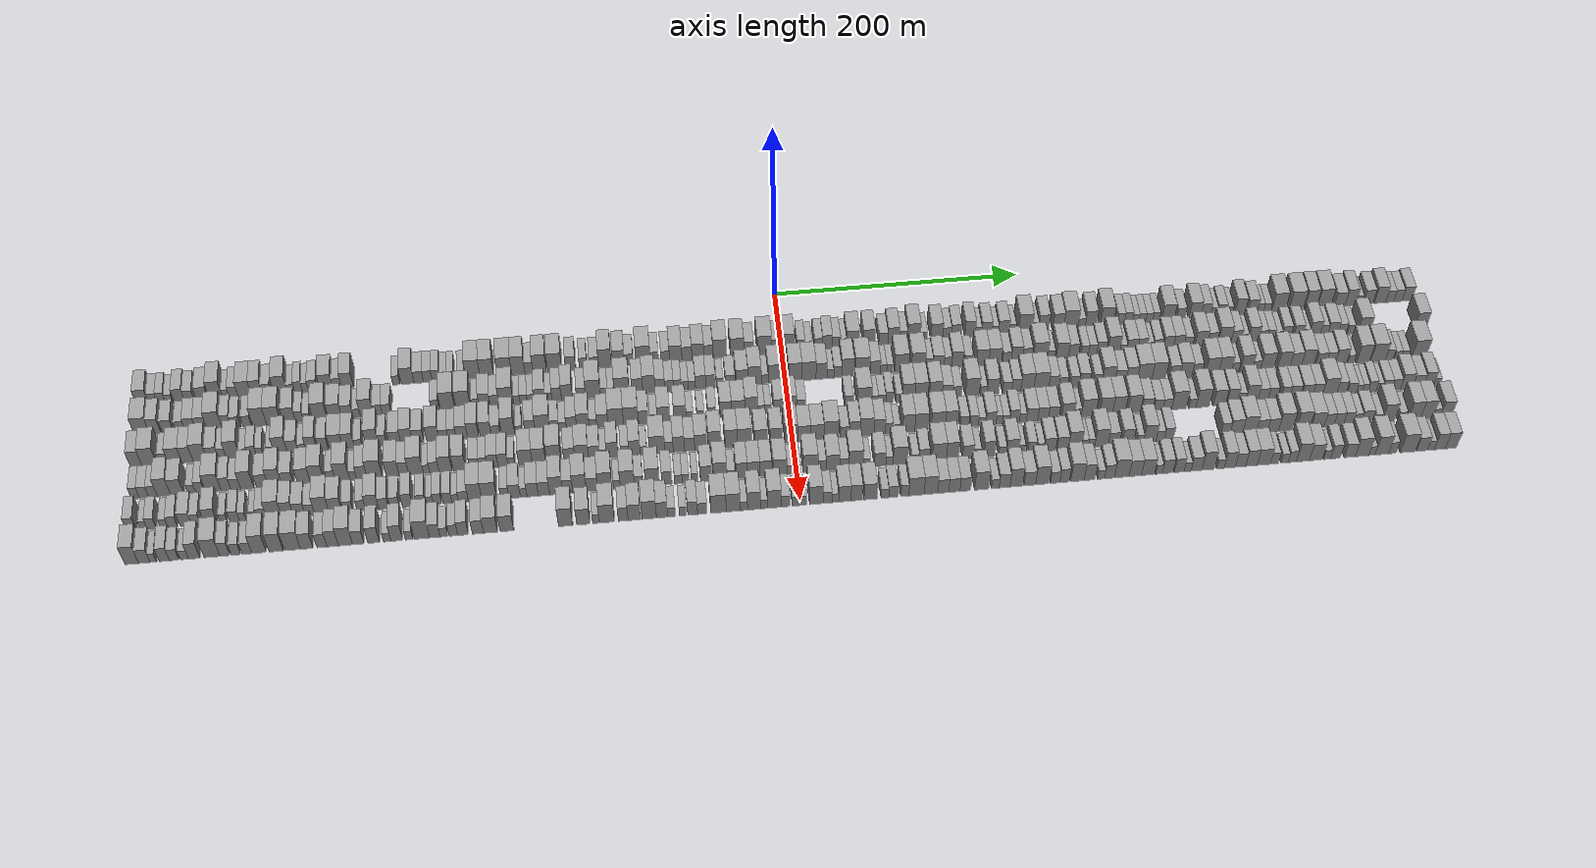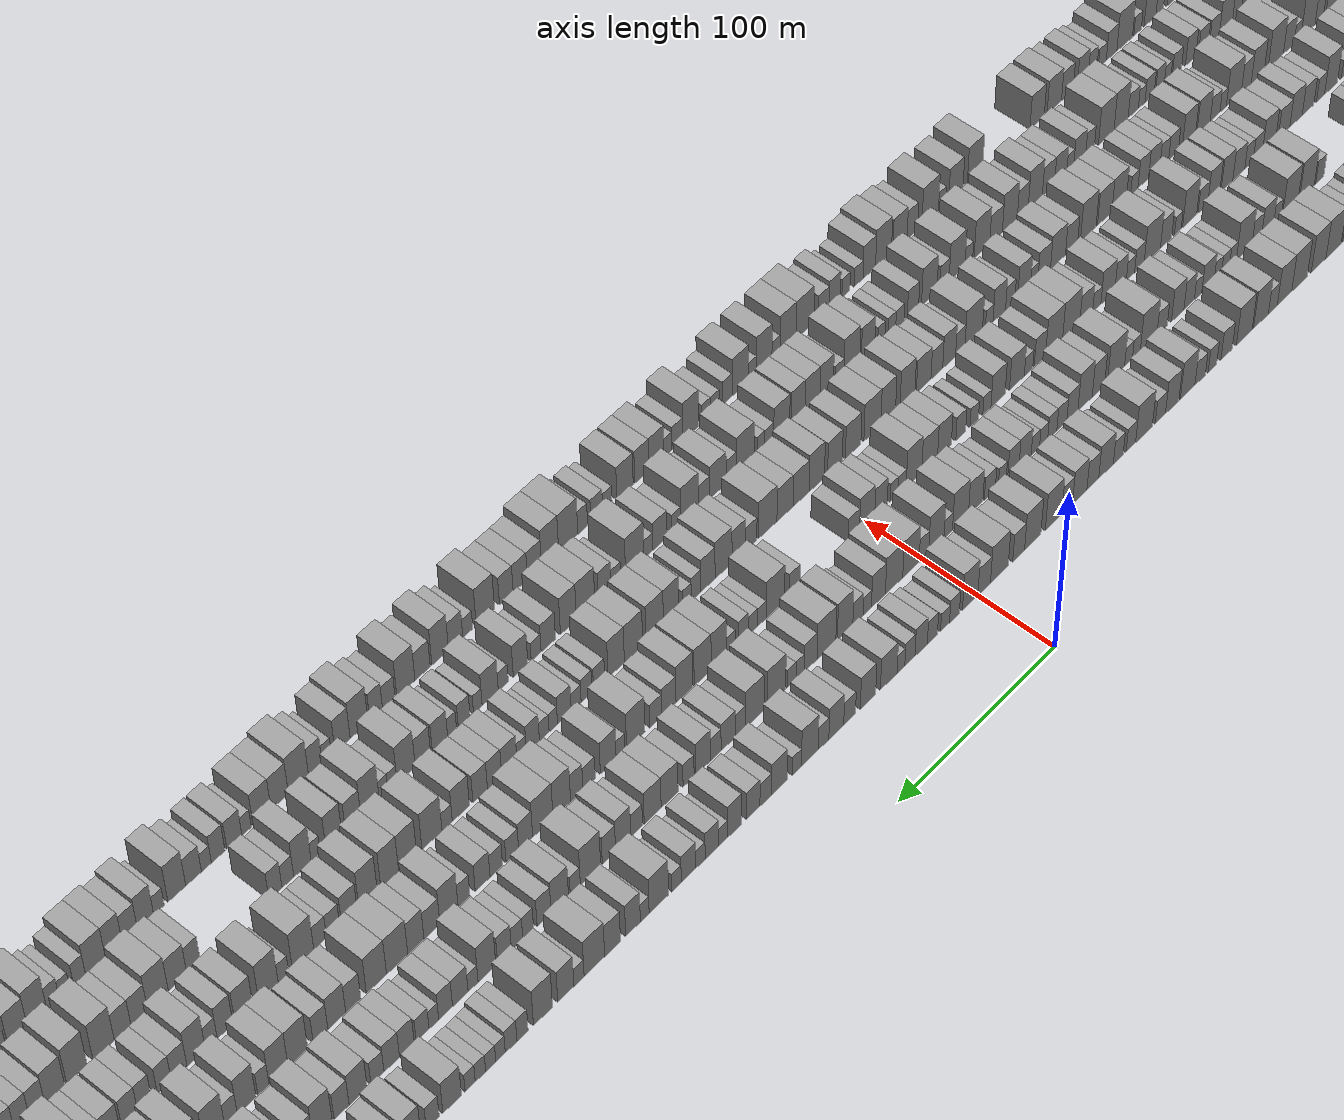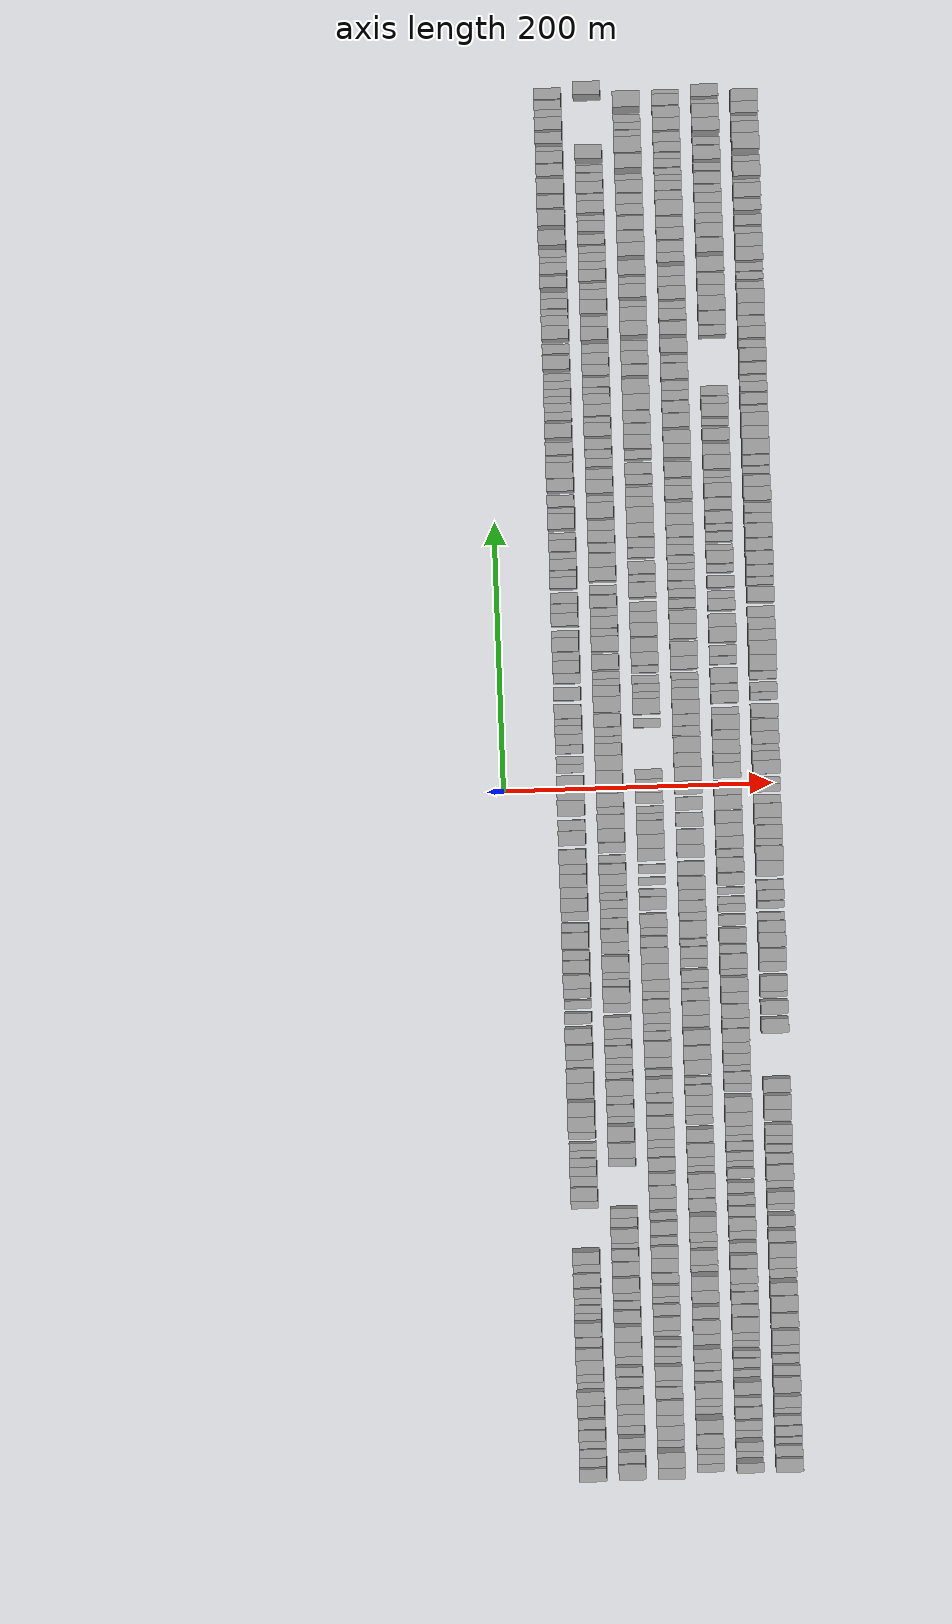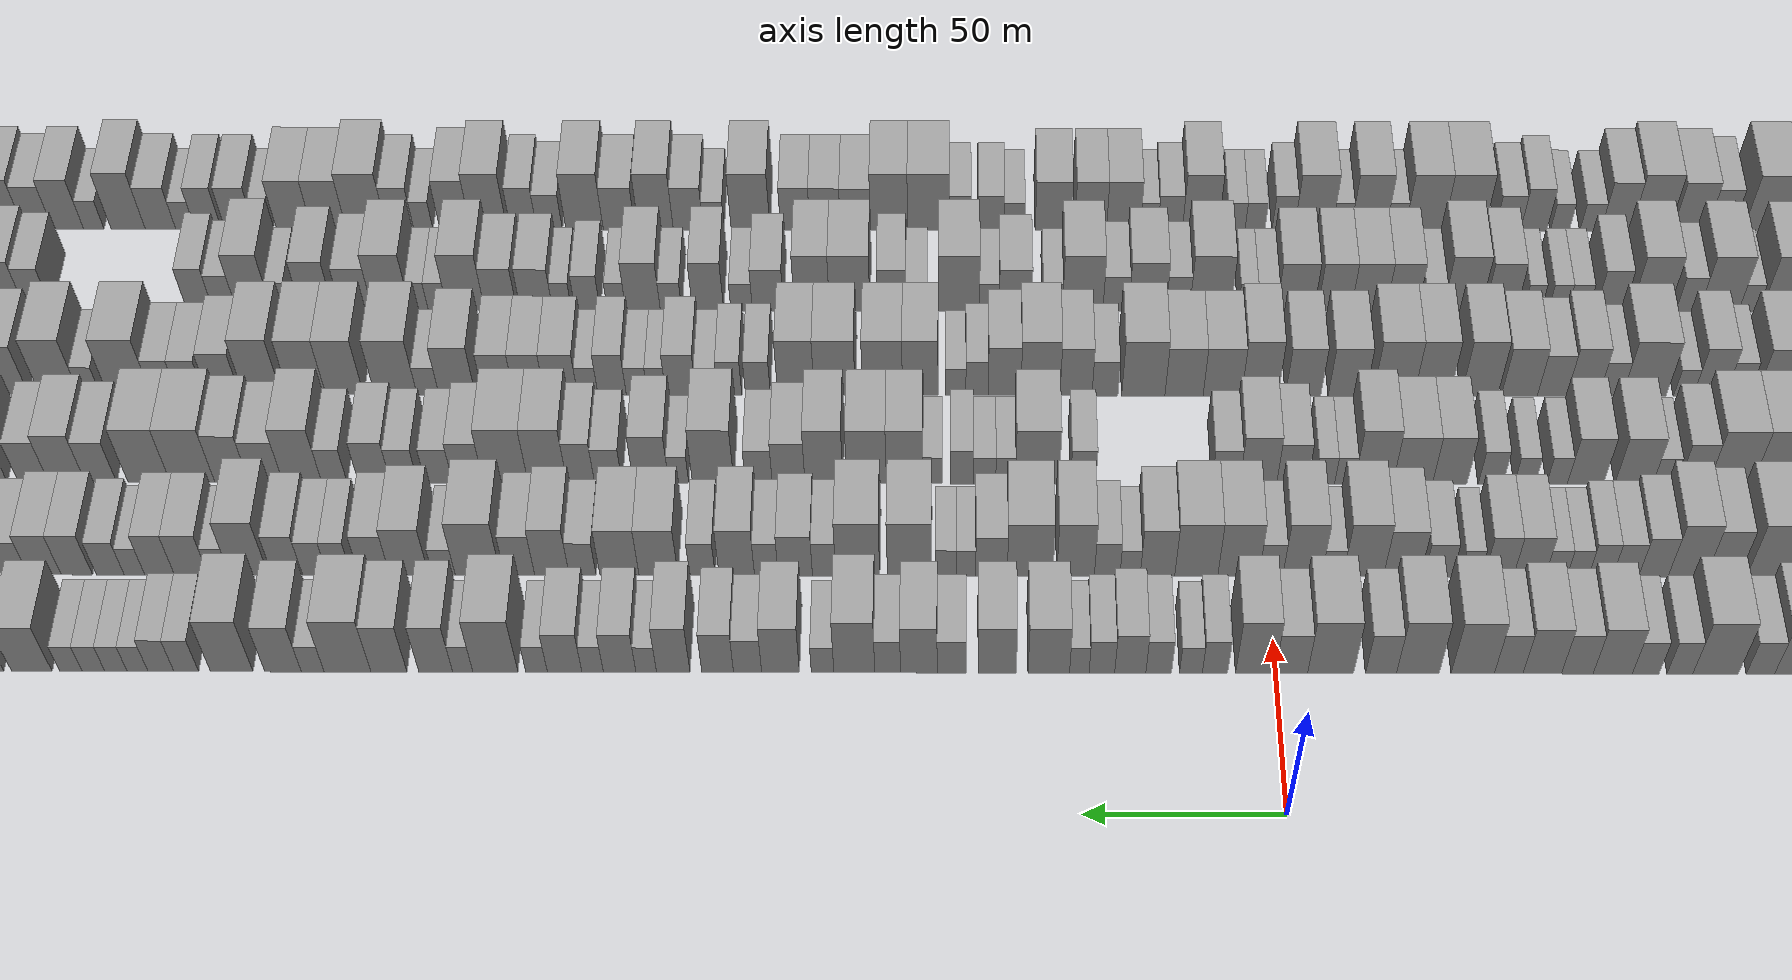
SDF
<sdf version="1.6">
 <world name="default">
  <scene>
   <sky><clouds><speed>12</speed></clouds></sky>
   <ambient>0.4 0.4 0.4 1</ambient>
   <background>0.7 0.7 0.7 1</background>
   <shadows>1</shadows>
  </scene>
  <gravity>0 0 -9.8066</gravity>
  <magnetic_field>6e-06 2.3e-05 -4.2e-05</magnetic_field>
  <physics default="0" name="default_physics" type="ode">
   <ode>
    <solver>
     <type>quick</type>
     <iters>10</iters>
     <sor>1.0</sor>
     <use_dynamic_moi_rescaling>0</use_dynamic_moi_rescaling>
    </solver>
    <constraints>
     <cfm>0</cfm>
     <erp>0.2</erp>
     <contact_max_correcting_vel>100</contact_max_correcting_vel>
     <contact_surface_layer>0.001</contact_surface_layer>
    </constraints>
   </ode>
   <max_step_size>0.004</max_step_size>
   <real_time_factor>1</real_time_factor>
   <real_time_update_rate>250</real_time_update_rate>
  </physics>
  <light name="sun" type="directional">
   <pose>0 0 10 0 0 0</pose>
   <diffuse>0.8 0.8 0.8 1</diffuse>
   <specular>0.2 0.2 0.2 1</specular>
   <attenuation>
    <range>1000</range>
    <constant>0.9</constant>
    <linear>0.01</linear>
    <quadratic>0.001</quadratic>
   </attenuation>
   <direction>-0.5 0.1 -0.9</direction>
  </light>
  <model name="building_1">
   <static>1</static>
   <pose>50.0000 -505.1877 0 0.000000 0.000000 0.000000</pose>
   <link name="link">
    <pose>0 0 10.50 0 0 0</pose>
    <collision name="collision"><geometry><box><size>20.0000 9.6246 21.0000</size></box></geometry></collision>
    <visual name="visual">
     <cast_shadows>0</cast_shadows>
     <geometry><box><size>20.0000 9.6246 21.0000</size></box></geometry>
     <material>
      <script>
       <uri>model://grey_wall/materials/scripts</uri>
       <uri>model://grey_wall/materials/textures</uri>
       <name>vrc/grey_wall</name>
      </script>
     </material>
    </visual>
   </link>
  </model>
  <model name="building_2">
   <static>1</static>
   <pose>50.0000 -497.0915 0 0.000000 0.000000 0.000000</pose>
   <link name="link">
    <pose>0 0 7.50 0 0 0</pose>
    <collision name="collision"><geometry><box><size>20.0000 6.5677 15.0000</size></box></geometry></collision>
    <visual name="visual">
     <cast_shadows>0</cast_shadows>
     <geometry><box><size>20.0000 6.5677 15.0000</size></box></geometry>
     <material>
      <script>
       <uri>model://grey_wall/materials/scripts</uri>
       <uri>model://grey_wall/materials/textures</uri>
       <name>vrc/grey_wall</name>
      </script>
     </material>
    </visual>
   </link>
  </model>
  <model name="building_3">
   <static>1</static>
   <pose>50.0000 -490.6406 0 0.000000 0.000000 0.000000</pose>
   <link name="link">
    <pose>0 0 7.50 0 0 0</pose>
    <collision name="collision"><geometry><box><size>20.0000 6.3341 15.0000</size></box></geometry></collision>
    <visual name="visual">
     <cast_shadows>0</cast_shadows>
     <geometry><box><size>20.0000 6.3341 15.0000</size></box></geometry>
     <material>
      <script>
       <uri>model://grey_wall/materials/scripts</uri>
       <uri>model://grey_wall/materials/textures</uri>
       <name>vrc/grey_wall</name>
      </script>
     </material>
    </visual>
   </link>
  </model>
  <model name="building_4">
   <static>1</static>
   <pose>50.0000 -484.6623 0 0.000000 0.000000 0.000000</pose>
   <link name="link">
    <pose>0 0 6.00 0 0 0</pose>
    <collision name="collision"><geometry><box><size>20.0000 5.6226 12.0000</size></box></geometry></collision>
    <visual name="visual">
     <cast_shadows>0</cast_shadows>
     <geometry><box><size>20.0000 5.6226 12.0000</size></box></geometry>
     <material>
      <script>
       <uri>model://grey_wall/materials/scripts</uri>
       <uri>model://grey_wall/materials/textures</uri>
       <name>vrc/grey_wall</name>
      </script>
     </material>
    </visual>
   </link>
  </model>
  <model name="building_5">
   <static>1</static>
   <pose>50.0000 -476.7808 0 0.000000 0.000000 0.000000</pose>
   <link name="link">
    <pose>0 0 9.00 0 0 0</pose>
    <collision name="collision"><geometry><box><size>20.0000 8.1402 18.0000</size></box></geometry></collision>
    <visual name="visual">
     <cast_shadows>0</cast_shadows>
     <geometry><box><size>20.0000 8.1402 18.0000</size></box></geometry>
     <material>
      <script>
       <uri>model://grey_wall/materials/scripts</uri>
       <uri>model://grey_wall/materials/textures</uri>
       <name>vrc/grey_wall</name>
      </script>
     </material>
    </visual>
   </link>
  </model>
  <model name="building_6">
   <static>1</static>
   <pose>50.0000 -469.0146 0 0.000000 0.000000 0.000000</pose>
   <link name="link">
    <pose>0 0 7.50 0 0 0</pose>
    <collision name="collision"><geometry><box><size>20.0000 7.3923 15.0000</size></box></geometry></collision>
    <visual name="visual">
     <cast_shadows>0</cast_shadows>
     <geometry><box><size>20.0000 7.3923 15.0000</size></box></geometry>
     <material>
      <script>
       <uri>model://grey_wall/materials/scripts</uri>
       <uri>model://grey_wall/materials/textures</uri>
       <name>vrc/grey_wall</name>
      </script>
     </material>
    </visual>
   </link>
  </model>
  <model name="building_7">
   <static>1</static>
   <pose>50.0000 -458.8198 0 0.000000 0.000000 0.000000</pose>
   <link name="link">
    <pose>0 0 9.00 0 0 0</pose>
    <collision name="collision"><geometry><box><size>20.0000 8.9973 18.0000</size></box></geometry></collision>
    <visual name="visual">
     <cast_shadows>0</cast_shadows>
     <geometry><box><size>20.0000 8.9973 18.0000</size></box></geometry>
     <material>
      <script>
       <uri>model://grey_wall/materials/scripts</uri>
       <uri>model://grey_wall/materials/textures</uri>
       <name>vrc/grey_wall</name>
      </script>
     </material>
    </visual>
   </link>
  </model>
  <model name="building_8">
   <static>1</static>
   <pose>50.0000 -448.1830 0 0.000000 0.000000 0.000000</pose>
   <link name="link">
    <pose>0 0 12.00 0 0 0</pose>
    <collision name="collision"><geometry><box><size>20.0000 10.2763 24.0000</size></box></geometry></collision>
    <visual name="visual">
     <cast_shadows>0</cast_shadows>
     <geometry><box><size>20.0000 10.2763 24.0000</size></box></geometry>
     <material>
      <script>
       <uri>model://grey_wall/materials/scripts</uri>
       <uri>model://grey_wall/materials/textures</uri>
       <name>vrc/grey_wall</name>
      </script>
     </material>
    </visual>
   </link>
  </model>
  <model name="building_9">
   <static>1</static>
   <pose>50.0000 -440.5058 0 0.000000 0.000000 0.000000</pose>
   <link name="link">
    <pose>0 0 6.00 0 0 0</pose>
    <collision name="collision"><geometry><box><size>20.0000 5.0780 12.0000</size></box></geometry></collision>
    <visual name="visual">
     <cast_shadows>0</cast_shadows>
     <geometry><box><size>20.0000 5.0780 12.0000</size></box></geometry>
     <material>
      <script>
       <uri>model://grey_wall/materials/scripts</uri>
       <uri>model://grey_wall/materials/textures</uri>
       <name>vrc/grey_wall</name>
      </script>
     </material>
    </visual>
   </link>
  </model>
  <model name="building_10">
   <static>1</static>
   <pose>50.0000 -434.4570 0 0.000000 0.000000 0.000000</pose>
   <link name="link">
    <pose>0 0 7.50 0 0 0</pose>
    <collision name="collision"><geometry><box><size>20.0000 7.0197 15.0000</size></box></geometry></collision>
    <visual name="visual">
     <cast_shadows>0</cast_shadows>
     <geometry><box><size>20.0000 7.0197 15.0000</size></box></geometry>
     <material>
      <script>
       <uri>model://grey_wall/materials/scripts</uri>
       <uri>model://grey_wall/materials/textures</uri>
       <name>vrc/grey_wall</name>
      </script>
     </material>
    </visual>
   </link>
  </model>
  <model name="building_11">
   <static>1</static>
   <pose>50.0000 -425.7513 0 0.000000 0.000000 0.000000</pose>
   <link name="link">
    <pose>0 0 10.50 0 0 0</pose>
    <collision name="collision"><geometry><box><size>20.0000 10.3918 21.0000</size></box></geometry></collision>
    <visual name="visual">
     <cast_shadows>0</cast_shadows>
     <geometry><box><size>20.0000 10.3918 21.0000</size></box></geometry>
     <material>
      <script>
       <uri>model://grey_wall/materials/scripts</uri>
       <uri>model://grey_wall/materials/textures</uri>
       <name>vrc/grey_wall</name>
      </script>
     </material>
    </visual>
   </link>
  </model>
  <model name="building_12">
   <static>1</static>
   <pose>50.0000 -416.2189 0 0.000000 0.000000 0.000000</pose>
   <link name="link">
    <pose>0 0 10.50 0 0 0</pose>
    <collision name="collision"><geometry><box><size>20.0000 8.6729 21.0000</size></box></geometry></collision>
    <visual name="visual">
     <cast_shadows>0</cast_shadows>
     <geometry><box><size>20.0000 8.6729 21.0000</size></box></geometry>
     <material>
      <script>
       <uri>model://grey_wall/materials/scripts</uri>
       <uri>model://grey_wall/materials/textures</uri>
       <name>vrc/grey_wall</name>
      </script>
     </material>
    </visual>
   </link>
  </model>
  <model name="building_13">
   <static>1</static>
   <pose>50.0000 -408.3630 0 0.000000 0.000000 0.000000</pose>
   <link name="link">
    <pose>0 0 7.50 0 0 0</pose>
    <collision name="collision"><geometry><box><size>20.0000 7.0390 15.0000</size></box></geometry></collision>
    <visual name="visual">
     <cast_shadows>0</cast_shadows>
     <geometry><box><size>20.0000 7.0390 15.0000</size></box></geometry>
     <material>
      <script>
       <uri>model://grey_wall/materials/scripts</uri>
       <uri>model://grey_wall/materials/textures</uri>
       <name>vrc/grey_wall</name>
      </script>
     </material>
    </visual>
   </link>
  </model>
  <model name="building_14">
   <static>1</static>
   <pose>50.0000 -397.6285 0 0.000000 0.000000 0.000000</pose>
   <link name="link">
    <pose>0 0 12.00 0 0 0</pose>
    <collision name="collision"><geometry><box><size>20.0000 10.4300 24.0000</size></box></geometry></collision>
    <visual name="visual">
     <cast_shadows>0</cast_shadows>
     <geometry><box><size>20.0000 10.4300 24.0000</size></box></geometry>
     <material>
      <script>
       <uri>model://grey_wall/materials/scripts</uri>
       <uri>model://grey_wall/materials/textures</uri>
       <name>vrc/grey_wall</name>
      </script>
     </material>
    </visual>
   </link>
  </model>
  <model name="building_15">
   <static>1</static>
   <pose>50.0000 -389.6784 0 0.000000 0.000000 0.000000</pose>
   <link name="link">
    <pose>0 0 6.00 0 0 0</pose>
    <collision name="collision"><geometry><box><size>20.0000 5.4701 12.0000</size></box></geometry></collision>
    <visual name="visual">
     <cast_shadows>0</cast_shadows>
     <geometry><box><size>20.0000 5.4701 12.0000</size></box></geometry>
     <material>
      <script>
       <uri>model://grey_wall/materials/scripts</uri>
       <uri>model://grey_wall/materials/textures</uri>
       <name>vrc/grey_wall</name>
      </script>
     </material>
    </visual>
   </link>
  </model>
  <model name="building_16">
   <static>1</static>
   <pose>50.0000 -383.9326 0 0.000000 0.000000 0.000000</pose>
   <link name="link">
    <pose>0 0 7.50 0 0 0</pose>
    <collision name="collision"><geometry><box><size>20.0000 6.0216 15.0000</size></box></geometry></collision>
    <visual name="visual">
     <cast_shadows>0</cast_shadows>
     <geometry><box><size>20.0000 6.0216 15.0000</size></box></geometry>
     <material>
      <script>
       <uri>model://grey_wall/materials/scripts</uri>
       <uri>model://grey_wall/materials/textures</uri>
       <name>vrc/grey_wall</name>
      </script>
     </material>
    </visual>
   </link>
  </model>
  <model name="building_17">
   <static>1</static>
   <pose>50.0000 -378.4423 0 0.000000 0.000000 0.000000</pose>
   <link name="link">
    <pose>0 0 6.00 0 0 0</pose>
    <collision name="collision"><geometry><box><size>20.0000 4.9590 12.0000</size></box></geometry></collision>
    <visual name="visual">
     <cast_shadows>0</cast_shadows>
     <geometry><box><size>20.0000 4.9590 12.0000</size></box></geometry>
     <material>
      <script>
       <uri>model://grey_wall/materials/scripts</uri>
       <uri>model://grey_wall/materials/textures</uri>
       <name>vrc/grey_wall</name>
      </script>
     </material>
    </visual>
   </link>
  </model>
  <model name="building_18">
   <static>1</static>
   <pose>50.0000 -372.4186 0 0.000000 0.000000 0.000000</pose>
   <link name="link">
    <pose>0 0 7.50 0 0 0</pose>
    <collision name="collision"><geometry><box><size>20.0000 7.0884 15.0000</size></box></geometry></collision>
    <visual name="visual">
     <cast_shadows>0</cast_shadows>
     <geometry><box><size>20.0000 7.0884 15.0000</size></box></geometry>
     <material>
      <script>
       <uri>model://grey_wall/materials/scripts</uri>
       <uri>model://grey_wall/materials/textures</uri>
       <name>vrc/grey_wall</name>
      </script>
     </material>
    </visual>
   </link>
  </model>
  <model name="building_19">
   <static>1</static>
   <pose>50.0000 -361.8042 0 0.000000 0.000000 0.000000</pose>
   <link name="link">
    <pose>0 0 10.50 0 0 0</pose>
    <collision name="collision"><geometry><box><size>20.0000 10.1404 21.0000</size></box></geometry></collision>
    <visual name="visual">
     <cast_shadows>0</cast_shadows>
     <geometry><box><size>20.0000 10.1404 21.0000</size></box></geometry>
     <material>
      <script>
       <uri>model://grey_wall/materials/scripts</uri>
       <uri>model://grey_wall/materials/textures</uri>
       <name>vrc/grey_wall</name>
      </script>
     </material>
    </visual>
   </link>
  </model>
  <model name="building_20">
   <static>1</static>
   <pose>50.0000 -353.3539 0 0.000000 0.000000 0.000000</pose>
   <link name="link">
    <pose>0 0 7.50 0 0 0</pose>
    <collision name="collision"><geometry><box><size>20.0000 6.7602 15.0000</size></box></geometry></collision>
    <visual name="visual">
     <cast_shadows>0</cast_shadows>
     <geometry><box><size>20.0000 6.7602 15.0000</size></box></geometry>
     <material>
      <script>
       <uri>model://grey_wall/materials/scripts</uri>
       <uri>model://grey_wall/materials/textures</uri>
       <name>vrc/grey_wall</name>
      </script>
     </material>
    </visual>
   </link>
  </model>
  <model name="building_21">
   <static>1</static>
   <pose>50.0000 -345.3491 0 0.000000 0.000000 0.000000</pose>
   <link name="link">
    <pose>0 0 10.50 0 0 0</pose>
    <collision name="collision"><geometry><box><size>20.0000 9.2494 21.0000</size></box></geometry></collision>
    <visual name="visual">
     <cast_shadows>0</cast_shadows>
     <geometry><box><size>20.0000 9.2494 21.0000</size></box></geometry>
     <material>
      <script>
       <uri>model://grey_wall/materials/scripts</uri>
       <uri>model://grey_wall/materials/textures</uri>
       <name>vrc/grey_wall</name>
      </script>
     </material>
    </visual>
   </link>
  </model>
  <model name="building_22">
   <static>1</static>
   <pose>50.0000 -307.1220 0 0.000000 0.000000 0.000000</pose>
   <link name="link">
    <pose>0 0 6.00 0 0 0</pose>
    <collision name="collision"><geometry><box><size>20.0000 5.7349 12.0000</size></box></geometry></collision>
    <visual name="visual">
     <cast_shadows>0</cast_shadows>
     <geometry><box><size>20.0000 5.7349 12.0000</size></box></geometry>
     <material>
      <script>
       <uri>model://grey_wall/materials/scripts</uri>
       <uri>model://grey_wall/materials/textures</uri>
       <name>vrc/grey_wall</name>
      </script>
     </material>
    </visual>
   </link>
  </model>
  <model name="building_23">
   <static>1</static>
   <pose>50.0000 -298.2257 0 0.000000 0.000000 0.000000</pose>
   <link name="link">
    <pose>0 0 10.50 0 0 0</pose>
    <collision name="collision"><geometry><box><size>20.0000 10.0577 21.0000</size></box></geometry></collision>
    <visual name="visual">
     <cast_shadows>0</cast_shadows>
     <geometry><box><size>20.0000 10.0577 21.0000</size></box></geometry>
     <material>
      <script>
       <uri>model://grey_wall/materials/scripts</uri>
       <uri>model://grey_wall/materials/textures</uri>
       <name>vrc/grey_wall</name>
      </script>
     </material>
    </visual>
   </link>
  </model>
  <model name="building_24">
   <static>1</static>
   <pose>50.0000 -289.4588 0 0.000000 0.000000 0.000000</pose>
   <link name="link">
    <pose>0 0 7.50 0 0 0</pose>
    <collision name="collision"><geometry><box><size>20.0000 7.4761 15.0000</size></box></geometry></collision>
    <visual name="visual">
     <cast_shadows>0</cast_shadows>
     <geometry><box><size>20.0000 7.4761 15.0000</size></box></geometry>
     <material>
      <script>
       <uri>model://grey_wall/materials/scripts</uri>
       <uri>model://grey_wall/materials/textures</uri>
       <name>vrc/grey_wall</name>
      </script>
     </material>
    </visual>
   </link>
  </model>
  <model name="building_25">
   <static>1</static>
   <pose>50.0000 -282.2839 0 0.000000 0.000000 0.000000</pose>
   <link name="link">
    <pose>0 0 7.50 0 0 0</pose>
    <collision name="collision"><geometry><box><size>20.0000 6.8737 15.0000</size></box></geometry></collision>
    <visual name="visual">
     <cast_shadows>0</cast_shadows>
     <geometry><box><size>20.0000 6.8737 15.0000</size></box></geometry>
     <material>
      <script>
       <uri>model://grey_wall/materials/scripts</uri>
       <uri>model://grey_wall/materials/textures</uri>
       <name>vrc/grey_wall</name>
      </script>
     </material>
    </visual>
   </link>
  </model>
  <model name="building_26">
   <static>1</static>
   <pose>50.0000 -275.6024 0 0.000000 0.000000 0.000000</pose>
   <link name="link">
    <pose>0 0 7.50 0 0 0</pose>
    <collision name="collision"><geometry><box><size>20.0000 6.4892 15.0000</size></box></geometry></collision>
    <visual name="visual">
     <cast_shadows>0</cast_shadows>
     <geometry><box><size>20.0000 6.4892 15.0000</size></box></geometry>
     <material>
      <script>
       <uri>model://grey_wall/materials/scripts</uri>
       <uri>model://grey_wall/materials/textures</uri>
       <name>vrc/grey_wall</name>
      </script>
     </material>
    </visual>
   </link>
  </model>
  <model name="building_27">
   <static>1</static>
   <pose>50.0000 -269.7325 0 0.000000 0.000000 0.000000</pose>
   <link name="link">
    <pose>0 0 6.00 0 0 0</pose>
    <collision name="collision"><geometry><box><size>20.0000 5.2507 12.0000</size></box></geometry></collision>
    <visual name="visual">
     <cast_shadows>0</cast_shadows>
     <geometry><box><size>20.0000 5.2507 12.0000</size></box></geometry>
     <material>
      <script>
       <uri>model://grey_wall/materials/scripts</uri>
       <uri>model://grey_wall/materials/textures</uri>
       <name>vrc/grey_wall</name>
      </script>
     </material>
    </visual>
   </link>
  </model>
  <model name="building_28">
   <static>1</static>
   <pose>50.0000 -264.3541 0 0.000000 0.000000 0.000000</pose>
   <link name="link">
    <pose>0 0 6.00 0 0 0</pose>
    <collision name="collision"><geometry><box><size>20.0000 5.5062 12.0000</size></box></geometry></collision>
    <visual name="visual">
     <cast_shadows>0</cast_shadows>
     <geometry><box><size>20.0000 5.5062 12.0000</size></box></geometry>
     <material>
      <script>
       <uri>model://grey_wall/materials/scripts</uri>
       <uri>model://grey_wall/materials/textures</uri>
       <name>vrc/grey_wall</name>
      </script>
     </material>
    </visual>
   </link>
  </model>
  <model name="building_29">
   <static>1</static>
   <pose>50.0000 -255.8877 0 0.000000 0.000000 0.000000</pose>
   <link name="link">
    <pose>0 0 6.00 0 0 0</pose>
    <collision name="collision"><geometry><box><size>20.0000 5.4264 12.0000</size></box></geometry></collision>
    <visual name="visual">
     <cast_shadows>0</cast_shadows>
     <geometry><box><size>20.0000 5.4264 12.0000</size></box></geometry>
     <material>
      <script>
       <uri>model://grey_wall/materials/scripts</uri>
       <uri>model://grey_wall/materials/textures</uri>
       <name>vrc/grey_wall</name>
      </script>
     </material>
    </visual>
   </link>
  </model>
  <model name="building_30">
   <static>1</static>
   <pose>50.0000 -246.5515 0 0.000000 0.000000 0.000000</pose>
   <link name="link">
    <pose>0 0 12.00 0 0 0</pose>
    <collision name="collision"><geometry><box><size>20.0000 11.2462 24.0000</size></box></geometry></collision>
    <visual name="visual">
     <cast_shadows>0</cast_shadows>
     <geometry><box><size>20.0000 11.2462 24.0000</size></box></geometry>
     <material>
      <script>
       <uri>model://grey_wall/materials/scripts</uri>
       <uri>model://grey_wall/materials/textures</uri>
       <name>vrc/grey_wall</name>
      </script>
     </material>
    </visual>
   </link>
  </model>
  <model name="building_31">
   <static>1</static>
   <pose>50.0000 -235.5521 0 0.000000 0.000000 0.000000</pose>
   <link name="link">
    <pose>0 0 12.00 0 0 0</pose>
    <collision name="collision"><geometry><box><size>20.0000 10.7525 24.0000</size></box></geometry></collision>
    <visual name="visual">
     <cast_shadows>0</cast_shadows>
     <geometry><box><size>20.0000 10.7525 24.0000</size></box></geometry>
     <material>
      <script>
       <uri>model://grey_wall/materials/scripts</uri>
       <uri>model://grey_wall/materials/textures</uri>
       <name>vrc/grey_wall</name>
      </script>
     </material>
    </visual>
   </link>
  </model>
  <model name="building_32">
   <static>1</static>
   <pose>50.0000 -221.5228 0 0.000000 0.000000 0.000000</pose>
   <link name="link">
    <pose>0 0 12.00 0 0 0</pose>
    <collision name="collision"><geometry><box><size>20.0000 11.3062 24.0000</size></box></geometry></collision>
    <visual name="visual">
     <cast_shadows>0</cast_shadows>
     <geometry><box><size>20.0000 11.3062 24.0000</size></box></geometry>
     <material>
      <script>
       <uri>model://grey_wall/materials/scripts</uri>
       <uri>model://grey_wall/materials/textures</uri>
       <name>vrc/grey_wall</name>
      </script>
     </material>
    </visual>
   </link>
  </model>
  <model name="building_33">
   <static>1</static>
   <pose>50.0000 -210.6419 0 0.000000 0.000000 0.000000</pose>
   <link name="link">
    <pose>0 0 12.00 0 0 0</pose>
    <collision name="collision"><geometry><box><size>20.0000 10.4556 24.0000</size></box></geometry></collision>
    <visual name="visual">
     <cast_shadows>0</cast_shadows>
     <geometry><box><size>20.0000 10.4556 24.0000</size></box></geometry>
     <material>
      <script>
       <uri>model://grey_wall/materials/scripts</uri>
       <uri>model://grey_wall/materials/textures</uri>
       <name>vrc/grey_wall</name>
      </script>
     </material>
    </visual>
   </link>
  </model>
  <model name="building_34">
   <static>1</static>
   <pose>50.0000 -202.1940 0 0.000000 0.000000 0.000000</pose>
   <link name="link">
    <pose>0 0 7.50 0 0 0</pose>
    <collision name="collision"><geometry><box><size>20.0000 6.4401 15.0000</size></box></geometry></collision>
    <visual name="visual">
     <cast_shadows>0</cast_shadows>
     <geometry><box><size>20.0000 6.4401 15.0000</size></box></geometry>
     <material>
      <script>
       <uri>model://grey_wall/materials/scripts</uri>
       <uri>model://grey_wall/materials/textures</uri>
       <name>vrc/grey_wall</name>
      </script>
     </material>
    </visual>
   </link>
  </model>
  <model name="building_35">
   <static>1</static>
   <pose>50.0000 -193.6166 0 0.000000 0.000000 0.000000</pose>
   <link name="link">
    <pose>0 0 12.00 0 0 0</pose>
    <collision name="collision"><geometry><box><size>20.0000 10.7147 24.0000</size></box></geometry></collision>
    <visual name="visual">
     <cast_shadows>0</cast_shadows>
     <geometry><box><size>20.0000 10.7147 24.0000</size></box></geometry>
     <material>
      <script>
       <uri>model://grey_wall/materials/scripts</uri>
       <uri>model://grey_wall/materials/textures</uri>
       <name>vrc/grey_wall</name>
      </script>
     </material>
    </visual>
   </link>
  </model>
  <model name="building_36">
   <static>1</static>
   <pose>50.0000 -181.6224 0 0.000000 0.000000 0.000000</pose>
   <link name="link">
    <pose>0 0 12.00 0 0 0</pose>
    <collision name="collision"><geometry><box><size>20.0000 11.2737 24.0000</size></box></geometry></collision>
    <visual name="visual">
     <cast_shadows>0</cast_shadows>
     <geometry><box><size>20.0000 11.2737 24.0000</size></box></geometry>
     <material>
      <script>
       <uri>model://grey_wall/materials/scripts</uri>
       <uri>model://grey_wall/materials/textures</uri>
       <name>vrc/grey_wall</name>
      </script>
     </material>
    </visual>
   </link>
  </model>
  <model name="building_37">
   <static>1</static>
   <pose>50.0000 -168.9967 0 0.000000 0.000000 0.000000</pose>
   <link name="link">
    <pose>0 0 9.00 0 0 0</pose>
    <collision name="collision"><geometry><box><size>20.0000 7.9776 18.0000</size></box></geometry></collision>
    <visual name="visual">
     <cast_shadows>0</cast_shadows>
     <geometry><box><size>20.0000 7.9776 18.0000</size></box></geometry>
     <material>
      <script>
       <uri>model://grey_wall/materials/scripts</uri>
       <uri>model://grey_wall/materials/textures</uri>
       <name>vrc/grey_wall</name>
      </script>
     </material>
    </visual>
   </link>
  </model>
  <model name="building_38">
   <static>1</static>
   <pose>50.0000 -158.9827 0 0.000000 0.000000 0.000000</pose>
   <link name="link">
    <pose>0 0 7.50 0 0 0</pose>
    <collision name="collision"><geometry><box><size>20.0000 6.0505 15.0000</size></box></geometry></collision>
    <visual name="visual">
     <cast_shadows>0</cast_shadows>
     <geometry><box><size>20.0000 6.0505 15.0000</size></box></geometry>
     <material>
      <script>
       <uri>model://grey_wall/materials/scripts</uri>
       <uri>model://grey_wall/materials/textures</uri>
       <name>vrc/grey_wall</name>
      </script>
     </material>
    </visual>
   </link>
  </model>
  <model name="building_39">
   <static>1</static>
   <pose>50.0000 -150.2949 0 0.000000 0.000000 0.000000</pose>
   <link name="link">
    <pose>0 0 7.50 0 0 0</pose>
    <collision name="collision"><geometry><box><size>20.0000 7.3253 15.0000</size></box></geometry></collision>
    <visual name="visual">
     <cast_shadows>0</cast_shadows>
     <geometry><box><size>20.0000 7.3253 15.0000</size></box></geometry>
     <material>
      <script>
       <uri>model://grey_wall/materials/scripts</uri>
       <uri>model://grey_wall/materials/textures</uri>
       <name>vrc/grey_wall</name>
      </script>
     </material>
    </visual>
   </link>
  </model>
  <model name="building_40">
   <static>1</static>
   <pose>50.0000 -141.5123 0 0.000000 0.000000 0.000000</pose>
   <link name="link">
    <pose>0 0 12.00 0 0 0</pose>
    <collision name="collision"><geometry><box><size>20.0000 10.2399 24.0000</size></box></geometry></collision>
    <visual name="visual">
     <cast_shadows>0</cast_shadows>
     <geometry><box><size>20.0000 10.2399 24.0000</size></box></geometry>
     <material>
      <script>
       <uri>model://grey_wall/materials/scripts</uri>
       <uri>model://grey_wall/materials/textures</uri>
       <name>vrc/grey_wall</name>
      </script>
     </material>
    </visual>
   </link>
  </model>
  <model name="building_41">
   <static>1</static>
   <pose>50.0000 -130.7326 0 0.000000 0.000000 0.000000</pose>
   <link name="link">
    <pose>0 0 10.50 0 0 0</pose>
    <collision name="collision"><geometry><box><size>20.0000 9.3195 21.0000</size></box></geometry></collision>
    <visual name="visual">
     <cast_shadows>0</cast_shadows>
     <geometry><box><size>20.0000 9.3195 21.0000</size></box></geometry>
     <material>
      <script>
       <uri>model://grey_wall/materials/scripts</uri>
       <uri>model://grey_wall/materials/textures</uri>
       <name>vrc/grey_wall</name>
      </script>
     </material>
    </visual>
   </link>
  </model>
  <model name="building_42">
   <static>1</static>
   <pose>50.0000 -122.4962 0 0.000000 0.000000 0.000000</pose>
   <link name="link">
    <pose>0 0 7.50 0 0 0</pose>
    <collision name="collision"><geometry><box><size>20.0000 7.1534 15.0000</size></box></geometry></collision>
    <visual name="visual">
     <cast_shadows>0</cast_shadows>
     <geometry><box><size>20.0000 7.1534 15.0000</size></box></geometry>
     <material>
      <script>
       <uri>model://grey_wall/materials/scripts</uri>
       <uri>model://grey_wall/materials/textures</uri>
       <name>vrc/grey_wall</name>
      </script>
     </material>
    </visual>
   </link>
  </model>
  <model name="building_43">
   <static>1</static>
   <pose>50.0000 -111.1496 0 0.000000 0.000000 0.000000</pose>
   <link name="link">
    <pose>0 0 12.00 0 0 0</pose>
    <collision name="collision"><geometry><box><size>20.0000 11.5397 24.0000</size></box></geometry></collision>
    <visual name="visual">
     <cast_shadows>0</cast_shadows>
     <geometry><box><size>20.0000 11.5397 24.0000</size></box></geometry>
     <material>
      <script>
       <uri>model://grey_wall/materials/scripts</uri>
       <uri>model://grey_wall/materials/textures</uri>
       <name>vrc/grey_wall</name>
      </script>
     </material>
    </visual>
   </link>
  </model>
  <model name="building_44">
   <static>1</static>
   <pose>50.0000 -102.1287 0 0.000000 0.000000 0.000000</pose>
   <link name="link">
    <pose>0 0 7.50 0 0 0</pose>
    <collision name="collision"><geometry><box><size>20.0000 6.5022 15.0000</size></box></geometry></collision>
    <visual name="visual">
     <cast_shadows>0</cast_shadows>
     <geometry><box><size>20.0000 6.5022 15.0000</size></box></geometry>
     <material>
      <script>
       <uri>model://grey_wall/materials/scripts</uri>
       <uri>model://grey_wall/materials/textures</uri>
       <name>vrc/grey_wall</name>
      </script>
     </material>
    </visual>
   </link>
  </model>
  <model name="building_45">
   <static>1</static>
   <pose>50.0000 -93.5026 0 0.000000 0.000000 0.000000</pose>
   <link name="link">
    <pose>0 0 7.50 0 0 0</pose>
    <collision name="collision"><geometry><box><size>20.0000 6.7500 15.0000</size></box></geometry></collision>
    <visual name="visual">
     <cast_shadows>0</cast_shadows>
     <geometry><box><size>20.0000 6.7500 15.0000</size></box></geometry>
     <material>
      <script>
       <uri>model://grey_wall/materials/scripts</uri>
       <uri>model://grey_wall/materials/textures</uri>
       <name>vrc/grey_wall</name>
      </script>
     </material>
    </visual>
   </link>
  </model>
  <model name="building_46">
   <static>1</static>
   <pose>50.0000 -85.1663 0 0.000000 0.000000 0.000000</pose>
   <link name="link">
    <pose>0 0 10.50 0 0 0</pose>
    <collision name="collision"><geometry><box><size>20.0000 9.9225 21.0000</size></box></geometry></collision>
    <visual name="visual">
     <cast_shadows>0</cast_shadows>
     <geometry><box><size>20.0000 9.9225 21.0000</size></box></geometry>
     <material>
      <script>
       <uri>model://grey_wall/materials/scripts</uri>
       <uri>model://grey_wall/materials/textures</uri>
       <name>vrc/grey_wall</name>
      </script>
     </material>
    </visual>
   </link>
  </model>
  <model name="building_47">
   <static>1</static>
   <pose>50.0000 -76.1934 0 0.000000 0.000000 0.000000</pose>
   <link name="link">
    <pose>0 0 9.00 0 0 0</pose>
    <collision name="collision"><geometry><box><size>20.0000 8.0234 18.0000</size></box></geometry></collision>
    <visual name="visual">
     <cast_shadows>0</cast_shadows>
     <geometry><box><size>20.0000 8.0234 18.0000</size></box></geometry>
     <material>
      <script>
       <uri>model://grey_wall/materials/scripts</uri>
       <uri>model://grey_wall/materials/textures</uri>
       <name>vrc/grey_wall</name>
      </script>
     </material>
    </visual>
   </link>
  </model>
  <model name="building_48">
   <static>1</static>
   <pose>50.0000 -67.3247 0 0.000000 0.000000 0.000000</pose>
   <link name="link">
    <pose>0 0 10.50 0 0 0</pose>
    <collision name="collision"><geometry><box><size>20.0000 9.7140 21.0000</size></box></geometry></collision>
    <visual name="visual">
     <cast_shadows>0</cast_shadows>
     <geometry><box><size>20.0000 9.7140 21.0000</size></box></geometry>
     <material>
      <script>
       <uri>model://grey_wall/materials/scripts</uri>
       <uri>model://grey_wall/materials/textures</uri>
       <name>vrc/grey_wall</name>
      </script>
     </material>
    </visual>
   </link>
  </model>
  <model name="building_49">
   <static>1</static>
   <pose>50.0000 -58.8487 0 0.000000 0.000000 0.000000</pose>
   <link name="link">
    <pose>0 0 9.00 0 0 0</pose>
    <collision name="collision"><geometry><box><size>20.0000 7.2380 18.0000</size></box></geometry></collision>
    <visual name="visual">
     <cast_shadows>0</cast_shadows>
     <geometry><box><size>20.0000 7.2380 18.0000</size></box></geometry>
     <material>
      <script>
       <uri>model://grey_wall/materials/scripts</uri>
       <uri>model://grey_wall/materials/textures</uri>
       <name>vrc/grey_wall</name>
      </script>
     </material>
    </visual>
   </link>
  </model>
  <model name="building_50">
   <static>1</static>
   <pose>50.0000 -49.7501 0 0.000000 0.000000 0.000000</pose>
   <link name="link">
    <pose>0 0 12.00 0 0 0</pose>
    <collision name="collision"><geometry><box><size>20.0000 10.9593 24.0000</size></box></geometry></collision>
    <visual name="visual">
     <cast_shadows>0</cast_shadows>
     <geometry><box><size>20.0000 10.9593 24.0000</size></box></geometry>
     <material>
      <script>
       <uri>model://grey_wall/materials/scripts</uri>
       <uri>model://grey_wall/materials/textures</uri>
       <name>vrc/grey_wall</name>
      </script>
     </material>
    </visual>
   </link>
  </model>
  <model name="building_51">
   <static>1</static>
   <pose>50.0000 -35.8641 0 0.000000 0.000000 0.000000</pose>
   <link name="link">
    <pose>0 0 12.00 0 0 0</pose>
    <collision name="collision"><geometry><box><size>20.0000 10.8127 24.0000</size></box></geometry></collision>
    <visual name="visual">
     <cast_shadows>0</cast_shadows>
     <geometry><box><size>20.0000 10.8127 24.0000</size></box></geometry>
     <material>
      <script>
       <uri>model://grey_wall/materials/scripts</uri>
       <uri>model://grey_wall/materials/textures</uri>
       <name>vrc/grey_wall</name>
      </script>
     </material>
    </visual>
   </link>
  </model>
  <model name="building_52">
   <static>1</static>
   <pose>50.0000 -26.5562 0 0.000000 0.000000 0.000000</pose>
   <link name="link">
    <pose>0 0 9.00 0 0 0</pose>
    <collision name="collision"><geometry><box><size>20.0000 7.8030 18.0000</size></box></geometry></collision>
    <visual name="visual">
     <cast_shadows>0</cast_shadows>
     <geometry><box><size>20.0000 7.8030 18.0000</size></box></geometry>
     <material>
      <script>
       <uri>model://grey_wall/materials/scripts</uri>
       <uri>model://grey_wall/materials/textures</uri>
       <name>vrc/grey_wall</name>
      </script>
     </material>
    </visual>
   </link>
  </model>
  <model name="building_53">
   <static>1</static>
   <pose>50.0000 -13.8283 0 0.000000 0.000000 0.000000</pose>
   <link name="link">
    <pose>0 0 12.00 0 0 0</pose>
    <collision name="collision"><geometry><box><size>20.0000 11.6527 24.0000</size></box></geometry></collision>
    <visual name="visual">
     <cast_shadows>0</cast_shadows>
     <geometry><box><size>20.0000 11.6527 24.0000</size></box></geometry>
     <material>
      <script>
       <uri>model://grey_wall/materials/scripts</uri>
       <uri>model://grey_wall/materials/textures</uri>
       <name>vrc/grey_wall</name>
      </script>
     </material>
    </visual>
   </link>
  </model>
  <model name="building_54">
   <static>1</static>
   <pose>50.0000 -3.8962 0 0.000000 0.000000 0.000000</pose>
   <link name="link">
    <pose>0 0 9.00 0 0 0</pose>
    <collision name="collision"><geometry><box><size>20.0000 8.2115 18.0000</size></box></geometry></collision>
    <visual name="visual">
     <cast_shadows>0</cast_shadows>
     <geometry><box><size>20.0000 8.2115 18.0000</size></box></geometry>
     <material>
      <script>
       <uri>model://grey_wall/materials/scripts</uri>
       <uri>model://grey_wall/materials/textures</uri>
       <name>vrc/grey_wall</name>
      </script>
     </material>
    </visual>
   </link>
  </model>
  <model name="building_55">
   <static>1</static>
   <pose>50.0000 5.2146 0 0.000000 0.000000 0.000000</pose>
   <link name="link">
    <pose>0 0 12.00 0 0 0</pose>
    <collision name="collision"><geometry><box><size>20.0000 10.0101 24.0000</size></box></geometry></collision>
    <visual name="visual">
     <cast_shadows>0</cast_shadows>
     <geometry><box><size>20.0000 10.0101 24.0000</size></box></geometry>
     <material>
      <script>
       <uri>model://grey_wall/materials/scripts</uri>
       <uri>model://grey_wall/materials/textures</uri>
       <name>vrc/grey_wall</name>
      </script>
     </material>
    </visual>
   </link>
  </model>
  <model name="building_56">
   <static>1</static>
   <pose>50.0000 15.4160 0 0.000000 0.000000 0.000000</pose>
   <link name="link">
    <pose>0 0 7.50 0 0 0</pose>
    <collision name="collision"><geometry><box><size>20.0000 6.3928 15.0000</size></box></geometry></collision>
    <visual name="visual">
     <cast_shadows>0</cast_shadows>
     <geometry><box><size>20.0000 6.3928 15.0000</size></box></geometry>
     <material>
      <script>
       <uri>model://grey_wall/materials/scripts</uri>
       <uri>model://grey_wall/materials/textures</uri>
       <name>vrc/grey_wall</name>
      </script>
     </material>
    </visual>
   </link>
  </model>
  <model name="building_57">
   <static>1</static>
   <pose>50.0000 21.5016 0 0.000000 0.000000 0.000000</pose>
   <link name="link">
    <pose>0 0 6.00 0 0 0</pose>
    <collision name="collision"><geometry><box><size>20.0000 5.7785 12.0000</size></box></geometry></collision>
    <visual name="visual">
     <cast_shadows>0</cast_shadows>
     <geometry><box><size>20.0000 5.7785 12.0000</size></box></geometry>
     <material>
      <script>
       <uri>model://grey_wall/materials/scripts</uri>
       <uri>model://grey_wall/materials/textures</uri>
       <name>vrc/grey_wall</name>
      </script>
     </material>
    </visual>
   </link>
  </model>
  <model name="building_58">
   <static>1</static>
   <pose>50.0000 29.6361 0 0.000000 0.000000 0.000000</pose>
   <link name="link">
    <pose>0 0 7.50 0 0 0</pose>
    <collision name="collision"><geometry><box><size>20.0000 6.4904 15.0000</size></box></geometry></collision>
    <visual name="visual">
     <cast_shadows>0</cast_shadows>
     <geometry><box><size>20.0000 6.4904 15.0000</size></box></geometry>
     <material>
      <script>
       <uri>model://grey_wall/materials/scripts</uri>
       <uri>model://grey_wall/materials/textures</uri>
       <name>vrc/grey_wall</name>
      </script>
     </material>
    </visual>
   </link>
  </model>
  <model name="building_59">
   <static>1</static>
   <pose>50.0000 36.8214 0 0.000000 0.000000 0.000000</pose>
   <link name="link">
    <pose>0 0 9.00 0 0 0</pose>
    <collision name="collision"><geometry><box><size>20.0000 7.8803 18.0000</size></box></geometry></collision>
    <visual name="visual">
     <cast_shadows>0</cast_shadows>
     <geometry><box><size>20.0000 7.8803 18.0000</size></box></geometry>
     <material>
      <script>
       <uri>model://grey_wall/materials/scripts</uri>
       <uri>model://grey_wall/materials/textures</uri>
       <name>vrc/grey_wall</name>
      </script>
     </material>
    </visual>
   </link>
  </model>
  <model name="building_60">
   <static>1</static>
   <pose>50.0000 44.0002 0 0.000000 0.000000 0.000000</pose>
   <link name="link">
    <pose>0 0 7.50 0 0 0</pose>
    <collision name="collision"><geometry><box><size>20.0000 6.4773 15.0000</size></box></geometry></collision>
    <visual name="visual">
     <cast_shadows>0</cast_shadows>
     <geometry><box><size>20.0000 6.4773 15.0000</size></box></geometry>
     <material>
      <script>
       <uri>model://grey_wall/materials/scripts</uri>
       <uri>model://grey_wall/materials/textures</uri>
       <name>vrc/grey_wall</name>
      </script>
     </material>
    </visual>
   </link>
  </model>
  <model name="building_61">
   <static>1</static>
   <pose>50.0000 49.7104 0 0.000000 0.000000 0.000000</pose>
   <link name="link">
    <pose>0 0 6.00 0 0 0</pose>
    <collision name="collision"><geometry><box><size>20.0000 4.9431 12.0000</size></box></geometry></collision>
    <visual name="visual">
     <cast_shadows>0</cast_shadows>
     <geometry><box><size>20.0000 4.9431 12.0000</size></box></geometry>
     <material>
      <script>
       <uri>model://grey_wall/materials/scripts</uri>
       <uri>model://grey_wall/materials/textures</uri>
       <name>vrc/grey_wall</name>
      </script>
     </material>
    </visual>
   </link>
  </model>
  <model name="building_62">
   <static>1</static>
   <pose>50.0000 57.4288 0 0.000000 0.000000 0.000000</pose>
   <link name="link">
    <pose>0 0 10.50 0 0 0</pose>
    <collision name="collision"><geometry><box><size>20.0000 10.4938 21.0000</size></box></geometry></collision>
    <visual name="visual">
     <cast_shadows>0</cast_shadows>
     <geometry><box><size>20.0000 10.4938 21.0000</size></box></geometry>
     <material>
      <script>
       <uri>model://grey_wall/materials/scripts</uri>
       <uri>model://grey_wall/materials/textures</uri>
       <name>vrc/grey_wall</name>
      </script>
     </material>
    </visual>
   </link>
  </model>
  <model name="building_63">
   <static>1</static>
   <pose>50.0000 70.4778 0 0.000000 0.000000 0.000000</pose>
   <link name="link">
    <pose>0 0 10.50 0 0 0</pose>
    <collision name="collision"><geometry><box><size>20.0000 9.6041 21.0000</size></box></geometry></collision>
    <visual name="visual">
     <cast_shadows>0</cast_shadows>
     <geometry><box><size>20.0000 9.6041 21.0000</size></box></geometry>
     <material>
      <script>
       <uri>model://grey_wall/materials/scripts</uri>
       <uri>model://grey_wall/materials/textures</uri>
       <name>vrc/grey_wall</name>
      </script>
     </material>
    </visual>
   </link>
  </model>
  <model name="building_64">
   <static>1</static>
   <pose>50.0000 81.9742 0 0.000000 0.000000 0.000000</pose>
   <link name="link">
    <pose>0 0 7.50 0 0 0</pose>
    <collision name="collision"><geometry><box><size>20.0000 7.3887 15.0000</size></box></geometry></collision>
    <visual name="visual">
     <cast_shadows>0</cast_shadows>
     <geometry><box><size>20.0000 7.3887 15.0000</size></box></geometry>
     <material>
      <script>
       <uri>model://grey_wall/materials/scripts</uri>
       <uri>model://grey_wall/materials/textures</uri>
       <name>vrc/grey_wall</name>
      </script>
     </material>
    </visual>
   </link>
  </model>
  <model name="building_65">
   <static>1</static>
   <pose>50.0000 90.2944 0 0.000000 0.000000 0.000000</pose>
   <link name="link">
    <pose>0 0 10.50 0 0 0</pose>
    <collision name="collision"><geometry><box><size>20.0000 9.2517 21.0000</size></box></geometry></collision>
    <visual name="visual">
     <cast_shadows>0</cast_shadows>
     <geometry><box><size>20.0000 9.2517 21.0000</size></box></geometry>
     <material>
      <script>
       <uri>model://grey_wall/materials/scripts</uri>
       <uri>model://grey_wall/materials/textures</uri>
       <name>vrc/grey_wall</name>
      </script>
     </material>
    </visual>
   </link>
  </model>
  <model name="building_66">
   <static>1</static>
   <pose>50.0000 98.1744 0 0.000000 0.000000 0.000000</pose>
   <link name="link">
    <pose>0 0 7.50 0 0 0</pose>
    <collision name="collision"><geometry><box><size>20.0000 6.5083 15.0000</size></box></geometry></collision>
    <visual name="visual">
     <cast_shadows>0</cast_shadows>
     <geometry><box><size>20.0000 6.5083 15.0000</size></box></geometry>
     <material>
      <script>
       <uri>model://grey_wall/materials/scripts</uri>
       <uri>model://grey_wall/materials/textures</uri>
       <name>vrc/grey_wall</name>
      </script>
     </material>
    </visual>
   </link>
  </model>
  <model name="building_67">
   <static>1</static>
   <pose>50.0000 106.5988 0 0.000000 0.000000 0.000000</pose>
   <link name="link">
    <pose>0 0 12.00 0 0 0</pose>
    <collision name="collision"><geometry><box><size>20.0000 10.3404 24.0000</size></box></geometry></collision>
    <visual name="visual">
     <cast_shadows>0</cast_shadows>
     <geometry><box><size>20.0000 10.3404 24.0000</size></box></geometry>
     <material>
      <script>
       <uri>model://grey_wall/materials/scripts</uri>
       <uri>model://grey_wall/materials/textures</uri>
       <name>vrc/grey_wall</name>
      </script>
     </material>
    </visual>
   </link>
  </model>
  <model name="building_68">
   <static>1</static>
   <pose>50.0000 114.6178 0 0.000000 0.000000 0.000000</pose>
   <link name="link">
    <pose>0 0 6.00 0 0 0</pose>
    <collision name="collision"><geometry><box><size>20.0000 5.6977 12.0000</size></box></geometry></collision>
    <visual name="visual">
     <cast_shadows>0</cast_shadows>
     <geometry><box><size>20.0000 5.6977 12.0000</size></box></geometry>
     <material>
      <script>
       <uri>model://grey_wall/materials/scripts</uri>
       <uri>model://grey_wall/materials/textures</uri>
       <name>vrc/grey_wall</name>
      </script>
     </material>
    </visual>
   </link>
  </model>
  <model name="building_69">
   <static>1</static>
   <pose>50.0000 125.2408 0 0.000000 0.000000 0.000000</pose>
   <link name="link">
    <pose>0 0 10.50 0 0 0</pose>
    <collision name="collision"><geometry><box><size>20.0000 9.5483 21.0000</size></box></geometry></collision>
    <visual name="visual">
     <cast_shadows>0</cast_shadows>
     <geometry><box><size>20.0000 9.5483 21.0000</size></box></geometry>
     <material>
      <script>
       <uri>model://grey_wall/materials/scripts</uri>
       <uri>model://grey_wall/materials/textures</uri>
       <name>vrc/grey_wall</name>
      </script>
     </material>
    </visual>
   </link>
  </model>
  <model name="building_70">
   <static>1</static>
   <pose>50.0000 133.5757 0 0.000000 0.000000 0.000000</pose>
   <link name="link">
    <pose>0 0 7.50 0 0 0</pose>
    <collision name="collision"><geometry><box><size>20.0000 7.1214 15.0000</size></box></geometry></collision>
    <visual name="visual">
     <cast_shadows>0</cast_shadows>
     <geometry><box><size>20.0000 7.1214 15.0000</size></box></geometry>
     <material>
      <script>
       <uri>model://grey_wall/materials/scripts</uri>
       <uri>model://grey_wall/materials/textures</uri>
       <name>vrc/grey_wall</name>
      </script>
     </material>
    </visual>
   </link>
  </model>
  <model name="building_71">
   <static>1</static>
   <pose>50.0000 141.1363 0 0.000000 0.000000 0.000000</pose>
   <link name="link">
    <pose>0 0 9.00 0 0 0</pose>
    <collision name="collision"><geometry><box><size>20.0000 7.9999 18.0000</size></box></geometry></collision>
    <visual name="visual">
     <cast_shadows>0</cast_shadows>
     <geometry><box><size>20.0000 7.9999 18.0000</size></box></geometry>
     <material>
      <script>
       <uri>model://grey_wall/materials/scripts</uri>
       <uri>model://grey_wall/materials/textures</uri>
       <name>vrc/grey_wall</name>
      </script>
     </material>
    </visual>
   </link>
  </model>
  <model name="building_72">
   <static>1</static>
   <pose>50.0000 152.3691 0 0.000000 0.000000 0.000000</pose>
   <link name="link">
    <pose>0 0 10.50 0 0 0</pose>
    <collision name="collision"><geometry><box><size>20.0000 8.4655 21.0000</size></box></geometry></collision>
    <visual name="visual">
     <cast_shadows>0</cast_shadows>
     <geometry><box><size>20.0000 8.4655 21.0000</size></box></geometry>
     <material>
      <script>
       <uri>model://grey_wall/materials/scripts</uri>
       <uri>model://grey_wall/materials/textures</uri>
       <name>vrc/grey_wall</name>
      </script>
     </material>
    </visual>
   </link>
  </model>
  <model name="building_73">
   <static>1</static>
   <pose>50.0000 159.2128 0 0.000000 0.000000 0.000000</pose>
   <link name="link">
    <pose>0 0 6.00 0 0 0</pose>
    <collision name="collision"><geometry><box><size>20.0000 5.2221 12.0000</size></box></geometry></collision>
    <visual name="visual">
     <cast_shadows>0</cast_shadows>
     <geometry><box><size>20.0000 5.2221 12.0000</size></box></geometry>
     <material>
      <script>
       <uri>model://grey_wall/materials/scripts</uri>
       <uri>model://grey_wall/materials/textures</uri>
       <name>vrc/grey_wall</name>
      </script>
     </material>
    </visual>
   </link>
  </model>
  <model name="building_74">
   <static>1</static>
   <pose>50.0000 165.9320 0 0.000000 0.000000 0.000000</pose>
   <link name="link">
    <pose>0 0 9.00 0 0 0</pose>
    <collision name="collision"><geometry><box><size>20.0000 8.2162 18.0000</size></box></geometry></collision>
    <visual name="visual">
     <cast_shadows>0</cast_shadows>
     <geometry><box><size>20.0000 8.2162 18.0000</size></box></geometry>
     <material>
      <script>
       <uri>model://grey_wall/materials/scripts</uri>
       <uri>model://grey_wall/materials/textures</uri>
       <name>vrc/grey_wall</name>
      </script>
     </material>
    </visual>
   </link>
  </model>
  <model name="building_75">
   <static>1</static>
   <pose>50.0000 172.7649 0 0.000000 0.000000 0.000000</pose>
   <link name="link">
    <pose>0 0 6.00 0 0 0</pose>
    <collision name="collision"><geometry><box><size>20.0000 5.4496 12.0000</size></box></geometry></collision>
    <visual name="visual">
     <cast_shadows>0</cast_shadows>
     <geometry><box><size>20.0000 5.4496 12.0000</size></box></geometry>
     <material>
      <script>
       <uri>model://grey_wall/materials/scripts</uri>
       <uri>model://grey_wall/materials/textures</uri>
       <name>vrc/grey_wall</name>
      </script>
     </material>
    </visual>
   </link>
  </model>
  <model name="building_76">
   <static>1</static>
   <pose>50.0000 179.8505 0 0.000000 0.000000 0.000000</pose>
   <link name="link">
    <pose>0 0 9.00 0 0 0</pose>
    <collision name="collision"><geometry><box><size>20.0000 8.7217 18.0000</size></box></geometry></collision>
    <visual name="visual">
     <cast_shadows>0</cast_shadows>
     <geometry><box><size>20.0000 8.7217 18.0000</size></box></geometry>
     <material>
      <script>
       <uri>model://grey_wall/materials/scripts</uri>
       <uri>model://grey_wall/materials/textures</uri>
       <name>vrc/grey_wall</name>
      </script>
     </material>
    </visual>
   </link>
  </model>
  <model name="building_77">
   <static>1</static>
   <pose>50.0000 186.9442 0 0.000000 0.000000 0.000000</pose>
   <link name="link">
    <pose>0 0 6.00 0 0 0</pose>
    <collision name="collision"><geometry><box><size>20.0000 5.4655 12.0000</size></box></geometry></collision>
    <visual name="visual">
     <cast_shadows>0</cast_shadows>
     <geometry><box><size>20.0000 5.4655 12.0000</size></box></geometry>
     <material>
      <script>
       <uri>model://grey_wall/materials/scripts</uri>
       <uri>model://grey_wall/materials/textures</uri>
       <name>vrc/grey_wall</name>
      </script>
     </material>
    </visual>
   </link>
  </model>
  <model name="building_78">
   <static>1</static>
   <pose>50.0000 197.3817 0 0.000000 0.000000 0.000000</pose>
   <link name="link">
    <pose>0 0 12.00 0 0 0</pose>
    <collision name="collision"><geometry><box><size>20.0000 11.4096 24.0000</size></box></geometry></collision>
    <visual name="visual">
     <cast_shadows>0</cast_shadows>
     <geometry><box><size>20.0000 11.4096 24.0000</size></box></geometry>
     <material>
      <script>
       <uri>model://grey_wall/materials/scripts</uri>
       <uri>model://grey_wall/materials/textures</uri>
       <name>vrc/grey_wall</name>
      </script>
     </material>
    </visual>
   </link>
  </model>
  <model name="building_79">
   <static>1</static>
   <pose>50.0000 205.6428 0 0.000000 0.000000 0.000000</pose>
   <link name="link">
    <pose>0 0 6.00 0 0 0</pose>
    <collision name="collision"><geometry><box><size>20.0000 5.1127 12.0000</size></box></geometry></collision>
    <visual name="visual">
     <cast_shadows>0</cast_shadows>
     <geometry><box><size>20.0000 5.1127 12.0000</size></box></geometry>
     <material>
      <script>
       <uri>model://grey_wall/materials/scripts</uri>
       <uri>model://grey_wall/materials/textures</uri>
       <name>vrc/grey_wall</name>
      </script>
     </material>
    </visual>
   </link>
  </model>
  <model name="building_80">
   <static>1</static>
   <pose>50.0000 212.4688 0 0.000000 0.000000 0.000000</pose>
   <link name="link">
    <pose>0 0 10.50 0 0 0</pose>
    <collision name="collision"><geometry><box><size>20.0000 8.5393 21.0000</size></box></geometry></collision>
    <visual name="visual">
     <cast_shadows>0</cast_shadows>
     <geometry><box><size>20.0000 8.5393 21.0000</size></box></geometry>
     <material>
      <script>
       <uri>model://grey_wall/materials/scripts</uri>
       <uri>model://grey_wall/materials/textures</uri>
       <name>vrc/grey_wall</name>
      </script>
     </material>
    </visual>
   </link>
  </model>
  <model name="building_81">
   <static>1</static>
   <pose>50.0000 224.3114 0 0.000000 0.000000 0.000000</pose>
   <link name="link">
    <pose>0 0 10.50 0 0 0</pose>
    <collision name="collision"><geometry><box><size>20.0000 9.1458 21.0000</size></box></geometry></collision>
    <visual name="visual">
     <cast_shadows>0</cast_shadows>
     <geometry><box><size>20.0000 9.1458 21.0000</size></box></geometry>
     <material>
      <script>
       <uri>model://grey_wall/materials/scripts</uri>
       <uri>model://grey_wall/materials/textures</uri>
       <name>vrc/grey_wall</name>
      </script>
     </material>
    </visual>
   </link>
  </model>
  <model name="building_82">
   <static>1</static>
   <pose>50.0000 234.7901 0 0.000000 0.000000 0.000000</pose>
   <link name="link">
    <pose>0 0 12.00 0 0 0</pose>
    <collision name="collision"><geometry><box><size>20.0000 11.8116 24.0000</size></box></geometry></collision>
    <visual name="visual">
     <cast_shadows>0</cast_shadows>
     <geometry><box><size>20.0000 11.8116 24.0000</size></box></geometry>
     <material>
      <script>
       <uri>model://grey_wall/materials/scripts</uri>
       <uri>model://grey_wall/materials/textures</uri>
       <name>vrc/grey_wall</name>
      </script>
     </material>
    </visual>
   </link>
  </model>
  <model name="building_83">
   <static>1</static>
   <pose>50.0000 243.5842 0 0.000000 0.000000 0.000000</pose>
   <link name="link">
    <pose>0 0 6.00 0 0 0</pose>
    <collision name="collision"><geometry><box><size>20.0000 5.7765 12.0000</size></box></geometry></collision>
    <visual name="visual">
     <cast_shadows>0</cast_shadows>
     <geometry><box><size>20.0000 5.7765 12.0000</size></box></geometry>
     <material>
      <script>
       <uri>model://grey_wall/materials/scripts</uri>
       <uri>model://grey_wall/materials/textures</uri>
       <name>vrc/grey_wall</name>
      </script>
     </material>
    </visual>
   </link>
  </model>
  <model name="building_84">
   <static>1</static>
   <pose>50.0000 251.0885 0 0.000000 0.000000 0.000000</pose>
   <link name="link">
    <pose>0 0 10.50 0 0 0</pose>
    <collision name="collision"><geometry><box><size>20.0000 9.2321 21.0000</size></box></geometry></collision>
    <visual name="visual">
     <cast_shadows>0</cast_shadows>
     <geometry><box><size>20.0000 9.2321 21.0000</size></box></geometry>
     <material>
      <script>
       <uri>model://grey_wall/materials/scripts</uri>
       <uri>model://grey_wall/materials/textures</uri>
       <name>vrc/grey_wall</name>
      </script>
     </material>
    </visual>
   </link>
  </model>
  <model name="building_85">
   <static>1</static>
   <pose>50.0000 264.0819 0 0.000000 0.000000 0.000000</pose>
   <link name="link">
    <pose>0 0 12.00 0 0 0</pose>
    <collision name="collision"><geometry><box><size>20.0000 10.7547 24.0000</size></box></geometry></collision>
    <visual name="visual">
     <cast_shadows>0</cast_shadows>
     <geometry><box><size>20.0000 10.7547 24.0000</size></box></geometry>
     <material>
      <script>
       <uri>model://grey_wall/materials/scripts</uri>
       <uri>model://grey_wall/materials/textures</uri>
       <name>vrc/grey_wall</name>
      </script>
     </material>
    </visual>
   </link>
  </model>
  <model name="building_86">
   <static>1</static>
   <pose>50.0000 275.5857 0 0.000000 0.000000 0.000000</pose>
   <link name="link">
    <pose>0 0 7.50 0 0 0</pose>
    <collision name="collision"><geometry><box><size>20.0000 6.2529 15.0000</size></box></geometry></collision>
    <visual name="visual">
     <cast_shadows>0</cast_shadows>
     <geometry><box><size>20.0000 6.2529 15.0000</size></box></geometry>
     <material>
      <script>
       <uri>model://grey_wall/materials/scripts</uri>
       <uri>model://grey_wall/materials/textures</uri>
       <name>vrc/grey_wall</name>
      </script>
     </material>
    </visual>
   </link>
  </model>
  <model name="building_87">
   <static>1</static>
   <pose>50.0000 281.9773 0 0.000000 0.000000 0.000000</pose>
   <link name="link">
    <pose>0 0 7.50 0 0 0</pose>
    <collision name="collision"><geometry><box><size>20.0000 6.5304 15.0000</size></box></geometry></collision>
    <visual name="visual">
     <cast_shadows>0</cast_shadows>
     <geometry><box><size>20.0000 6.5304 15.0000</size></box></geometry>
     <material>
      <script>
       <uri>model://grey_wall/materials/scripts</uri>
       <uri>model://grey_wall/materials/textures</uri>
       <name>vrc/grey_wall</name>
      </script>
     </material>
    </visual>
   </link>
  </model>
  <model name="building_88">
   <static>1</static>
   <pose>50.0000 287.8829 0 0.000000 0.000000 0.000000</pose>
   <link name="link">
    <pose>0 0 6.00 0 0 0</pose>
    <collision name="collision"><geometry><box><size>20.0000 5.2807 12.0000</size></box></geometry></collision>
    <visual name="visual">
     <cast_shadows>0</cast_shadows>
     <geometry><box><size>20.0000 5.2807 12.0000</size></box></geometry>
     <material>
      <script>
       <uri>model://grey_wall/materials/scripts</uri>
       <uri>model://grey_wall/materials/textures</uri>
       <name>vrc/grey_wall</name>
      </script>
     </material>
    </visual>
   </link>
  </model>
  <model name="building_89">
   <static>1</static>
   <pose>50.0000 293.3428 0 0.000000 0.000000 0.000000</pose>
   <link name="link">
    <pose>0 0 6.00 0 0 0</pose>
    <collision name="collision"><geometry><box><size>20.0000 5.6391 12.0000</size></box></geometry></collision>
    <visual name="visual">
     <cast_shadows>0</cast_shadows>
     <geometry><box><size>20.0000 5.6391 12.0000</size></box></geometry>
     <material>
      <script>
       <uri>model://grey_wall/materials/scripts</uri>
       <uri>model://grey_wall/materials/textures</uri>
       <name>vrc/grey_wall</name>
      </script>
     </material>
    </visual>
   </link>
  </model>
  <model name="building_90">
   <static>1</static>
   <pose>50.0000 299.0528 0 0.000000 0.000000 0.000000</pose>
   <link name="link">
    <pose>0 0 6.00 0 0 0</pose>
    <collision name="collision"><geometry><box><size>20.0000 5.7807 12.0000</size></box></geometry></collision>
    <visual name="visual">
     <cast_shadows>0</cast_shadows>
     <geometry><box><size>20.0000 5.7807 12.0000</size></box></geometry>
     <material>
      <script>
       <uri>model://grey_wall/materials/scripts</uri>
       <uri>model://grey_wall/materials/textures</uri>
       <name>vrc/grey_wall</name>
      </script>
     </material>
    </visual>
   </link>
  </model>
  <model name="building_91">
   <static>1</static>
   <pose>50.0000 304.7321 0 0.000000 0.000000 0.000000</pose>
   <link name="link">
    <pose>0 0 6.00 0 0 0</pose>
    <collision name="collision"><geometry><box><size>20.0000 5.5780 12.0000</size></box></geometry></collision>
    <visual name="visual">
     <cast_shadows>0</cast_shadows>
     <geometry><box><size>20.0000 5.5780 12.0000</size></box></geometry>
     <material>
      <script>
       <uri>model://grey_wall/materials/scripts</uri>
       <uri>model://grey_wall/materials/textures</uri>
       <name>vrc/grey_wall</name>
      </script>
     </material>
    </visual>
   </link>
  </model>
  <model name="building_92">
   <static>1</static>
   <pose>50.0000 314.6391 0 0.000000 0.000000 0.000000</pose>
   <link name="link">
    <pose>0 0 10.50 0 0 0</pose>
    <collision name="collision"><geometry><box><size>20.0000 10.2359 21.0000</size></box></geometry></collision>
    <visual name="visual">
     <cast_shadows>0</cast_shadows>
     <geometry><box><size>20.0000 10.2359 21.0000</size></box></geometry>
     <material>
      <script>
       <uri>model://grey_wall/materials/scripts</uri>
       <uri>model://grey_wall/materials/textures</uri>
       <name>vrc/grey_wall</name>
      </script>
     </material>
    </visual>
   </link>
  </model>
  <model name="building_93">
   <static>1</static>
   <pose>50.0000 325.2845 0 0.000000 0.000000 0.000000</pose>
   <link name="link">
    <pose>0 0 7.50 0 0 0</pose>
    <collision name="collision"><geometry><box><size>20.0000 7.0549 15.0000</size></box></geometry></collision>
    <visual name="visual">
     <cast_shadows>0</cast_shadows>
     <geometry><box><size>20.0000 7.0549 15.0000</size></box></geometry>
     <material>
      <script>
       <uri>model://grey_wall/materials/scripts</uri>
       <uri>model://grey_wall/materials/textures</uri>
       <name>vrc/grey_wall</name>
      </script>
     </material>
    </visual>
   </link>
  </model>
  <model name="building_94">
   <static>1</static>
   <pose>50.0000 336.7338 0 0.000000 0.000000 0.000000</pose>
   <link name="link">
    <pose>0 0 10.50 0 0 0</pose>
    <collision name="collision"><geometry><box><size>20.0000 9.8437 21.0000</size></box></geometry></collision>
    <visual name="visual">
     <cast_shadows>0</cast_shadows>
     <geometry><box><size>20.0000 9.8437 21.0000</size></box></geometry>
     <material>
      <script>
       <uri>model://grey_wall/materials/scripts</uri>
       <uri>model://grey_wall/materials/textures</uri>
       <name>vrc/grey_wall</name>
      </script>
     </material>
    </visual>
   </link>
  </model>
  <model name="building_95">
   <static>1</static>
   <pose>50.0000 345.5616 0 0.000000 0.000000 0.000000</pose>
   <link name="link">
    <pose>0 0 9.00 0 0 0</pose>
    <collision name="collision"><geometry><box><size>20.0000 7.8120 18.0000</size></box></geometry></collision>
    <visual name="visual">
     <cast_shadows>0</cast_shadows>
     <geometry><box><size>20.0000 7.8120 18.0000</size></box></geometry>
     <material>
      <script>
       <uri>model://grey_wall/materials/scripts</uri>
       <uri>model://grey_wall/materials/textures</uri>
       <name>vrc/grey_wall</name>
      </script>
     </material>
    </visual>
   </link>
  </model>
  <model name="building_96">
   <static>1</static>
   <pose>50.0000 352.2765 0 0.000000 0.000000 0.000000</pose>
   <link name="link">
    <pose>0 0 6.00 0 0 0</pose>
    <collision name="collision"><geometry><box><size>20.0000 5.6176 12.0000</size></box></geometry></collision>
    <visual name="visual">
     <cast_shadows>0</cast_shadows>
     <geometry><box><size>20.0000 5.6176 12.0000</size></box></geometry>
     <material>
      <script>
       <uri>model://grey_wall/materials/scripts</uri>
       <uri>model://grey_wall/materials/textures</uri>
       <name>vrc/grey_wall</name>
      </script>
     </material>
    </visual>
   </link>
  </model>
  <model name="building_97">
   <static>1</static>
   <pose>50.0000 358.7654 0 0.000000 0.000000 0.000000</pose>
   <link name="link">
    <pose>0 0 7.50 0 0 0</pose>
    <collision name="collision"><geometry><box><size>20.0000 7.3602 15.0000</size></box></geometry></collision>
    <visual name="visual">
     <cast_shadows>0</cast_shadows>
     <geometry><box><size>20.0000 7.3602 15.0000</size></box></geometry>
     <material>
      <script>
       <uri>model://grey_wall/materials/scripts</uri>
       <uri>model://grey_wall/materials/textures</uri>
       <name>vrc/grey_wall</name>
      </script>
     </material>
    </visual>
   </link>
  </model>
  <model name="building_98">
   <static>1</static>
   <pose>50.0000 365.0564 0 0.000000 0.000000 0.000000</pose>
   <link name="link">
    <pose>0 0 6.00 0 0 0</pose>
    <collision name="collision"><geometry><box><size>20.0000 5.2218 12.0000</size></box></geometry></collision>
    <visual name="visual">
     <cast_shadows>0</cast_shadows>
     <geometry><box><size>20.0000 5.2218 12.0000</size></box></geometry>
     <material>
      <script>
       <uri>model://grey_wall/materials/scripts</uri>
       <uri>model://grey_wall/materials/textures</uri>
       <name>vrc/grey_wall</name>
      </script>
     </material>
    </visual>
   </link>
  </model>
  <model name="building_99">
   <static>1</static>
   <pose>50.0000 373.9344 0 0.000000 0.000000 0.000000</pose>
   <link name="link">
    <pose>0 0 10.50 0 0 0</pose>
    <collision name="collision"><geometry><box><size>20.0000 8.5341 21.0000</size></box></geometry></collision>
    <visual name="visual">
     <cast_shadows>0</cast_shadows>
     <geometry><box><size>20.0000 8.5341 21.0000</size></box></geometry>
     <material>
      <script>
       <uri>model://grey_wall/materials/scripts</uri>
       <uri>model://grey_wall/materials/textures</uri>
       <name>vrc/grey_wall</name>
      </script>
     </material>
    </visual>
   </link>
  </model>
  <model name="building_100">
   <static>1</static>
   <pose>50.0000 384.3697 0 0.000000 0.000000 0.000000</pose>
   <link name="link">
    <pose>0 0 9.00 0 0 0</pose>
    <collision name="collision"><geometry><box><size>20.0000 8.3364 18.0000</size></box></geometry></collision>
    <visual name="visual">
     <cast_shadows>0</cast_shadows>
     <geometry><box><size>20.0000 8.3364 18.0000</size></box></geometry>
     <material>
      <script>
       <uri>model://grey_wall/materials/scripts</uri>
       <uri>model://grey_wall/materials/textures</uri>
       <name>vrc/grey_wall</name>
      </script>
     </material>
    </visual>
   </link>
  </model>
  <model name="building_101">
   <static>1</static>
   <pose>50.0000 391.0695 0 0.000000 0.000000 0.000000</pose>
   <link name="link">
    <pose>0 0 6.00 0 0 0</pose>
    <collision name="collision"><geometry><box><size>20.0000 5.0633 12.0000</size></box></geometry></collision>
    <visual name="visual">
     <cast_shadows>0</cast_shadows>
     <geometry><box><size>20.0000 5.0633 12.0000</size></box></geometry>
     <material>
      <script>
       <uri>model://grey_wall/materials/scripts</uri>
       <uri>model://grey_wall/materials/textures</uri>
       <name>vrc/grey_wall</name>
      </script>
     </material>
    </visual>
   </link>
  </model>
  <model name="building_102">
   <static>1</static>
   <pose>50.0000 396.5043 0 0.000000 0.000000 0.000000</pose>
   <link name="link">
    <pose>0 0 6.00 0 0 0</pose>
    <collision name="collision"><geometry><box><size>20.0000 5.8061 12.0000</size></box></geometry></collision>
    <visual name="visual">
     <cast_shadows>0</cast_shadows>
     <geometry><box><size>20.0000 5.8061 12.0000</size></box></geometry>
     <material>
      <script>
       <uri>model://grey_wall/materials/scripts</uri>
       <uri>model://grey_wall/materials/textures</uri>
       <name>vrc/grey_wall</name>
      </script>
     </material>
    </visual>
   </link>
  </model>
  <model name="building_103">
   <static>1</static>
   <pose>50.0000 406.0815 0 0.000000 0.000000 0.000000</pose>
   <link name="link">
    <pose>0 0 12.00 0 0 0</pose>
    <collision name="collision"><geometry><box><size>20.0000 11.3484 24.0000</size></box></geometry></collision>
    <visual name="visual">
     <cast_shadows>0</cast_shadows>
     <geometry><box><size>20.0000 11.3484 24.0000</size></box></geometry>
     <material>
      <script>
       <uri>model://grey_wall/materials/scripts</uri>
       <uri>model://grey_wall/materials/textures</uri>
       <name>vrc/grey_wall</name>
      </script>
     </material>
    </visual>
   </link>
  </model>
  <model name="building_104">
   <static>1</static>
   <pose>50.0000 420.7180 0 0.000000 0.000000 0.000000</pose>
   <link name="link">
    <pose>0 0 12.00 0 0 0</pose>
    <collision name="collision"><geometry><box><size>20.0000 11.9246 24.0000</size></box></geometry></collision>
    <visual name="visual">
     <cast_shadows>0</cast_shadows>
     <geometry><box><size>20.0000 11.9246 24.0000</size></box></geometry>
     <material>
      <script>
       <uri>model://grey_wall/materials/scripts</uri>
       <uri>model://grey_wall/materials/textures</uri>
       <name>vrc/grey_wall</name>
      </script>
     </material>
    </visual>
   </link>
  </model>
  <model name="building_105">
   <static>1</static>
   <pose>50.0000 432.5202 0 0.000000 0.000000 0.000000</pose>
   <link name="link">
    <pose>0 0 12.00 0 0 0</pose>
    <collision name="collision"><geometry><box><size>20.0000 9.6797 24.0000</size></box></geometry></collision>
    <visual name="visual">
     <cast_shadows>0</cast_shadows>
     <geometry><box><size>20.0000 9.6797 24.0000</size></box></geometry>
     <material>
      <script>
       <uri>model://grey_wall/materials/scripts</uri>
       <uri>model://grey_wall/materials/textures</uri>
       <name>vrc/grey_wall</name>
      </script>
     </material>
    </visual>
   </link>
  </model>
  <model name="building_106">
   <static>1</static>
   <pose>50.0000 443.9248 0 0.000000 0.000000 0.000000</pose>
   <link name="link">
    <pose>0 0 12.00 0 0 0</pose>
    <collision name="collision"><geometry><box><size>20.0000 11.1296 24.0000</size></box></geometry></collision>
    <visual name="visual">
     <cast_shadows>0</cast_shadows>
     <geometry><box><size>20.0000 11.1296 24.0000</size></box></geometry>
     <material>
      <script>
       <uri>model://grey_wall/materials/scripts</uri>
       <uri>model://grey_wall/materials/textures</uri>
       <name>vrc/grey_wall</name>
      </script>
     </material>
    </visual>
   </link>
  </model>
  <model name="building_107">
   <static>1</static>
   <pose>50.0000 456.9297 0 0.000000 0.000000 0.000000</pose>
   <link name="link">
    <pose>0 0 9.00 0 0 0</pose>
    <collision name="collision"><geometry><box><size>20.0000 8.8801 18.0000</size></box></geometry></collision>
    <visual name="visual">
     <cast_shadows>0</cast_shadows>
     <geometry><box><size>20.0000 8.8801 18.0000</size></box></geometry>
     <material>
      <script>
       <uri>model://grey_wall/materials/scripts</uri>
       <uri>model://grey_wall/materials/textures</uri>
       <name>vrc/grey_wall</name>
      </script>
     </material>
    </visual>
   </link>
  </model>
  <model name="building_108">
   <static>1</static>
   <pose>50.0000 465.7700 0 0.000000 0.000000 0.000000</pose>
   <link name="link">
    <pose>0 0 10.50 0 0 0</pose>
    <collision name="collision"><geometry><box><size>20.0000 8.8006 21.0000</size></box></geometry></collision>
    <visual name="visual">
     <cast_shadows>0</cast_shadows>
     <geometry><box><size>20.0000 8.8006 21.0000</size></box></geometry>
     <material>
      <script>
       <uri>model://grey_wall/materials/scripts</uri>
       <uri>model://grey_wall/materials/textures</uri>
       <name>vrc/grey_wall</name>
      </script>
     </material>
    </visual>
   </link>
  </model>
  <model name="building_109">
   <static>1</static>
   <pose>50.0000 472.8131 0 0.000000 0.000000 0.000000</pose>
   <link name="link">
    <pose>0 0 6.00 0 0 0</pose>
    <collision name="collision"><geometry><box><size>20.0000 5.2856 12.0000</size></box></geometry></collision>
    <visual name="visual">
     <cast_shadows>0</cast_shadows>
     <geometry><box><size>20.0000 5.2856 12.0000</size></box></geometry>
     <material>
      <script>
       <uri>model://grey_wall/materials/scripts</uri>
       <uri>model://grey_wall/materials/textures</uri>
       <name>vrc/grey_wall</name>
      </script>
     </material>
    </visual>
   </link>
  </model>
  <model name="building_110">
   <static>1</static>
   <pose>50.0000 480.6800 0 0.000000 0.000000 0.000000</pose>
   <link name="link">
    <pose>0 0 9.00 0 0 0</pose>
    <collision name="collision"><geometry><box><size>20.0000 8.4480 18.0000</size></box></geometry></collision>
    <visual name="visual">
     <cast_shadows>0</cast_shadows>
     <geometry><box><size>20.0000 8.4480 18.0000</size></box></geometry>
     <material>
      <script>
       <uri>model://grey_wall/materials/scripts</uri>
       <uri>model://grey_wall/materials/textures</uri>
       <name>vrc/grey_wall</name>
      </script>
     </material>
    </visual>
   </link>
  </model>
  <model name="building_111">
   <static>1</static>
   <pose>50.0000 490.6260 0 0.000000 0.000000 0.000000</pose>
   <link name="link">
    <pose>0 0 10.50 0 0 0</pose>
    <collision name="collision"><geometry><box><size>20.0000 9.4441 21.0000</size></box></geometry></collision>
    <visual name="visual">
     <cast_shadows>0</cast_shadows>
     <geometry><box><size>20.0000 9.4441 21.0000</size></box></geometry>
     <material>
      <script>
       <uri>model://grey_wall/materials/scripts</uri>
       <uri>model://grey_wall/materials/textures</uri>
       <name>vrc/grey_wall</name>
      </script>
     </material>
    </visual>
   </link>
  </model>
  <model name="building_112">
   <static>1</static>
   <pose>50.0000 498.7035 0 0.000000 0.000000 0.000000</pose>
   <link name="link">
    <pose>0 0 7.50 0 0 0</pose>
    <collision name="collision"><geometry><box><size>20.0000 6.7109 15.0000</size></box></geometry></collision>
    <visual name="visual">
     <cast_shadows>0</cast_shadows>
     <geometry><box><size>20.0000 6.7109 15.0000</size></box></geometry>
     <material>
      <script>
       <uri>model://grey_wall/materials/scripts</uri>
       <uri>model://grey_wall/materials/textures</uri>
       <name>vrc/grey_wall</name>
      </script>
     </material>
    </visual>
   </link>
  </model>
  <model name="building_113">
   <static>1</static>
   <pose>50.0000 505.5446 0 0.000000 0.000000 0.000000</pose>
   <link name="link">
    <pose>0 0 7.50 0 0 0</pose>
    <collision name="collision"><geometry><box><size>20.0000 6.9713 15.0000</size></box></geometry></collision>
    <visual name="visual">
     <cast_shadows>0</cast_shadows>
     <geometry><box><size>20.0000 6.9713 15.0000</size></box></geometry>
     <material>
      <script>
       <uri>model://grey_wall/materials/scripts</uri>
       <uri>model://grey_wall/materials/textures</uri>
       <name>vrc/grey_wall</name>
      </script>
     </material>
    </visual>
   </link>
  </model>
  <model name="building_114">
   <static>1</static>
   <pose>50.0000 513.1639 0 0.000000 0.000000 0.000000</pose>
   <link name="link">
    <pose>0 0 9.00 0 0 0</pose>
    <collision name="collision"><geometry><box><size>20.0000 8.2673 18.0000</size></box></geometry></collision>
    <visual name="visual">
     <cast_shadows>0</cast_shadows>
     <geometry><box><size>20.0000 8.2673 18.0000</size></box></geometry>
     <material>
      <script>
       <uri>model://grey_wall/materials/scripts</uri>
       <uri>model://grey_wall/materials/textures</uri>
       <name>vrc/grey_wall</name>
      </script>
     </material>
    </visual>
   </link>
  </model>
  <model name="building_115">
   <static>1</static>
   <pose>79.0000 -503.2548 0 0.000000 0.000000 0.000000</pose>
   <link name="link">
    <pose>0 0 12.00 0 0 0</pose>
    <collision name="collision"><geometry><box><size>20.0000 11.4904 24.0000</size></box></geometry></collision>
    <visual name="visual">
     <cast_shadows>0</cast_shadows>
     <geometry><box><size>20.0000 11.4904 24.0000</size></box></geometry>
     <material>
      <script>
       <uri>model://grey_wall/materials/scripts</uri>
       <uri>model://grey_wall/materials/textures</uri>
       <name>vrc/grey_wall</name>
      </script>
     </material>
    </visual>
   </link>
  </model>
  <model name="building_116">
   <static>1</static>
   <pose>79.0000 -493.1154 0 0.000000 0.000000 0.000000</pose>
   <link name="link">
    <pose>0 0 10.50 0 0 0</pose>
    <collision name="collision"><geometry><box><size>20.0000 8.7883 21.0000</size></box></geometry></collision>
    <visual name="visual">
     <cast_shadows>0</cast_shadows>
     <geometry><box><size>20.0000 8.7883 21.0000</size></box></geometry>
     <material>
      <script>
       <uri>model://grey_wall/materials/scripts</uri>
       <uri>model://grey_wall/materials/textures</uri>
       <name>vrc/grey_wall</name>
      </script>
     </material>
    </visual>
   </link>
  </model>
  <model name="building_117">
   <static>1</static>
   <pose>79.0000 -483.4463 0 0.000000 0.000000 0.000000</pose>
   <link name="link">
    <pose>0 0 9.00 0 0 0</pose>
    <collision name="collision"><geometry><box><size>20.0000 8.5500 18.0000</size></box></geometry></collision>
    <visual name="visual">
     <cast_shadows>0</cast_shadows>
     <geometry><box><size>20.0000 8.5500 18.0000</size></box></geometry>
     <material>
      <script>
       <uri>model://grey_wall/materials/scripts</uri>
       <uri>model://grey_wall/materials/textures</uri>
       <name>vrc/grey_wall</name>
      </script>
     </material>
    </visual>
   </link>
  </model>
  <model name="building_118">
   <static>1</static>
   <pose>79.0000 -473.7268 0 0.000000 0.000000 0.000000</pose>
   <link name="link">
    <pose>0 0 7.50 0 0 0</pose>
    <collision name="collision"><geometry><box><size>20.0000 6.8890 15.0000</size></box></geometry></collision>
    <visual name="visual">
     <cast_shadows>0</cast_shadows>
     <geometry><box><size>20.0000 6.8890 15.0000</size></box></geometry>
     <material>
      <script>
       <uri>model://grey_wall/materials/scripts</uri>
       <uri>model://grey_wall/materials/textures</uri>
       <name>vrc/grey_wall</name>
      </script>
     </material>
    </visual>
   </link>
  </model>
  <model name="building_119">
   <static>1</static>
   <pose>79.0000 -466.1343 0 0.000000 0.000000 0.000000</pose>
   <link name="link">
    <pose>0 0 9.00 0 0 0</pose>
    <collision name="collision"><geometry><box><size>20.0000 8.2961 18.0000</size></box></geometry></collision>
    <visual name="visual">
     <cast_shadows>0</cast_shadows>
     <geometry><box><size>20.0000 8.2961 18.0000</size></box></geometry>
     <material>
      <script>
       <uri>model://grey_wall/materials/scripts</uri>
       <uri>model://grey_wall/materials/textures</uri>
       <name>vrc/grey_wall</name>
      </script>
     </material>
    </visual>
   </link>
  </model>
  <model name="building_120">
   <static>1</static>
   <pose>79.0000 -457.6497 0 0.000000 0.000000 0.000000</pose>
   <link name="link">
    <pose>0 0 9.00 0 0 0</pose>
    <collision name="collision"><geometry><box><size>20.0000 8.6731 18.0000</size></box></geometry></collision>
    <visual name="visual">
     <cast_shadows>0</cast_shadows>
     <geometry><box><size>20.0000 8.6731 18.0000</size></box></geometry>
     <material>
      <script>
       <uri>model://grey_wall/materials/scripts</uri>
       <uri>model://grey_wall/materials/textures</uri>
       <name>vrc/grey_wall</name>
      </script>
     </material>
    </visual>
   </link>
  </model>
  <model name="building_121">
   <static>1</static>
   <pose>79.0000 -447.5465 0 0.000000 0.000000 0.000000</pose>
   <link name="link">
    <pose>0 0 12.00 0 0 0</pose>
    <collision name="collision"><geometry><box><size>20.0000 11.5332 24.0000</size></box></geometry></collision>
    <visual name="visual">
     <cast_shadows>0</cast_shadows>
     <geometry><box><size>20.0000 11.5332 24.0000</size></box></geometry>
     <material>
      <script>
       <uri>model://grey_wall/materials/scripts</uri>
       <uri>model://grey_wall/materials/textures</uri>
       <name>vrc/grey_wall</name>
      </script>
     </material>
    </visual>
   </link>
  </model>
  <model name="building_122">
   <static>1</static>
   <pose>79.0000 -438.1325 0 0.000000 0.000000 0.000000</pose>
   <link name="link">
    <pose>0 0 9.00 0 0 0</pose>
    <collision name="collision"><geometry><box><size>20.0000 7.2948 18.0000</size></box></geometry></collision>
    <visual name="visual">
     <cast_shadows>0</cast_shadows>
     <geometry><box><size>20.0000 7.2948 18.0000</size></box></geometry>
     <material>
      <script>
       <uri>model://grey_wall/materials/scripts</uri>
       <uri>model://grey_wall/materials/textures</uri>
       <name>vrc/grey_wall</name>
      </script>
     </material>
    </visual>
   </link>
  </model>
  <model name="building_123">
   <static>1</static>
   <pose>79.0000 -431.0398 0 0.000000 0.000000 0.000000</pose>
   <link name="link">
    <pose>0 0 7.50 0 0 0</pose>
    <collision name="collision"><geometry><box><size>20.0000 6.8907 15.0000</size></box></geometry></collision>
    <visual name="visual">
     <cast_shadows>0</cast_shadows>
     <geometry><box><size>20.0000 6.8907 15.0000</size></box></geometry>
     <material>
      <script>
       <uri>model://grey_wall/materials/scripts</uri>
       <uri>model://grey_wall/materials/textures</uri>
       <name>vrc/grey_wall</name>
      </script>
     </material>
    </visual>
   </link>
  </model>
  <model name="building_124">
   <static>1</static>
   <pose>79.0000 -422.3800 0 0.000000 0.000000 0.000000</pose>
   <link name="link">
    <pose>0 0 7.50 0 0 0</pose>
    <collision name="collision"><geometry><box><size>20.0000 6.4289 15.0000</size></box></geometry></collision>
    <visual name="visual">
     <cast_shadows>0</cast_shadows>
     <geometry><box><size>20.0000 6.4289 15.0000</size></box></geometry>
     <material>
      <script>
       <uri>model://grey_wall/materials/scripts</uri>
       <uri>model://grey_wall/materials/textures</uri>
       <name>vrc/grey_wall</name>
      </script>
     </material>
    </visual>
   </link>
  </model>
  <model name="building_125">
   <static>1</static>
   <pose>79.0000 -412.8363 0 0.000000 0.000000 0.000000</pose>
   <link name="link">
    <pose>0 0 12.00 0 0 0</pose>
    <collision name="collision"><geometry><box><size>20.0000 10.6585 24.0000</size></box></geometry></collision>
    <visual name="visual">
     <cast_shadows>0</cast_shadows>
     <geometry><box><size>20.0000 10.6585 24.0000</size></box></geometry>
     <material>
      <script>
       <uri>model://grey_wall/materials/scripts</uri>
       <uri>model://grey_wall/materials/textures</uri>
       <name>vrc/grey_wall</name>
      </script>
     </material>
    </visual>
   </link>
  </model>
  <model name="building_126">
   <static>1</static>
   <pose>79.0000 -401.8279 0 0.000000 0.000000 0.000000</pose>
   <link name="link">
    <pose>0 0 12.00 0 0 0</pose>
    <collision name="collision"><geometry><box><size>20.0000 11.3581 24.0000</size></box></geometry></collision>
    <visual name="visual">
     <cast_shadows>0</cast_shadows>
     <geometry><box><size>20.0000 11.3581 24.0000</size></box></geometry>
     <material>
      <script>
       <uri>model://grey_wall/materials/scripts</uri>
       <uri>model://grey_wall/materials/textures</uri>
       <name>vrc/grey_wall</name>
      </script>
     </material>
    </visual>
   </link>
  </model>
  <model name="building_127">
   <static>1</static>
   <pose>79.0000 -389.4986 0 0.000000 0.000000 0.000000</pose>
   <link name="link">
    <pose>0 0 10.50 0 0 0</pose>
    <collision name="collision"><geometry><box><size>20.0000 9.3005 21.0000</size></box></geometry></collision>
    <visual name="visual">
     <cast_shadows>0</cast_shadows>
     <geometry><box><size>20.0000 9.3005 21.0000</size></box></geometry>
     <material>
      <script>
       <uri>model://grey_wall/materials/scripts</uri>
       <uri>model://grey_wall/materials/textures</uri>
       <name>vrc/grey_wall</name>
      </script>
     </material>
    </visual>
   </link>
  </model>
  <model name="building_128">
   <static>1</static>
   <pose>79.0000 -381.8173 0 0.000000 0.000000 0.000000</pose>
   <link name="link">
    <pose>0 0 7.50 0 0 0</pose>
    <collision name="collision"><geometry><box><size>20.0000 6.0622 15.0000</size></box></geometry></collision>
    <visual name="visual">
     <cast_shadows>0</cast_shadows>
     <geometry><box><size>20.0000 6.0622 15.0000</size></box></geometry>
     <material>
      <script>
       <uri>model://grey_wall/materials/scripts</uri>
       <uri>model://grey_wall/materials/textures</uri>
       <name>vrc/grey_wall</name>
      </script>
     </material>
    </visual>
   </link>
  </model>
  <model name="building_129">
   <static>1</static>
   <pose>79.0000 -376.0489 0 0.000000 0.000000 0.000000</pose>
   <link name="link">
    <pose>0 0 6.00 0 0 0</pose>
    <collision name="collision"><geometry><box><size>20.0000 5.4746 12.0000</size></box></geometry></collision>
    <visual name="visual">
     <cast_shadows>0</cast_shadows>
     <geometry><box><size>20.0000 5.4746 12.0000</size></box></geometry>
     <material>
      <script>
       <uri>model://grey_wall/materials/scripts</uri>
       <uri>model://grey_wall/materials/textures</uri>
       <name>vrc/grey_wall</name>
      </script>
     </material>
    </visual>
   </link>
  </model>
  <model name="building_130">
   <static>1</static>
   <pose>79.0000 -365.7955 0 0.000000 0.000000 0.000000</pose>
   <link name="link">
    <pose>0 0 12.00 0 0 0</pose>
    <collision name="collision"><geometry><box><size>20.0000 11.0322 24.0000</size></box></geometry></collision>
    <visual name="visual">
     <cast_shadows>0</cast_shadows>
     <geometry><box><size>20.0000 11.0322 24.0000</size></box></geometry>
     <material>
      <script>
       <uri>model://grey_wall/materials/scripts</uri>
       <uri>model://grey_wall/materials/textures</uri>
       <name>vrc/grey_wall</name>
      </script>
     </material>
    </visual>
   </link>
  </model>
  <model name="building_131">
   <static>1</static>
   <pose>79.0000 -354.1145 0 0.000000 0.000000 0.000000</pose>
   <link name="link">
    <pose>0 0 10.50 0 0 0</pose>
    <collision name="collision"><geometry><box><size>20.0000 10.3298 21.0000</size></box></geometry></collision>
    <visual name="visual">
     <cast_shadows>0</cast_shadows>
     <geometry><box><size>20.0000 10.3298 21.0000</size></box></geometry>
     <material>
      <script>
       <uri>model://grey_wall/materials/scripts</uri>
       <uri>model://grey_wall/materials/textures</uri>
       <name>vrc/grey_wall</name>
      </script>
     </material>
    </visual>
   </link>
  </model>
  <model name="building_132">
   <static>1</static>
   <pose>79.0000 -344.5985 0 0.000000 0.000000 0.000000</pose>
   <link name="link">
    <pose>0 0 9.00 0 0 0</pose>
    <collision name="collision"><geometry><box><size>20.0000 8.7021 18.0000</size></box></geometry></collision>
    <visual name="visual">
     <cast_shadows>0</cast_shadows>
     <geometry><box><size>20.0000 8.7021 18.0000</size></box></geometry>
     <material>
      <script>
       <uri>model://grey_wall/materials/scripts</uri>
       <uri>model://grey_wall/materials/textures</uri>
       <name>vrc/grey_wall</name>
      </script>
     </material>
    </visual>
   </link>
  </model>
  <model name="building_133">
   <static>1</static>
   <pose>79.0000 -337.4451 0 0.000000 0.000000 0.000000</pose>
   <link name="link">
    <pose>0 0 6.00 0 0 0</pose>
    <collision name="collision"><geometry><box><size>20.0000 5.6048 12.0000</size></box></geometry></collision>
    <visual name="visual">
     <cast_shadows>0</cast_shadows>
     <geometry><box><size>20.0000 5.6048 12.0000</size></box></geometry>
     <material>
      <script>
       <uri>model://grey_wall/materials/scripts</uri>
       <uri>model://grey_wall/materials/textures</uri>
       <name>vrc/grey_wall</name>
      </script>
     </material>
    </visual>
   </link>
  </model>
  <model name="building_134">
   <static>1</static>
   <pose>79.0000 -329.4252 0 0.000000 0.000000 0.000000</pose>
   <link name="link">
    <pose>0 0 12.00 0 0 0</pose>
    <collision name="collision"><geometry><box><size>20.0000 10.4351 24.0000</size></box></geometry></collision>
    <visual name="visual">
     <cast_shadows>0</cast_shadows>
     <geometry><box><size>20.0000 10.4351 24.0000</size></box></geometry>
     <material>
      <script>
       <uri>model://grey_wall/materials/scripts</uri>
       <uri>model://grey_wall/materials/textures</uri>
       <name>vrc/grey_wall</name>
      </script>
     </material>
    </visual>
   </link>
  </model>
  <model name="building_135">
   <static>1</static>
   <pose>79.0000 -320.8374 0 0.000000 0.000000 0.000000</pose>
   <link name="link">
    <pose>0 0 7.50 0 0 0</pose>
    <collision name="collision"><geometry><box><size>20.0000 6.7405 15.0000</size></box></geometry></collision>
    <visual name="visual">
     <cast_shadows>0</cast_shadows>
     <geometry><box><size>20.0000 6.7405 15.0000</size></box></geometry>
     <material>
      <script>
       <uri>model://grey_wall/materials/scripts</uri>
       <uri>model://grey_wall/materials/textures</uri>
       <name>vrc/grey_wall</name>
      </script>
     </material>
    </visual>
   </link>
  </model>
  <model name="building_136">
   <static>1</static>
   <pose>79.0000 -313.9350 0 0.000000 0.000000 0.000000</pose>
   <link name="link">
    <pose>0 0 7.50 0 0 0</pose>
    <collision name="collision"><geometry><box><size>20.0000 7.0644 15.0000</size></box></geometry></collision>
    <visual name="visual">
     <cast_shadows>0</cast_shadows>
     <geometry><box><size>20.0000 7.0644 15.0000</size></box></geometry>
     <material>
      <script>
       <uri>model://grey_wall/materials/scripts</uri>
       <uri>model://grey_wall/materials/textures</uri>
       <name>vrc/grey_wall</name>
      </script>
     </material>
    </visual>
   </link>
  </model>
  <model name="building_137">
   <static>1</static>
   <pose>79.0000 -276.2377 0 0.000000 0.000000 0.000000</pose>
   <link name="link">
    <pose>0 0 7.50 0 0 0</pose>
    <collision name="collision"><geometry><box><size>20.0000 6.1100 15.0000</size></box></geometry></collision>
    <visual name="visual">
     <cast_shadows>0</cast_shadows>
     <geometry><box><size>20.0000 6.1100 15.0000</size></box></geometry>
     <material>
      <script>
       <uri>model://grey_wall/materials/scripts</uri>
       <uri>model://grey_wall/materials/textures</uri>
       <name>vrc/grey_wall</name>
      </script>
     </material>
    </visual>
   </link>
  </model>
  <model name="building_138">
   <static>1</static>
   <pose>79.0000 -266.6431 0 0.000000 0.000000 0.000000</pose>
   <link name="link">
    <pose>0 0 12.00 0 0 0</pose>
    <collision name="collision"><geometry><box><size>20.0000 11.0792 24.0000</size></box></geometry></collision>
    <visual name="visual">
     <cast_shadows>0</cast_shadows>
     <geometry><box><size>20.0000 11.0792 24.0000</size></box></geometry>
     <material>
      <script>
       <uri>model://grey_wall/materials/scripts</uri>
       <uri>model://grey_wall/materials/textures</uri>
       <name>vrc/grey_wall</name>
      </script>
     </material>
    </visual>
   </link>
  </model>
  <model name="building_139">
   <static>1</static>
   <pose>79.0000 -254.3896 0 0.000000 0.000000 0.000000</pose>
   <link name="link">
    <pose>0 0 12.00 0 0 0</pose>
    <collision name="collision"><geometry><box><size>20.0000 11.4278 24.0000</size></box></geometry></collision>
    <visual name="visual">
     <cast_shadows>0</cast_shadows>
     <geometry><box><size>20.0000 11.4278 24.0000</size></box></geometry>
     <material>
      <script>
       <uri>model://grey_wall/materials/scripts</uri>
       <uri>model://grey_wall/materials/textures</uri>
       <name>vrc/grey_wall</name>
      </script>
     </material>
    </visual>
   </link>
  </model>
  <model name="building_140">
   <static>1</static>
   <pose>79.0000 -244.9218 0 0.000000 0.000000 0.000000</pose>
   <link name="link">
    <pose>0 0 6.00 0 0 0</pose>
    <collision name="collision"><geometry><box><size>20.0000 5.5080 12.0000</size></box></geometry></collision>
    <visual name="visual">
     <cast_shadows>0</cast_shadows>
     <geometry><box><size>20.0000 5.5080 12.0000</size></box></geometry>
     <material>
      <script>
       <uri>model://grey_wall/materials/scripts</uri>
       <uri>model://grey_wall/materials/textures</uri>
       <name>vrc/grey_wall</name>
      </script>
     </material>
    </visual>
   </link>
  </model>
  <model name="building_141">
   <static>1</static>
   <pose>79.0000 -237.7889 0 0.000000 0.000000 0.000000</pose>
   <link name="link">
    <pose>0 0 9.00 0 0 0</pose>
    <collision name="collision"><geometry><box><size>20.0000 8.7578 18.0000</size></box></geometry></collision>
    <visual name="visual">
     <cast_shadows>0</cast_shadows>
     <geometry><box><size>20.0000 8.7578 18.0000</size></box></geometry>
     <material>
      <script>
       <uri>model://grey_wall/materials/scripts</uri>
       <uri>model://grey_wall/materials/textures</uri>
       <name>vrc/grey_wall</name>
      </script>
     </material>
    </visual>
   </link>
  </model>
  <model name="building_142">
   <static>1</static>
   <pose>79.0000 -229.8968 0 0.000000 0.000000 0.000000</pose>
   <link name="link">
    <pose>0 0 7.50 0 0 0</pose>
    <collision name="collision"><geometry><box><size>20.0000 7.0263 15.0000</size></box></geometry></collision>
    <visual name="visual">
     <cast_shadows>0</cast_shadows>
     <geometry><box><size>20.0000 7.0263 15.0000</size></box></geometry>
     <material>
      <script>
       <uri>model://grey_wall/materials/scripts</uri>
       <uri>model://grey_wall/materials/textures</uri>
       <name>vrc/grey_wall</name>
      </script>
     </material>
    </visual>
   </link>
  </model>
  <model name="building_143">
   <static>1</static>
   <pose>79.0000 -220.6958 0 0.000000 0.000000 0.000000</pose>
   <link name="link">
    <pose>0 0 12.00 0 0 0</pose>
    <collision name="collision"><geometry><box><size>20.0000 11.3756 24.0000</size></box></geometry></collision>
    <visual name="visual">
     <cast_shadows>0</cast_shadows>
     <geometry><box><size>20.0000 11.3756 24.0000</size></box></geometry>
     <material>
      <script>
       <uri>model://grey_wall/materials/scripts</uri>
       <uri>model://grey_wall/materials/textures</uri>
       <name>vrc/grey_wall</name>
      </script>
     </material>
    </visual>
   </link>
  </model>
  <model name="building_144">
   <static>1</static>
   <pose>79.0000 -212.5199 0 0.000000 0.000000 0.000000</pose>
   <link name="link">
    <pose>0 0 6.00 0 0 0</pose>
    <collision name="collision"><geometry><box><size>20.0000 4.9763 12.0000</size></box></geometry></collision>
    <visual name="visual">
     <cast_shadows>0</cast_shadows>
     <geometry><box><size>20.0000 4.9763 12.0000</size></box></geometry>
     <material>
      <script>
       <uri>model://grey_wall/materials/scripts</uri>
       <uri>model://grey_wall/materials/textures</uri>
       <name>vrc/grey_wall</name>
      </script>
     </material>
    </visual>
   </link>
  </model>
  <model name="building_145">
   <static>1</static>
   <pose>79.0000 -207.1407 0 0.000000 0.000000 0.000000</pose>
   <link name="link">
    <pose>0 0 6.00 0 0 0</pose>
    <collision name="collision"><geometry><box><size>20.0000 5.7820 12.0000</size></box></geometry></collision>
    <visual name="visual">
     <cast_shadows>0</cast_shadows>
     <geometry><box><size>20.0000 5.7820 12.0000</size></box></geometry>
     <material>
      <script>
       <uri>model://grey_wall/materials/scripts</uri>
       <uri>model://grey_wall/materials/textures</uri>
       <name>vrc/grey_wall</name>
      </script>
     </material>
    </visual>
   </link>
  </model>
  <model name="building_146">
   <static>1</static>
   <pose>79.0000 -201.5609 0 0.000000 0.000000 0.000000</pose>
   <link name="link">
    <pose>0 0 6.00 0 0 0</pose>
    <collision name="collision"><geometry><box><size>20.0000 5.3778 12.0000</size></box></geometry></collision>
    <visual name="visual">
     <cast_shadows>0</cast_shadows>
     <geometry><box><size>20.0000 5.3778 12.0000</size></box></geometry>
     <material>
      <script>
       <uri>model://grey_wall/materials/scripts</uri>
       <uri>model://grey_wall/materials/textures</uri>
       <name>vrc/grey_wall</name>
      </script>
     </material>
    </visual>
   </link>
  </model>
  <model name="building_147">
   <static>1</static>
   <pose>79.0000 -194.4551 0 0.000000 0.000000 0.000000</pose>
   <link name="link">
    <pose>0 0 9.00 0 0 0</pose>
    <collision name="collision"><geometry><box><size>20.0000 8.8338 18.0000</size></box></geometry></collision>
    <visual name="visual">
     <cast_shadows>0</cast_shadows>
     <geometry><box><size>20.0000 8.8338 18.0000</size></box></geometry>
     <material>
      <script>
       <uri>model://grey_wall/materials/scripts</uri>
       <uri>model://grey_wall/materials/textures</uri>
       <name>vrc/grey_wall</name>
      </script>
     </material>
    </visual>
   </link>
  </model>
  <model name="building_148">
   <static>1</static>
   <pose>79.0000 -187.4035 0 0.000000 0.000000 0.000000</pose>
   <link name="link">
    <pose>0 0 6.00 0 0 0</pose>
    <collision name="collision"><geometry><box><size>20.0000 5.2695 12.0000</size></box></geometry></collision>
    <visual name="visual">
     <cast_shadows>0</cast_shadows>
     <geometry><box><size>20.0000 5.2695 12.0000</size></box></geometry>
     <material>
      <script>
       <uri>model://grey_wall/materials/scripts</uri>
       <uri>model://grey_wall/materials/textures</uri>
       <name>vrc/grey_wall</name>
      </script>
     </material>
    </visual>
   </link>
  </model>
  <model name="building_149">
   <static>1</static>
   <pose>79.0000 -181.0654 0 0.000000 0.000000 0.000000</pose>
   <link name="link">
    <pose>0 0 9.00 0 0 0</pose>
    <collision name="collision"><geometry><box><size>20.0000 7.4067 18.0000</size></box></geometry></collision>
    <visual name="visual">
     <cast_shadows>0</cast_shadows>
     <geometry><box><size>20.0000 7.4067 18.0000</size></box></geometry>
     <material>
      <script>
       <uri>model://grey_wall/materials/scripts</uri>
       <uri>model://grey_wall/materials/textures</uri>
       <name>vrc/grey_wall</name>
      </script>
     </material>
    </visual>
   </link>
  </model>
  <model name="building_150">
   <static>1</static>
   <pose>79.0000 -172.9305 0 0.000000 0.000000 0.000000</pose>
   <link name="link">
    <pose>0 0 10.50 0 0 0</pose>
    <collision name="collision"><geometry><box><size>20.0000 8.8631 21.0000</size></box></geometry></collision>
    <visual name="visual">
     <cast_shadows>0</cast_shadows>
     <geometry><box><size>20.0000 8.8631 21.0000</size></box></geometry>
     <material>
      <script>
       <uri>model://grey_wall/materials/scripts</uri>
       <uri>model://grey_wall/materials/textures</uri>
       <name>vrc/grey_wall</name>
      </script>
     </material>
    </visual>
   </link>
  </model>
  <model name="building_151">
   <static>1</static>
   <pose>79.0000 -161.8401 0 0.000000 0.000000 0.000000</pose>
   <link name="link">
    <pose>0 0 7.50 0 0 0</pose>
    <collision name="collision"><geometry><box><size>20.0000 7.3178 15.0000</size></box></geometry></collision>
    <visual name="visual">
     <cast_shadows>0</cast_shadows>
     <geometry><box><size>20.0000 7.3178 15.0000</size></box></geometry>
     <material>
      <script>
       <uri>model://grey_wall/materials/scripts</uri>
       <uri>model://grey_wall/materials/textures</uri>
       <name>vrc/grey_wall</name>
      </script>
     </material>
    </visual>
   </link>
  </model>
  <model name="building_152">
   <static>1</static>
   <pose>79.0000 -152.3569 0 0.000000 0.000000 0.000000</pose>
   <link name="link">
    <pose>0 0 12.00 0 0 0</pose>
    <collision name="collision"><geometry><box><size>20.0000 11.6485 24.0000</size></box></geometry></collision>
    <visual name="visual">
     <cast_shadows>0</cast_shadows>
     <geometry><box><size>20.0000 11.6485 24.0000</size></box></geometry>
     <material>
      <script>
       <uri>model://grey_wall/materials/scripts</uri>
       <uri>model://grey_wall/materials/textures</uri>
       <name>vrc/grey_wall</name>
      </script>
     </material>
    </visual>
   </link>
  </model>
  <model name="building_153">
   <static>1</static>
   <pose>79.0000 -143.8088 0 0.000000 0.000000 0.000000</pose>
   <link name="link">
    <pose>0 0 6.00 0 0 0</pose>
    <collision name="collision"><geometry><box><size>20.0000 5.4477 12.0000</size></box></geometry></collision>
    <visual name="visual">
     <cast_shadows>0</cast_shadows>
     <geometry><box><size>20.0000 5.4477 12.0000</size></box></geometry>
     <material>
      <script>
       <uri>model://grey_wall/materials/scripts</uri>
       <uri>model://grey_wall/materials/textures</uri>
       <name>vrc/grey_wall</name>
      </script>
     </material>
    </visual>
   </link>
  </model>
  <model name="building_154">
   <static>1</static>
   <pose>79.0000 -138.3303 0 0.000000 0.000000 0.000000</pose>
   <link name="link">
    <pose>0 0 6.00 0 0 0</pose>
    <collision name="collision"><geometry><box><size>20.0000 5.5093 12.0000</size></box></geometry></collision>
    <visual name="visual">
     <cast_shadows>0</cast_shadows>
     <geometry><box><size>20.0000 5.5093 12.0000</size></box></geometry>
     <material>
      <script>
       <uri>model://grey_wall/materials/scripts</uri>
       <uri>model://grey_wall/materials/textures</uri>
       <name>vrc/grey_wall</name>
      </script>
     </material>
    </visual>
   </link>
  </model>
  <model name="building_155">
   <static>1</static>
   <pose>79.0000 -129.6408 0 0.000000 0.000000 0.000000</pose>
   <link name="link">
    <pose>0 0 12.00 0 0 0</pose>
    <collision name="collision"><geometry><box><size>20.0000 11.8698 24.0000</size></box></geometry></collision>
    <visual name="visual">
     <cast_shadows>0</cast_shadows>
     <geometry><box><size>20.0000 11.8698 24.0000</size></box></geometry>
     <material>
      <script>
       <uri>model://grey_wall/materials/scripts</uri>
       <uri>model://grey_wall/materials/textures</uri>
       <name>vrc/grey_wall</name>
      </script>
     </material>
    </visual>
   </link>
  </model>
  <model name="building_156">
   <static>1</static>
   <pose>79.0000 -117.4468 0 0.000000 0.000000 0.000000</pose>
   <link name="link">
    <pose>0 0 10.50 0 0 0</pose>
    <collision name="collision"><geometry><box><size>20.0000 8.5182 21.0000</size></box></geometry></collision>
    <visual name="visual">
     <cast_shadows>0</cast_shadows>
     <geometry><box><size>20.0000 8.5182 21.0000</size></box></geometry>
     <material>
      <script>
       <uri>model://grey_wall/materials/scripts</uri>
       <uri>model://grey_wall/materials/textures</uri>
       <name>vrc/grey_wall</name>
      </script>
     </material>
    </visual>
   </link>
  </model>
  <model name="building_157">
   <static>1</static>
   <pose>79.0000 -108.2829 0 0.000000 0.000000 0.000000</pose>
   <link name="link">
    <pose>0 0 12.00 0 0 0</pose>
    <collision name="collision"><geometry><box><size>20.0000 9.8094 24.0000</size></box></geometry></collision>
    <visual name="visual">
     <cast_shadows>0</cast_shadows>
     <geometry><box><size>20.0000 9.8094 24.0000</size></box></geometry>
     <material>
      <script>
       <uri>model://grey_wall/materials/scripts</uri>
       <uri>model://grey_wall/materials/textures</uri>
       <name>vrc/grey_wall</name>
      </script>
     </material>
    </visual>
   </link>
  </model>
  <model name="building_158">
   <static>1</static>
   <pose>79.0000 -99.5708 0 0.000000 0.000000 0.000000</pose>
   <link name="link">
    <pose>0 0 9.00 0 0 0</pose>
    <collision name="collision"><geometry><box><size>20.0000 7.6148 18.0000</size></box></geometry></collision>
    <visual name="visual">
     <cast_shadows>0</cast_shadows>
     <geometry><box><size>20.0000 7.6148 18.0000</size></box></geometry>
     <material>
      <script>
       <uri>model://grey_wall/materials/scripts</uri>
       <uri>model://grey_wall/materials/textures</uri>
       <name>vrc/grey_wall</name>
      </script>
     </material>
    </visual>
   </link>
  </model>
  <model name="building_159">
   <static>1</static>
   <pose>79.0000 -92.3816 0 0.000000 0.000000 0.000000</pose>
   <link name="link">
    <pose>0 0 7.50 0 0 0</pose>
    <collision name="collision"><geometry><box><size>20.0000 6.7636 15.0000</size></box></geometry></collision>
    <visual name="visual">
     <cast_shadows>0</cast_shadows>
     <geometry><box><size>20.0000 6.7636 15.0000</size></box></geometry>
     <material>
      <script>
       <uri>model://grey_wall/materials/scripts</uri>
       <uri>model://grey_wall/materials/textures</uri>
       <name>vrc/grey_wall</name>
      </script>
     </material>
    </visual>
   </link>
  </model>
  <model name="building_160">
   <static>1</static>
   <pose>79.0000 -85.8796 0 0.000000 0.000000 0.000000</pose>
   <link name="link">
    <pose>0 0 7.50 0 0 0</pose>
    <collision name="collision"><geometry><box><size>20.0000 6.2403 15.0000</size></box></geometry></collision>
    <visual name="visual">
     <cast_shadows>0</cast_shadows>
     <geometry><box><size>20.0000 6.2403 15.0000</size></box></geometry>
     <material>
      <script>
       <uri>model://grey_wall/materials/scripts</uri>
       <uri>model://grey_wall/materials/textures</uri>
       <name>vrc/grey_wall</name>
      </script>
     </material>
    </visual>
   </link>
  </model>
  <model name="building_161">
   <static>1</static>
   <pose>79.0000 -79.9926 0 0.000000 0.000000 0.000000</pose>
   <link name="link">
    <pose>0 0 6.00 0 0 0</pose>
    <collision name="collision"><geometry><box><size>20.0000 5.5337 12.0000</size></box></geometry></collision>
    <visual name="visual">
     <cast_shadows>0</cast_shadows>
     <geometry><box><size>20.0000 5.5337 12.0000</size></box></geometry>
     <material>
      <script>
       <uri>model://grey_wall/materials/scripts</uri>
       <uri>model://grey_wall/materials/textures</uri>
       <name>vrc/grey_wall</name>
      </script>
     </material>
    </visual>
   </link>
  </model>
  <model name="building_162">
   <static>1</static>
   <pose>79.0000 -74.4149 0 0.000000 0.000000 0.000000</pose>
   <link name="link">
    <pose>0 0 6.00 0 0 0</pose>
    <collision name="collision"><geometry><box><size>20.0000 5.6218 12.0000</size></box></geometry></collision>
    <visual name="visual">
     <cast_shadows>0</cast_shadows>
     <geometry><box><size>20.0000 5.6218 12.0000</size></box></geometry>
     <material>
      <script>
       <uri>model://grey_wall/materials/scripts</uri>
       <uri>model://grey_wall/materials/textures</uri>
       <name>vrc/grey_wall</name>
      </script>
     </material>
    </visual>
   </link>
  </model>
  <model name="building_163">
   <static>1</static>
   <pose>79.0000 -67.4967 0 0.000000 0.000000 0.000000</pose>
   <link name="link">
    <pose>0 0 9.00 0 0 0</pose>
    <collision name="collision"><geometry><box><size>20.0000 8.2145 18.0000</size></box></geometry></collision>
    <visual name="visual">
     <cast_shadows>0</cast_shadows>
     <geometry><box><size>20.0000 8.2145 18.0000</size></box></geometry>
     <material>
      <script>
       <uri>model://grey_wall/materials/scripts</uri>
       <uri>model://grey_wall/materials/textures</uri>
       <name>vrc/grey_wall</name>
      </script>
     </material>
    </visual>
   </link>
  </model>
  <model name="building_164">
   <static>1</static>
   <pose>79.0000 -59.6113 0 0.000000 0.000000 0.000000</pose>
   <link name="link">
    <pose>0 0 9.00 0 0 0</pose>
    <collision name="collision"><geometry><box><size>20.0000 7.5562 18.0000</size></box></geometry></collision>
    <visual name="visual">
     <cast_shadows>0</cast_shadows>
     <geometry><box><size>20.0000 7.5562 18.0000</size></box></geometry>
     <material>
      <script>
       <uri>model://grey_wall/materials/scripts</uri>
       <uri>model://grey_wall/materials/textures</uri>
       <name>vrc/grey_wall</name>
      </script>
     </material>
    </visual>
   </link>
  </model>
  <model name="building_165">
   <static>1</static>
   <pose>79.0000 -52.2043 0 0.000000 0.000000 0.000000</pose>
   <link name="link">
    <pose>0 0 6.00 0 0 0</pose>
    <collision name="collision"><geometry><box><size>20.0000 5.2579 12.0000</size></box></geometry></collision>
    <visual name="visual">
     <cast_shadows>0</cast_shadows>
     <geometry><box><size>20.0000 5.2579 12.0000</size></box></geometry>
     <material>
      <script>
       <uri>model://grey_wall/materials/scripts</uri>
       <uri>model://grey_wall/materials/textures</uri>
       <name>vrc/grey_wall</name>
      </script>
     </material>
    </visual>
   </link>
  </model>
  <model name="building_166">
   <static>1</static>
   <pose>79.0000 -43.9204 0 0.000000 0.000000 0.000000</pose>
   <link name="link">
    <pose>0 0 7.50 0 0 0</pose>
    <collision name="collision"><geometry><box><size>20.0000 7.3100 15.0000</size></box></geometry></collision>
    <visual name="visual">
     <cast_shadows>0</cast_shadows>
     <geometry><box><size>20.0000 7.3100 15.0000</size></box></geometry>
     <material>
      <script>
       <uri>model://grey_wall/materials/scripts</uri>
       <uri>model://grey_wall/materials/textures</uri>
       <name>vrc/grey_wall</name>
      </script>
     </material>
    </visual>
   </link>
  </model>
  <model name="building_167">
   <static>1</static>
   <pose>79.0000 -34.4893 0 0.000000 0.000000 0.000000</pose>
   <link name="link">
    <pose>0 0 10.50 0 0 0</pose>
    <collision name="collision"><geometry><box><size>20.0000 9.5522 21.0000</size></box></geometry></collision>
    <visual name="visual">
     <cast_shadows>0</cast_shadows>
     <geometry><box><size>20.0000 9.5522 21.0000</size></box></geometry>
     <material>
      <script>
       <uri>model://grey_wall/materials/scripts</uri>
       <uri>model://grey_wall/materials/textures</uri>
       <name>vrc/grey_wall</name>
      </script>
     </material>
    </visual>
   </link>
  </model>
  <model name="building_168">
   <static>1</static>
   <pose>79.0000 -24.4918 0 0.000000 0.000000 0.000000</pose>
   <link name="link">
    <pose>0 0 12.00 0 0 0</pose>
    <collision name="collision"><geometry><box><size>20.0000 10.4428 24.0000</size></box></geometry></collision>
    <visual name="visual">
     <cast_shadows>0</cast_shadows>
     <geometry><box><size>20.0000 10.4428 24.0000</size></box></geometry>
     <material>
      <script>
       <uri>model://grey_wall/materials/scripts</uri>
       <uri>model://grey_wall/materials/textures</uri>
       <name>vrc/grey_wall</name>
      </script>
     </material>
    </visual>
   </link>
  </model>
  <model name="building_169">
   <static>1</static>
   <pose>79.0000 -16.5042 0 0.000000 0.000000 0.000000</pose>
   <link name="link">
    <pose>0 0 6.00 0 0 0</pose>
    <collision name="collision"><geometry><box><size>20.0000 5.5323 12.0000</size></box></geometry></collision>
    <visual name="visual">
     <cast_shadows>0</cast_shadows>
     <geometry><box><size>20.0000 5.5323 12.0000</size></box></geometry>
     <material>
      <script>
       <uri>model://grey_wall/materials/scripts</uri>
       <uri>model://grey_wall/materials/textures</uri>
       <name>vrc/grey_wall</name>
      </script>
     </material>
    </visual>
   </link>
  </model>
  <model name="building_170">
   <static>1</static>
   <pose>79.0000 -8.7100 0 0.000000 0.000000 0.000000</pose>
   <link name="link">
    <pose>0 0 12.00 0 0 0</pose>
    <collision name="collision"><geometry><box><size>20.0000 10.0562 24.0000</size></box></geometry></collision>
    <visual name="visual">
     <cast_shadows>0</cast_shadows>
     <geometry><box><size>20.0000 10.0562 24.0000</size></box></geometry>
     <material>
      <script>
       <uri>model://grey_wall/materials/scripts</uri>
       <uri>model://grey_wall/materials/textures</uri>
       <name>vrc/grey_wall</name>
      </script>
     </material>
    </visual>
   </link>
  </model>
  <model name="building_171">
   <static>1</static>
   <pose>79.0000 -0.5841 0 0.000000 0.000000 0.000000</pose>
   <link name="link">
    <pose>0 0 7.50 0 0 0</pose>
    <collision name="collision"><geometry><box><size>20.0000 6.1955 15.0000</size></box></geometry></collision>
    <visual name="visual">
     <cast_shadows>0</cast_shadows>
     <geometry><box><size>20.0000 6.1955 15.0000</size></box></geometry>
     <material>
      <script>
       <uri>model://grey_wall/materials/scripts</uri>
       <uri>model://grey_wall/materials/textures</uri>
       <name>vrc/grey_wall</name>
      </script>
     </material>
    </visual>
   </link>
  </model>
  <model name="building_172">
   <static>1</static>
   <pose>79.0000 7.8289 0 0.000000 0.000000 0.000000</pose>
   <link name="link">
    <pose>0 0 12.00 0 0 0</pose>
    <collision name="collision"><geometry><box><size>20.0000 10.6306 24.0000</size></box></geometry></collision>
    <visual name="visual">
     <cast_shadows>0</cast_shadows>
     <geometry><box><size>20.0000 10.6306 24.0000</size></box></geometry>
     <material>
      <script>
       <uri>model://grey_wall/materials/scripts</uri>
       <uri>model://grey_wall/materials/textures</uri>
       <name>vrc/grey_wall</name>
      </script>
     </material>
    </visual>
   </link>
  </model>
  <model name="building_173">
   <static>1</static>
   <pose>79.0000 18.7126 0 0.000000 0.000000 0.000000</pose>
   <link name="link">
    <pose>0 0 12.00 0 0 0</pose>
    <collision name="collision"><geometry><box><size>20.0000 11.1369 24.0000</size></box></geometry></collision>
    <visual name="visual">
     <cast_shadows>0</cast_shadows>
     <geometry><box><size>20.0000 11.1369 24.0000</size></box></geometry>
     <material>
      <script>
       <uri>model://grey_wall/materials/scripts</uri>
       <uri>model://grey_wall/materials/textures</uri>
       <name>vrc/grey_wall</name>
      </script>
     </material>
    </visual>
   </link>
  </model>
  <model name="building_174">
   <static>1</static>
   <pose>79.0000 28.7517 0 0.000000 0.000000 0.000000</pose>
   <link name="link">
    <pose>0 0 10.50 0 0 0</pose>
    <collision name="collision"><geometry><box><size>20.0000 8.9412 21.0000</size></box></geometry></collision>
    <visual name="visual">
     <cast_shadows>0</cast_shadows>
     <geometry><box><size>20.0000 8.9412 21.0000</size></box></geometry>
     <material>
      <script>
       <uri>model://grey_wall/materials/scripts</uri>
       <uri>model://grey_wall/materials/textures</uri>
       <name>vrc/grey_wall</name>
      </script>
     </material>
    </visual>
   </link>
  </model>
  <model name="building_175">
   <static>1</static>
   <pose>79.0000 35.8405 0 0.000000 0.000000 0.000000</pose>
   <link name="link">
    <pose>0 0 6.00 0 0 0</pose>
    <collision name="collision"><geometry><box><size>20.0000 5.2366 12.0000</size></box></geometry></collision>
    <visual name="visual">
     <cast_shadows>0</cast_shadows>
     <geometry><box><size>20.0000 5.2366 12.0000</size></box></geometry>
     <material>
      <script>
       <uri>model://grey_wall/materials/scripts</uri>
       <uri>model://grey_wall/materials/textures</uri>
       <name>vrc/grey_wall</name>
      </script>
     </material>
    </visual>
   </link>
  </model>
  <model name="building_176">
   <static>1</static>
   <pose>79.0000 41.7694 0 0.000000 0.000000 0.000000</pose>
   <link name="link">
    <pose>0 0 7.50 0 0 0</pose>
    <collision name="collision"><geometry><box><size>20.0000 6.6211 15.0000</size></box></geometry></collision>
    <visual name="visual">
     <cast_shadows>0</cast_shadows>
     <geometry><box><size>20.0000 6.6211 15.0000</size></box></geometry>
     <material>
      <script>
       <uri>model://grey_wall/materials/scripts</uri>
       <uri>model://grey_wall/materials/textures</uri>
       <name>vrc/grey_wall</name>
      </script>
     </material>
    </visual>
   </link>
  </model>
  <model name="building_177">
   <static>1</static>
   <pose>79.0000 49.9518 0 0.000000 0.000000 0.000000</pose>
   <link name="link">
    <pose>0 0 12.00 0 0 0</pose>
    <collision name="collision"><geometry><box><size>20.0000 9.7436 24.0000</size></box></geometry></collision>
    <visual name="visual">
     <cast_shadows>0</cast_shadows>
     <geometry><box><size>20.0000 9.7436 24.0000</size></box></geometry>
     <material>
      <script>
       <uri>model://grey_wall/materials/scripts</uri>
       <uri>model://grey_wall/materials/textures</uri>
       <name>vrc/grey_wall</name>
      </script>
     </material>
    </visual>
   </link>
  </model>
  <model name="building_178">
   <static>1</static>
   <pose>79.0000 61.7249 0 0.000000 0.000000 0.000000</pose>
   <link name="link">
    <pose>0 0 12.00 0 0 0</pose>
    <collision name="collision"><geometry><box><size>20.0000 11.8027 24.0000</size></box></geometry></collision>
    <visual name="visual">
     <cast_shadows>0</cast_shadows>
     <geometry><box><size>20.0000 11.8027 24.0000</size></box></geometry>
     <material>
      <script>
       <uri>model://grey_wall/materials/scripts</uri>
       <uri>model://grey_wall/materials/textures</uri>
       <name>vrc/grey_wall</name>
      </script>
     </material>
    </visual>
   </link>
  </model>
  <model name="building_179">
   <static>1</static>
   <pose>79.0000 71.7182 0 0.000000 0.000000 0.000000</pose>
   <link name="link">
    <pose>0 0 9.00 0 0 0</pose>
    <collision name="collision"><geometry><box><size>20.0000 8.1837 18.0000</size></box></geometry></collision>
    <visual name="visual">
     <cast_shadows>0</cast_shadows>
     <geometry><box><size>20.0000 8.1837 18.0000</size></box></geometry>
     <material>
      <script>
       <uri>model://grey_wall/materials/scripts</uri>
       <uri>model://grey_wall/materials/textures</uri>
       <name>vrc/grey_wall</name>
      </script>
     </material>
    </visual>
   </link>
  </model>
  <model name="building_180">
   <static>1</static>
   <pose>79.0000 78.3040 0 0.000000 0.000000 0.000000</pose>
   <link name="link">
    <pose>0 0 6.00 0 0 0</pose>
    <collision name="collision"><geometry><box><size>20.0000 4.9880 12.0000</size></box></geometry></collision>
    <visual name="visual">
     <cast_shadows>0</cast_shadows>
     <geometry><box><size>20.0000 4.9880 12.0000</size></box></geometry>
     <material>
      <script>
       <uri>model://grey_wall/materials/scripts</uri>
       <uri>model://grey_wall/materials/textures</uri>
       <name>vrc/grey_wall</name>
      </script>
     </material>
    </visual>
   </link>
  </model>
  <model name="building_181">
   <static>1</static>
   <pose>79.0000 83.4930 0 0.000000 0.000000 0.000000</pose>
   <link name="link">
    <pose>0 0 6.00 0 0 0</pose>
    <collision name="collision"><geometry><box><size>20.0000 5.3899 12.0000</size></box></geometry></collision>
    <visual name="visual">
     <cast_shadows>0</cast_shadows>
     <geometry><box><size>20.0000 5.3899 12.0000</size></box></geometry>
     <material>
      <script>
       <uri>model://grey_wall/materials/scripts</uri>
       <uri>model://grey_wall/materials/textures</uri>
       <name>vrc/grey_wall</name>
      </script>
     </material>
    </visual>
   </link>
  </model>
  <model name="building_182">
   <static>1</static>
   <pose>79.0000 92.8943 0 0.000000 0.000000 0.000000</pose>
   <link name="link">
    <pose>0 0 12.00 0 0 0</pose>
    <collision name="collision"><geometry><box><size>20.0000 11.4127 24.0000</size></box></geometry></collision>
    <visual name="visual">
     <cast_shadows>0</cast_shadows>
     <geometry><box><size>20.0000 11.4127 24.0000</size></box></geometry>
     <material>
      <script>
       <uri>model://grey_wall/materials/scripts</uri>
       <uri>model://grey_wall/materials/textures</uri>
       <name>vrc/grey_wall</name>
      </script>
     </material>
    </visual>
   </link>
  </model>
  <model name="building_183">
   <static>1</static>
   <pose>79.0000 106.2939 0 0.000000 0.000000 0.000000</pose>
   <link name="link">
    <pose>0 0 12.00 0 0 0</pose>
    <collision name="collision"><geometry><box><size>20.0000 11.3866 24.0000</size></box></geometry></collision>
    <visual name="visual">
     <cast_shadows>0</cast_shadows>
     <geometry><box><size>20.0000 11.3866 24.0000</size></box></geometry>
     <material>
      <script>
       <uri>model://grey_wall/materials/scripts</uri>
       <uri>model://grey_wall/materials/textures</uri>
       <name>vrc/grey_wall</name>
      </script>
     </material>
    </visual>
   </link>
  </model>
  <model name="building_184">
   <static>1</static>
   <pose>79.0000 115.0120 0 0.000000 0.000000 0.000000</pose>
   <link name="link">
    <pose>0 0 7.50 0 0 0</pose>
    <collision name="collision"><geometry><box><size>20.0000 6.0496 15.0000</size></box></geometry></collision>
    <visual name="visual">
     <cast_shadows>0</cast_shadows>
     <geometry><box><size>20.0000 6.0496 15.0000</size></box></geometry>
     <material>
      <script>
       <uri>model://grey_wall/materials/scripts</uri>
       <uri>model://grey_wall/materials/textures</uri>
       <name>vrc/grey_wall</name>
      </script>
     </material>
    </visual>
   </link>
  </model>
  <model name="building_185">
   <static>1</static>
   <pose>79.0000 122.4650 0 0.000000 0.000000 0.000000</pose>
   <link name="link">
    <pose>0 0 9.00 0 0 0</pose>
    <collision name="collision"><geometry><box><size>20.0000 8.8563 18.0000</size></box></geometry></collision>
    <visual name="visual">
     <cast_shadows>0</cast_shadows>
     <geometry><box><size>20.0000 8.8563 18.0000</size></box></geometry>
     <material>
      <script>
       <uri>model://grey_wall/materials/scripts</uri>
       <uri>model://grey_wall/materials/textures</uri>
       <name>vrc/grey_wall</name>
      </script>
     </material>
    </visual>
   </link>
  </model>
  <model name="building_186">
   <static>1</static>
   <pose>79.0000 129.9627 0 0.000000 0.000000 0.000000</pose>
   <link name="link">
    <pose>0 0 7.50 0 0 0</pose>
    <collision name="collision"><geometry><box><size>20.0000 6.1390 15.0000</size></box></geometry></collision>
    <visual name="visual">
     <cast_shadows>0</cast_shadows>
     <geometry><box><size>20.0000 6.1390 15.0000</size></box></geometry>
     <material>
      <script>
       <uri>model://grey_wall/materials/scripts</uri>
       <uri>model://grey_wall/materials/textures</uri>
       <name>vrc/grey_wall</name>
      </script>
     </material>
    </visual>
   </link>
  </model>
  <model name="building_187">
   <static>1</static>
   <pose>79.0000 137.6191 0 0.000000 0.000000 0.000000</pose>
   <link name="link">
    <pose>0 0 10.50 0 0 0</pose>
    <collision name="collision"><geometry><box><size>20.0000 9.1738 21.0000</size></box></geometry></collision>
    <visual name="visual">
     <cast_shadows>0</cast_shadows>
     <geometry><box><size>20.0000 9.1738 21.0000</size></box></geometry>
     <material>
      <script>
       <uri>model://grey_wall/materials/scripts</uri>
       <uri>model://grey_wall/materials/textures</uri>
       <name>vrc/grey_wall</name>
      </script>
     </material>
    </visual>
   </link>
  </model>
  <model name="building_188">
   <static>1</static>
   <pose>79.0000 146.5189 0 0.000000 0.000000 0.000000</pose>
   <link name="link">
    <pose>0 0 7.50 0 0 0</pose>
    <collision name="collision"><geometry><box><size>20.0000 6.6258 15.0000</size></box></geometry></collision>
    <visual name="visual">
     <cast_shadows>0</cast_shadows>
     <geometry><box><size>20.0000 6.6258 15.0000</size></box></geometry>
     <material>
      <script>
       <uri>model://grey_wall/materials/scripts</uri>
       <uri>model://grey_wall/materials/textures</uri>
       <name>vrc/grey_wall</name>
      </script>
     </material>
    </visual>
   </link>
  </model>
  <model name="building_189">
   <static>1</static>
   <pose>79.0000 157.8905 0 0.000000 0.000000 0.000000</pose>
   <link name="link">
    <pose>0 0 10.50 0 0 0</pose>
    <collision name="collision"><geometry><box><size>20.0000 10.1173 21.0000</size></box></geometry></collision>
    <visual name="visual">
     <cast_shadows>0</cast_shadows>
     <geometry><box><size>20.0000 10.1173 21.0000</size></box></geometry>
     <material>
      <script>
       <uri>model://grey_wall/materials/scripts</uri>
       <uri>model://grey_wall/materials/textures</uri>
       <name>vrc/grey_wall</name>
      </script>
     </material>
    </visual>
   </link>
  </model>
  <model name="building_190">
   <static>1</static>
   <pose>79.0000 167.9952 0 0.000000 0.000000 0.000000</pose>
   <link name="link">
    <pose>0 0 10.50 0 0 0</pose>
    <collision name="collision"><geometry><box><size>20.0000 10.0921 21.0000</size></box></geometry></collision>
    <visual name="visual">
     <cast_shadows>0</cast_shadows>
     <geometry><box><size>20.0000 10.0921 21.0000</size></box></geometry>
     <material>
      <script>
       <uri>model://grey_wall/materials/scripts</uri>
       <uri>model://grey_wall/materials/textures</uri>
       <name>vrc/grey_wall</name>
      </script>
     </material>
    </visual>
   </link>
  </model>
  <model name="building_191">
   <static>1</static>
   <pose>79.0000 177.5131 0 0.000000 0.000000 0.000000</pose>
   <link name="link">
    <pose>0 0 7.50 0 0 0</pose>
    <collision name="collision"><geometry><box><size>20.0000 6.9435 15.0000</size></box></geometry></collision>
    <visual name="visual">
     <cast_shadows>0</cast_shadows>
     <geometry><box><size>20.0000 6.9435 15.0000</size></box></geometry>
     <material>
      <script>
       <uri>model://grey_wall/materials/scripts</uri>
       <uri>model://grey_wall/materials/textures</uri>
       <name>vrc/grey_wall</name>
      </script>
     </material>
    </visual>
   </link>
  </model>
  <model name="building_192">
   <static>1</static>
   <pose>79.0000 185.4568 0 0.000000 0.000000 0.000000</pose>
   <link name="link">
    <pose>0 0 10.50 0 0 0</pose>
    <collision name="collision"><geometry><box><size>20.0000 8.9440 21.0000</size></box></geometry></collision>
    <visual name="visual">
     <cast_shadows>0</cast_shadows>
     <geometry><box><size>20.0000 8.9440 21.0000</size></box></geometry>
     <material>
      <script>
       <uri>model://grey_wall/materials/scripts</uri>
       <uri>model://grey_wall/materials/textures</uri>
       <name>vrc/grey_wall</name>
      </script>
     </material>
    </visual>
   </link>
  </model>
  <model name="building_193">
   <static>1</static>
   <pose>79.0000 193.8151 0 0.000000 0.000000 0.000000</pose>
   <link name="link">
    <pose>0 0 9.00 0 0 0</pose>
    <collision name="collision"><geometry><box><size>20.0000 7.7726 18.0000</size></box></geometry></collision>
    <visual name="visual">
     <cast_shadows>0</cast_shadows>
     <geometry><box><size>20.0000 7.7726 18.0000</size></box></geometry>
     <material>
      <script>
       <uri>model://grey_wall/materials/scripts</uri>
       <uri>model://grey_wall/materials/textures</uri>
       <name>vrc/grey_wall</name>
      </script>
     </material>
    </visual>
   </link>
  </model>
  <model name="building_194">
   <static>1</static>
   <pose>79.0000 204.6078 0 0.000000 0.000000 0.000000</pose>
   <link name="link">
    <pose>0 0 12.00 0 0 0</pose>
    <collision name="collision"><geometry><box><size>20.0000 11.8128 24.0000</size></box></geometry></collision>
    <visual name="visual">
     <cast_shadows>0</cast_shadows>
     <geometry><box><size>20.0000 11.8128 24.0000</size></box></geometry>
     <material>
      <script>
       <uri>model://grey_wall/materials/scripts</uri>
       <uri>model://grey_wall/materials/textures</uri>
       <name>vrc/grey_wall</name>
      </script>
     </material>
    </visual>
   </link>
  </model>
  <model name="building_195">
   <static>1</static>
   <pose>79.0000 213.4443 0 0.000000 0.000000 0.000000</pose>
   <link name="link">
    <pose>0 0 6.00 0 0 0</pose>
    <collision name="collision"><geometry><box><size>20.0000 5.8600 12.0000</size></box></geometry></collision>
    <visual name="visual">
     <cast_shadows>0</cast_shadows>
     <geometry><box><size>20.0000 5.8600 12.0000</size></box></geometry>
     <material>
      <script>
       <uri>model://grey_wall/materials/scripts</uri>
       <uri>model://grey_wall/materials/textures</uri>
       <name>vrc/grey_wall</name>
      </script>
     </material>
    </visual>
   </link>
  </model>
  <model name="building_196">
   <static>1</static>
   <pose>79.0000 222.4169 0 0.000000 0.000000 0.000000</pose>
   <link name="link">
    <pose>0 0 10.50 0 0 0</pose>
    <collision name="collision"><geometry><box><size>20.0000 10.0852 21.0000</size></box></geometry></collision>
    <visual name="visual">
     <cast_shadows>0</cast_shadows>
     <geometry><box><size>20.0000 10.0852 21.0000</size></box></geometry>
     <material>
      <script>
       <uri>model://grey_wall/materials/scripts</uri>
       <uri>model://grey_wall/materials/textures</uri>
       <name>vrc/grey_wall</name>
      </script>
     </material>
    </visual>
   </link>
  </model>
  <model name="building_197">
   <static>1</static>
   <pose>79.0000 231.4531 0 0.000000 0.000000 0.000000</pose>
   <link name="link">
    <pose>0 0 9.00 0 0 0</pose>
    <collision name="collision"><geometry><box><size>20.0000 7.9871 18.0000</size></box></geometry></collision>
    <visual name="visual">
     <cast_shadows>0</cast_shadows>
     <geometry><box><size>20.0000 7.9871 18.0000</size></box></geometry>
     <material>
      <script>
       <uri>model://grey_wall/materials/scripts</uri>
       <uri>model://grey_wall/materials/textures</uri>
       <name>vrc/grey_wall</name>
      </script>
     </material>
    </visual>
   </link>
  </model>
  <model name="building_198">
   <static>1</static>
   <pose>79.0000 240.5364 0 0.000000 0.000000 0.000000</pose>
   <link name="link">
    <pose>0 0 7.50 0 0 0</pose>
    <collision name="collision"><geometry><box><size>20.0000 6.1796 15.0000</size></box></geometry></collision>
    <visual name="visual">
     <cast_shadows>0</cast_shadows>
     <geometry><box><size>20.0000 6.1796 15.0000</size></box></geometry>
     <material>
      <script>
       <uri>model://grey_wall/materials/scripts</uri>
       <uri>model://grey_wall/materials/textures</uri>
       <name>vrc/grey_wall</name>
      </script>
     </material>
    </visual>
   </link>
  </model>
  <model name="building_199">
   <static>1</static>
   <pose>79.0000 246.8462 0 0.000000 0.000000 0.000000</pose>
   <link name="link">
    <pose>0 0 7.50 0 0 0</pose>
    <collision name="collision"><geometry><box><size>20.0000 6.4398 15.0000</size></box></geometry></collision>
    <visual name="visual">
     <cast_shadows>0</cast_shadows>
     <geometry><box><size>20.0000 6.4398 15.0000</size></box></geometry>
     <material>
      <script>
       <uri>model://grey_wall/materials/scripts</uri>
       <uri>model://grey_wall/materials/textures</uri>
       <name>vrc/grey_wall</name>
      </script>
     </material>
    </visual>
   </link>
  </model>
  <model name="building_200">
   <static>1</static>
   <pose>79.0000 253.9946 0 0.000000 0.000000 0.000000</pose>
   <link name="link">
    <pose>0 0 9.00 0 0 0</pose>
    <collision name="collision"><geometry><box><size>20.0000 7.8572 18.0000</size></box></geometry></collision>
    <visual name="visual">
     <cast_shadows>0</cast_shadows>
     <geometry><box><size>20.0000 7.8572 18.0000</size></box></geometry>
     <material>
      <script>
       <uri>model://grey_wall/materials/scripts</uri>
       <uri>model://grey_wall/materials/textures</uri>
       <name>vrc/grey_wall</name>
      </script>
     </material>
    </visual>
   </link>
  </model>
  <model name="building_201">
   <static>1</static>
   <pose>79.0000 263.9439 0 0.000000 0.000000 0.000000</pose>
   <link name="link">
    <pose>0 0 12.00 0 0 0</pose>
    <collision name="collision"><geometry><box><size>20.0000 10.0415 24.0000</size></box></geometry></collision>
    <visual name="visual">
     <cast_shadows>0</cast_shadows>
     <geometry><box><size>20.0000 10.0415 24.0000</size></box></geometry>
     <material>
      <script>
       <uri>model://grey_wall/materials/scripts</uri>
       <uri>model://grey_wall/materials/textures</uri>
       <name>vrc/grey_wall</name>
      </script>
     </material>
    </visual>
   </link>
  </model>
  <model name="building_202">
   <static>1</static>
   <pose>79.0000 271.7608 0 0.000000 0.000000 0.000000</pose>
   <link name="link">
    <pose>0 0 6.00 0 0 0</pose>
    <collision name="collision"><geometry><box><size>20.0000 5.5922 12.0000</size></box></geometry></collision>
    <visual name="visual">
     <cast_shadows>0</cast_shadows>
     <geometry><box><size>20.0000 5.5922 12.0000</size></box></geometry>
     <material>
      <script>
       <uri>model://grey_wall/materials/scripts</uri>
       <uri>model://grey_wall/materials/textures</uri>
       <name>vrc/grey_wall</name>
      </script>
     </material>
    </visual>
   </link>
  </model>
  <model name="building_203">
   <static>1</static>
   <pose>79.0000 278.9169 0 0.000000 0.000000 0.000000</pose>
   <link name="link">
    <pose>0 0 9.00 0 0 0</pose>
    <collision name="collision"><geometry><box><size>20.0000 8.7202 18.0000</size></box></geometry></collision>
    <visual name="visual">
     <cast_shadows>0</cast_shadows>
     <geometry><box><size>20.0000 8.7202 18.0000</size></box></geometry>
     <material>
      <script>
       <uri>model://grey_wall/materials/scripts</uri>
       <uri>model://grey_wall/materials/textures</uri>
       <name>vrc/grey_wall</name>
      </script>
     </material>
    </visual>
   </link>
  </model>
  <model name="building_204">
   <static>1</static>
   <pose>79.0000 287.1266 0 0.000000 0.000000 0.000000</pose>
   <link name="link">
    <pose>0 0 9.00 0 0 0</pose>
    <collision name="collision"><geometry><box><size>20.0000 7.6991 18.0000</size></box></geometry></collision>
    <visual name="visual">
     <cast_shadows>0</cast_shadows>
     <geometry><box><size>20.0000 7.6991 18.0000</size></box></geometry>
     <material>
      <script>
       <uri>model://grey_wall/materials/scripts</uri>
       <uri>model://grey_wall/materials/textures</uri>
       <name>vrc/grey_wall</name>
      </script>
     </material>
    </visual>
   </link>
  </model>
  <model name="building_205">
   <static>1</static>
   <pose>79.0000 293.6410 0 0.000000 0.000000 0.000000</pose>
   <link name="link">
    <pose>0 0 6.00 0 0 0</pose>
    <collision name="collision"><geometry><box><size>20.0000 5.3297 12.0000</size></box></geometry></collision>
    <visual name="visual">
     <cast_shadows>0</cast_shadows>
     <geometry><box><size>20.0000 5.3297 12.0000</size></box></geometry>
     <material>
      <script>
       <uri>model://grey_wall/materials/scripts</uri>
       <uri>model://grey_wall/materials/textures</uri>
       <name>vrc/grey_wall</name>
      </script>
     </material>
    </visual>
   </link>
  </model>
  <model name="building_206">
   <static>1</static>
   <pose>79.0000 299.8928 0 0.000000 0.000000 0.000000</pose>
   <link name="link">
    <pose>0 0 7.50 0 0 0</pose>
    <collision name="collision"><geometry><box><size>20.0000 7.1740 15.0000</size></box></geometry></collision>
    <visual name="visual">
     <cast_shadows>0</cast_shadows>
     <geometry><box><size>20.0000 7.1740 15.0000</size></box></geometry>
     <material>
      <script>
       <uri>model://grey_wall/materials/scripts</uri>
       <uri>model://grey_wall/materials/textures</uri>
       <name>vrc/grey_wall</name>
      </script>
     </material>
    </visual>
   </link>
  </model>
  <model name="building_207">
   <static>1</static>
   <pose>79.0000 308.5416 0 0.000000 0.000000 0.000000</pose>
   <link name="link">
    <pose>0 0 9.00 0 0 0</pose>
    <collision name="collision"><geometry><box><size>20.0000 8.1234 18.0000</size></box></geometry></collision>
    <visual name="visual">
     <cast_shadows>0</cast_shadows>
     <geometry><box><size>20.0000 8.1234 18.0000</size></box></geometry>
     <material>
      <script>
       <uri>model://grey_wall/materials/scripts</uri>
       <uri>model://grey_wall/materials/textures</uri>
       <name>vrc/grey_wall</name>
      </script>
     </material>
    </visual>
   </link>
  </model>
  <model name="building_208">
   <static>1</static>
   <pose>79.0000 316.8436 0 0.000000 0.000000 0.000000</pose>
   <link name="link">
    <pose>0 0 9.00 0 0 0</pose>
    <collision name="collision"><geometry><box><size>20.0000 8.4806 18.0000</size></box></geometry></collision>
    <visual name="visual">
     <cast_shadows>0</cast_shadows>
     <geometry><box><size>20.0000 8.4806 18.0000</size></box></geometry>
     <material>
      <script>
       <uri>model://grey_wall/materials/scripts</uri>
       <uri>model://grey_wall/materials/textures</uri>
       <name>vrc/grey_wall</name>
      </script>
     </material>
    </visual>
   </link>
  </model>
  <model name="building_209">
   <static>1</static>
   <pose>79.0000 324.6524 0 0.000000 0.000000 0.000000</pose>
   <link name="link">
    <pose>0 0 7.50 0 0 0</pose>
    <collision name="collision"><geometry><box><size>20.0000 7.1371 15.0000</size></box></geometry></collision>
    <visual name="visual">
     <cast_shadows>0</cast_shadows>
     <geometry><box><size>20.0000 7.1371 15.0000</size></box></geometry>
     <material>
      <script>
       <uri>model://grey_wall/materials/scripts</uri>
       <uri>model://grey_wall/materials/textures</uri>
       <name>vrc/grey_wall</name>
      </script>
     </material>
    </visual>
   </link>
  </model>
  <model name="building_210">
   <static>1</static>
   <pose>79.0000 335.1289 0 0.000000 0.000000 0.000000</pose>
   <link name="link">
    <pose>0 0 10.50 0 0 0</pose>
    <collision name="collision"><geometry><box><size>20.0000 9.8159 21.0000</size></box></geometry></collision>
    <visual name="visual">
     <cast_shadows>0</cast_shadows>
     <geometry><box><size>20.0000 9.8159 21.0000</size></box></geometry>
     <material>
      <script>
       <uri>model://grey_wall/materials/scripts</uri>
       <uri>model://grey_wall/materials/textures</uri>
       <name>vrc/grey_wall</name>
      </script>
     </material>
    </visual>
   </link>
  </model>
  <model name="building_211">
   <static>1</static>
   <pose>79.0000 344.0842 0 0.000000 0.000000 0.000000</pose>
   <link name="link">
    <pose>0 0 9.00 0 0 0</pose>
    <collision name="collision"><geometry><box><size>20.0000 8.0946 18.0000</size></box></geometry></collision>
    <visual name="visual">
     <cast_shadows>0</cast_shadows>
     <geometry><box><size>20.0000 8.0946 18.0000</size></box></geometry>
     <material>
      <script>
       <uri>model://grey_wall/materials/scripts</uri>
       <uri>model://grey_wall/materials/textures</uri>
       <name>vrc/grey_wall</name>
      </script>
     </material>
    </visual>
   </link>
  </model>
  <model name="building_212">
   <static>1</static>
   <pose>79.0000 354.3219 0 0.000000 0.000000 0.000000</pose>
   <link name="link">
    <pose>0 0 12.00 0 0 0</pose>
    <collision name="collision"><geometry><box><size>20.0000 10.3809 24.0000</size></box></geometry></collision>
    <visual name="visual">
     <cast_shadows>0</cast_shadows>
     <geometry><box><size>20.0000 10.3809 24.0000</size></box></geometry>
     <material>
      <script>
       <uri>model://grey_wall/materials/scripts</uri>
       <uri>model://grey_wall/materials/textures</uri>
       <name>vrc/grey_wall</name>
      </script>
     </material>
    </visual>
   </link>
  </model>
  <model name="building_213">
   <static>1</static>
   <pose>79.0000 363.7801 0 0.000000 0.000000 0.000000</pose>
   <link name="link">
    <pose>0 0 9.00 0 0 0</pose>
    <collision name="collision"><geometry><box><size>20.0000 8.5355 18.0000</size></box></geometry></collision>
    <visual name="visual">
     <cast_shadows>0</cast_shadows>
     <geometry><box><size>20.0000 8.5355 18.0000</size></box></geometry>
     <material>
      <script>
       <uri>model://grey_wall/materials/scripts</uri>
       <uri>model://grey_wall/materials/textures</uri>
       <name>vrc/grey_wall</name>
      </script>
     </material>
    </visual>
   </link>
  </model>
  <model name="building_214">
   <static>1</static>
   <pose>79.0000 370.8349 0 0.000000 0.000000 0.000000</pose>
   <link name="link">
    <pose>0 0 6.00 0 0 0</pose>
    <collision name="collision"><geometry><box><size>20.0000 5.5740 12.0000</size></box></geometry></collision>
    <visual name="visual">
     <cast_shadows>0</cast_shadows>
     <geometry><box><size>20.0000 5.5740 12.0000</size></box></geometry>
     <material>
      <script>
       <uri>model://grey_wall/materials/scripts</uri>
       <uri>model://grey_wall/materials/textures</uri>
       <name>vrc/grey_wall</name>
      </script>
     </material>
    </visual>
   </link>
  </model>
  <model name="building_215">
   <static>1</static>
   <pose>79.0000 377.9334 0 0.000000 0.000000 0.000000</pose>
   <link name="link">
    <pose>0 0 10.50 0 0 0</pose>
    <collision name="collision"><geometry><box><size>20.0000 8.6232 21.0000</size></box></geometry></collision>
    <visual name="visual">
     <cast_shadows>0</cast_shadows>
     <geometry><box><size>20.0000 8.6232 21.0000</size></box></geometry>
     <material>
      <script>
       <uri>model://grey_wall/materials/scripts</uri>
       <uri>model://grey_wall/materials/textures</uri>
       <name>vrc/grey_wall</name>
      </script>
     </material>
    </visual>
   </link>
  </model>
  <model name="building_216">
   <static>1</static>
   <pose>79.0000 385.6756 0 0.000000 0.000000 0.000000</pose>
   <link name="link">
    <pose>0 0 7.50 0 0 0</pose>
    <collision name="collision"><geometry><box><size>20.0000 6.8612 15.0000</size></box></geometry></collision>
    <visual name="visual">
     <cast_shadows>0</cast_shadows>
     <geometry><box><size>20.0000 6.8612 15.0000</size></box></geometry>
     <material>
      <script>
       <uri>model://grey_wall/materials/scripts</uri>
       <uri>model://grey_wall/materials/textures</uri>
       <name>vrc/grey_wall</name>
      </script>
     </material>
    </visual>
   </link>
  </model>
  <model name="building_217">
   <static>1</static>
   <pose>79.0000 392.2412 0 0.000000 0.000000 0.000000</pose>
   <link name="link">
    <pose>0 0 7.50 0 0 0</pose>
    <collision name="collision"><geometry><box><size>20.0000 6.2700 15.0000</size></box></geometry></collision>
    <visual name="visual">
     <cast_shadows>0</cast_shadows>
     <geometry><box><size>20.0000 6.2700 15.0000</size></box></geometry>
     <material>
      <script>
       <uri>model://grey_wall/materials/scripts</uri>
       <uri>model://grey_wall/materials/textures</uri>
       <name>vrc/grey_wall</name>
      </script>
     </material>
    </visual>
   </link>
  </model>
  <model name="building_218">
   <static>1</static>
   <pose>79.0000 398.2503 0 0.000000 0.000000 0.000000</pose>
   <link name="link">
    <pose>0 0 6.00 0 0 0</pose>
    <collision name="collision"><geometry><box><size>20.0000 5.7481 12.0000</size></box></geometry></collision>
    <visual name="visual">
     <cast_shadows>0</cast_shadows>
     <geometry><box><size>20.0000 5.7481 12.0000</size></box></geometry>
     <material>
      <script>
       <uri>model://grey_wall/materials/scripts</uri>
       <uri>model://grey_wall/materials/textures</uri>
       <name>vrc/grey_wall</name>
      </script>
     </material>
    </visual>
   </link>
  </model>
  <model name="building_219">
   <static>1</static>
   <pose>79.0000 404.8839 0 0.000000 0.000000 0.000000</pose>
   <link name="link">
    <pose>0 0 9.00 0 0 0</pose>
    <collision name="collision"><geometry><box><size>20.0000 7.5190 18.0000</size></box></geometry></collision>
    <visual name="visual">
     <cast_shadows>0</cast_shadows>
     <geometry><box><size>20.0000 7.5190 18.0000</size></box></geometry>
     <material>
      <script>
       <uri>model://grey_wall/materials/scripts</uri>
       <uri>model://grey_wall/materials/textures</uri>
       <name>vrc/grey_wall</name>
      </script>
     </material>
    </visual>
   </link>
  </model>
  <model name="building_220">
   <static>1</static>
   <pose>79.0000 414.6293 0 0.000000 0.000000 0.000000</pose>
   <link name="link">
    <pose>0 0 9.00 0 0 0</pose>
    <collision name="collision"><geometry><box><size>20.0000 7.9719 18.0000</size></box></geometry></collision>
    <visual name="visual">
     <cast_shadows>0</cast_shadows>
     <geometry><box><size>20.0000 7.9719 18.0000</size></box></geometry>
     <material>
      <script>
       <uri>model://grey_wall/materials/scripts</uri>
       <uri>model://grey_wall/materials/textures</uri>
       <name>vrc/grey_wall</name>
      </script>
     </material>
    </visual>
   </link>
  </model>
  <model name="building_221">
   <static>1</static>
   <pose>79.0000 421.1998 0 0.000000 0.000000 0.000000</pose>
   <link name="link">
    <pose>0 0 6.00 0 0 0</pose>
    <collision name="collision"><geometry><box><size>20.0000 5.1690 12.0000</size></box></geometry></collision>
    <visual name="visual">
     <cast_shadows>0</cast_shadows>
     <geometry><box><size>20.0000 5.1690 12.0000</size></box></geometry>
     <material>
      <script>
       <uri>model://grey_wall/materials/scripts</uri>
       <uri>model://grey_wall/materials/textures</uri>
       <name>vrc/grey_wall</name>
      </script>
     </material>
    </visual>
   </link>
  </model>
  <model name="building_222">
   <static>1</static>
   <pose>79.0000 428.2709 0 0.000000 0.000000 0.000000</pose>
   <link name="link">
    <pose>0 0 10.50 0 0 0</pose>
    <collision name="collision"><geometry><box><size>20.0000 8.9733 21.0000</size></box></geometry></collision>
    <visual name="visual">
     <cast_shadows>0</cast_shadows>
     <geometry><box><size>20.0000 8.9733 21.0000</size></box></geometry>
     <material>
      <script>
       <uri>model://grey_wall/materials/scripts</uri>
       <uri>model://grey_wall/materials/textures</uri>
       <name>vrc/grey_wall</name>
      </script>
     </material>
    </visual>
   </link>
  </model>
  <model name="building_223">
   <static>1</static>
   <pose>79.0000 435.8269 0 0.000000 0.000000 0.000000</pose>
   <link name="link">
    <pose>0 0 7.50 0 0 0</pose>
    <collision name="collision"><geometry><box><size>20.0000 6.1386 15.0000</size></box></geometry></collision>
    <visual name="visual">
     <cast_shadows>0</cast_shadows>
     <geometry><box><size>20.0000 6.1386 15.0000</size></box></geometry>
     <material>
      <script>
       <uri>model://grey_wall/materials/scripts</uri>
       <uri>model://grey_wall/materials/textures</uri>
       <name>vrc/grey_wall</name>
      </script>
     </material>
    </visual>
   </link>
  </model>
  <model name="building_224">
   <static>1</static>
   <pose>79.0000 443.2588 0 0.000000 0.000000 0.000000</pose>
   <link name="link">
    <pose>0 0 9.00 0 0 0</pose>
    <collision name="collision"><geometry><box><size>20.0000 8.7252 18.0000</size></box></geometry></collision>
    <visual name="visual">
     <cast_shadows>0</cast_shadows>
     <geometry><box><size>20.0000 8.7252 18.0000</size></box></geometry>
     <material>
      <script>
       <uri>model://grey_wall/materials/scripts</uri>
       <uri>model://grey_wall/materials/textures</uri>
       <name>vrc/grey_wall</name>
      </script>
     </material>
    </visual>
   </link>
  </model>
  <model name="building_225">
   <static>1</static>
   <pose>79.0000 450.9756 0 0.000000 0.000000 0.000000</pose>
   <link name="link">
    <pose>0 0 7.50 0 0 0</pose>
    <collision name="collision"><geometry><box><size>20.0000 6.7085 15.0000</size></box></geometry></collision>
    <visual name="visual">
     <cast_shadows>0</cast_shadows>
     <geometry><box><size>20.0000 6.7085 15.0000</size></box></geometry>
     <material>
      <script>
       <uri>model://grey_wall/materials/scripts</uri>
       <uri>model://grey_wall/materials/textures</uri>
       <name>vrc/grey_wall</name>
      </script>
     </material>
    </visual>
   </link>
  </model>
  <model name="building_226">
   <static>1</static>
   <pose>79.0000 458.0869 0 0.000000 0.000000 0.000000</pose>
   <link name="link">
    <pose>0 0 6.00 0 0 0</pose>
    <collision name="collision"><geometry><box><size>20.0000 5.5140 12.0000</size></box></geometry></collision>
    <visual name="visual">
     <cast_shadows>0</cast_shadows>
     <geometry><box><size>20.0000 5.5140 12.0000</size></box></geometry>
     <material>
      <script>
       <uri>model://grey_wall/materials/scripts</uri>
       <uri>model://grey_wall/materials/textures</uri>
       <name>vrc/grey_wall</name>
      </script>
     </material>
    </visual>
   </link>
  </model>
  <model name="building_227">
   <static>1</static>
   <pose>79.0000 468.9820 0 0.000000 0.000000 0.000000</pose>
   <link name="link">
    <pose>0 0 10.50 0 0 0</pose>
    <collision name="collision"><geometry><box><size>20.0000 10.2763 21.0000</size></box></geometry></collision>
    <visual name="visual">
     <cast_shadows>0</cast_shadows>
     <geometry><box><size>20.0000 10.2763 21.0000</size></box></geometry>
     <material>
      <script>
       <uri>model://grey_wall/materials/scripts</uri>
       <uri>model://grey_wall/materials/textures</uri>
       <name>vrc/grey_wall</name>
      </script>
     </material>
    </visual>
   </link>
  </model>
  <model name="building_228">
   <static>1</static>
   <pose>79.0000 515.8223 0 0.000000 0.000000 0.000000</pose>
   <link name="link">
    <pose>0 0 10.50 0 0 0</pose>
    <collision name="collision"><geometry><box><size>20.0000 9.8014 21.0000</size></box></geometry></collision>
    <visual name="visual">
     <cast_shadows>0</cast_shadows>
     <geometry><box><size>20.0000 9.8014 21.0000</size></box></geometry>
     <material>
      <script>
       <uri>model://grey_wall/materials/scripts</uri>
       <uri>model://grey_wall/materials/textures</uri>
       <name>vrc/grey_wall</name>
      </script>
     </material>
    </visual>
   </link>
  </model>
  <model name="building_229">
   <static>1</static>
   <pose>108.0000 -505.5721 0 0.000000 0.000000 0.000000</pose>
   <link name="link">
    <pose>0 0 10.50 0 0 0</pose>
    <collision name="collision"><geometry><box><size>20.0000 8.8557 21.0000</size></box></geometry></collision>
    <visual name="visual">
     <cast_shadows>0</cast_shadows>
     <geometry><box><size>20.0000 8.8557 21.0000</size></box></geometry>
     <material>
      <script>
       <uri>model://grey_wall/materials/scripts</uri>
       <uri>model://grey_wall/materials/textures</uri>
       <name>vrc/grey_wall</name>
      </script>
     </material>
    </visual>
   </link>
  </model>
  <model name="building_230">
   <static>1</static>
   <pose>108.0000 -495.4187 0 0.000000 0.000000 0.000000</pose>
   <link name="link">
    <pose>0 0 12.00 0 0 0</pose>
    <collision name="collision"><geometry><box><size>20.0000 11.4512 24.0000</size></box></geometry></collision>
    <visual name="visual">
     <cast_shadows>0</cast_shadows>
     <geometry><box><size>20.0000 11.4512 24.0000</size></box></geometry>
     <material>
      <script>
       <uri>model://grey_wall/materials/scripts</uri>
       <uri>model://grey_wall/materials/textures</uri>
       <name>vrc/grey_wall</name>
      </script>
     </material>
    </visual>
   </link>
  </model>
  <model name="building_231">
   <static>1</static>
   <pose>108.0000 -484.4381 0 0.000000 0.000000 0.000000</pose>
   <link name="link">
    <pose>0 0 7.50 0 0 0</pose>
    <collision name="collision"><geometry><box><size>20.0000 6.5100 15.0000</size></box></geometry></collision>
    <visual name="visual">
     <cast_shadows>0</cast_shadows>
     <geometry><box><size>20.0000 6.5100 15.0000</size></box></geometry>
     <material>
      <script>
       <uri>model://grey_wall/materials/scripts</uri>
       <uri>model://grey_wall/materials/textures</uri>
       <name>vrc/grey_wall</name>
      </script>
     </material>
    </visual>
   </link>
  </model>
  <model name="building_232">
   <static>1</static>
   <pose>108.0000 -475.9594 0 0.000000 0.000000 0.000000</pose>
   <link name="link">
    <pose>0 0 10.50 0 0 0</pose>
    <collision name="collision"><geometry><box><size>20.0000 10.4474 21.0000</size></box></geometry></collision>
    <visual name="visual">
     <cast_shadows>0</cast_shadows>
     <geometry><box><size>20.0000 10.4474 21.0000</size></box></geometry>
     <material>
      <script>
       <uri>model://grey_wall/materials/scripts</uri>
       <uri>model://grey_wall/materials/textures</uri>
       <name>vrc/grey_wall</name>
      </script>
     </material>
    </visual>
   </link>
  </model>
  <model name="building_233">
   <static>1</static>
   <pose>108.0000 -466.4582 0 0.000000 0.000000 0.000000</pose>
   <link name="link">
    <pose>0 0 10.50 0 0 0</pose>
    <collision name="collision"><geometry><box><size>20.0000 8.5550 21.0000</size></box></geometry></collision>
    <visual name="visual">
     <cast_shadows>0</cast_shadows>
     <geometry><box><size>20.0000 8.5550 21.0000</size></box></geometry>
     <material>
      <script>
       <uri>model://grey_wall/materials/scripts</uri>
       <uri>model://grey_wall/materials/textures</uri>
       <name>vrc/grey_wall</name>
      </script>
     </material>
    </visual>
   </link>
  </model>
  <model name="building_234">
   <static>1</static>
   <pose>108.0000 -456.7893 0 0.000000 0.000000 0.000000</pose>
   <link name="link">
    <pose>0 0 12.00 0 0 0</pose>
    <collision name="collision"><geometry><box><size>20.0000 10.7829 24.0000</size></box></geometry></collision>
    <visual name="visual">
     <cast_shadows>0</cast_shadows>
     <geometry><box><size>20.0000 10.7829 24.0000</size></box></geometry>
     <material>
      <script>
       <uri>model://grey_wall/materials/scripts</uri>
       <uri>model://grey_wall/materials/textures</uri>
       <name>vrc/grey_wall</name>
      </script>
     </material>
    </visual>
   </link>
  </model>
  <model name="building_235">
   <static>1</static>
   <pose>108.0000 -447.0462 0 0.000000 0.000000 0.000000</pose>
   <link name="link">
    <pose>0 0 9.00 0 0 0</pose>
    <collision name="collision"><geometry><box><size>20.0000 8.7033 18.0000</size></box></geometry></collision>
    <visual name="visual">
     <cast_shadows>0</cast_shadows>
     <geometry><box><size>20.0000 8.7033 18.0000</size></box></geometry>
     <material>
      <script>
       <uri>model://grey_wall/materials/scripts</uri>
       <uri>model://grey_wall/materials/textures</uri>
       <name>vrc/grey_wall</name>
      </script>
     </material>
    </visual>
   </link>
  </model>
  <model name="building_236">
   <static>1</static>
   <pose>108.0000 -439.6853 0 0.000000 0.000000 0.000000</pose>
   <link name="link">
    <pose>0 0 7.50 0 0 0</pose>
    <collision name="collision"><geometry><box><size>20.0000 6.0184 15.0000</size></box></geometry></collision>
    <visual name="visual">
     <cast_shadows>0</cast_shadows>
     <geometry><box><size>20.0000 6.0184 15.0000</size></box></geometry>
     <material>
      <script>
       <uri>model://grey_wall/materials/scripts</uri>
       <uri>model://grey_wall/materials/textures</uri>
       <name>vrc/grey_wall</name>
      </script>
     </material>
    </visual>
   </link>
  </model>
  <model name="building_237">
   <static>1</static>
   <pose>108.0000 -431.4216 0 0.000000 0.000000 0.000000</pose>
   <link name="link">
    <pose>0 0 12.00 0 0 0</pose>
    <collision name="collision"><geometry><box><size>20.0000 10.5092 24.0000</size></box></geometry></collision>
    <visual name="visual">
     <cast_shadows>0</cast_shadows>
     <geometry><box><size>20.0000 10.5092 24.0000</size></box></geometry>
     <material>
      <script>
       <uri>model://grey_wall/materials/scripts</uri>
       <uri>model://grey_wall/materials/textures</uri>
       <name>vrc/grey_wall</name>
      </script>
     </material>
    </visual>
   </link>
  </model>
  <model name="building_238">
   <static>1</static>
   <pose>108.0000 -423.3727 0 0.000000 0.000000 0.000000</pose>
   <link name="link">
    <pose>0 0 6.00 0 0 0</pose>
    <collision name="collision"><geometry><box><size>20.0000 5.5886 12.0000</size></box></geometry></collision>
    <visual name="visual">
     <cast_shadows>0</cast_shadows>
     <geometry><box><size>20.0000 5.5886 12.0000</size></box></geometry>
     <material>
      <script>
       <uri>model://grey_wall/materials/scripts</uri>
       <uri>model://grey_wall/materials/textures</uri>
       <name>vrc/grey_wall</name>
      </script>
     </material>
    </visual>
   </link>
  </model>
  <model name="building_239">
   <static>1</static>
   <pose>108.0000 -417.1980 0 0.000000 0.000000 0.000000</pose>
   <link name="link">
    <pose>0 0 7.50 0 0 0</pose>
    <collision name="collision"><geometry><box><size>20.0000 6.7609 15.0000</size></box></geometry></collision>
    <visual name="visual">
     <cast_shadows>0</cast_shadows>
     <geometry><box><size>20.0000 6.7609 15.0000</size></box></geometry>
     <material>
      <script>
       <uri>model://grey_wall/materials/scripts</uri>
       <uri>model://grey_wall/materials/textures</uri>
       <name>vrc/grey_wall</name>
      </script>
     </material>
    </visual>
   </link>
  </model>
  <model name="building_240">
   <static>1</static>
   <pose>108.0000 -411.1909 0 0.000000 0.000000 0.000000</pose>
   <link name="link">
    <pose>0 0 6.00 0 0 0</pose>
    <collision name="collision"><geometry><box><size>20.0000 5.2533 12.0000</size></box></geometry></collision>
    <visual name="visual">
     <cast_shadows>0</cast_shadows>
     <geometry><box><size>20.0000 5.2533 12.0000</size></box></geometry>
     <material>
      <script>
       <uri>model://grey_wall/materials/scripts</uri>
       <uri>model://grey_wall/materials/textures</uri>
       <name>vrc/grey_wall</name>
      </script>
     </material>
    </visual>
   </link>
  </model>
  <model name="building_241">
   <static>1</static>
   <pose>108.0000 -402.7758 0 0.000000 0.000000 0.000000</pose>
   <link name="link">
    <pose>0 0 6.00 0 0 0</pose>
    <collision name="collision"><geometry><box><size>20.0000 5.5769 12.0000</size></box></geometry></collision>
    <visual name="visual">
     <cast_shadows>0</cast_shadows>
     <geometry><box><size>20.0000 5.5769 12.0000</size></box></geometry>
     <material>
      <script>
       <uri>model://grey_wall/materials/scripts</uri>
       <uri>model://grey_wall/materials/textures</uri>
       <name>vrc/grey_wall</name>
      </script>
     </material>
    </visual>
   </link>
  </model>
  <model name="building_242">
   <static>1</static>
   <pose>108.0000 -394.9844 0 0.000000 0.000000 0.000000</pose>
   <link name="link">
    <pose>0 0 12.00 0 0 0</pose>
    <collision name="collision"><geometry><box><size>20.0000 10.0059 24.0000</size></box></geometry></collision>
    <visual name="visual">
     <cast_shadows>0</cast_shadows>
     <geometry><box><size>20.0000 10.0059 24.0000</size></box></geometry>
     <material>
      <script>
       <uri>model://grey_wall/materials/scripts</uri>
       <uri>model://grey_wall/materials/textures</uri>
       <name>vrc/grey_wall</name>
      </script>
     </material>
    </visual>
   </link>
  </model>
  <model name="building_243">
   <static>1</static>
   <pose>108.0000 -385.7614 0 0.000000 0.000000 0.000000</pose>
   <link name="link">
    <pose>0 0 9.00 0 0 0</pose>
    <collision name="collision"><geometry><box><size>20.0000 8.4400 18.0000</size></box></geometry></collision>
    <visual name="visual">
     <cast_shadows>0</cast_shadows>
     <geometry><box><size>20.0000 8.4400 18.0000</size></box></geometry>
     <material>
      <script>
       <uri>model://grey_wall/materials/scripts</uri>
       <uri>model://grey_wall/materials/textures</uri>
       <name>vrc/grey_wall</name>
      </script>
     </material>
    </visual>
   </link>
  </model>
  <model name="building_244">
   <static>1</static>
   <pose>108.0000 -378.5635 0 0.000000 0.000000 0.000000</pose>
   <link name="link">
    <pose>0 0 6.00 0 0 0</pose>
    <collision name="collision"><geometry><box><size>20.0000 5.9558 12.0000</size></box></geometry></collision>
    <visual name="visual">
     <cast_shadows>0</cast_shadows>
     <geometry><box><size>20.0000 5.9558 12.0000</size></box></geometry>
     <material>
      <script>
       <uri>model://grey_wall/materials/scripts</uri>
       <uri>model://grey_wall/materials/textures</uri>
       <name>vrc/grey_wall</name>
      </script>
     </material>
    </visual>
   </link>
  </model>
  <model name="building_245">
   <static>1</static>
   <pose>108.0000 -371.3478 0 0.000000 0.000000 0.000000</pose>
   <link name="link">
    <pose>0 0 10.50 0 0 0</pose>
    <collision name="collision"><geometry><box><size>20.0000 8.4756 21.0000</size></box></geometry></collision>
    <visual name="visual">
     <cast_shadows>0</cast_shadows>
     <geometry><box><size>20.0000 8.4756 21.0000</size></box></geometry>
     <material>
      <script>
       <uri>model://grey_wall/materials/scripts</uri>
       <uri>model://grey_wall/materials/textures</uri>
       <name>vrc/grey_wall</name>
      </script>
     </material>
    </visual>
   </link>
  </model>
  <model name="building_246">
   <static>1</static>
   <pose>108.0000 -362.3578 0 0.000000 0.000000 0.000000</pose>
   <link name="link">
    <pose>0 0 9.00 0 0 0</pose>
    <collision name="collision"><geometry><box><size>20.0000 7.5045 18.0000</size></box></geometry></collision>
    <visual name="visual">
     <cast_shadows>0</cast_shadows>
     <geometry><box><size>20.0000 7.5045 18.0000</size></box></geometry>
     <material>
      <script>
       <uri>model://grey_wall/materials/scripts</uri>
       <uri>model://grey_wall/materials/textures</uri>
       <name>vrc/grey_wall</name>
      </script>
     </material>
    </visual>
   </link>
  </model>
  <model name="building_247">
   <static>1</static>
   <pose>108.0000 -352.4437 0 0.000000 0.000000 0.000000</pose>
   <link name="link">
    <pose>0 0 10.50 0 0 0</pose>
    <collision name="collision"><geometry><box><size>20.0000 10.3237 21.0000</size></box></geometry></collision>
    <visual name="visual">
     <cast_shadows>0</cast_shadows>
     <geometry><box><size>20.0000 10.3237 21.0000</size></box></geometry>
     <material>
      <script>
       <uri>model://grey_wall/materials/scripts</uri>
       <uri>model://grey_wall/materials/textures</uri>
       <name>vrc/grey_wall</name>
      </script>
     </material>
    </visual>
   </link>
  </model>
  <model name="building_248">
   <static>1</static>
   <pose>108.0000 -342.9210 0 0.000000 0.000000 0.000000</pose>
   <link name="link">
    <pose>0 0 10.50 0 0 0</pose>
    <collision name="collision"><geometry><box><size>20.0000 8.7217 21.0000</size></box></geometry></collision>
    <visual name="visual">
     <cast_shadows>0</cast_shadows>
     <geometry><box><size>20.0000 8.7217 21.0000</size></box></geometry>
     <material>
      <script>
       <uri>model://grey_wall/materials/scripts</uri>
       <uri>model://grey_wall/materials/textures</uri>
       <name>vrc/grey_wall</name>
      </script>
     </material>
    </visual>
   </link>
  </model>
  <model name="building_249">
   <static>1</static>
   <pose>108.0000 -335.6010 0 0.000000 0.000000 0.000000</pose>
   <link name="link">
    <pose>0 0 6.00 0 0 0</pose>
    <collision name="collision"><geometry><box><size>20.0000 5.9183 12.0000</size></box></geometry></collision>
    <visual name="visual">
     <cast_shadows>0</cast_shadows>
     <geometry><box><size>20.0000 5.9183 12.0000</size></box></geometry>
     <material>
      <script>
       <uri>model://grey_wall/materials/scripts</uri>
       <uri>model://grey_wall/materials/textures</uri>
       <name>vrc/grey_wall</name>
      </script>
     </material>
    </visual>
   </link>
  </model>
  <model name="building_250">
   <static>1</static>
   <pose>108.0000 -324.7486 0 0.000000 0.000000 0.000000</pose>
   <link name="link">
    <pose>0 0 12.00 0 0 0</pose>
    <collision name="collision"><geometry><box><size>20.0000 9.7865 24.0000</size></box></geometry></collision>
    <visual name="visual">
     <cast_shadows>0</cast_shadows>
     <geometry><box><size>20.0000 9.7865 24.0000</size></box></geometry>
     <material>
      <script>
       <uri>model://grey_wall/materials/scripts</uri>
       <uri>model://grey_wall/materials/textures</uri>
       <name>vrc/grey_wall</name>
      </script>
     </material>
    </visual>
   </link>
  </model>
  <model name="building_251">
   <static>1</static>
   <pose>108.0000 -316.8210 0 0.000000 0.000000 0.000000</pose>
   <link name="link">
    <pose>0 0 7.50 0 0 0</pose>
    <collision name="collision"><geometry><box><size>20.0000 6.0687 15.0000</size></box></geometry></collision>
    <visual name="visual">
     <cast_shadows>0</cast_shadows>
     <geometry><box><size>20.0000 6.0687 15.0000</size></box></geometry>
     <material>
      <script>
       <uri>model://grey_wall/materials/scripts</uri>
       <uri>model://grey_wall/materials/textures</uri>
       <name>vrc/grey_wall</name>
      </script>
     </material>
    </visual>
   </link>
  </model>
  <model name="building_252">
   <static>1</static>
   <pose>108.0000 -307.3789 0 0.000000 0.000000 0.000000</pose>
   <link name="link">
    <pose>0 0 9.00 0 0 0</pose>
    <collision name="collision"><geometry><box><size>20.0000 8.8155 18.0000</size></box></geometry></collision>
    <visual name="visual">
     <cast_shadows>0</cast_shadows>
     <geometry><box><size>20.0000 8.8155 18.0000</size></box></geometry>
     <material>
      <script>
       <uri>model://grey_wall/materials/scripts</uri>
       <uri>model://grey_wall/materials/textures</uri>
       <name>vrc/grey_wall</name>
      </script>
     </material>
    </visual>
   </link>
  </model>
  <model name="building_253">
   <static>1</static>
   <pose>108.0000 -298.3660 0 0.000000 0.000000 0.000000</pose>
   <link name="link">
    <pose>0 0 10.50 0 0 0</pose>
    <collision name="collision"><geometry><box><size>20.0000 9.2102 21.0000</size></box></geometry></collision>
    <visual name="visual">
     <cast_shadows>0</cast_shadows>
     <geometry><box><size>20.0000 9.2102 21.0000</size></box></geometry>
     <material>
      <script>
       <uri>model://grey_wall/materials/scripts</uri>
       <uri>model://grey_wall/materials/textures</uri>
       <name>vrc/grey_wall</name>
      </script>
     </material>
    </visual>
   </link>
  </model>
  <model name="building_254">
   <static>1</static>
   <pose>108.0000 -289.3738 0 0.000000 0.000000 0.000000</pose>
   <link name="link">
    <pose>0 0 9.00 0 0 0</pose>
    <collision name="collision"><geometry><box><size>20.0000 8.7741 18.0000</size></box></geometry></collision>
    <visual name="visual">
     <cast_shadows>0</cast_shadows>
     <geometry><box><size>20.0000 8.7741 18.0000</size></box></geometry>
     <material>
      <script>
       <uri>model://grey_wall/materials/scripts</uri>
       <uri>model://grey_wall/materials/textures</uri>
       <name>vrc/grey_wall</name>
      </script>
     </material>
    </visual>
   </link>
  </model>
  <model name="building_255">
   <static>1</static>
   <pose>108.0000 -278.1052 0 0.000000 0.000000 0.000000</pose>
   <link name="link">
    <pose>0 0 10.50 0 0 0</pose>
    <collision name="collision"><geometry><box><size>20.0000 9.7631 21.0000</size></box></geometry></collision>
    <visual name="visual">
     <cast_shadows>0</cast_shadows>
     <geometry><box><size>20.0000 9.7631 21.0000</size></box></geometry>
     <material>
      <script>
       <uri>model://grey_wall/materials/scripts</uri>
       <uri>model://grey_wall/materials/textures</uri>
       <name>vrc/grey_wall</name>
      </script>
     </material>
    </visual>
   </link>
  </model>
  <model name="building_256">
   <static>1</static>
   <pose>108.0000 -269.8398 0 0.000000 0.000000 0.000000</pose>
   <link name="link">
    <pose>0 0 7.50 0 0 0</pose>
    <collision name="collision"><geometry><box><size>20.0000 6.7678 15.0000</size></box></geometry></collision>
    <visual name="visual">
     <cast_shadows>0</cast_shadows>
     <geometry><box><size>20.0000 6.7678 15.0000</size></box></geometry>
     <material>
      <script>
       <uri>model://grey_wall/materials/scripts</uri>
       <uri>model://grey_wall/materials/textures</uri>
       <name>vrc/grey_wall</name>
      </script>
     </material>
    </visual>
   </link>
  </model>
  <model name="building_257">
   <static>1</static>
   <pose>108.0000 -263.3205 0 0.000000 0.000000 0.000000</pose>
   <link name="link">
    <pose>0 0 7.50 0 0 0</pose>
    <collision name="collision"><geometry><box><size>20.0000 6.2708 15.0000</size></box></geometry></collision>
    <visual name="visual">
     <cast_shadows>0</cast_shadows>
     <geometry><box><size>20.0000 6.2708 15.0000</size></box></geometry>
     <material>
      <script>
       <uri>model://grey_wall/materials/scripts</uri>
       <uri>model://grey_wall/materials/textures</uri>
       <name>vrc/grey_wall</name>
      </script>
     </material>
    </visual>
   </link>
  </model>
  <model name="building_258">
   <static>1</static>
   <pose>108.0000 -255.7878 0 0.000000 0.000000 0.000000</pose>
   <link name="link">
    <pose>0 0 9.00 0 0 0</pose>
    <collision name="collision"><geometry><box><size>20.0000 8.7946 18.0000</size></box></geometry></collision>
    <visual name="visual">
     <cast_shadows>0</cast_shadows>
     <geometry><box><size>20.0000 8.7946 18.0000</size></box></geometry>
     <material>
      <script>
       <uri>model://grey_wall/materials/scripts</uri>
       <uri>model://grey_wall/materials/textures</uri>
       <name>vrc/grey_wall</name>
      </script>
     </material>
    </visual>
   </link>
  </model>
  <model name="building_259">
   <static>1</static>
   <pose>108.0000 -247.0458 0 0.000000 0.000000 0.000000</pose>
   <link name="link">
    <pose>0 0 10.50 0 0 0</pose>
    <collision name="collision"><geometry><box><size>20.0000 8.6893 21.0000</size></box></geometry></collision>
    <visual name="visual">
     <cast_shadows>0</cast_shadows>
     <geometry><box><size>20.0000 8.6893 21.0000</size></box></geometry>
     <material>
      <script>
       <uri>model://grey_wall/materials/scripts</uri>
       <uri>model://grey_wall/materials/textures</uri>
       <name>vrc/grey_wall</name>
      </script>
     </material>
    </visual>
   </link>
  </model>
  <model name="building_260">
   <static>1</static>
   <pose>108.0000 -237.3764 0 0.000000 0.000000 0.000000</pose>
   <link name="link">
    <pose>0 0 10.50 0 0 0</pose>
    <collision name="collision"><geometry><box><size>20.0000 8.6495 21.0000</size></box></geometry></collision>
    <visual name="visual">
     <cast_shadows>0</cast_shadows>
     <geometry><box><size>20.0000 8.6495 21.0000</size></box></geometry>
     <material>
      <script>
       <uri>model://grey_wall/materials/scripts</uri>
       <uri>model://grey_wall/materials/textures</uri>
       <name>vrc/grey_wall</name>
      </script>
     </material>
    </visual>
   </link>
  </model>
  <model name="building_261">
   <static>1</static>
   <pose>108.0000 -229.5227 0 0.000000 0.000000 0.000000</pose>
   <link name="link">
    <pose>0 0 7.50 0 0 0</pose>
    <collision name="collision"><geometry><box><size>20.0000 7.0580 15.0000</size></box></geometry></collision>
    <visual name="visual">
     <cast_shadows>0</cast_shadows>
     <geometry><box><size>20.0000 7.0580 15.0000</size></box></geometry>
     <material>
      <script>
       <uri>model://grey_wall/materials/scripts</uri>
       <uri>model://grey_wall/materials/textures</uri>
       <name>vrc/grey_wall</name>
      </script>
     </material>
    </visual>
   </link>
  </model>
  <model name="building_262">
   <static>1</static>
   <pose>108.0000 -219.8920 0 0.000000 0.000000 0.000000</pose>
   <link name="link">
    <pose>0 0 12.00 0 0 0</pose>
    <collision name="collision"><geometry><box><size>20.0000 10.2035 24.0000</size></box></geometry></collision>
    <visual name="visual">
     <cast_shadows>0</cast_shadows>
     <geometry><box><size>20.0000 10.2035 24.0000</size></box></geometry>
     <material>
      <script>
       <uri>model://grey_wall/materials/scripts</uri>
       <uri>model://grey_wall/materials/textures</uri>
       <name>vrc/grey_wall</name>
      </script>
     </material>
    </visual>
   </link>
  </model>
  <model name="building_263">
   <static>1</static>
   <pose>108.0000 -211.3522 0 0.000000 0.000000 0.000000</pose>
   <link name="link">
    <pose>0 0 6.00 0 0 0</pose>
    <collision name="collision"><geometry><box><size>20.0000 4.8761 12.0000</size></box></geometry></collision>
    <visual name="visual">
     <cast_shadows>0</cast_shadows>
     <geometry><box><size>20.0000 4.8761 12.0000</size></box></geometry>
     <material>
      <script>
       <uri>model://grey_wall/materials/scripts</uri>
       <uri>model://grey_wall/materials/textures</uri>
       <name>vrc/grey_wall</name>
      </script>
     </material>
    </visual>
   </link>
  </model>
  <model name="building_264">
   <static>1</static>
   <pose>108.0000 -202.8884 0 0.000000 0.000000 0.000000</pose>
   <link name="link">
    <pose>0 0 9.00 0 0 0</pose>
    <collision name="collision"><geometry><box><size>20.0000 8.0516 18.0000</size></box></geometry></collision>
    <visual name="visual">
     <cast_shadows>0</cast_shadows>
     <geometry><box><size>20.0000 8.0516 18.0000</size></box></geometry>
     <material>
      <script>
       <uri>model://grey_wall/materials/scripts</uri>
       <uri>model://grey_wall/materials/textures</uri>
       <name>vrc/grey_wall</name>
      </script>
     </material>
    </visual>
   </link>
  </model>
  <model name="building_265">
   <static>1</static>
   <pose>108.0000 -193.0036 0 0.000000 0.000000 0.000000</pose>
   <link name="link">
    <pose>0 0 12.00 0 0 0</pose>
    <collision name="collision"><geometry><box><size>20.0000 11.7179 24.0000</size></box></geometry></collision>
    <visual name="visual">
     <cast_shadows>0</cast_shadows>
     <geometry><box><size>20.0000 11.7179 24.0000</size></box></geometry>
     <material>
      <script>
       <uri>model://grey_wall/materials/scripts</uri>
       <uri>model://grey_wall/materials/textures</uri>
       <name>vrc/grey_wall</name>
      </script>
     </material>
    </visual>
   </link>
  </model>
  <model name="building_266">
   <static>1</static>
   <pose>108.0000 -183.8019 0 0.000000 0.000000 0.000000</pose>
   <link name="link">
    <pose>0 0 7.50 0 0 0</pose>
    <collision name="collision"><geometry><box><size>20.0000 6.6856 15.0000</size></box></geometry></collision>
    <visual name="visual">
     <cast_shadows>0</cast_shadows>
     <geometry><box><size>20.0000 6.6856 15.0000</size></box></geometry>
     <material>
      <script>
       <uri>model://grey_wall/materials/scripts</uri>
       <uri>model://grey_wall/materials/textures</uri>
       <name>vrc/grey_wall</name>
      </script>
     </material>
    </visual>
   </link>
  </model>
  <model name="building_267">
   <static>1</static>
   <pose>108.0000 -177.5155 0 0.000000 0.000000 0.000000</pose>
   <link name="link">
    <pose>0 0 6.00 0 0 0</pose>
    <collision name="collision"><geometry><box><size>20.0000 5.8872 12.0000</size></box></geometry></collision>
    <visual name="visual">
     <cast_shadows>0</cast_shadows>
     <geometry><box><size>20.0000 5.8872 12.0000</size></box></geometry>
     <material>
      <script>
       <uri>model://grey_wall/materials/scripts</uri>
       <uri>model://grey_wall/materials/textures</uri>
       <name>vrc/grey_wall</name>
      </script>
     </material>
    </visual>
   </link>
  </model>
  <model name="building_268">
   <static>1</static>
   <pose>108.0000 -170.5426 0 0.000000 0.000000 0.000000</pose>
   <link name="link">
    <pose>0 0 9.00 0 0 0</pose>
    <collision name="collision"><geometry><box><size>20.0000 8.0586 18.0000</size></box></geometry></collision>
    <visual name="visual">
     <cast_shadows>0</cast_shadows>
     <geometry><box><size>20.0000 8.0586 18.0000</size></box></geometry>
     <material>
      <script>
       <uri>model://grey_wall/materials/scripts</uri>
       <uri>model://grey_wall/materials/textures</uri>
       <name>vrc/grey_wall</name>
      </script>
     </material>
    </visual>
   </link>
  </model>
  <model name="building_269">
   <static>1</static>
   <pose>108.0000 -161.6012 0 0.000000 0.000000 0.000000</pose>
   <link name="link">
    <pose>0 0 10.50 0 0 0</pose>
    <collision name="collision"><geometry><box><size>20.0000 9.8243 21.0000</size></box></geometry></collision>
    <visual name="visual">
     <cast_shadows>0</cast_shadows>
     <geometry><box><size>20.0000 9.8243 21.0000</size></box></geometry>
     <material>
      <script>
       <uri>model://grey_wall/materials/scripts</uri>
       <uri>model://grey_wall/materials/textures</uri>
       <name>vrc/grey_wall</name>
      </script>
     </material>
    </visual>
   </link>
  </model>
  <model name="building_270">
   <static>1</static>
   <pose>108.0000 -153.7851 0 0.000000 0.000000 0.000000</pose>
   <link name="link">
    <pose>0 0 6.00 0 0 0</pose>
    <collision name="collision"><geometry><box><size>20.0000 5.8078 12.0000</size></box></geometry></collision>
    <visual name="visual">
     <cast_shadows>0</cast_shadows>
     <geometry><box><size>20.0000 5.8078 12.0000</size></box></geometry>
     <material>
      <script>
       <uri>model://grey_wall/materials/scripts</uri>
       <uri>model://grey_wall/materials/textures</uri>
       <name>vrc/grey_wall</name>
      </script>
     </material>
    </visual>
   </link>
  </model>
  <model name="building_271">
   <static>1</static>
   <pose>108.0000 -146.3863 0 0.000000 0.000000 0.000000</pose>
   <link name="link">
    <pose>0 0 9.00 0 0 0</pose>
    <collision name="collision"><geometry><box><size>20.0000 8.9899 18.0000</size></box></geometry></collision>
    <visual name="visual">
     <cast_shadows>0</cast_shadows>
     <geometry><box><size>20.0000 8.9899 18.0000</size></box></geometry>
     <material>
      <script>
       <uri>model://grey_wall/materials/scripts</uri>
       <uri>model://grey_wall/materials/textures</uri>
       <name>vrc/grey_wall</name>
      </script>
     </material>
    </visual>
   </link>
  </model>
  <model name="building_272">
   <static>1</static>
   <pose>108.0000 -135.9258 0 0.000000 0.000000 0.000000</pose>
   <link name="link">
    <pose>0 0 12.00 0 0 0</pose>
    <collision name="collision"><geometry><box><size>20.0000 11.9309 24.0000</size></box></geometry></collision>
    <visual name="visual">
     <cast_shadows>0</cast_shadows>
     <geometry><box><size>20.0000 11.9309 24.0000</size></box></geometry>
     <material>
      <script>
       <uri>model://grey_wall/materials/scripts</uri>
       <uri>model://grey_wall/materials/textures</uri>
       <name>vrc/grey_wall</name>
      </script>
     </material>
    </visual>
   </link>
  </model>
  <model name="building_273">
   <static>1</static>
   <pose>108.0000 -124.1123 0 0.000000 0.000000 0.000000</pose>
   <link name="link">
    <pose>0 0 12.00 0 0 0</pose>
    <collision name="collision"><geometry><box><size>20.0000 11.6962 24.0000</size></box></geometry></collision>
    <visual name="visual">
     <cast_shadows>0</cast_shadows>
     <geometry><box><size>20.0000 11.6962 24.0000</size></box></geometry>
     <material>
      <script>
       <uri>model://grey_wall/materials/scripts</uri>
       <uri>model://grey_wall/materials/textures</uri>
       <name>vrc/grey_wall</name>
      </script>
     </material>
    </visual>
   </link>
  </model>
  <model name="building_274">
   <static>1</static>
   <pose>108.0000 -114.3549 0 0.000000 0.000000 0.000000</pose>
   <link name="link">
    <pose>0 0 9.00 0 0 0</pose>
    <collision name="collision"><geometry><box><size>20.0000 7.8185 18.0000</size></box></geometry></collision>
    <visual name="visual">
     <cast_shadows>0</cast_shadows>
     <geometry><box><size>20.0000 7.8185 18.0000</size></box></geometry>
     <material>
      <script>
       <uri>model://grey_wall/materials/scripts</uri>
       <uri>model://grey_wall/materials/textures</uri>
       <name>vrc/grey_wall</name>
      </script>
     </material>
    </visual>
   </link>
  </model>
  <model name="building_275">
   <static>1</static>
   <pose>108.0000 -106.5390 0 0.000000 0.000000 0.000000</pose>
   <link name="link">
    <pose>0 0 6.00 0 0 0</pose>
    <collision name="collision"><geometry><box><size>20.0000 5.8134 12.0000</size></box></geometry></collision>
    <visual name="visual">
     <cast_shadows>0</cast_shadows>
     <geometry><box><size>20.0000 5.8134 12.0000</size></box></geometry>
     <material>
      <script>
       <uri>model://grey_wall/materials/scripts</uri>
       <uri>model://grey_wall/materials/textures</uri>
       <name>vrc/grey_wall</name>
      </script>
     </material>
    </visual>
   </link>
  </model>
  <model name="building_276">
   <static>1</static>
   <pose>108.0000 -98.6018 0 0.000000 0.000000 0.000000</pose>
   <link name="link">
    <pose>0 0 10.50 0 0 0</pose>
    <collision name="collision"><geometry><box><size>20.0000 10.0610 21.0000</size></box></geometry></collision>
    <visual name="visual">
     <cast_shadows>0</cast_shadows>
     <geometry><box><size>20.0000 10.0610 21.0000</size></box></geometry>
     <material>
      <script>
       <uri>model://grey_wall/materials/scripts</uri>
       <uri>model://grey_wall/materials/textures</uri>
       <name>vrc/grey_wall</name>
      </script>
     </material>
    </visual>
   </link>
  </model>
  <model name="building_277">
   <static>1</static>
   <pose>108.0000 -85.7840 0 0.000000 0.000000 0.000000</pose>
   <link name="link">
    <pose>0 0 10.50 0 0 0</pose>
    <collision name="collision"><geometry><box><size>20.0000 9.5745 21.0000</size></box></geometry></collision>
    <visual name="visual">
     <cast_shadows>0</cast_shadows>
     <geometry><box><size>20.0000 9.5745 21.0000</size></box></geometry>
     <material>
      <script>
       <uri>model://grey_wall/materials/scripts</uri>
       <uri>model://grey_wall/materials/textures</uri>
       <name>vrc/grey_wall</name>
      </script>
     </material>
    </visual>
   </link>
  </model>
  <model name="building_278">
   <static>1</static>
   <pose>108.0000 -78.2578 0 0.000000 0.000000 0.000000</pose>
   <link name="link">
    <pose>0 0 6.00 0 0 0</pose>
    <collision name="collision"><geometry><box><size>20.0000 5.4779 12.0000</size></box></geometry></collision>
    <visual name="visual">
     <cast_shadows>0</cast_shadows>
     <geometry><box><size>20.0000 5.4779 12.0000</size></box></geometry>
     <material>
      <script>
       <uri>model://grey_wall/materials/scripts</uri>
       <uri>model://grey_wall/materials/textures</uri>
       <name>vrc/grey_wall</name>
      </script>
     </material>
    </visual>
   </link>
  </model>
  <model name="building_279">
   <static>1</static>
   <pose>108.0000 -69.7310 0 0.000000 0.000000 0.000000</pose>
   <link name="link">
    <pose>0 0 6.00 0 0 0</pose>
    <collision name="collision"><geometry><box><size>20.0000 5.5758 12.0000</size></box></geometry></collision>
    <visual name="visual">
     <cast_shadows>0</cast_shadows>
     <geometry><box><size>20.0000 5.5758 12.0000</size></box></geometry>
     <material>
      <script>
       <uri>model://grey_wall/materials/scripts</uri>
       <uri>model://grey_wall/materials/textures</uri>
       <name>vrc/grey_wall</name>
      </script>
     </material>
    </visual>
   </link>
  </model>
  <model name="building_280">
   <static>1</static>
   <pose>108.0000 -60.6845 0 0.000000 0.000000 0.000000</pose>
   <link name="link">
    <pose>0 0 7.50 0 0 0</pose>
    <collision name="collision"><geometry><box><size>20.0000 6.5170 15.0000</size></box></geometry></collision>
    <visual name="visual">
     <cast_shadows>0</cast_shadows>
     <geometry><box><size>20.0000 6.5170 15.0000</size></box></geometry>
     <material>
      <script>
       <uri>model://grey_wall/materials/scripts</uri>
       <uri>model://grey_wall/materials/textures</uri>
       <name>vrc/grey_wall</name>
      </script>
     </material>
    </visual>
   </link>
  </model>
  <model name="building_281">
   <static>1</static>
   <pose>108.0000 -49.8427 0 0.000000 0.000000 0.000000</pose>
   <link name="link">
    <pose>0 0 10.50 0 0 0</pose>
    <collision name="collision"><geometry><box><size>20.0000 9.1666 21.0000</size></box></geometry></collision>
    <visual name="visual">
     <cast_shadows>0</cast_shadows>
     <geometry><box><size>20.0000 9.1666 21.0000</size></box></geometry>
     <material>
      <script>
       <uri>model://grey_wall/materials/scripts</uri>
       <uri>model://grey_wall/materials/textures</uri>
       <name>vrc/grey_wall</name>
      </script>
     </material>
    </visual>
   </link>
  </model>
  <model name="building_282">
   <static>1</static>
   <pose>108.0000 -40.0151 0 0.000000 0.000000 0.000000</pose>
   <link name="link">
    <pose>0 0 10.50 0 0 0</pose>
    <collision name="collision"><geometry><box><size>20.0000 10.4887 21.0000</size></box></geometry></collision>
    <visual name="visual">
     <cast_shadows>0</cast_shadows>
     <geometry><box><size>20.0000 10.4887 21.0000</size></box></geometry>
     <material>
      <script>
       <uri>model://grey_wall/materials/scripts</uri>
       <uri>model://grey_wall/materials/textures</uri>
       <name>vrc/grey_wall</name>
      </script>
     </material>
    </visual>
   </link>
  </model>
  <model name="building_283">
   <static>1</static>
   <pose>108.0000 -29.6814 0 0.000000 0.000000 0.000000</pose>
   <link name="link">
    <pose>0 0 12.00 0 0 0</pose>
    <collision name="collision"><geometry><box><size>20.0000 10.1786 24.0000</size></box></geometry></collision>
    <visual name="visual">
     <cast_shadows>0</cast_shadows>
     <geometry><box><size>20.0000 10.1786 24.0000</size></box></geometry>
     <material>
      <script>
       <uri>model://grey_wall/materials/scripts</uri>
       <uri>model://grey_wall/materials/textures</uri>
       <name>vrc/grey_wall</name>
      </script>
     </material>
    </visual>
   </link>
  </model>
  <model name="building_284">
   <static>1</static>
   <pose>108.0000 -21.9924 0 0.000000 0.000000 0.000000</pose>
   <link name="link">
    <pose>0 0 6.00 0 0 0</pose>
    <collision name="collision"><geometry><box><size>20.0000 5.1992 12.0000</size></box></geometry></collision>
    <visual name="visual">
     <cast_shadows>0</cast_shadows>
     <geometry><box><size>20.0000 5.1992 12.0000</size></box></geometry>
     <material>
      <script>
       <uri>model://grey_wall/materials/scripts</uri>
       <uri>model://grey_wall/materials/textures</uri>
       <name>vrc/grey_wall</name>
      </script>
     </material>
    </visual>
   </link>
  </model>
  <model name="building_285">
   <static>1</static>
   <pose>108.0000 -16.7967 0 0.000000 0.000000 0.000000</pose>
   <link name="link">
    <pose>0 0 6.00 0 0 0</pose>
    <collision name="collision"><geometry><box><size>20.0000 5.1923 12.0000</size></box></geometry></collision>
    <visual name="visual">
     <cast_shadows>0</cast_shadows>
     <geometry><box><size>20.0000 5.1923 12.0000</size></box></geometry>
     <material>
      <script>
       <uri>model://grey_wall/materials/scripts</uri>
       <uri>model://grey_wall/materials/textures</uri>
       <name>vrc/grey_wall</name>
      </script>
     </material>
    </visual>
   </link>
  </model>
  <model name="building_286">
   <static>1</static>
   <pose>108.0000 -8.1051 0 0.000000 0.000000 0.000000</pose>
   <link name="link">
    <pose>0 0 9.00 0 0 0</pose>
    <collision name="collision"><geometry><box><size>20.0000 8.1909 18.0000</size></box></geometry></collision>
    <visual name="visual">
     <cast_shadows>0</cast_shadows>
     <geometry><box><size>20.0000 8.1909 18.0000</size></box></geometry>
     <material>
      <script>
       <uri>model://grey_wall/materials/scripts</uri>
       <uri>model://grey_wall/materials/textures</uri>
       <name>vrc/grey_wall</name>
      </script>
     </material>
    </visual>
   </link>
  </model>
  <model name="building_287">
   <static>1</static>
   <pose>108.0000 0.8956 0 0.000000 0.000000 0.000000</pose>
   <link name="link">
    <pose>0 0 10.50 0 0 0</pose>
    <collision name="collision"><geometry><box><size>20.0000 9.8105 21.0000</size></box></geometry></collision>
    <visual name="visual">
     <cast_shadows>0</cast_shadows>
     <geometry><box><size>20.0000 9.8105 21.0000</size></box></geometry>
     <material>
      <script>
       <uri>model://grey_wall/materials/scripts</uri>
       <uri>model://grey_wall/materials/textures</uri>
       <name>vrc/grey_wall</name>
      </script>
     </material>
    </visual>
   </link>
  </model>
  <model name="building_288">
   <static>1</static>
   <pose>108.0000 9.4879 0 0.000000 0.000000 0.000000</pose>
   <link name="link">
    <pose>0 0 7.50 0 0 0</pose>
    <collision name="collision"><geometry><box><size>20.0000 7.3741 15.0000</size></box></geometry></collision>
    <visual name="visual">
     <cast_shadows>0</cast_shadows>
     <geometry><box><size>20.0000 7.3741 15.0000</size></box></geometry>
     <material>
      <script>
       <uri>model://grey_wall/materials/scripts</uri>
       <uri>model://grey_wall/materials/textures</uri>
       <name>vrc/grey_wall</name>
      </script>
     </material>
    </visual>
   </link>
  </model>
  <model name="building_289">
   <static>1</static>
   <pose>108.0000 47.2314 0 0.000000 0.000000 0.000000</pose>
   <link name="link">
    <pose>0 0 7.50 0 0 0</pose>
    <collision name="collision"><geometry><box><size>20.0000 6.7043 15.0000</size></box></geometry></collision>
    <visual name="visual">
     <cast_shadows>0</cast_shadows>
     <geometry><box><size>20.0000 6.7043 15.0000</size></box></geometry>
     <material>
      <script>
       <uri>model://grey_wall/materials/scripts</uri>
       <uri>model://grey_wall/materials/textures</uri>
       <name>vrc/grey_wall</name>
      </script>
     </material>
    </visual>
   </link>
  </model>
  <model name="building_290">
   <static>1</static>
   <pose>108.0000 59.3841 0 0.000000 0.000000 0.000000</pose>
   <link name="link">
    <pose>0 0 12.00 0 0 0</pose>
    <collision name="collision"><geometry><box><size>20.0000 11.6011 24.0000</size></box></geometry></collision>
    <visual name="visual">
     <cast_shadows>0</cast_shadows>
     <geometry><box><size>20.0000 11.6011 24.0000</size></box></geometry>
     <material>
      <script>
       <uri>model://grey_wall/materials/scripts</uri>
       <uri>model://grey_wall/materials/textures</uri>
       <name>vrc/grey_wall</name>
      </script>
     </material>
    </visual>
   </link>
  </model>
  <model name="building_291">
   <static>1</static>
   <pose>108.0000 67.7807 0 0.000000 0.000000 0.000000</pose>
   <link name="link">
    <pose>0 0 6.00 0 0 0</pose>
    <collision name="collision"><geometry><box><size>20.0000 5.1921 12.0000</size></box></geometry></collision>
    <visual name="visual">
     <cast_shadows>0</cast_shadows>
     <geometry><box><size>20.0000 5.1921 12.0000</size></box></geometry>
     <material>
      <script>
       <uri>model://grey_wall/materials/scripts</uri>
       <uri>model://grey_wall/materials/textures</uri>
       <name>vrc/grey_wall</name>
      </script>
     </material>
    </visual>
   </link>
  </model>
  <model name="building_292">
   <static>1</static>
   <pose>108.0000 73.3391 0 0.000000 0.000000 0.000000</pose>
   <link name="link">
    <pose>0 0 6.00 0 0 0</pose>
    <collision name="collision"><geometry><box><size>20.0000 5.9247 12.0000</size></box></geometry></collision>
    <visual name="visual">
     <cast_shadows>0</cast_shadows>
     <geometry><box><size>20.0000 5.9247 12.0000</size></box></geometry>
     <material>
      <script>
       <uri>model://grey_wall/materials/scripts</uri>
       <uri>model://grey_wall/materials/textures</uri>
       <name>vrc/grey_wall</name>
      </script>
     </material>
    </visual>
   </link>
  </model>
  <model name="building_293">
   <static>1</static>
   <pose>108.0000 79.3528 0 0.000000 0.000000 0.000000</pose>
   <link name="link">
    <pose>0 0 7.50 0 0 0</pose>
    <collision name="collision"><geometry><box><size>20.0000 6.1026 15.0000</size></box></geometry></collision>
    <visual name="visual">
     <cast_shadows>0</cast_shadows>
     <geometry><box><size>20.0000 6.1026 15.0000</size></box></geometry>
     <material>
      <script>
       <uri>model://grey_wall/materials/scripts</uri>
       <uri>model://grey_wall/materials/textures</uri>
       <name>vrc/grey_wall</name>
      </script>
     </material>
    </visual>
   </link>
  </model>
  <model name="building_294">
   <static>1</static>
   <pose>108.0000 87.0070 0 0.000000 0.000000 0.000000</pose>
   <link name="link">
    <pose>0 0 6.00 0 0 0</pose>
    <collision name="collision"><geometry><box><size>20.0000 5.2059 12.0000</size></box></geometry></collision>
    <visual name="visual">
     <cast_shadows>0</cast_shadows>
     <geometry><box><size>20.0000 5.2059 12.0000</size></box></geometry>
     <material>
      <script>
       <uri>model://grey_wall/materials/scripts</uri>
       <uri>model://grey_wall/materials/textures</uri>
       <name>vrc/grey_wall</name>
      </script>
     </material>
    </visual>
   </link>
  </model>
  <model name="building_295">
   <static>1</static>
   <pose>108.0000 94.4522 0 0.000000 0.000000 0.000000</pose>
   <link name="link">
    <pose>0 0 12.00 0 0 0</pose>
    <collision name="collision"><geometry><box><size>20.0000 9.6846 24.0000</size></box></geometry></collision>
    <visual name="visual">
     <cast_shadows>0</cast_shadows>
     <geometry><box><size>20.0000 9.6846 24.0000</size></box></geometry>
     <material>
      <script>
       <uri>model://grey_wall/materials/scripts</uri>
       <uri>model://grey_wall/materials/textures</uri>
       <name>vrc/grey_wall</name>
      </script>
     </material>
    </visual>
   </link>
  </model>
  <model name="building_296">
   <static>1</static>
   <pose>108.0000 104.5283 0 0.000000 0.000000 0.000000</pose>
   <link name="link">
    <pose>0 0 12.00 0 0 0</pose>
    <collision name="collision"><geometry><box><size>20.0000 10.4678 24.0000</size></box></geometry></collision>
    <visual name="visual">
     <cast_shadows>0</cast_shadows>
     <geometry><box><size>20.0000 10.4678 24.0000</size></box></geometry>
     <material>
      <script>
       <uri>model://grey_wall/materials/scripts</uri>
       <uri>model://grey_wall/materials/textures</uri>
       <name>vrc/grey_wall</name>
      </script>
     </material>
    </visual>
   </link>
  </model>
  <model name="building_297">
   <static>1</static>
   <pose>108.0000 115.8125 0 0.000000 0.000000 0.000000</pose>
   <link name="link">
    <pose>0 0 12.00 0 0 0</pose>
    <collision name="collision"><geometry><box><size>20.0000 10.1006 24.0000</size></box></geometry></collision>
    <visual name="visual">
     <cast_shadows>0</cast_shadows>
     <geometry><box><size>20.0000 10.1006 24.0000</size></box></geometry>
     <material>
      <script>
       <uri>model://grey_wall/materials/scripts</uri>
       <uri>model://grey_wall/materials/textures</uri>
       <name>vrc/grey_wall</name>
      </script>
     </material>
    </visual>
   </link>
  </model>
  <model name="building_298">
   <static>1</static>
   <pose>108.0000 125.2075 0 0.000000 0.000000 0.000000</pose>
   <link name="link">
    <pose>0 0 9.00 0 0 0</pose>
    <collision name="collision"><geometry><box><size>20.0000 8.6893 18.0000</size></box></geometry></collision>
    <visual name="visual">
     <cast_shadows>0</cast_shadows>
     <geometry><box><size>20.0000 8.6893 18.0000</size></box></geometry>
     <material>
      <script>
       <uri>model://grey_wall/materials/scripts</uri>
       <uri>model://grey_wall/materials/textures</uri>
       <name>vrc/grey_wall</name>
      </script>
     </material>
    </visual>
   </link>
  </model>
  <model name="building_299">
   <static>1</static>
   <pose>108.0000 133.1054 0 0.000000 0.000000 0.000000</pose>
   <link name="link">
    <pose>0 0 7.50 0 0 0</pose>
    <collision name="collision"><geometry><box><size>20.0000 7.1064 15.0000</size></box></geometry></collision>
    <visual name="visual">
     <cast_shadows>0</cast_shadows>
     <geometry><box><size>20.0000 7.1064 15.0000</size></box></geometry>
     <material>
      <script>
       <uri>model://grey_wall/materials/scripts</uri>
       <uri>model://grey_wall/materials/textures</uri>
       <name>vrc/grey_wall</name>
      </script>
     </material>
    </visual>
   </link>
  </model>
  <model name="building_300">
   <static>1</static>
   <pose>108.0000 145.1616 0 0.000000 0.000000 0.000000</pose>
   <link name="link">
    <pose>0 0 12.00 0 0 0</pose>
    <collision name="collision"><geometry><box><size>20.0000 11.0060 24.0000</size></box></geometry></collision>
    <visual name="visual">
     <cast_shadows>0</cast_shadows>
     <geometry><box><size>20.0000 11.0060 24.0000</size></box></geometry>
     <material>
      <script>
       <uri>model://grey_wall/materials/scripts</uri>
       <uri>model://grey_wall/materials/textures</uri>
       <name>vrc/grey_wall</name>
      </script>
     </material>
    </visual>
   </link>
  </model>
  <model name="building_301">
   <static>1</static>
   <pose>108.0000 154.2971 0 0.000000 0.000000 0.000000</pose>
   <link name="link">
    <pose>0 0 6.00 0 0 0</pose>
    <collision name="collision"><geometry><box><size>20.0000 5.2651 12.0000</size></box></geometry></collision>
    <visual name="visual">
     <cast_shadows>0</cast_shadows>
     <geometry><box><size>20.0000 5.2651 12.0000</size></box></geometry>
     <material>
      <script>
       <uri>model://grey_wall/materials/scripts</uri>
       <uri>model://grey_wall/materials/textures</uri>
       <name>vrc/grey_wall</name>
      </script>
     </material>
    </visual>
   </link>
  </model>
  <model name="building_302">
   <static>1</static>
   <pose>108.0000 161.6282 0 0.000000 0.000000 0.000000</pose>
   <link name="link">
    <pose>0 0 10.50 0 0 0</pose>
    <collision name="collision"><geometry><box><size>20.0000 9.3971 21.0000</size></box></geometry></collision>
    <visual name="visual">
     <cast_shadows>0</cast_shadows>
     <geometry><box><size>20.0000 9.3971 21.0000</size></box></geometry>
     <material>
      <script>
       <uri>model://grey_wall/materials/scripts</uri>
       <uri>model://grey_wall/materials/textures</uri>
       <name>vrc/grey_wall</name>
      </script>
     </material>
    </visual>
   </link>
  </model>
  <model name="building_303">
   <static>1</static>
   <pose>108.0000 172.9795 0 0.000000 0.000000 0.000000</pose>
   <link name="link">
    <pose>0 0 7.50 0 0 0</pose>
    <collision name="collision"><geometry><box><size>20.0000 7.3055 15.0000</size></box></geometry></collision>
    <visual name="visual">
     <cast_shadows>0</cast_shadows>
     <geometry><box><size>20.0000 7.3055 15.0000</size></box></geometry>
     <material>
      <script>
       <uri>model://grey_wall/materials/scripts</uri>
       <uri>model://grey_wall/materials/textures</uri>
       <name>vrc/grey_wall</name>
      </script>
     </material>
    </visual>
   </link>
  </model>
  <model name="building_304">
   <static>1</static>
   <pose>108.0000 180.2680 0 0.000000 0.000000 0.000000</pose>
   <link name="link">
    <pose>0 0 9.00 0 0 0</pose>
    <collision name="collision"><geometry><box><size>20.0000 7.2714 18.0000</size></box></geometry></collision>
    <visual name="visual">
     <cast_shadows>0</cast_shadows>
     <geometry><box><size>20.0000 7.2714 18.0000</size></box></geometry>
     <material>
      <script>
       <uri>model://grey_wall/materials/scripts</uri>
       <uri>model://grey_wall/materials/textures</uri>
       <name>vrc/grey_wall</name>
      </script>
     </material>
    </visual>
   </link>
  </model>
  <model name="building_305">
   <static>1</static>
   <pose>108.0000 189.0621 0 0.000000 0.000000 0.000000</pose>
   <link name="link">
    <pose>0 0 12.00 0 0 0</pose>
    <collision name="collision"><geometry><box><size>20.0000 10.3168 24.0000</size></box></geometry></collision>
    <visual name="visual">
     <cast_shadows>0</cast_shadows>
     <geometry><box><size>20.0000 10.3168 24.0000</size></box></geometry>
     <material>
      <script>
       <uri>model://grey_wall/materials/scripts</uri>
       <uri>model://grey_wall/materials/textures</uri>
       <name>vrc/grey_wall</name>
      </script>
     </material>
    </visual>
   </link>
  </model>
  <model name="building_306">
   <static>1</static>
   <pose>108.0000 200.1422 0 0.000000 0.000000 0.000000</pose>
   <link name="link">
    <pose>0 0 12.00 0 0 0</pose>
    <collision name="collision"><geometry><box><size>20.0000 11.8435 24.0000</size></box></geometry></collision>
    <visual name="visual">
     <cast_shadows>0</cast_shadows>
     <geometry><box><size>20.0000 11.8435 24.0000</size></box></geometry>
     <material>
      <script>
       <uri>model://grey_wall/materials/scripts</uri>
       <uri>model://grey_wall/materials/textures</uri>
       <name>vrc/grey_wall</name>
      </script>
     </material>
    </visual>
   </link>
  </model>
  <model name="building_307">
   <static>1</static>
   <pose>108.0000 210.1388 0 0.000000 0.000000 0.000000</pose>
   <link name="link">
    <pose>0 0 9.00 0 0 0</pose>
    <collision name="collision"><geometry><box><size>20.0000 8.1497 18.0000</size></box></geometry></collision>
    <visual name="visual">
     <cast_shadows>0</cast_shadows>
     <geometry><box><size>20.0000 8.1497 18.0000</size></box></geometry>
     <material>
      <script>
       <uri>model://grey_wall/materials/scripts</uri>
       <uri>model://grey_wall/materials/textures</uri>
       <name>vrc/grey_wall</name>
      </script>
     </material>
    </visual>
   </link>
  </model>
  <model name="building_308">
   <static>1</static>
   <pose>108.0000 217.8479 0 0.000000 0.000000 0.000000</pose>
   <link name="link">
    <pose>0 0 7.50 0 0 0</pose>
    <collision name="collision"><geometry><box><size>20.0000 7.2685 15.0000</size></box></geometry></collision>
    <visual name="visual">
     <cast_shadows>0</cast_shadows>
     <geometry><box><size>20.0000 7.2685 15.0000</size></box></geometry>
     <material>
      <script>
       <uri>model://grey_wall/materials/scripts</uri>
       <uri>model://grey_wall/materials/textures</uri>
       <name>vrc/grey_wall</name>
      </script>
     </material>
    </visual>
   </link>
  </model>
  <model name="building_309">
   <static>1</static>
   <pose>108.0000 227.0810 0 0.000000 0.000000 0.000000</pose>
   <link name="link">
    <pose>0 0 7.50 0 0 0</pose>
    <collision name="collision"><geometry><box><size>20.0000 7.1978 15.0000</size></box></geometry></collision>
    <visual name="visual">
     <cast_shadows>0</cast_shadows>
     <geometry><box><size>20.0000 7.1978 15.0000</size></box></geometry>
     <material>
      <script>
       <uri>model://grey_wall/materials/scripts</uri>
       <uri>model://grey_wall/materials/textures</uri>
       <name>vrc/grey_wall</name>
      </script>
     </material>
    </visual>
   </link>
  </model>
  <model name="building_310">
   <static>1</static>
   <pose>108.0000 234.9306 0 0.000000 0.000000 0.000000</pose>
   <link name="link">
    <pose>0 0 9.00 0 0 0</pose>
    <collision name="collision"><geometry><box><size>20.0000 8.5014 18.0000</size></box></geometry></collision>
    <visual name="visual">
     <cast_shadows>0</cast_shadows>
     <geometry><box><size>20.0000 8.5014 18.0000</size></box></geometry>
     <material>
      <script>
       <uri>model://grey_wall/materials/scripts</uri>
       <uri>model://grey_wall/materials/textures</uri>
       <name>vrc/grey_wall</name>
      </script>
     </material>
    </visual>
   </link>
  </model>
  <model name="building_311">
   <static>1</static>
   <pose>108.0000 245.5363 0 0.000000 0.000000 0.000000</pose>
   <link name="link">
    <pose>0 0 7.50 0 0 0</pose>
    <collision name="collision"><geometry><box><size>20.0000 6.7099 15.0000</size></box></geometry></collision>
    <visual name="visual">
     <cast_shadows>0</cast_shadows>
     <geometry><box><size>20.0000 6.7099 15.0000</size></box></geometry>
     <material>
      <script>
       <uri>model://grey_wall/materials/scripts</uri>
       <uri>model://grey_wall/materials/textures</uri>
       <name>vrc/grey_wall</name>
      </script>
     </material>
    </visual>
   </link>
  </model>
  <model name="building_312">
   <static>1</static>
   <pose>108.0000 254.0396 0 0.000000 0.000000 0.000000</pose>
   <link name="link">
    <pose>0 0 12.00 0 0 0</pose>
    <collision name="collision"><geometry><box><size>20.0000 10.2968 24.0000</size></box></geometry></collision>
    <visual name="visual">
     <cast_shadows>0</cast_shadows>
     <geometry><box><size>20.0000 10.2968 24.0000</size></box></geometry>
     <material>
      <script>
       <uri>model://grey_wall/materials/scripts</uri>
       <uri>model://grey_wall/materials/textures</uri>
       <name>vrc/grey_wall</name>
      </script>
     </material>
    </visual>
   </link>
  </model>
  <model name="building_313">
   <static>1</static>
   <pose>108.0000 263.6789 0 0.000000 0.000000 0.000000</pose>
   <link name="link">
    <pose>0 0 9.00 0 0 0</pose>
    <collision name="collision"><geometry><box><size>20.0000 8.9817 18.0000</size></box></geometry></collision>
    <visual name="visual">
     <cast_shadows>0</cast_shadows>
     <geometry><box><size>20.0000 8.9817 18.0000</size></box></geometry>
     <material>
      <script>
       <uri>model://grey_wall/materials/scripts</uri>
       <uri>model://grey_wall/materials/textures</uri>
       <name>vrc/grey_wall</name>
      </script>
     </material>
    </visual>
   </link>
  </model>
  <model name="building_314">
   <static>1</static>
   <pose>108.0000 272.7042 0 0.000000 0.000000 0.000000</pose>
   <link name="link">
    <pose>0 0 10.50 0 0 0</pose>
    <collision name="collision"><geometry><box><size>20.0000 9.0689 21.0000</size></box></geometry></collision>
    <visual name="visual">
     <cast_shadows>0</cast_shadows>
     <geometry><box><size>20.0000 9.0689 21.0000</size></box></geometry>
     <material>
      <script>
       <uri>model://grey_wall/materials/scripts</uri>
       <uri>model://grey_wall/materials/textures</uri>
       <name>vrc/grey_wall</name>
      </script>
     </material>
    </visual>
   </link>
  </model>
  <model name="building_315">
   <static>1</static>
   <pose>108.0000 283.1587 0 0.000000 0.000000 0.000000</pose>
   <link name="link">
    <pose>0 0 12.00 0 0 0</pose>
    <collision name="collision"><geometry><box><size>20.0000 11.8402 24.0000</size></box></geometry></collision>
    <visual name="visual">
     <cast_shadows>0</cast_shadows>
     <geometry><box><size>20.0000 11.8402 24.0000</size></box></geometry>
     <material>
      <script>
       <uri>model://grey_wall/materials/scripts</uri>
       <uri>model://grey_wall/materials/textures</uri>
       <name>vrc/grey_wall</name>
      </script>
     </material>
    </visual>
   </link>
  </model>
  <model name="building_316">
   <static>1</static>
   <pose>108.0000 294.6804 0 0.000000 0.000000 0.000000</pose>
   <link name="link">
    <pose>0 0 12.00 0 0 0</pose>
    <collision name="collision"><geometry><box><size>20.0000 11.2031 24.0000</size></box></geometry></collision>
    <visual name="visual">
     <cast_shadows>0</cast_shadows>
     <geometry><box><size>20.0000 11.2031 24.0000</size></box></geometry>
     <material>
      <script>
       <uri>model://grey_wall/materials/scripts</uri>
       <uri>model://grey_wall/materials/textures</uri>
       <name>vrc/grey_wall</name>
      </script>
     </material>
    </visual>
   </link>
  </model>
  <model name="building_317">
   <static>1</static>
   <pose>108.0000 307.4348 0 0.000000 0.000000 0.000000</pose>
   <link name="link">
    <pose>0 0 9.00 0 0 0</pose>
    <collision name="collision"><geometry><box><size>20.0000 8.3057 18.0000</size></box></geometry></collision>
    <visual name="visual">
     <cast_shadows>0</cast_shadows>
     <geometry><box><size>20.0000 8.3057 18.0000</size></box></geometry>
     <material>
      <script>
       <uri>model://grey_wall/materials/scripts</uri>
       <uri>model://grey_wall/materials/textures</uri>
       <name>vrc/grey_wall</name>
      </script>
     </material>
    </visual>
   </link>
  </model>
  <model name="building_318">
   <static>1</static>
   <pose>108.0000 316.4542 0 0.000000 0.000000 0.000000</pose>
   <link name="link">
    <pose>0 0 10.50 0 0 0</pose>
    <collision name="collision"><geometry><box><size>20.0000 9.7331 21.0000</size></box></geometry></collision>
    <visual name="visual">
     <cast_shadows>0</cast_shadows>
     <geometry><box><size>20.0000 9.7331 21.0000</size></box></geometry>
     <material>
      <script>
       <uri>model://grey_wall/materials/scripts</uri>
       <uri>model://grey_wall/materials/textures</uri>
       <name>vrc/grey_wall</name>
      </script>
     </material>
    </visual>
   </link>
  </model>
  <model name="building_319">
   <static>1</static>
   <pose>108.0000 325.3017 0 0.000000 0.000000 0.000000</pose>
   <link name="link">
    <pose>0 0 9.00 0 0 0</pose>
    <collision name="collision"><geometry><box><size>20.0000 7.9619 18.0000</size></box></geometry></collision>
    <visual name="visual">
     <cast_shadows>0</cast_shadows>
     <geometry><box><size>20.0000 7.9619 18.0000</size></box></geometry>
     <material>
      <script>
       <uri>model://grey_wall/materials/scripts</uri>
       <uri>model://grey_wall/materials/textures</uri>
       <name>vrc/grey_wall</name>
      </script>
     </material>
    </visual>
   </link>
  </model>
  <model name="building_320">
   <static>1</static>
   <pose>108.0000 337.5891 0 0.000000 0.000000 0.000000</pose>
   <link name="link">
    <pose>0 0 12.00 0 0 0</pose>
    <collision name="collision"><geometry><box><size>20.0000 10.6128 24.0000</size></box></geometry></collision>
    <visual name="visual">
     <cast_shadows>0</cast_shadows>
     <geometry><box><size>20.0000 10.6128 24.0000</size></box></geometry>
     <material>
      <script>
       <uri>model://grey_wall/materials/scripts</uri>
       <uri>model://grey_wall/materials/textures</uri>
       <name>vrc/grey_wall</name>
      </script>
     </material>
    </visual>
   </link>
  </model>
  <model name="building_321">
   <static>1</static>
   <pose>108.0000 348.0040 0 0.000000 0.000000 0.000000</pose>
   <link name="link">
    <pose>0 0 12.00 0 0 0</pose>
    <collision name="collision"><geometry><box><size>20.0000 10.2171 24.0000</size></box></geometry></collision>
    <visual name="visual">
     <cast_shadows>0</cast_shadows>
     <geometry><box><size>20.0000 10.2171 24.0000</size></box></geometry>
     <material>
      <script>
       <uri>model://grey_wall/materials/scripts</uri>
       <uri>model://grey_wall/materials/textures</uri>
       <name>vrc/grey_wall</name>
      </script>
     </material>
    </visual>
   </link>
  </model>
  <model name="building_322">
   <static>1</static>
   <pose>108.0000 356.1308 0 0.000000 0.000000 0.000000</pose>
   <link name="link">
    <pose>0 0 7.50 0 0 0</pose>
    <collision name="collision"><geometry><box><size>20.0000 6.0365 15.0000</size></box></geometry></collision>
    <visual name="visual">
     <cast_shadows>0</cast_shadows>
     <geometry><box><size>20.0000 6.0365 15.0000</size></box></geometry>
     <material>
      <script>
       <uri>model://grey_wall/materials/scripts</uri>
       <uri>model://grey_wall/materials/textures</uri>
       <name>vrc/grey_wall</name>
      </script>
     </material>
    </visual>
   </link>
  </model>
  <model name="building_323">
   <static>1</static>
   <pose>108.0000 365.1079 0 0.000000 0.000000 0.000000</pose>
   <link name="link">
    <pose>0 0 12.00 0 0 0</pose>
    <collision name="collision"><geometry><box><size>20.0000 9.9177 24.0000</size></box></geometry></collision>
    <visual name="visual">
     <cast_shadows>0</cast_shadows>
     <geometry><box><size>20.0000 9.9177 24.0000</size></box></geometry>
     <material>
      <script>
       <uri>model://grey_wall/materials/scripts</uri>
       <uri>model://grey_wall/materials/textures</uri>
       <name>vrc/grey_wall</name>
      </script>
     </material>
    </visual>
   </link>
  </model>
  <model name="building_324">
   <static>1</static>
   <pose>108.0000 373.3950 0 0.000000 0.000000 0.000000</pose>
   <link name="link">
    <pose>0 0 7.50 0 0 0</pose>
    <collision name="collision"><geometry><box><size>20.0000 6.6564 15.0000</size></box></geometry></collision>
    <visual name="visual">
     <cast_shadows>0</cast_shadows>
     <geometry><box><size>20.0000 6.6564 15.0000</size></box></geometry>
     <material>
      <script>
       <uri>model://grey_wall/materials/scripts</uri>
       <uri>model://grey_wall/materials/textures</uri>
       <name>vrc/grey_wall</name>
      </script>
     </material>
    </visual>
   </link>
  </model>
  <model name="building_325">
   <static>1</static>
   <pose>108.0000 382.1819 0 0.000000 0.000000 0.000000</pose>
   <link name="link">
    <pose>0 0 12.00 0 0 0</pose>
    <collision name="collision"><geometry><box><size>20.0000 10.9174 24.0000</size></box></geometry></collision>
    <visual name="visual">
     <cast_shadows>0</cast_shadows>
     <geometry><box><size>20.0000 10.9174 24.0000</size></box></geometry>
     <material>
      <script>
       <uri>model://grey_wall/materials/scripts</uri>
       <uri>model://grey_wall/materials/textures</uri>
       <name>vrc/grey_wall</name>
      </script>
     </material>
    </visual>
   </link>
  </model>
  <model name="building_326">
   <static>1</static>
   <pose>108.0000 395.6970 0 0.000000 0.000000 0.000000</pose>
   <link name="link">
    <pose>0 0 12.00 0 0 0</pose>
    <collision name="collision"><geometry><box><size>20.0000 10.1128 24.0000</size></box></geometry></collision>
    <visual name="visual">
     <cast_shadows>0</cast_shadows>
     <geometry><box><size>20.0000 10.1128 24.0000</size></box></geometry>
     <material>
      <script>
       <uri>model://grey_wall/materials/scripts</uri>
       <uri>model://grey_wall/materials/textures</uri>
       <name>vrc/grey_wall</name>
      </script>
     </material>
    </visual>
   </link>
  </model>
  <model name="building_327">
   <static>1</static>
   <pose>108.0000 405.2794 0 0.000000 0.000000 0.000000</pose>
   <link name="link">
    <pose>0 0 10.50 0 0 0</pose>
    <collision name="collision"><geometry><box><size>20.0000 9.0520 21.0000</size></box></geometry></collision>
    <visual name="visual">
     <cast_shadows>0</cast_shadows>
     <geometry><box><size>20.0000 9.0520 21.0000</size></box></geometry>
     <material>
      <script>
       <uri>model://grey_wall/materials/scripts</uri>
       <uri>model://grey_wall/materials/textures</uri>
       <name>vrc/grey_wall</name>
      </script>
     </material>
    </visual>
   </link>
  </model>
  <model name="building_328">
   <static>1</static>
   <pose>108.0000 414.9157 0 0.000000 0.000000 0.000000</pose>
   <link name="link">
    <pose>0 0 12.00 0 0 0</pose>
    <collision name="collision"><geometry><box><size>20.0000 10.2205 24.0000</size></box></geometry></collision>
    <visual name="visual">
     <cast_shadows>0</cast_shadows>
     <geometry><box><size>20.0000 10.2205 24.0000</size></box></geometry>
     <material>
      <script>
       <uri>model://grey_wall/materials/scripts</uri>
       <uri>model://grey_wall/materials/textures</uri>
       <name>vrc/grey_wall</name>
      </script>
     </material>
    </visual>
   </link>
  </model>
  <model name="building_329">
   <static>1</static>
   <pose>108.0000 426.0328 0 0.000000 0.000000 0.000000</pose>
   <link name="link">
    <pose>0 0 9.00 0 0 0</pose>
    <collision name="collision"><geometry><box><size>20.0000 8.0138 18.0000</size></box></geometry></collision>
    <visual name="visual">
     <cast_shadows>0</cast_shadows>
     <geometry><box><size>20.0000 8.0138 18.0000</size></box></geometry>
     <material>
      <script>
       <uri>model://grey_wall/materials/scripts</uri>
       <uri>model://grey_wall/materials/textures</uri>
       <name>vrc/grey_wall</name>
      </script>
     </material>
    </visual>
   </link>
  </model>
  <model name="building_330">
   <static>1</static>
   <pose>108.0000 433.8759 0 0.000000 0.000000 0.000000</pose>
   <link name="link">
    <pose>0 0 9.00 0 0 0</pose>
    <collision name="collision"><geometry><box><size>20.0000 7.6724 18.0000</size></box></geometry></collision>
    <visual name="visual">
     <cast_shadows>0</cast_shadows>
     <geometry><box><size>20.0000 7.6724 18.0000</size></box></geometry>
     <material>
      <script>
       <uri>model://grey_wall/materials/scripts</uri>
       <uri>model://grey_wall/materials/textures</uri>
       <name>vrc/grey_wall</name>
      </script>
     </material>
    </visual>
   </link>
  </model>
  <model name="building_331">
   <static>1</static>
   <pose>108.0000 442.3809 0 0.000000 0.000000 0.000000</pose>
   <link name="link">
    <pose>0 0 10.50 0 0 0</pose>
    <collision name="collision"><geometry><box><size>20.0000 9.3376 21.0000</size></box></geometry></collision>
    <visual name="visual">
     <cast_shadows>0</cast_shadows>
     <geometry><box><size>20.0000 9.3376 21.0000</size></box></geometry>
     <material>
      <script>
       <uri>model://grey_wall/materials/scripts</uri>
       <uri>model://grey_wall/materials/textures</uri>
       <name>vrc/grey_wall</name>
      </script>
     </material>
    </visual>
   </link>
  </model>
  <model name="building_332">
   <static>1</static>
   <pose>108.0000 450.6848 0 0.000000 0.000000 0.000000</pose>
   <link name="link">
    <pose>0 0 6.00 0 0 0</pose>
    <collision name="collision"><geometry><box><size>20.0000 5.2702 12.0000</size></box></geometry></collision>
    <visual name="visual">
     <cast_shadows>0</cast_shadows>
     <geometry><box><size>20.0000 5.2702 12.0000</size></box></geometry>
     <material>
      <script>
       <uri>model://grey_wall/materials/scripts</uri>
       <uri>model://grey_wall/materials/textures</uri>
       <name>vrc/grey_wall</name>
      </script>
     </material>
    </visual>
   </link>
  </model>
  <model name="building_333">
   <static>1</static>
   <pose>108.0000 460.5573 0 0.000000 0.000000 0.000000</pose>
   <link name="link">
    <pose>0 0 12.00 0 0 0</pose>
    <collision name="collision"><geometry><box><size>20.0000 10.4749 24.0000</size></box></geometry></collision>
    <visual name="visual">
     <cast_shadows>0</cast_shadows>
     <geometry><box><size>20.0000 10.4749 24.0000</size></box></geometry>
     <material>
      <script>
       <uri>model://grey_wall/materials/scripts</uri>
       <uri>model://grey_wall/materials/textures</uri>
       <name>vrc/grey_wall</name>
      </script>
     </material>
    </visual>
   </link>
  </model>
  <model name="building_334">
   <static>1</static>
   <pose>108.0000 472.7241 0 0.000000 0.000000 0.000000</pose>
   <link name="link">
    <pose>0 0 12.00 0 0 0</pose>
    <collision name="collision"><geometry><box><size>20.0000 11.8587 24.0000</size></box></geometry></collision>
    <visual name="visual">
     <cast_shadows>0</cast_shadows>
     <geometry><box><size>20.0000 11.8587 24.0000</size></box></geometry>
     <material>
      <script>
       <uri>model://grey_wall/materials/scripts</uri>
       <uri>model://grey_wall/materials/textures</uri>
       <name>vrc/grey_wall</name>
      </script>
     </material>
    </visual>
   </link>
  </model>
  <model name="building_335">
   <static>1</static>
   <pose>108.0000 481.8641 0 0.000000 0.000000 0.000000</pose>
   <link name="link">
    <pose>0 0 7.50 0 0 0</pose>
    <collision name="collision"><geometry><box><size>20.0000 6.4214 15.0000</size></box></geometry></collision>
    <visual name="visual">
     <cast_shadows>0</cast_shadows>
     <geometry><box><size>20.0000 6.4214 15.0000</size></box></geometry>
     <material>
      <script>
       <uri>model://grey_wall/materials/scripts</uri>
       <uri>model://grey_wall/materials/textures</uri>
       <name>vrc/grey_wall</name>
      </script>
     </material>
    </visual>
   </link>
  </model>
  <model name="building_336">
   <static>1</static>
   <pose>108.0000 488.7938 0 0.000000 0.000000 0.000000</pose>
   <link name="link">
    <pose>0 0 6.00 0 0 0</pose>
    <collision name="collision"><geometry><box><size>20.0000 5.4379 12.0000</size></box></geometry></collision>
    <visual name="visual">
     <cast_shadows>0</cast_shadows>
     <geometry><box><size>20.0000 5.4379 12.0000</size></box></geometry>
     <material>
      <script>
       <uri>model://grey_wall/materials/scripts</uri>
       <uri>model://grey_wall/materials/textures</uri>
       <name>vrc/grey_wall</name>
      </script>
     </material>
    </visual>
   </link>
  </model>
  <model name="building_337">
   <static>1</static>
   <pose>108.0000 494.3526 0 0.000000 0.000000 0.000000</pose>
   <link name="link">
    <pose>0 0 6.00 0 0 0</pose>
    <collision name="collision"><geometry><box><size>20.0000 5.6798 12.0000</size></box></geometry></collision>
    <visual name="visual">
     <cast_shadows>0</cast_shadows>
     <geometry><box><size>20.0000 5.6798 12.0000</size></box></geometry>
     <material>
      <script>
       <uri>model://grey_wall/materials/scripts</uri>
       <uri>model://grey_wall/materials/textures</uri>
       <name>vrc/grey_wall</name>
      </script>
     </material>
    </visual>
   </link>
  </model>
  <model name="building_338">
   <static>1</static>
   <pose>108.0000 506.1462 0 0.000000 0.000000 0.000000</pose>
   <link name="link">
    <pose>0 0 12.00 0 0 0</pose>
    <collision name="collision"><geometry><box><size>20.0000 11.9074 24.0000</size></box></geometry></collision>
    <visual name="visual">
     <cast_shadows>0</cast_shadows>
     <geometry><box><size>20.0000 11.9074 24.0000</size></box></geometry>
     <material>
      <script>
       <uri>model://grey_wall/materials/scripts</uri>
       <uri>model://grey_wall/materials/textures</uri>
       <name>vrc/grey_wall</name>
      </script>
     </material>
    </visual>
   </link>
  </model>
  <model name="building_339">
   <static>1</static>
   <pose>137.0000 -503.9896 0 0.000000 0.000000 0.000000</pose>
   <link name="link">
    <pose>0 0 7.50 0 0 0</pose>
    <collision name="collision"><geometry><box><size>20.0000 6.0208 15.0000</size></box></geometry></collision>
    <visual name="visual">
     <cast_shadows>0</cast_shadows>
     <geometry><box><size>20.0000 6.0208 15.0000</size></box></geometry>
     <material>
      <script>
       <uri>model://grey_wall/materials/scripts</uri>
       <uri>model://grey_wall/materials/textures</uri>
       <name>vrc/grey_wall</name>
      </script>
     </material>
    </visual>
   </link>
  </model>
  <model name="building_340">
   <static>1</static>
   <pose>137.0000 -497.4619 0 0.000000 0.000000 0.000000</pose>
   <link name="link">
    <pose>0 0 7.50 0 0 0</pose>
    <collision name="collision"><geometry><box><size>20.0000 7.0346 15.0000</size></box></geometry></collision>
    <visual name="visual">
     <cast_shadows>0</cast_shadows>
     <geometry><box><size>20.0000 7.0346 15.0000</size></box></geometry>
     <material>
      <script>
       <uri>model://grey_wall/materials/scripts</uri>
       <uri>model://grey_wall/materials/textures</uri>
       <name>vrc/grey_wall</name>
      </script>
     </material>
    </visual>
   </link>
  </model>
  <model name="building_341">
   <static>1</static>
   <pose>137.0000 -490.6629 0 0.000000 0.000000 0.000000</pose>
   <link name="link">
    <pose>0 0 7.50 0 0 0</pose>
    <collision name="collision"><geometry><box><size>20.0000 6.5634 15.0000</size></box></geometry></collision>
    <visual name="visual">
     <cast_shadows>0</cast_shadows>
     <geometry><box><size>20.0000 6.5634 15.0000</size></box></geometry>
     <material>
      <script>
       <uri>model://grey_wall/materials/scripts</uri>
       <uri>model://grey_wall/materials/textures</uri>
       <name>vrc/grey_wall</name>
      </script>
     </material>
    </visual>
   </link>
  </model>
  <model name="building_342">
   <static>1</static>
   <pose>137.0000 -482.3569 0 0.000000 0.000000 0.000000</pose>
   <link name="link">
    <pose>0 0 12.00 0 0 0</pose>
    <collision name="collision"><geometry><box><size>20.0000 10.0487 24.0000</size></box></geometry></collision>
    <visual name="visual">
     <cast_shadows>0</cast_shadows>
     <geometry><box><size>20.0000 10.0487 24.0000</size></box></geometry>
     <material>
      <script>
       <uri>model://grey_wall/materials/scripts</uri>
       <uri>model://grey_wall/materials/textures</uri>
       <name>vrc/grey_wall</name>
      </script>
     </material>
    </visual>
   </link>
  </model>
  <model name="building_343">
   <static>1</static>
   <pose>137.0000 -472.3465 0 0.000000 0.000000 0.000000</pose>
   <link name="link">
    <pose>0 0 10.50 0 0 0</pose>
    <collision name="collision"><geometry><box><size>20.0000 9.9721 21.0000</size></box></geometry></collision>
    <visual name="visual">
     <cast_shadows>0</cast_shadows>
     <geometry><box><size>20.0000 9.9721 21.0000</size></box></geometry>
     <material>
      <script>
       <uri>model://grey_wall/materials/scripts</uri>
       <uri>model://grey_wall/materials/textures</uri>
       <name>vrc/grey_wall</name>
      </script>
     </material>
    </visual>
   </link>
  </model>
  <model name="building_344">
   <static>1</static>
   <pose>137.0000 -461.3777 0 0.000000 0.000000 0.000000</pose>
   <link name="link">
    <pose>0 0 6.00 0 0 0</pose>
    <collision name="collision"><geometry><box><size>20.0000 5.9655 12.0000</size></box></geometry></collision>
    <visual name="visual">
     <cast_shadows>0</cast_shadows>
     <geometry><box><size>20.0000 5.9655 12.0000</size></box></geometry>
     <material>
      <script>
       <uri>model://grey_wall/materials/scripts</uri>
       <uri>model://grey_wall/materials/textures</uri>
       <name>vrc/grey_wall</name>
      </script>
     </material>
    </visual>
   </link>
  </model>
  <model name="building_345">
   <static>1</static>
   <pose>137.0000 -455.1434 0 0.000000 0.000000 0.000000</pose>
   <link name="link">
    <pose>0 0 7.50 0 0 0</pose>
    <collision name="collision"><geometry><box><size>20.0000 6.5033 15.0000</size></box></geometry></collision>
    <visual name="visual">
     <cast_shadows>0</cast_shadows>
     <geometry><box><size>20.0000 6.5033 15.0000</size></box></geometry>
     <material>
      <script>
       <uri>model://grey_wall/materials/scripts</uri>
       <uri>model://grey_wall/materials/textures</uri>
       <name>vrc/grey_wall</name>
      </script>
     </material>
    </visual>
   </link>
  </model>
  <model name="building_346">
   <static>1</static>
   <pose>137.0000 -445.0712 0 0.000000 0.000000 0.000000</pose>
   <link name="link">
    <pose>0 0 12.00 0 0 0</pose>
    <collision name="collision"><geometry><box><size>20.0000 11.6410 24.0000</size></box></geometry></collision>
    <visual name="visual">
     <cast_shadows>0</cast_shadows>
     <geometry><box><size>20.0000 11.6410 24.0000</size></box></geometry>
     <material>
      <script>
       <uri>model://grey_wall/materials/scripts</uri>
       <uri>model://grey_wall/materials/textures</uri>
       <name>vrc/grey_wall</name>
      </script>
     </material>
    </visual>
   </link>
  </model>
  <model name="building_347">
   <static>1</static>
   <pose>137.0000 -435.5443 0 0.000000 0.000000 0.000000</pose>
   <link name="link">
    <pose>0 0 9.00 0 0 0</pose>
    <collision name="collision"><geometry><box><size>20.0000 7.4128 18.0000</size></box></geometry></collision>
    <visual name="visual">
     <cast_shadows>0</cast_shadows>
     <geometry><box><size>20.0000 7.4128 18.0000</size></box></geometry>
     <material>
      <script>
       <uri>model://grey_wall/materials/scripts</uri>
       <uri>model://grey_wall/materials/textures</uri>
       <name>vrc/grey_wall</name>
      </script>
     </material>
    </visual>
   </link>
  </model>
  <model name="building_348">
   <static>1</static>
   <pose>137.0000 -428.1903 0 0.000000 0.000000 0.000000</pose>
   <link name="link">
    <pose>0 0 7.50 0 0 0</pose>
    <collision name="collision"><geometry><box><size>20.0000 7.2952 15.0000</size></box></geometry></collision>
    <visual name="visual">
     <cast_shadows>0</cast_shadows>
     <geometry><box><size>20.0000 7.2952 15.0000</size></box></geometry>
     <material>
      <script>
       <uri>model://grey_wall/materials/scripts</uri>
       <uri>model://grey_wall/materials/textures</uri>
       <name>vrc/grey_wall</name>
      </script>
     </material>
    </visual>
   </link>
  </model>
  <model name="building_349">
   <static>1</static>
   <pose>137.0000 -419.5020 0 0.000000 0.000000 0.000000</pose>
   <link name="link">
    <pose>0 0 12.00 0 0 0</pose>
    <collision name="collision"><geometry><box><size>20.0000 10.0815 24.0000</size></box></geometry></collision>
    <visual name="visual">
     <cast_shadows>0</cast_shadows>
     <geometry><box><size>20.0000 10.0815 24.0000</size></box></geometry>
     <material>
      <script>
       <uri>model://grey_wall/materials/scripts</uri>
       <uri>model://grey_wall/materials/textures</uri>
       <name>vrc/grey_wall</name>
      </script>
     </material>
    </visual>
   </link>
  </model>
  <model name="building_350">
   <static>1</static>
   <pose>137.0000 -407.9793 0 0.000000 0.000000 0.000000</pose>
   <link name="link">
    <pose>0 0 9.00 0 0 0</pose>
    <collision name="collision"><geometry><box><size>20.0000 8.9638 18.0000</size></box></geometry></collision>
    <visual name="visual">
     <cast_shadows>0</cast_shadows>
     <geometry><box><size>20.0000 8.9638 18.0000</size></box></geometry>
     <material>
      <script>
       <uri>model://grey_wall/materials/scripts</uri>
       <uri>model://grey_wall/materials/textures</uri>
       <name>vrc/grey_wall</name>
      </script>
     </material>
    </visual>
   </link>
  </model>
  <model name="building_351">
   <static>1</static>
   <pose>137.0000 -398.3621 0 0.000000 0.000000 0.000000</pose>
   <link name="link">
    <pose>0 0 12.00 0 0 0</pose>
    <collision name="collision"><geometry><box><size>20.0000 10.2706 24.0000</size></box></geometry></collision>
    <visual name="visual">
     <cast_shadows>0</cast_shadows>
     <geometry><box><size>20.0000 10.2706 24.0000</size></box></geometry>
     <material>
      <script>
       <uri>model://grey_wall/materials/scripts</uri>
       <uri>model://grey_wall/materials/textures</uri>
       <name>vrc/grey_wall</name>
      </script>
     </material>
    </visual>
   </link>
  </model>
  <model name="building_352">
   <static>1</static>
   <pose>137.0000 -388.7688 0 0.000000 0.000000 0.000000</pose>
   <link name="link">
    <pose>0 0 9.00 0 0 0</pose>
    <collision name="collision"><geometry><box><size>20.0000 8.9160 18.0000</size></box></geometry></collision>
    <visual name="visual">
     <cast_shadows>0</cast_shadows>
     <geometry><box><size>20.0000 8.9160 18.0000</size></box></geometry>
     <material>
      <script>
       <uri>model://grey_wall/materials/scripts</uri>
       <uri>model://grey_wall/materials/textures</uri>
       <name>vrc/grey_wall</name>
      </script>
     </material>
    </visual>
   </link>
  </model>
  <model name="building_353">
   <static>1</static>
   <pose>137.0000 -376.4501 0 0.000000 0.000000 0.000000</pose>
   <link name="link">
    <pose>0 0 10.50 0 0 0</pose>
    <collision name="collision"><geometry><box><size>20.0000 9.7214 21.0000</size></box></geometry></collision>
    <visual name="visual">
     <cast_shadows>0</cast_shadows>
     <geometry><box><size>20.0000 9.7214 21.0000</size></box></geometry>
     <material>
      <script>
       <uri>model://grey_wall/materials/scripts</uri>
       <uri>model://grey_wall/materials/textures</uri>
       <name>vrc/grey_wall</name>
      </script>
     </material>
    </visual>
   </link>
  </model>
  <model name="building_354">
   <static>1</static>
   <pose>137.0000 -366.2980 0 0.000000 0.000000 0.000000</pose>
   <link name="link">
    <pose>0 0 12.00 0 0 0</pose>
    <collision name="collision"><geometry><box><size>20.0000 10.5828 24.0000</size></box></geometry></collision>
    <visual name="visual">
     <cast_shadows>0</cast_shadows>
     <geometry><box><size>20.0000 10.5828 24.0000</size></box></geometry>
     <material>
      <script>
       <uri>model://grey_wall/materials/scripts</uri>
       <uri>model://grey_wall/materials/textures</uri>
       <name>vrc/grey_wall</name>
      </script>
     </material>
    </visual>
   </link>
  </model>
  <model name="building_355">
   <static>1</static>
   <pose>137.0000 -355.8295 0 0.000000 0.000000 0.000000</pose>
   <link name="link">
    <pose>0 0 7.50 0 0 0</pose>
    <collision name="collision"><geometry><box><size>20.0000 6.3542 15.0000</size></box></geometry></collision>
    <visual name="visual">
     <cast_shadows>0</cast_shadows>
     <geometry><box><size>20.0000 6.3542 15.0000</size></box></geometry>
     <material>
      <script>
       <uri>model://grey_wall/materials/scripts</uri>
       <uri>model://grey_wall/materials/textures</uri>
       <name>vrc/grey_wall</name>
      </script>
     </material>
    </visual>
   </link>
  </model>
  <model name="building_356">
   <static>1</static>
   <pose>137.0000 -347.2038 0 0.000000 0.000000 0.000000</pose>
   <link name="link">
    <pose>0 0 12.00 0 0 0</pose>
    <collision name="collision"><geometry><box><size>20.0000 10.8970 24.0000</size></box></geometry></collision>
    <visual name="visual">
     <cast_shadows>0</cast_shadows>
     <geometry><box><size>20.0000 10.8970 24.0000</size></box></geometry>
     <material>
      <script>
       <uri>model://grey_wall/materials/scripts</uri>
       <uri>model://grey_wall/materials/textures</uri>
       <name>vrc/grey_wall</name>
      </script>
     </material>
    </visual>
   </link>
  </model>
  <model name="building_357">
   <static>1</static>
   <pose>137.0000 -339.1524 0 0.000000 0.000000 0.000000</pose>
   <link name="link">
    <pose>0 0 6.00 0 0 0</pose>
    <collision name="collision"><geometry><box><size>20.0000 5.2058 12.0000</size></box></geometry></collision>
    <visual name="visual">
     <cast_shadows>0</cast_shadows>
     <geometry><box><size>20.0000 5.2058 12.0000</size></box></geometry>
     <material>
      <script>
       <uri>model://grey_wall/materials/scripts</uri>
       <uri>model://grey_wall/materials/textures</uri>
       <name>vrc/grey_wall</name>
      </script>
     </material>
    </visual>
   </link>
  </model>
  <model name="building_358">
   <static>1</static>
   <pose>137.0000 -332.5166 0 0.000000 0.000000 0.000000</pose>
   <link name="link">
    <pose>0 0 9.00 0 0 0</pose>
    <collision name="collision"><geometry><box><size>20.0000 8.0657 18.0000</size></box></geometry></collision>
    <visual name="visual">
     <cast_shadows>0</cast_shadows>
     <geometry><box><size>20.0000 8.0657 18.0000</size></box></geometry>
     <material>
      <script>
       <uri>model://grey_wall/materials/scripts</uri>
       <uri>model://grey_wall/materials/textures</uri>
       <name>vrc/grey_wall</name>
      </script>
     </material>
    </visual>
   </link>
  </model>
  <model name="building_359">
   <static>1</static>
   <pose>137.0000 -322.7128 0 0.000000 0.000000 0.000000</pose>
   <link name="link">
    <pose>0 0 12.00 0 0 0</pose>
    <collision name="collision"><geometry><box><size>20.0000 11.5420 24.0000</size></box></geometry></collision>
    <visual name="visual">
     <cast_shadows>0</cast_shadows>
     <geometry><box><size>20.0000 11.5420 24.0000</size></box></geometry>
     <material>
      <script>
       <uri>model://grey_wall/materials/scripts</uri>
       <uri>model://grey_wall/materials/textures</uri>
       <name>vrc/grey_wall</name>
      </script>
     </material>
    </visual>
   </link>
  </model>
  <model name="building_360">
   <static>1</static>
   <pose>137.0000 -309.0720 0 0.000000 0.000000 0.000000</pose>
   <link name="link">
    <pose>0 0 10.50 0 0 0</pose>
    <collision name="collision"><geometry><box><size>20.0000 9.7395 21.0000</size></box></geometry></collision>
    <visual name="visual">
     <cast_shadows>0</cast_shadows>
     <geometry><box><size>20.0000 9.7395 21.0000</size></box></geometry>
     <material>
      <script>
       <uri>model://grey_wall/materials/scripts</uri>
       <uri>model://grey_wall/materials/textures</uri>
       <name>vrc/grey_wall</name>
      </script>
     </material>
    </visual>
   </link>
  </model>
  <model name="building_361">
   <static>1</static>
   <pose>137.0000 -300.4558 0 0.000000 0.000000 0.000000</pose>
   <link name="link">
    <pose>0 0 9.00 0 0 0</pose>
    <collision name="collision"><geometry><box><size>20.0000 7.4928 18.0000</size></box></geometry></collision>
    <visual name="visual">
     <cast_shadows>0</cast_shadows>
     <geometry><box><size>20.0000 7.4928 18.0000</size></box></geometry>
     <material>
      <script>
       <uri>model://grey_wall/materials/scripts</uri>
       <uri>model://grey_wall/materials/textures</uri>
       <name>vrc/grey_wall</name>
      </script>
     </material>
    </visual>
   </link>
  </model>
  <model name="building_362">
   <static>1</static>
   <pose>137.0000 -291.1329 0 0.000000 0.000000 0.000000</pose>
   <link name="link">
    <pose>0 0 12.00 0 0 0</pose>
    <collision name="collision"><geometry><box><size>20.0000 11.1530 24.0000</size></box></geometry></collision>
    <visual name="visual">
     <cast_shadows>0</cast_shadows>
     <geometry><box><size>20.0000 11.1530 24.0000</size></box></geometry>
     <material>
      <script>
       <uri>model://grey_wall/materials/scripts</uri>
       <uri>model://grey_wall/materials/textures</uri>
       <name>vrc/grey_wall</name>
      </script>
     </material>
    </visual>
   </link>
  </model>
  <model name="building_363">
   <static>1</static>
   <pose>137.0000 -283.1540 0 0.000000 0.000000 0.000000</pose>
   <link name="link">
    <pose>0 0 6.00 0 0 0</pose>
    <collision name="collision"><geometry><box><size>20.0000 4.8050 12.0000</size></box></geometry></collision>
    <visual name="visual">
     <cast_shadows>0</cast_shadows>
     <geometry><box><size>20.0000 4.8050 12.0000</size></box></geometry>
     <material>
      <script>
       <uri>model://grey_wall/materials/scripts</uri>
       <uri>model://grey_wall/materials/textures</uri>
       <name>vrc/grey_wall</name>
      </script>
     </material>
    </visual>
   </link>
  </model>
  <model name="building_364">
   <static>1</static>
   <pose>137.0000 -277.1880 0 0.000000 0.000000 0.000000</pose>
   <link name="link">
    <pose>0 0 7.50 0 0 0</pose>
    <collision name="collision"><geometry><box><size>20.0000 7.1269 15.0000</size></box></geometry></collision>
    <visual name="visual">
     <cast_shadows>0</cast_shadows>
     <geometry><box><size>20.0000 7.1269 15.0000</size></box></geometry>
     <material>
      <script>
       <uri>model://grey_wall/materials/scripts</uri>
       <uri>model://grey_wall/materials/textures</uri>
       <name>vrc/grey_wall</name>
      </script>
     </material>
    </visual>
   </link>
  </model>
  <model name="building_365">
   <static>1</static>
   <pose>137.0000 -268.6393 0 0.000000 0.000000 0.000000</pose>
   <link name="link">
    <pose>0 0 10.50 0 0 0</pose>
    <collision name="collision"><geometry><box><size>20.0000 9.9704 21.0000</size></box></geometry></collision>
    <visual name="visual">
     <cast_shadows>0</cast_shadows>
     <geometry><box><size>20.0000 9.9704 21.0000</size></box></geometry>
     <material>
      <script>
       <uri>model://grey_wall/materials/scripts</uri>
       <uri>model://grey_wall/materials/textures</uri>
       <name>vrc/grey_wall</name>
      </script>
     </material>
    </visual>
   </link>
  </model>
  <model name="building_366">
   <static>1</static>
   <pose>137.0000 -257.8658 0 0.000000 0.000000 0.000000</pose>
   <link name="link">
    <pose>0 0 10.50 0 0 0</pose>
    <collision name="collision"><geometry><box><size>20.0000 9.5767 21.0000</size></box></geometry></collision>
    <visual name="visual">
     <cast_shadows>0</cast_shadows>
     <geometry><box><size>20.0000 9.5767 21.0000</size></box></geometry>
     <material>
      <script>
       <uri>model://grey_wall/materials/scripts</uri>
       <uri>model://grey_wall/materials/textures</uri>
       <name>vrc/grey_wall</name>
      </script>
     </material>
    </visual>
   </link>
  </model>
  <model name="building_367">
   <static>1</static>
   <pose>137.0000 -246.5759 0 0.000000 0.000000 0.000000</pose>
   <link name="link">
    <pose>0 0 7.50 0 0 0</pose>
    <collision name="collision"><geometry><box><size>20.0000 7.0030 15.0000</size></box></geometry></collision>
    <visual name="visual">
     <cast_shadows>0</cast_shadows>
     <geometry><box><size>20.0000 7.0030 15.0000</size></box></geometry>
     <material>
      <script>
       <uri>model://grey_wall/materials/scripts</uri>
       <uri>model://grey_wall/materials/textures</uri>
       <name>vrc/grey_wall</name>
      </script>
     </material>
    </visual>
   </link>
  </model>
  <model name="building_368">
   <static>1</static>
   <pose>137.0000 -239.8425 0 0.000000 0.000000 0.000000</pose>
   <link name="link">
    <pose>0 0 7.50 0 0 0</pose>
    <collision name="collision"><geometry><box><size>20.0000 6.4639 15.0000</size></box></geometry></collision>
    <visual name="visual">
     <cast_shadows>0</cast_shadows>
     <geometry><box><size>20.0000 6.4639 15.0000</size></box></geometry>
     <material>
      <script>
       <uri>model://grey_wall/materials/scripts</uri>
       <uri>model://grey_wall/materials/textures</uri>
       <name>vrc/grey_wall</name>
      </script>
     </material>
    </visual>
   </link>
  </model>
  <model name="building_369">
   <static>1</static>
   <pose>137.0000 -232.5059 0 0.000000 0.000000 0.000000</pose>
   <link name="link">
    <pose>0 0 9.00 0 0 0</pose>
    <collision name="collision"><geometry><box><size>20.0000 8.2093 18.0000</size></box></geometry></collision>
    <visual name="visual">
     <cast_shadows>0</cast_shadows>
     <geometry><box><size>20.0000 8.2093 18.0000</size></box></geometry>
     <material>
      <script>
       <uri>model://grey_wall/materials/scripts</uri>
       <uri>model://grey_wall/materials/textures</uri>
       <name>vrc/grey_wall</name>
      </script>
     </material>
    </visual>
   </link>
  </model>
  <model name="building_370">
   <static>1</static>
   <pose>137.0000 -224.5582 0 0.000000 0.000000 0.000000</pose>
   <link name="link">
    <pose>0 0 9.00 0 0 0</pose>
    <collision name="collision"><geometry><box><size>20.0000 7.6862 18.0000</size></box></geometry></collision>
    <visual name="visual">
     <cast_shadows>0</cast_shadows>
     <geometry><box><size>20.0000 7.6862 18.0000</size></box></geometry>
     <material>
      <script>
       <uri>model://grey_wall/materials/scripts</uri>
       <uri>model://grey_wall/materials/textures</uri>
       <name>vrc/grey_wall</name>
      </script>
     </material>
    </visual>
   </link>
  </model>
  <model name="building_371">
   <static>1</static>
   <pose>137.0000 -218.0694 0 0.000000 0.000000 0.000000</pose>
   <link name="link">
    <pose>0 0 6.00 0 0 0</pose>
    <collision name="collision"><geometry><box><size>20.0000 5.2915 12.0000</size></box></geometry></collision>
    <visual name="visual">
     <cast_shadows>0</cast_shadows>
     <geometry><box><size>20.0000 5.2915 12.0000</size></box></geometry>
     <material>
      <script>
       <uri>model://grey_wall/materials/scripts</uri>
       <uri>model://grey_wall/materials/textures</uri>
       <name>vrc/grey_wall</name>
      </script>
     </material>
    </visual>
   </link>
  </model>
  <model name="building_372">
   <static>1</static>
   <pose>137.0000 -207.2481 0 0.000000 0.000000 0.000000</pose>
   <link name="link">
    <pose>0 0 10.50 0 0 0</pose>
    <collision name="collision"><geometry><box><size>20.0000 10.3509 21.0000</size></box></geometry></collision>
    <visual name="visual">
     <cast_shadows>0</cast_shadows>
     <geometry><box><size>20.0000 10.3509 21.0000</size></box></geometry>
     <material>
      <script>
       <uri>model://grey_wall/materials/scripts</uri>
       <uri>model://grey_wall/materials/textures</uri>
       <name>vrc/grey_wall</name>
      </script>
     </material>
    </visual>
   </link>
  </model>
  <model name="building_373">
   <static>1</static>
   <pose>137.0000 -196.9068 0 0.000000 0.000000 0.000000</pose>
   <link name="link">
    <pose>0 0 10.50 0 0 0</pose>
    <collision name="collision"><geometry><box><size>20.0000 10.3317 21.0000</size></box></geometry></collision>
    <visual name="visual">
     <cast_shadows>0</cast_shadows>
     <geometry><box><size>20.0000 10.3317 21.0000</size></box></geometry>
     <material>
      <script>
       <uri>model://grey_wall/materials/scripts</uri>
       <uri>model://grey_wall/materials/textures</uri>
       <name>vrc/grey_wall</name>
      </script>
     </material>
    </visual>
   </link>
  </model>
  <model name="building_374">
   <static>1</static>
   <pose>137.0000 -185.2037 0 0.000000 0.000000 0.000000</pose>
   <link name="link">
    <pose>0 0 12.00 0 0 0</pose>
    <collision name="collision"><geometry><box><size>20.0000 11.0746 24.0000</size></box></geometry></collision>
    <visual name="visual">
     <cast_shadows>0</cast_shadows>
     <geometry><box><size>20.0000 11.0746 24.0000</size></box></geometry>
     <material>
      <script>
       <uri>model://grey_wall/materials/scripts</uri>
       <uri>model://grey_wall/materials/textures</uri>
       <name>vrc/grey_wall</name>
      </script>
     </material>
    </visual>
   </link>
  </model>
  <model name="building_375">
   <static>1</static>
   <pose>137.0000 -173.3847 0 0.000000 0.000000 0.000000</pose>
   <link name="link">
    <pose>0 0 9.00 0 0 0</pose>
    <collision name="collision"><geometry><box><size>20.0000 8.5634 18.0000</size></box></geometry></collision>
    <visual name="visual">
     <cast_shadows>0</cast_shadows>
     <geometry><box><size>20.0000 8.5634 18.0000</size></box></geometry>
     <material>
      <script>
       <uri>model://grey_wall/materials/scripts</uri>
       <uri>model://grey_wall/materials/textures</uri>
       <name>vrc/grey_wall</name>
      </script>
     </material>
    </visual>
   </link>
  </model>
  <model name="building_376">
   <static>1</static>
   <pose>137.0000 -163.8590 0 0.000000 0.000000 0.000000</pose>
   <link name="link">
    <pose>0 0 10.50 0 0 0</pose>
    <collision name="collision"><geometry><box><size>20.0000 10.4880 21.0000</size></box></geometry></collision>
    <visual name="visual">
     <cast_shadows>0</cast_shadows>
     <geometry><box><size>20.0000 10.4880 21.0000</size></box></geometry>
     <material>
      <script>
       <uri>model://grey_wall/materials/scripts</uri>
       <uri>model://grey_wall/materials/textures</uri>
       <name>vrc/grey_wall</name>
      </script>
     </material>
    </visual>
   </link>
  </model>
  <model name="building_377">
   <static>1</static>
   <pose>137.0000 -154.2280 0 0.000000 0.000000 0.000000</pose>
   <link name="link">
    <pose>0 0 9.00 0 0 0</pose>
    <collision name="collision"><geometry><box><size>20.0000 8.7741 18.0000</size></box></geometry></collision>
    <visual name="visual">
     <cast_shadows>0</cast_shadows>
     <geometry><box><size>20.0000 8.7741 18.0000</size></box></geometry>
     <material>
      <script>
       <uri>model://grey_wall/materials/scripts</uri>
       <uri>model://grey_wall/materials/textures</uri>
       <name>vrc/grey_wall</name>
      </script>
     </material>
    </visual>
   </link>
  </model>
  <model name="building_378">
   <static>1</static>
   <pose>137.0000 -147.2200 0 0.000000 0.000000 0.000000</pose>
   <link name="link">
    <pose>0 0 6.00 0 0 0</pose>
    <collision name="collision"><geometry><box><size>20.0000 5.2417 12.0000</size></box></geometry></collision>
    <visual name="visual">
     <cast_shadows>0</cast_shadows>
     <geometry><box><size>20.0000 5.2417 12.0000</size></box></geometry>
     <material>
      <script>
       <uri>model://grey_wall/materials/scripts</uri>
       <uri>model://grey_wall/materials/textures</uri>
       <name>vrc/grey_wall</name>
      </script>
     </material>
    </visual>
   </link>
  </model>
  <model name="building_379">
   <static>1</static>
   <pose>137.0000 -140.1599 0 0.000000 0.000000 0.000000</pose>
   <link name="link">
    <pose>0 0 10.50 0 0 0</pose>
    <collision name="collision"><geometry><box><size>20.0000 8.8785 21.0000</size></box></geometry></collision>
    <visual name="visual">
     <cast_shadows>0</cast_shadows>
     <geometry><box><size>20.0000 8.8785 21.0000</size></box></geometry>
     <material>
      <script>
       <uri>model://grey_wall/materials/scripts</uri>
       <uri>model://grey_wall/materials/textures</uri>
       <name>vrc/grey_wall</name>
      </script>
     </material>
    </visual>
   </link>
  </model>
  <model name="building_380">
   <static>1</static>
   <pose>137.0000 -130.5492 0 0.000000 0.000000 0.000000</pose>
   <link name="link">
    <pose>0 0 7.50 0 0 0</pose>
    <collision name="collision"><geometry><box><size>20.0000 6.3430 15.0000</size></box></geometry></collision>
    <visual name="visual">
     <cast_shadows>0</cast_shadows>
     <geometry><box><size>20.0000 6.3430 15.0000</size></box></geometry>
     <material>
      <script>
       <uri>model://grey_wall/materials/scripts</uri>
       <uri>model://grey_wall/materials/textures</uri>
       <name>vrc/grey_wall</name>
      </script>
     </material>
    </visual>
   </link>
  </model>
  <model name="building_381">
   <static>1</static>
   <pose>137.0000 -123.0594 0 0.000000 0.000000 0.000000</pose>
   <link name="link">
    <pose>0 0 10.50 0 0 0</pose>
    <collision name="collision"><geometry><box><size>20.0000 8.6366 21.0000</size></box></geometry></collision>
    <visual name="visual">
     <cast_shadows>0</cast_shadows>
     <geometry><box><size>20.0000 8.6366 21.0000</size></box></geometry>
     <material>
      <script>
       <uri>model://grey_wall/materials/scripts</uri>
       <uri>model://grey_wall/materials/textures</uri>
       <name>vrc/grey_wall</name>
      </script>
     </material>
    </visual>
   </link>
  </model>
  <model name="building_382">
   <static>1</static>
   <pose>137.0000 -116.1046 0 0.000000 0.000000 0.000000</pose>
   <link name="link">
    <pose>0 0 6.00 0 0 0</pose>
    <collision name="collision"><geometry><box><size>20.0000 5.2730 12.0000</size></box></geometry></collision>
    <visual name="visual">
     <cast_shadows>0</cast_shadows>
     <geometry><box><size>20.0000 5.2730 12.0000</size></box></geometry>
     <material>
      <script>
       <uri>model://grey_wall/materials/scripts</uri>
       <uri>model://grey_wall/materials/textures</uri>
       <name>vrc/grey_wall</name>
      </script>
     </material>
    </visual>
   </link>
  </model>
  <model name="building_383">
   <static>1</static>
   <pose>137.0000 -105.5075 0 0.000000 0.000000 0.000000</pose>
   <link name="link">
    <pose>0 0 12.00 0 0 0</pose>
    <collision name="collision"><geometry><box><size>20.0000 11.9210 24.0000</size></box></geometry></collision>
    <visual name="visual">
     <cast_shadows>0</cast_shadows>
     <geometry><box><size>20.0000 11.9210 24.0000</size></box></geometry>
     <material>
      <script>
       <uri>model://grey_wall/materials/scripts</uri>
       <uri>model://grey_wall/materials/textures</uri>
       <name>vrc/grey_wall</name>
      </script>
     </material>
    </visual>
   </link>
  </model>
  <model name="building_384">
   <static>1</static>
   <pose>137.0000 -96.3805 0 0.000000 0.000000 0.000000</pose>
   <link name="link">
    <pose>0 0 7.50 0 0 0</pose>
    <collision name="collision"><geometry><box><size>20.0000 6.3331 15.0000</size></box></geometry></collision>
    <visual name="visual">
     <cast_shadows>0</cast_shadows>
     <geometry><box><size>20.0000 6.3331 15.0000</size></box></geometry>
     <material>
      <script>
       <uri>model://grey_wall/materials/scripts</uri>
       <uri>model://grey_wall/materials/textures</uri>
       <name>vrc/grey_wall</name>
      </script>
     </material>
    </visual>
   </link>
  </model>
  <model name="building_385">
   <static>1</static>
   <pose>137.0000 -88.8570 0 0.000000 0.000000 0.000000</pose>
   <link name="link">
    <pose>0 0 10.50 0 0 0</pose>
    <collision name="collision"><geometry><box><size>20.0000 8.7140 21.0000</size></box></geometry></collision>
    <visual name="visual">
     <cast_shadows>0</cast_shadows>
     <geometry><box><size>20.0000 8.7140 21.0000</size></box></geometry>
     <material>
      <script>
       <uri>model://grey_wall/materials/scripts</uri>
       <uri>model://grey_wall/materials/textures</uri>
       <name>vrc/grey_wall</name>
      </script>
     </material>
    </visual>
   </link>
  </model>
  <model name="building_386">
   <static>1</static>
   <pose>137.0000 -80.5455 0 0.000000 0.000000 0.000000</pose>
   <link name="link">
    <pose>0 0 9.00 0 0 0</pose>
    <collision name="collision"><geometry><box><size>20.0000 7.9091 18.0000</size></box></geometry></collision>
    <visual name="visual">
     <cast_shadows>0</cast_shadows>
     <geometry><box><size>20.0000 7.9091 18.0000</size></box></geometry>
     <material>
      <script>
       <uri>model://grey_wall/materials/scripts</uri>
       <uri>model://grey_wall/materials/textures</uri>
       <name>vrc/grey_wall</name>
      </script>
     </material>
    </visual>
   </link>
  </model>
  <model name="building_387">
   <static>1</static>
   <pose>137.0000 -71.6994 0 0.000000 0.000000 0.000000</pose>
   <link name="link">
    <pose>0 0 10.50 0 0 0</pose>
    <collision name="collision"><geometry><box><size>20.0000 9.7831 21.0000</size></box></geometry></collision>
    <visual name="visual">
     <cast_shadows>0</cast_shadows>
     <geometry><box><size>20.0000 9.7831 21.0000</size></box></geometry>
     <material>
      <script>
       <uri>model://grey_wall/materials/scripts</uri>
       <uri>model://grey_wall/materials/textures</uri>
       <name>vrc/grey_wall</name>
      </script>
     </material>
    </visual>
   </link>
  </model>
  <model name="building_388">
   <static>1</static>
   <pose>137.0000 -60.8563 0 0.000000 0.000000 0.000000</pose>
   <link name="link">
    <pose>0 0 12.00 0 0 0</pose>
    <collision name="collision"><geometry><box><size>20.0000 9.9030 24.0000</size></box></geometry></collision>
    <visual name="visual">
     <cast_shadows>0</cast_shadows>
     <geometry><box><size>20.0000 9.9030 24.0000</size></box></geometry>
     <material>
      <script>
       <uri>model://grey_wall/materials/scripts</uri>
       <uri>model://grey_wall/materials/textures</uri>
       <name>vrc/grey_wall</name>
      </script>
     </material>
    </visual>
   </link>
  </model>
  <model name="building_389">
   <static>1</static>
   <pose>137.0000 -48.0488 0 0.000000 0.000000 0.000000</pose>
   <link name="link">
    <pose>0 0 12.00 0 0 0</pose>
    <collision name="collision"><geometry><box><size>20.0000 9.7121 24.0000</size></box></geometry></collision>
    <visual name="visual">
     <cast_shadows>0</cast_shadows>
     <geometry><box><size>20.0000 9.7121 24.0000</size></box></geometry>
     <material>
      <script>
       <uri>model://grey_wall/materials/scripts</uri>
       <uri>model://grey_wall/materials/textures</uri>
       <name>vrc/grey_wall</name>
      </script>
     </material>
    </visual>
   </link>
  </model>
  <model name="building_390">
   <static>1</static>
   <pose>137.0000 -37.6220 0 0.000000 0.000000 0.000000</pose>
   <link name="link">
    <pose>0 0 12.00 0 0 0</pose>
    <collision name="collision"><geometry><box><size>20.0000 11.1416 24.0000</size></box></geometry></collision>
    <visual name="visual">
     <cast_shadows>0</cast_shadows>
     <geometry><box><size>20.0000 11.1416 24.0000</size></box></geometry>
     <material>
      <script>
       <uri>model://grey_wall/materials/scripts</uri>
       <uri>model://grey_wall/materials/textures</uri>
       <name>vrc/grey_wall</name>
      </script>
     </material>
    </visual>
   </link>
  </model>
  <model name="building_391">
   <static>1</static>
   <pose>137.0000 -24.9964 0 0.000000 0.000000 0.000000</pose>
   <link name="link">
    <pose>0 0 10.50 0 0 0</pose>
    <collision name="collision"><geometry><box><size>20.0000 10.1095 21.0000</size></box></geometry></collision>
    <visual name="visual">
     <cast_shadows>0</cast_shadows>
     <geometry><box><size>20.0000 10.1095 21.0000</size></box></geometry>
     <material>
      <script>
       <uri>model://grey_wall/materials/scripts</uri>
       <uri>model://grey_wall/materials/textures</uri>
       <name>vrc/grey_wall</name>
      </script>
     </material>
    </visual>
   </link>
  </model>
  <model name="building_392">
   <static>1</static>
   <pose>137.0000 -13.1475 0 0.000000 0.000000 0.000000</pose>
   <link name="link">
    <pose>0 0 10.50 0 0 0</pose>
    <collision name="collision"><geometry><box><size>20.0000 9.5881 21.0000</size></box></geometry></collision>
    <visual name="visual">
     <cast_shadows>0</cast_shadows>
     <geometry><box><size>20.0000 9.5881 21.0000</size></box></geometry>
     <material>
      <script>
       <uri>model://grey_wall/materials/scripts</uri>
       <uri>model://grey_wall/materials/textures</uri>
       <name>vrc/grey_wall</name>
      </script>
     </material>
    </visual>
   </link>
  </model>
  <model name="building_393">
   <static>1</static>
   <pose>137.0000 -1.4034 0 0.000000 0.000000 0.000000</pose>
   <link name="link">
    <pose>0 0 12.00 0 0 0</pose>
    <collision name="collision"><geometry><box><size>20.0000 9.9001 24.0000</size></box></geometry></collision>
    <visual name="visual">
     <cast_shadows>0</cast_shadows>
     <geometry><box><size>20.0000 9.9001 24.0000</size></box></geometry>
     <material>
      <script>
       <uri>model://grey_wall/materials/scripts</uri>
       <uri>model://grey_wall/materials/textures</uri>
       <name>vrc/grey_wall</name>
      </script>
     </material>
    </visual>
   </link>
  </model>
  <model name="building_394">
   <static>1</static>
   <pose>137.0000 8.7396 0 0.000000 0.000000 0.000000</pose>
   <link name="link">
    <pose>0 0 10.50 0 0 0</pose>
    <collision name="collision"><geometry><box><size>20.0000 10.3859 21.0000</size></box></geometry></collision>
    <visual name="visual">
     <cast_shadows>0</cast_shadows>
     <geometry><box><size>20.0000 10.3859 21.0000</size></box></geometry>
     <material>
      <script>
       <uri>model://grey_wall/materials/scripts</uri>
       <uri>model://grey_wall/materials/textures</uri>
       <name>vrc/grey_wall</name>
      </script>
     </material>
    </visual>
   </link>
  </model>
  <model name="building_395">
   <static>1</static>
   <pose>137.0000 19.0999 0 0.000000 0.000000 0.000000</pose>
   <link name="link">
    <pose>0 0 10.50 0 0 0</pose>
    <collision name="collision"><geometry><box><size>20.0000 10.3346 21.0000</size></box></geometry></collision>
    <visual name="visual">
     <cast_shadows>0</cast_shadows>
     <geometry><box><size>20.0000 10.3346 21.0000</size></box></geometry>
     <material>
      <script>
       <uri>model://grey_wall/materials/scripts</uri>
       <uri>model://grey_wall/materials/textures</uri>
       <name>vrc/grey_wall</name>
      </script>
     </material>
    </visual>
   </link>
  </model>
  <model name="building_396">
   <static>1</static>
   <pose>137.0000 30.1317 0 0.000000 0.000000 0.000000</pose>
   <link name="link">
    <pose>0 0 12.00 0 0 0</pose>
    <collision name="collision"><geometry><box><size>20.0000 11.7290 24.0000</size></box></geometry></collision>
    <visual name="visual">
     <cast_shadows>0</cast_shadows>
     <geometry><box><size>20.0000 11.7290 24.0000</size></box></geometry>
     <material>
      <script>
       <uri>model://grey_wall/materials/scripts</uri>
       <uri>model://grey_wall/materials/textures</uri>
       <name>vrc/grey_wall</name>
      </script>
     </material>
    </visual>
   </link>
  </model>
  <model name="building_397">
   <static>1</static>
   <pose>137.0000 40.5135 0 0.000000 0.000000 0.000000</pose>
   <link name="link">
    <pose>0 0 7.50 0 0 0</pose>
    <collision name="collision"><geometry><box><size>20.0000 7.0347 15.0000</size></box></geometry></collision>
    <visual name="visual">
     <cast_shadows>0</cast_shadows>
     <geometry><box><size>20.0000 7.0347 15.0000</size></box></geometry>
     <material>
      <script>
       <uri>model://grey_wall/materials/scripts</uri>
       <uri>model://grey_wall/materials/textures</uri>
       <name>vrc/grey_wall</name>
      </script>
     </material>
    </visual>
   </link>
  </model>
  <model name="building_398">
   <static>1</static>
   <pose>137.0000 48.3665 0 0.000000 0.000000 0.000000</pose>
   <link name="link">
    <pose>0 0 10.50 0 0 0</pose>
    <collision name="collision"><geometry><box><size>20.0000 8.6712 21.0000</size></box></geometry></collision>
    <visual name="visual">
     <cast_shadows>0</cast_shadows>
     <geometry><box><size>20.0000 8.6712 21.0000</size></box></geometry>
     <material>
      <script>
       <uri>model://grey_wall/materials/scripts</uri>
       <uri>model://grey_wall/materials/textures</uri>
       <name>vrc/grey_wall</name>
      </script>
     </material>
    </visual>
   </link>
  </model>
  <model name="building_399">
   <static>1</static>
   <pose>137.0000 58.0182 0 0.000000 0.000000 0.000000</pose>
   <link name="link">
    <pose>0 0 12.00 0 0 0</pose>
    <collision name="collision"><geometry><box><size>20.0000 10.6322 24.0000</size></box></geometry></collision>
    <visual name="visual">
     <cast_shadows>0</cast_shadows>
     <geometry><box><size>20.0000 10.6322 24.0000</size></box></geometry>
     <material>
      <script>
       <uri>model://grey_wall/materials/scripts</uri>
       <uri>model://grey_wall/materials/textures</uri>
       <name>vrc/grey_wall</name>
      </script>
     </material>
    </visual>
   </link>
  </model>
  <model name="building_400">
   <static>1</static>
   <pose>137.0000 67.7487 0 0.000000 0.000000 0.000000</pose>
   <link name="link">
    <pose>0 0 10.50 0 0 0</pose>
    <collision name="collision"><geometry><box><size>20.0000 8.8288 21.0000</size></box></geometry></collision>
    <visual name="visual">
     <cast_shadows>0</cast_shadows>
     <geometry><box><size>20.0000 8.8288 21.0000</size></box></geometry>
     <material>
      <script>
       <uri>model://grey_wall/materials/scripts</uri>
       <uri>model://grey_wall/materials/textures</uri>
       <name>vrc/grey_wall</name>
      </script>
     </material>
    </visual>
   </link>
  </model>
  <model name="building_401">
   <static>1</static>
   <pose>137.0000 75.1889 0 0.000000 0.000000 0.000000</pose>
   <link name="link">
    <pose>0 0 7.50 0 0 0</pose>
    <collision name="collision"><geometry><box><size>20.0000 6.0516 15.0000</size></box></geometry></collision>
    <visual name="visual">
     <cast_shadows>0</cast_shadows>
     <geometry><box><size>20.0000 6.0516 15.0000</size></box></geometry>
     <material>
      <script>
       <uri>model://grey_wall/materials/scripts</uri>
       <uri>model://grey_wall/materials/textures</uri>
       <name>vrc/grey_wall</name>
      </script>
     </material>
    </visual>
   </link>
  </model>
  <model name="building_402">
   <static>1</static>
   <pose>137.0000 80.9680 0 0.000000 0.000000 0.000000</pose>
   <link name="link">
    <pose>0 0 6.00 0 0 0</pose>
    <collision name="collision"><geometry><box><size>20.0000 5.5065 12.0000</size></box></geometry></collision>
    <visual name="visual">
     <cast_shadows>0</cast_shadows>
     <geometry><box><size>20.0000 5.5065 12.0000</size></box></geometry>
     <material>
      <script>
       <uri>model://grey_wall/materials/scripts</uri>
       <uri>model://grey_wall/materials/textures</uri>
       <name>vrc/grey_wall</name>
      </script>
     </material>
    </visual>
   </link>
  </model>
  <model name="building_403">
   <static>1</static>
   <pose>137.0000 90.5280 0 0.000000 0.000000 0.000000</pose>
   <link name="link">
    <pose>0 0 12.00 0 0 0</pose>
    <collision name="collision"><geometry><box><size>20.0000 9.6136 24.0000</size></box></geometry></collision>
    <visual name="visual">
     <cast_shadows>0</cast_shadows>
     <geometry><box><size>20.0000 9.6136 24.0000</size></box></geometry>
     <material>
      <script>
       <uri>model://grey_wall/materials/scripts</uri>
       <uri>model://grey_wall/materials/textures</uri>
       <name>vrc/grey_wall</name>
      </script>
     </material>
    </visual>
   </link>
  </model>
  <model name="building_404">
   <static>1</static>
   <pose>137.0000 100.7193 0 0.000000 0.000000 0.000000</pose>
   <link name="link">
    <pose>0 0 12.00 0 0 0</pose>
    <collision name="collision"><geometry><box><size>20.0000 10.7689 24.0000</size></box></geometry></collision>
    <visual name="visual">
     <cast_shadows>0</cast_shadows>
     <geometry><box><size>20.0000 10.7689 24.0000</size></box></geometry>
     <material>
      <script>
       <uri>model://grey_wall/materials/scripts</uri>
       <uri>model://grey_wall/materials/textures</uri>
       <name>vrc/grey_wall</name>
      </script>
     </material>
    </visual>
   </link>
  </model>
  <model name="building_405">
   <static>1</static>
   <pose>137.0000 113.6808 0 0.000000 0.000000 0.000000</pose>
   <link name="link">
    <pose>0 0 12.00 0 0 0</pose>
    <collision name="collision"><geometry><box><size>20.0000 11.1541 24.0000</size></box></geometry></collision>
    <visual name="visual">
     <cast_shadows>0</cast_shadows>
     <geometry><box><size>20.0000 11.1541 24.0000</size></box></geometry>
     <material>
      <script>
       <uri>model://grey_wall/materials/scripts</uri>
       <uri>model://grey_wall/materials/textures</uri>
       <name>vrc/grey_wall</name>
      </script>
     </material>
    </visual>
   </link>
  </model>
  <model name="building_406">
   <static>1</static>
   <pose>137.0000 124.1979 0 0.000000 0.000000 0.000000</pose>
   <link name="link">
    <pose>0 0 12.00 0 0 0</pose>
    <collision name="collision"><geometry><box><size>20.0000 9.8800 24.0000</size></box></geometry></collision>
    <visual name="visual">
     <cast_shadows>0</cast_shadows>
     <geometry><box><size>20.0000 9.8800 24.0000</size></box></geometry>
     <material>
      <script>
       <uri>model://grey_wall/materials/scripts</uri>
       <uri>model://grey_wall/materials/textures</uri>
       <name>vrc/grey_wall</name>
      </script>
     </material>
    </visual>
   </link>
  </model>
  <model name="building_407">
   <static>1</static>
   <pose>137.0000 134.5091 0 0.000000 0.000000 0.000000</pose>
   <link name="link">
    <pose>0 0 7.50 0 0 0</pose>
    <collision name="collision"><geometry><box><size>20.0000 6.7424 15.0000</size></box></geometry></collision>
    <visual name="visual">
     <cast_shadows>0</cast_shadows>
     <geometry><box><size>20.0000 6.7424 15.0000</size></box></geometry>
     <material>
      <script>
       <uri>model://grey_wall/materials/scripts</uri>
       <uri>model://grey_wall/materials/textures</uri>
       <name>vrc/grey_wall</name>
      </script>
     </material>
    </visual>
   </link>
  </model>
  <model name="building_408">
   <static>1</static>
   <pose>137.0000 142.1293 0 0.000000 0.000000 0.000000</pose>
   <link name="link">
    <pose>0 0 7.50 0 0 0</pose>
    <collision name="collision"><geometry><box><size>20.0000 6.4981 15.0000</size></box></geometry></collision>
    <visual name="visual">
     <cast_shadows>0</cast_shadows>
     <geometry><box><size>20.0000 6.4981 15.0000</size></box></geometry>
     <material>
      <script>
       <uri>model://grey_wall/materials/scripts</uri>
       <uri>model://grey_wall/materials/textures</uri>
       <name>vrc/grey_wall</name>
      </script>
     </material>
    </visual>
   </link>
  </model>
  <model name="building_409">
   <static>1</static>
   <pose>137.0000 148.3256 0 0.000000 0.000000 0.000000</pose>
   <link name="link">
    <pose>0 0 6.00 0 0 0</pose>
    <collision name="collision"><geometry><box><size>20.0000 5.8945 12.0000</size></box></geometry></collision>
    <visual name="visual">
     <cast_shadows>0</cast_shadows>
     <geometry><box><size>20.0000 5.8945 12.0000</size></box></geometry>
     <material>
      <script>
       <uri>model://grey_wall/materials/scripts</uri>
       <uri>model://grey_wall/materials/textures</uri>
       <name>vrc/grey_wall</name>
      </script>
     </material>
    </visual>
   </link>
  </model>
  <model name="building_410">
   <static>1</static>
   <pose>137.0000 155.3718 0 0.000000 0.000000 0.000000</pose>
   <link name="link">
    <pose>0 0 9.00 0 0 0</pose>
    <collision name="collision"><geometry><box><size>20.0000 8.1979 18.0000</size></box></geometry></collision>
    <visual name="visual">
     <cast_shadows>0</cast_shadows>
     <geometry><box><size>20.0000 8.1979 18.0000</size></box></geometry>
     <material>
      <script>
       <uri>model://grey_wall/materials/scripts</uri>
       <uri>model://grey_wall/materials/textures</uri>
       <name>vrc/grey_wall</name>
      </script>
     </material>
    </visual>
   </link>
  </model>
  <model name="building_411">
   <static>1</static>
   <pose>137.0000 161.9679 0 0.000000 0.000000 0.000000</pose>
   <link name="link">
    <pose>0 0 6.00 0 0 0</pose>
    <collision name="collision"><geometry><box><size>20.0000 4.9944 12.0000</size></box></geometry></collision>
    <visual name="visual">
     <cast_shadows>0</cast_shadows>
     <geometry><box><size>20.0000 4.9944 12.0000</size></box></geometry>
     <material>
      <script>
       <uri>model://grey_wall/materials/scripts</uri>
       <uri>model://grey_wall/materials/textures</uri>
       <name>vrc/grey_wall</name>
      </script>
     </material>
    </visual>
   </link>
  </model>
  <model name="building_412">
   <static>1</static>
   <pose>137.0000 167.3319 0 0.000000 0.000000 0.000000</pose>
   <link name="link">
    <pose>0 0 6.00 0 0 0</pose>
    <collision name="collision"><geometry><box><size>20.0000 5.7335 12.0000</size></box></geometry></collision>
    <visual name="visual">
     <cast_shadows>0</cast_shadows>
     <geometry><box><size>20.0000 5.7335 12.0000</size></box></geometry>
     <material>
      <script>
       <uri>model://grey_wall/materials/scripts</uri>
       <uri>model://grey_wall/materials/textures</uri>
       <name>vrc/grey_wall</name>
      </script>
     </material>
    </visual>
   </link>
  </model>
  <model name="building_413">
   <static>1</static>
   <pose>137.0000 174.0344 0 0.000000 0.000000 0.000000</pose>
   <link name="link">
    <pose>0 0 9.00 0 0 0</pose>
    <collision name="collision"><geometry><box><size>20.0000 7.6715 18.0000</size></box></geometry></collision>
    <visual name="visual">
     <cast_shadows>0</cast_shadows>
     <geometry><box><size>20.0000 7.6715 18.0000</size></box></geometry>
     <material>
      <script>
       <uri>model://grey_wall/materials/scripts</uri>
       <uri>model://grey_wall/materials/textures</uri>
       <name>vrc/grey_wall</name>
      </script>
     </material>
    </visual>
   </link>
  </model>
  <model name="building_414">
   <static>1</static>
   <pose>137.0000 180.6249 0 0.000000 0.000000 0.000000</pose>
   <link name="link">
    <pose>0 0 6.00 0 0 0</pose>
    <collision name="collision"><geometry><box><size>20.0000 5.5094 12.0000</size></box></geometry></collision>
    <visual name="visual">
     <cast_shadows>0</cast_shadows>
     <geometry><box><size>20.0000 5.5094 12.0000</size></box></geometry>
     <material>
      <script>
       <uri>model://grey_wall/materials/scripts</uri>
       <uri>model://grey_wall/materials/textures</uri>
       <name>vrc/grey_wall</name>
      </script>
     </material>
    </visual>
   </link>
  </model>
  <model name="building_415">
   <static>1</static>
   <pose>137.0000 187.8762 0 0.000000 0.000000 0.000000</pose>
   <link name="link">
    <pose>0 0 9.00 0 0 0</pose>
    <collision name="collision"><geometry><box><size>20.0000 8.9933 18.0000</size></box></geometry></collision>
    <visual name="visual">
     <cast_shadows>0</cast_shadows>
     <geometry><box><size>20.0000 8.9933 18.0000</size></box></geometry>
     <material>
      <script>
       <uri>model://grey_wall/materials/scripts</uri>
       <uri>model://grey_wall/materials/textures</uri>
       <name>vrc/grey_wall</name>
      </script>
     </material>
    </visual>
   </link>
  </model>
  <model name="building_416">
   <static>1</static>
   <pose>137.0000 196.5267 0 0.000000 0.000000 0.000000</pose>
   <link name="link">
    <pose>0 0 9.00 0 0 0</pose>
    <collision name="collision"><geometry><box><size>20.0000 8.3077 18.0000</size></box></geometry></collision>
    <visual name="visual">
     <cast_shadows>0</cast_shadows>
     <geometry><box><size>20.0000 8.3077 18.0000</size></box></geometry>
     <material>
      <script>
       <uri>model://grey_wall/materials/scripts</uri>
       <uri>model://grey_wall/materials/textures</uri>
       <name>vrc/grey_wall</name>
      </script>
     </material>
    </visual>
   </link>
  </model>
  <model name="building_417">
   <static>1</static>
   <pose>137.0000 204.8929 0 0.000000 0.000000 0.000000</pose>
   <link name="link">
    <pose>0 0 9.00 0 0 0</pose>
    <collision name="collision"><geometry><box><size>20.0000 8.4247 18.0000</size></box></geometry></collision>
    <visual name="visual">
     <cast_shadows>0</cast_shadows>
     <geometry><box><size>20.0000 8.4247 18.0000</size></box></geometry>
     <material>
      <script>
       <uri>model://grey_wall/materials/scripts</uri>
       <uri>model://grey_wall/materials/textures</uri>
       <name>vrc/grey_wall</name>
      </script>
     </material>
    </visual>
   </link>
  </model>
  <model name="building_418">
   <static>1</static>
   <pose>137.0000 216.0591 0 0.000000 0.000000 0.000000</pose>
   <link name="link">
    <pose>0 0 10.50 0 0 0</pose>
    <collision name="collision"><geometry><box><size>20.0000 9.9078 21.0000</size></box></geometry></collision>
    <visual name="visual">
     <cast_shadows>0</cast_shadows>
     <geometry><box><size>20.0000 9.9078 21.0000</size></box></geometry>
     <material>
      <script>
       <uri>model://grey_wall/materials/scripts</uri>
       <uri>model://grey_wall/materials/textures</uri>
       <name>vrc/grey_wall</name>
      </script>
     </material>
    </visual>
   </link>
  </model>
  <model name="building_419">
   <static>1</static>
   <pose>137.0000 223.9644 0 0.000000 0.000000 0.000000</pose>
   <link name="link">
    <pose>0 0 6.00 0 0 0</pose>
    <collision name="collision"><geometry><box><size>20.0000 5.9028 12.0000</size></box></geometry></collision>
    <visual name="visual">
     <cast_shadows>0</cast_shadows>
     <geometry><box><size>20.0000 5.9028 12.0000</size></box></geometry>
     <material>
      <script>
       <uri>model://grey_wall/materials/scripts</uri>
       <uri>model://grey_wall/materials/textures</uri>
       <name>vrc/grey_wall</name>
      </script>
     </material>
    </visual>
   </link>
  </model>
  <model name="building_420">
   <static>1</static>
   <pose>137.0000 232.6401 0 0.000000 0.000000 0.000000</pose>
   <link name="link">
    <pose>0 0 12.00 0 0 0</pose>
    <collision name="collision"><geometry><box><size>20.0000 11.4486 24.0000</size></box></geometry></collision>
    <visual name="visual">
     <cast_shadows>0</cast_shadows>
     <geometry><box><size>20.0000 11.4486 24.0000</size></box></geometry>
     <material>
      <script>
       <uri>model://grey_wall/materials/scripts</uri>
       <uri>model://grey_wall/materials/textures</uri>
       <name>vrc/grey_wall</name>
      </script>
     </material>
    </visual>
   </link>
  </model>
  <model name="building_421">
   <static>1</static>
   <pose>137.0000 246.5015 0 0.000000 0.000000 0.000000</pose>
   <link name="link">
    <pose>0 0 12.00 0 0 0</pose>
    <collision name="collision"><geometry><box><size>20.0000 10.2742 24.0000</size></box></geometry></collision>
    <visual name="visual">
     <cast_shadows>0</cast_shadows>
     <geometry><box><size>20.0000 10.2742 24.0000</size></box></geometry>
     <material>
      <script>
       <uri>model://grey_wall/materials/scripts</uri>
       <uri>model://grey_wall/materials/textures</uri>
       <name>vrc/grey_wall</name>
      </script>
     </material>
    </visual>
   </link>
  </model>
  <model name="building_422">
   <static>1</static>
   <pose>137.0000 256.6675 0 0.000000 0.000000 0.000000</pose>
   <link name="link">
    <pose>0 0 12.00 0 0 0</pose>
    <collision name="collision"><geometry><box><size>20.0000 10.0579 24.0000</size></box></geometry></collision>
    <visual name="visual">
     <cast_shadows>0</cast_shadows>
     <geometry><box><size>20.0000 10.0579 24.0000</size></box></geometry>
     <material>
      <script>
       <uri>model://grey_wall/materials/scripts</uri>
       <uri>model://grey_wall/materials/textures</uri>
       <name>vrc/grey_wall</name>
      </script>
     </material>
    </visual>
   </link>
  </model>
  <model name="building_423">
   <static>1</static>
   <pose>137.0000 268.8392 0 0.000000 0.000000 0.000000</pose>
   <link name="link">
    <pose>0 0 12.00 0 0 0</pose>
    <collision name="collision"><geometry><box><size>20.0000 10.2855 24.0000</size></box></geometry></collision>
    <visual name="visual">
     <cast_shadows>0</cast_shadows>
     <geometry><box><size>20.0000 10.2855 24.0000</size></box></geometry>
     <material>
      <script>
       <uri>model://grey_wall/materials/scripts</uri>
       <uri>model://grey_wall/materials/textures</uri>
       <name>vrc/grey_wall</name>
      </script>
     </material>
    </visual>
   </link>
  </model>
  <model name="building_424">
   <static>1</static>
   <pose>137.0000 279.3304 0 0.000000 0.000000 0.000000</pose>
   <link name="link">
    <pose>0 0 9.00 0 0 0</pose>
    <collision name="collision"><geometry><box><size>20.0000 8.6967 18.0000</size></box></geometry></collision>
    <visual name="visual">
     <cast_shadows>0</cast_shadows>
     <geometry><box><size>20.0000 8.6967 18.0000</size></box></geometry>
     <material>
      <script>
       <uri>model://grey_wall/materials/scripts</uri>
       <uri>model://grey_wall/materials/textures</uri>
       <name>vrc/grey_wall</name>
      </script>
     </material>
    </visual>
   </link>
  </model>
  <model name="building_425">
   <static>1</static>
   <pose>137.0000 288.3190 0 0.000000 0.000000 0.000000</pose>
   <link name="link">
    <pose>0 0 7.50 0 0 0</pose>
    <collision name="collision"><geometry><box><size>20.0000 7.2805 15.0000</size></box></geometry></collision>
    <visual name="visual">
     <cast_shadows>0</cast_shadows>
     <geometry><box><size>20.0000 7.2805 15.0000</size></box></geometry>
     <material>
      <script>
       <uri>model://grey_wall/materials/scripts</uri>
       <uri>model://grey_wall/materials/textures</uri>
       <name>vrc/grey_wall</name>
      </script>
     </material>
    </visual>
   </link>
  </model>
  <model name="building_426">
   <static>1</static>
   <pose>137.0000 295.4996 0 0.000000 0.000000 0.000000</pose>
   <link name="link">
    <pose>0 0 7.50 0 0 0</pose>
    <collision name="collision"><geometry><box><size>20.0000 7.0808 15.0000</size></box></geometry></collision>
    <visual name="visual">
     <cast_shadows>0</cast_shadows>
     <geometry><box><size>20.0000 7.0808 15.0000</size></box></geometry>
     <material>
      <script>
       <uri>model://grey_wall/materials/scripts</uri>
       <uri>model://grey_wall/materials/textures</uri>
       <name>vrc/grey_wall</name>
      </script>
     </material>
    </visual>
   </link>
  </model>
  <model name="building_427">
   <static>1</static>
   <pose>137.0000 304.9110 0 0.000000 0.000000 0.000000</pose>
   <link name="link">
    <pose>0 0 12.00 0 0 0</pose>
    <collision name="collision"><geometry><box><size>20.0000 11.7420 24.0000</size></box></geometry></collision>
    <visual name="visual">
     <cast_shadows>0</cast_shadows>
     <geometry><box><size>20.0000 11.7420 24.0000</size></box></geometry>
     <material>
      <script>
       <uri>model://grey_wall/materials/scripts</uri>
       <uri>model://grey_wall/materials/textures</uri>
       <name>vrc/grey_wall</name>
      </script>
     </material>
    </visual>
   </link>
  </model>
  <model name="building_428">
   <static>1</static>
   <pose>137.0000 315.6591 0 0.000000 0.000000 0.000000</pose>
   <link name="link">
    <pose>0 0 6.00 0 0 0</pose>
    <collision name="collision"><geometry><box><size>20.0000 5.7542 12.0000</size></box></geometry></collision>
    <visual name="visual">
     <cast_shadows>0</cast_shadows>
     <geometry><box><size>20.0000 5.7542 12.0000</size></box></geometry>
     <material>
      <script>
       <uri>model://grey_wall/materials/scripts</uri>
       <uri>model://grey_wall/materials/textures</uri>
       <name>vrc/grey_wall</name>
      </script>
     </material>
    </visual>
   </link>
  </model>
  <model name="building_429">
   <static>1</static>
   <pose>137.0000 323.8834 0 0.000000 0.000000 0.000000</pose>
   <link name="link">
    <pose>0 0 12.00 0 0 0</pose>
    <collision name="collision"><geometry><box><size>20.0000 10.6945 24.0000</size></box></geometry></collision>
    <visual name="visual">
     <cast_shadows>0</cast_shadows>
     <geometry><box><size>20.0000 10.6945 24.0000</size></box></geometry>
     <material>
      <script>
       <uri>model://grey_wall/materials/scripts</uri>
       <uri>model://grey_wall/materials/textures</uri>
       <name>vrc/grey_wall</name>
      </script>
     </material>
    </visual>
   </link>
  </model>
  <model name="building_430">
   <static>1</static>
   <pose>137.0000 337.1143 0 0.000000 0.000000 0.000000</pose>
   <link name="link">
    <pose>0 0 10.50 0 0 0</pose>
    <collision name="collision"><geometry><box><size>20.0000 9.7673 21.0000</size></box></geometry></collision>
    <visual name="visual">
     <cast_shadows>0</cast_shadows>
     <geometry><box><size>20.0000 9.7673 21.0000</size></box></geometry>
     <material>
      <script>
       <uri>model://grey_wall/materials/scripts</uri>
       <uri>model://grey_wall/materials/textures</uri>
       <name>vrc/grey_wall</name>
      </script>
     </material>
    </visual>
   </link>
  </model>
  <model name="building_431">
   <static>1</static>
   <pose>137.0000 347.2452 0 0.000000 0.000000 0.000000</pose>
   <link name="link">
    <pose>0 0 10.50 0 0 0</pose>
    <collision name="collision"><geometry><box><size>20.0000 8.4945 21.0000</size></box></geometry></collision>
    <visual name="visual">
     <cast_shadows>0</cast_shadows>
     <geometry><box><size>20.0000 8.4945 21.0000</size></box></geometry>
     <material>
      <script>
       <uri>model://grey_wall/materials/scripts</uri>
       <uri>model://grey_wall/materials/textures</uri>
       <name>vrc/grey_wall</name>
      </script>
     </material>
    </visual>
   </link>
  </model>
  <model name="building_432">
   <static>1</static>
   <pose>137.0000 354.6520 0 0.000000 0.000000 0.000000</pose>
   <link name="link">
    <pose>0 0 7.50 0 0 0</pose>
    <collision name="collision"><geometry><box><size>20.0000 6.3190 15.0000</size></box></geometry></collision>
    <visual name="visual">
     <cast_shadows>0</cast_shadows>
     <geometry><box><size>20.0000 6.3190 15.0000</size></box></geometry>
     <material>
      <script>
       <uri>model://grey_wall/materials/scripts</uri>
       <uri>model://grey_wall/materials/textures</uri>
       <name>vrc/grey_wall</name>
      </script>
     </material>
    </visual>
   </link>
  </model>
  <model name="building_433">
   <static>1</static>
   <pose>137.0000 362.7062 0 0.000000 0.000000 0.000000</pose>
   <link name="link">
    <pose>0 0 12.00 0 0 0</pose>
    <collision name="collision"><geometry><box><size>20.0000 9.7895 24.0000</size></box></geometry></collision>
    <visual name="visual">
     <cast_shadows>0</cast_shadows>
     <geometry><box><size>20.0000 9.7895 24.0000</size></box></geometry>
     <material>
      <script>
       <uri>model://grey_wall/materials/scripts</uri>
       <uri>model://grey_wall/materials/textures</uri>
       <name>vrc/grey_wall</name>
      </script>
     </material>
    </visual>
   </link>
  </model>
  <model name="building_434">
   <static>1</static>
   <pose>137.0000 371.7099 0 0.000000 0.000000 0.000000</pose>
   <link name="link">
    <pose>0 0 9.00 0 0 0</pose>
    <collision name="collision"><geometry><box><size>20.0000 8.2178 18.0000</size></box></geometry></collision>
    <visual name="visual">
     <cast_shadows>0</cast_shadows>
     <geometry><box><size>20.0000 8.2178 18.0000</size></box></geometry>
     <material>
      <script>
       <uri>model://grey_wall/materials/scripts</uri>
       <uri>model://grey_wall/materials/textures</uri>
       <name>vrc/grey_wall</name>
      </script>
     </material>
    </visual>
   </link>
  </model>
  <model name="building_435">
   <static>1</static>
   <pose>137.0000 379.5073 0 0.000000 0.000000 0.000000</pose>
   <link name="link">
    <pose>0 0 9.00 0 0 0</pose>
    <collision name="collision"><geometry><box><size>20.0000 7.3770 18.0000</size></box></geometry></collision>
    <visual name="visual">
     <cast_shadows>0</cast_shadows>
     <geometry><box><size>20.0000 7.3770 18.0000</size></box></geometry>
     <material>
      <script>
       <uri>model://grey_wall/materials/scripts</uri>
       <uri>model://grey_wall/materials/textures</uri>
       <name>vrc/grey_wall</name>
      </script>
     </material>
    </visual>
   </link>
  </model>
  <model name="building_436">
   <static>1</static>
   <pose>137.0000 389.8574 0 0.000000 0.000000 0.000000</pose>
   <link name="link">
    <pose>0 0 9.00 0 0 0</pose>
    <collision name="collision"><geometry><box><size>20.0000 7.3232 18.0000</size></box></geometry></collision>
    <visual name="visual">
     <cast_shadows>0</cast_shadows>
     <geometry><box><size>20.0000 7.3232 18.0000</size></box></geometry>
     <material>
      <script>
       <uri>model://grey_wall/materials/scripts</uri>
       <uri>model://grey_wall/materials/textures</uri>
       <name>vrc/grey_wall</name>
      </script>
     </material>
    </visual>
   </link>
  </model>
  <model name="building_437">
   <static>1</static>
   <pose>137.0000 397.7015 0 0.000000 0.000000 0.000000</pose>
   <link name="link">
    <pose>0 0 9.00 0 0 0</pose>
    <collision name="collision"><geometry><box><size>20.0000 8.3649 18.0000</size></box></geometry></collision>
    <visual name="visual">
     <cast_shadows>0</cast_shadows>
     <geometry><box><size>20.0000 8.3649 18.0000</size></box></geometry>
     <material>
      <script>
       <uri>model://grey_wall/materials/scripts</uri>
       <uri>model://grey_wall/materials/textures</uri>
       <name>vrc/grey_wall</name>
      </script>
     </material>
    </visual>
   </link>
  </model>
  <model name="building_438">
   <static>1</static>
   <pose>137.0000 407.3667 0 0.000000 0.000000 0.000000</pose>
   <link name="link">
    <pose>0 0 9.00 0 0 0</pose>
    <collision name="collision"><geometry><box><size>20.0000 8.9656 18.0000</size></box></geometry></collision>
    <visual name="visual">
     <cast_shadows>0</cast_shadows>
     <geometry><box><size>20.0000 8.9656 18.0000</size></box></geometry>
     <material>
      <script>
       <uri>model://grey_wall/materials/scripts</uri>
       <uri>model://grey_wall/materials/textures</uri>
       <name>vrc/grey_wall</name>
      </script>
     </material>
    </visual>
   </link>
  </model>
  <model name="building_439">
   <static>1</static>
   <pose>137.0000 415.7518 0 0.000000 0.000000 0.000000</pose>
   <link name="link">
    <pose>0 0 9.00 0 0 0</pose>
    <collision name="collision"><geometry><box><size>20.0000 7.8046 18.0000</size></box></geometry></collision>
    <visual name="visual">
     <cast_shadows>0</cast_shadows>
     <geometry><box><size>20.0000 7.8046 18.0000</size></box></geometry>
     <material>
      <script>
       <uri>model://grey_wall/materials/scripts</uri>
       <uri>model://grey_wall/materials/textures</uri>
       <name>vrc/grey_wall</name>
      </script>
     </material>
    </visual>
   </link>
  </model>
  <model name="building_440">
   <static>1</static>
   <pose>137.0000 425.3237 0 0.000000 0.000000 0.000000</pose>
   <link name="link">
    <pose>0 0 12.00 0 0 0</pose>
    <collision name="collision"><geometry><box><size>20.0000 11.3392 24.0000</size></box></geometry></collision>
    <visual name="visual">
     <cast_shadows>0</cast_shadows>
     <geometry><box><size>20.0000 11.3392 24.0000</size></box></geometry>
     <material>
      <script>
       <uri>model://grey_wall/materials/scripts</uri>
       <uri>model://grey_wall/materials/textures</uri>
       <name>vrc/grey_wall</name>
      </script>
     </material>
    </visual>
   </link>
  </model>
  <model name="building_441">
   <static>1</static>
   <pose>137.0000 434.8929 0 0.000000 0.000000 0.000000</pose>
   <link name="link">
    <pose>0 0 9.00 0 0 0</pose>
    <collision name="collision"><geometry><box><size>20.0000 7.7992 18.0000</size></box></geometry></collision>
    <visual name="visual">
     <cast_shadows>0</cast_shadows>
     <geometry><box><size>20.0000 7.7992 18.0000</size></box></geometry>
     <material>
      <script>
       <uri>model://grey_wall/materials/scripts</uri>
       <uri>model://grey_wall/materials/textures</uri>
       <name>vrc/grey_wall</name>
      </script>
     </material>
    </visual>
   </link>
  </model>
  <model name="building_442">
   <static>1</static>
   <pose>137.0000 443.3473 0 0.000000 0.000000 0.000000</pose>
   <link name="link">
    <pose>0 0 7.50 0 0 0</pose>
    <collision name="collision"><geometry><box><size>20.0000 7.1096 15.0000</size></box></geometry></collision>
    <visual name="visual">
     <cast_shadows>0</cast_shadows>
     <geometry><box><size>20.0000 7.1096 15.0000</size></box></geometry>
     <material>
      <script>
       <uri>model://grey_wall/materials/scripts</uri>
       <uri>model://grey_wall/materials/textures</uri>
       <name>vrc/grey_wall</name>
      </script>
     </material>
    </visual>
   </link>
  </model>
  <model name="building_443">
   <static>1</static>
   <pose>137.0000 449.3199 0 0.000000 0.000000 0.000000</pose>
   <link name="link">
    <pose>0 0 6.00 0 0 0</pose>
    <collision name="collision"><geometry><box><size>20.0000 4.8356 12.0000</size></box></geometry></collision>
    <visual name="visual">
     <cast_shadows>0</cast_shadows>
     <geometry><box><size>20.0000 4.8356 12.0000</size></box></geometry>
     <material>
      <script>
       <uri>model://grey_wall/materials/scripts</uri>
       <uri>model://grey_wall/materials/textures</uri>
       <name>vrc/grey_wall</name>
      </script>
     </material>
    </visual>
   </link>
  </model>
  <model name="building_444">
   <static>1</static>
   <pose>137.0000 454.2208 0 0.000000 0.000000 0.000000</pose>
   <link name="link">
    <pose>0 0 6.00 0 0 0</pose>
    <collision name="collision"><geometry><box><size>20.0000 4.9662 12.0000</size></box></geometry></collision>
    <visual name="visual">
     <cast_shadows>0</cast_shadows>
     <geometry><box><size>20.0000 4.9662 12.0000</size></box></geometry>
     <material>
      <script>
       <uri>model://grey_wall/materials/scripts</uri>
       <uri>model://grey_wall/materials/textures</uri>
       <name>vrc/grey_wall</name>
      </script>
     </material>
    </visual>
   </link>
  </model>
  <model name="building_445">
   <static>1</static>
   <pose>137.0000 459.8963 0 0.000000 0.000000 0.000000</pose>
   <link name="link">
    <pose>0 0 7.50 0 0 0</pose>
    <collision name="collision"><geometry><box><size>20.0000 6.3846 15.0000</size></box></geometry></collision>
    <visual name="visual">
     <cast_shadows>0</cast_shadows>
     <geometry><box><size>20.0000 6.3846 15.0000</size></box></geometry>
     <material>
      <script>
       <uri>model://grey_wall/materials/scripts</uri>
       <uri>model://grey_wall/materials/textures</uri>
       <name>vrc/grey_wall</name>
      </script>
     </material>
    </visual>
   </link>
  </model>
  <model name="building_446">
   <static>1</static>
   <pose>137.0000 465.5894 0 0.000000 0.000000 0.000000</pose>
   <link name="link">
    <pose>0 0 6.00 0 0 0</pose>
    <collision name="collision"><geometry><box><size>20.0000 5.0016 12.0000</size></box></geometry></collision>
    <visual name="visual">
     <cast_shadows>0</cast_shadows>
     <geometry><box><size>20.0000 5.0016 12.0000</size></box></geometry>
     <material>
      <script>
       <uri>model://grey_wall/materials/scripts</uri>
       <uri>model://grey_wall/materials/textures</uri>
       <name>vrc/grey_wall</name>
      </script>
     </material>
    </visual>
   </link>
  </model>
  <model name="building_447">
   <static>1</static>
   <pose>137.0000 471.7929 0 0.000000 0.000000 0.000000</pose>
   <link name="link">
    <pose>0 0 7.50 0 0 0</pose>
    <collision name="collision"><geometry><box><size>20.0000 7.4055 15.0000</size></box></geometry></collision>
    <visual name="visual">
     <cast_shadows>0</cast_shadows>
     <geometry><box><size>20.0000 7.4055 15.0000</size></box></geometry>
     <material>
      <script>
       <uri>model://grey_wall/materials/scripts</uri>
       <uri>model://grey_wall/materials/textures</uri>
       <name>vrc/grey_wall</name>
      </script>
     </material>
    </visual>
   </link>
  </model>
  <model name="building_448">
   <static>1</static>
   <pose>137.0000 479.1631 0 0.000000 0.000000 0.000000</pose>
   <link name="link">
    <pose>0 0 7.50 0 0 0</pose>
    <collision name="collision"><geometry><box><size>20.0000 7.3348 15.0000</size></box></geometry></collision>
    <visual name="visual">
     <cast_shadows>0</cast_shadows>
     <geometry><box><size>20.0000 7.3348 15.0000</size></box></geometry>
     <material>
      <script>
       <uri>model://grey_wall/materials/scripts</uri>
       <uri>model://grey_wall/materials/textures</uri>
       <name>vrc/grey_wall</name>
      </script>
     </material>
    </visual>
   </link>
  </model>
  <model name="building_449">
   <static>1</static>
   <pose>137.0000 487.5178 0 0.000000 0.000000 0.000000</pose>
   <link name="link">
    <pose>0 0 10.50 0 0 0</pose>
    <collision name="collision"><geometry><box><size>20.0000 9.3746 21.0000</size></box></geometry></collision>
    <visual name="visual">
     <cast_shadows>0</cast_shadows>
     <geometry><box><size>20.0000 9.3746 21.0000</size></box></geometry>
     <material>
      <script>
       <uri>model://grey_wall/materials/scripts</uri>
       <uri>model://grey_wall/materials/textures</uri>
       <name>vrc/grey_wall</name>
      </script>
     </material>
    </visual>
   </link>
  </model>
  <model name="building_450">
   <static>1</static>
   <pose>137.0000 496.6978 0 0.000000 0.000000 0.000000</pose>
   <link name="link">
    <pose>0 0 9.00 0 0 0</pose>
    <collision name="collision"><geometry><box><size>20.0000 8.9854 18.0000</size></box></geometry></collision>
    <visual name="visual">
     <cast_shadows>0</cast_shadows>
     <geometry><box><size>20.0000 8.9854 18.0000</size></box></geometry>
     <material>
      <script>
       <uri>model://grey_wall/materials/scripts</uri>
       <uri>model://grey_wall/materials/textures</uri>
       <name>vrc/grey_wall</name>
      </script>
     </material>
    </visual>
   </link>
  </model>
  <model name="building_451">
   <static>1</static>
   <pose>137.0000 505.4079 0 0.000000 0.000000 0.000000</pose>
   <link name="link">
    <pose>0 0 10.50 0 0 0</pose>
    <collision name="collision"><geometry><box><size>20.0000 8.4348 21.0000</size></box></geometry></collision>
    <visual name="visual">
     <cast_shadows>0</cast_shadows>
     <geometry><box><size>20.0000 8.4348 21.0000</size></box></geometry>
     <material>
      <script>
       <uri>model://grey_wall/materials/scripts</uri>
       <uri>model://grey_wall/materials/textures</uri>
       <name>vrc/grey_wall</name>
      </script>
     </material>
    </visual>
   </link>
  </model>
  <model name="building_452">
   <static>1</static>
   <pose>137.0000 512.1535 0 0.000000 0.000000 0.000000</pose>
   <link name="link">
    <pose>0 0 6.00 0 0 0</pose>
    <collision name="collision"><geometry><box><size>20.0000 5.0563 12.0000</size></box></geometry></collision>
    <visual name="visual">
     <cast_shadows>0</cast_shadows>
     <geometry><box><size>20.0000 5.0563 12.0000</size></box></geometry>
     <material>
      <script>
       <uri>model://grey_wall/materials/scripts</uri>
       <uri>model://grey_wall/materials/textures</uri>
       <name>vrc/grey_wall</name>
      </script>
     </material>
    </visual>
   </link>
  </model>
  <model name="building_453">
   <static>1</static>
   <pose>166.0000 -504.3535 0 0.000000 0.000000 0.000000</pose>
   <link name="link">
    <pose>0 0 9.00 0 0 0</pose>
    <collision name="collision"><geometry><box><size>20.0000 7.2931 18.0000</size></box></geometry></collision>
    <visual name="visual">
     <cast_shadows>0</cast_shadows>
     <geometry><box><size>20.0000 7.2931 18.0000</size></box></geometry>
     <material>
      <script>
       <uri>model://grey_wall/materials/scripts</uri>
       <uri>model://grey_wall/materials/textures</uri>
       <name>vrc/grey_wall</name>
      </script>
     </material>
    </visual>
   </link>
  </model>
  <model name="building_454">
   <static>1</static>
   <pose>166.0000 -495.2117 0 0.000000 0.000000 0.000000</pose>
   <link name="link">
    <pose>0 0 6.00 0 0 0</pose>
    <collision name="collision"><geometry><box><size>20.0000 4.9904 12.0000</size></box></geometry></collision>
    <visual name="visual">
     <cast_shadows>0</cast_shadows>
     <geometry><box><size>20.0000 4.9904 12.0000</size></box></geometry>
     <material>
      <script>
       <uri>model://grey_wall/materials/scripts</uri>
       <uri>model://grey_wall/materials/textures</uri>
       <name>vrc/grey_wall</name>
      </script>
     </material>
    </visual>
   </link>
  </model>
  <model name="building_455">
   <static>1</static>
   <pose>166.0000 -489.3011 0 0.000000 0.000000 0.000000</pose>
   <link name="link">
    <pose>0 0 7.50 0 0 0</pose>
    <collision name="collision"><geometry><box><size>20.0000 6.8309 15.0000</size></box></geometry></collision>
    <visual name="visual">
     <cast_shadows>0</cast_shadows>
     <geometry><box><size>20.0000 6.8309 15.0000</size></box></geometry>
     <material>
      <script>
       <uri>model://grey_wall/materials/scripts</uri>
       <uri>model://grey_wall/materials/textures</uri>
       <name>vrc/grey_wall</name>
      </script>
     </material>
    </visual>
   </link>
  </model>
  <model name="building_456">
   <static>1</static>
   <pose>166.0000 -480.0038 0 0.000000 0.000000 0.000000</pose>
   <link name="link">
    <pose>0 0 6.00 0 0 0</pose>
    <collision name="collision"><geometry><box><size>20.0000 5.7637 12.0000</size></box></geometry></collision>
    <visual name="visual">
     <cast_shadows>0</cast_shadows>
     <geometry><box><size>20.0000 5.7637 12.0000</size></box></geometry>
     <material>
      <script>
       <uri>model://grey_wall/materials/scripts</uri>
       <uri>model://grey_wall/materials/textures</uri>
       <name>vrc/grey_wall</name>
      </script>
     </material>
    </visual>
   </link>
  </model>
  <model name="building_457">
   <static>1</static>
   <pose>166.0000 -473.6042 0 0.000000 0.000000 0.000000</pose>
   <link name="link">
    <pose>0 0 7.50 0 0 0</pose>
    <collision name="collision"><geometry><box><size>20.0000 7.0355 15.0000</size></box></geometry></collision>
    <visual name="visual">
     <cast_shadows>0</cast_shadows>
     <geometry><box><size>20.0000 7.0355 15.0000</size></box></geometry>
     <material>
      <script>
       <uri>model://grey_wall/materials/scripts</uri>
       <uri>model://grey_wall/materials/textures</uri>
       <name>vrc/grey_wall</name>
      </script>
     </material>
    </visual>
   </link>
  </model>
  <model name="building_458">
   <static>1</static>
   <pose>166.0000 -463.7223 0 0.000000 0.000000 0.000000</pose>
   <link name="link">
    <pose>0 0 9.00 0 0 0</pose>
    <collision name="collision"><geometry><box><size>20.0000 8.7282 18.0000</size></box></geometry></collision>
    <visual name="visual">
     <cast_shadows>0</cast_shadows>
     <geometry><box><size>20.0000 8.7282 18.0000</size></box></geometry>
     <material>
      <script>
       <uri>model://grey_wall/materials/scripts</uri>
       <uri>model://grey_wall/materials/textures</uri>
       <name>vrc/grey_wall</name>
      </script>
     </material>
    </visual>
   </link>
  </model>
  <model name="building_459">
   <static>1</static>
   <pose>166.0000 -456.0624 0 0.000000 0.000000 0.000000</pose>
   <link name="link">
    <pose>0 0 7.50 0 0 0</pose>
    <collision name="collision"><geometry><box><size>20.0000 6.5917 15.0000</size></box></geometry></collision>
    <visual name="visual">
     <cast_shadows>0</cast_shadows>
     <geometry><box><size>20.0000 6.5917 15.0000</size></box></geometry>
     <material>
      <script>
       <uri>model://grey_wall/materials/scripts</uri>
       <uri>model://grey_wall/materials/textures</uri>
       <name>vrc/grey_wall</name>
      </script>
     </material>
    </visual>
   </link>
  </model>
  <model name="building_460">
   <static>1</static>
   <pose>166.0000 -445.0530 0 0.000000 0.000000 0.000000</pose>
   <link name="link">
    <pose>0 0 10.50 0 0 0</pose>
    <collision name="collision"><geometry><box><size>20.0000 9.4271 21.0000</size></box></geometry></collision>
    <visual name="visual">
     <cast_shadows>0</cast_shadows>
     <geometry><box><size>20.0000 9.4271 21.0000</size></box></geometry>
     <material>
      <script>
       <uri>model://grey_wall/materials/scripts</uri>
       <uri>model://grey_wall/materials/textures</uri>
       <name>vrc/grey_wall</name>
      </script>
     </material>
    </visual>
   </link>
  </model>
  <model name="building_461">
   <static>1</static>
   <pose>166.0000 -435.6546 0 0.000000 0.000000 0.000000</pose>
   <link name="link">
    <pose>0 0 6.00 0 0 0</pose>
    <collision name="collision"><geometry><box><size>20.0000 5.3699 12.0000</size></box></geometry></collision>
    <visual name="visual">
     <cast_shadows>0</cast_shadows>
     <geometry><box><size>20.0000 5.3699 12.0000</size></box></geometry>
     <material>
      <script>
       <uri>model://grey_wall/materials/scripts</uri>
       <uri>model://grey_wall/materials/textures</uri>
       <name>vrc/grey_wall</name>
      </script>
     </material>
    </visual>
   </link>
  </model>
  <model name="building_462">
   <static>1</static>
   <pose>166.0000 -427.4308 0 0.000000 0.000000 0.000000</pose>
   <link name="link">
    <pose>0 0 7.50 0 0 0</pose>
    <collision name="collision"><geometry><box><size>20.0000 7.0776 15.0000</size></box></geometry></collision>
    <visual name="visual">
     <cast_shadows>0</cast_shadows>
     <geometry><box><size>20.0000 7.0776 15.0000</size></box></geometry>
     <material>
      <script>
       <uri>model://grey_wall/materials/scripts</uri>
       <uri>model://grey_wall/materials/textures</uri>
       <name>vrc/grey_wall</name>
      </script>
     </material>
    </visual>
   </link>
  </model>
  <model name="building_463">
   <static>1</static>
   <pose>166.0000 -421.3100 0 0.000000 0.000000 0.000000</pose>
   <link name="link">
    <pose>0 0 6.00 0 0 0</pose>
    <collision name="collision"><geometry><box><size>20.0000 5.1640 12.0000</size></box></geometry></collision>
    <visual name="visual">
     <cast_shadows>0</cast_shadows>
     <geometry><box><size>20.0000 5.1640 12.0000</size></box></geometry>
     <material>
      <script>
       <uri>model://grey_wall/materials/scripts</uri>
       <uri>model://grey_wall/materials/textures</uri>
       <name>vrc/grey_wall</name>
      </script>
     </material>
    </visual>
   </link>
  </model>
  <model name="building_464">
   <static>1</static>
   <pose>166.0000 -413.2680 0 0.000000 0.000000 0.000000</pose>
   <link name="link">
    <pose>0 0 6.00 0 0 0</pose>
    <collision name="collision"><geometry><box><size>20.0000 4.9199 12.0000</size></box></geometry></collision>
    <visual name="visual">
     <cast_shadows>0</cast_shadows>
     <geometry><box><size>20.0000 4.9199 12.0000</size></box></geometry>
     <material>
      <script>
       <uri>model://grey_wall/materials/scripts</uri>
       <uri>model://grey_wall/materials/textures</uri>
       <name>vrc/grey_wall</name>
      </script>
     </material>
    </visual>
   </link>
  </model>
  <model name="building_465">
   <static>1</static>
   <pose>166.0000 -407.0946 0 0.000000 0.000000 0.000000</pose>
   <link name="link">
    <pose>0 0 7.50 0 0 0</pose>
    <collision name="collision"><geometry><box><size>20.0000 7.4270 15.0000</size></box></geometry></collision>
    <visual name="visual">
     <cast_shadows>0</cast_shadows>
     <geometry><box><size>20.0000 7.4270 15.0000</size></box></geometry>
     <material>
      <script>
       <uri>model://grey_wall/materials/scripts</uri>
       <uri>model://grey_wall/materials/textures</uri>
       <name>vrc/grey_wall</name>
      </script>
     </material>
    </visual>
   </link>
  </model>
  <model name="building_466">
   <static>1</static>
   <pose>166.0000 -397.7326 0 0.000000 0.000000 0.000000</pose>
   <link name="link">
    <pose>0 0 12.00 0 0 0</pose>
    <collision name="collision"><geometry><box><size>20.0000 11.2969 24.0000</size></box></geometry></collision>
    <visual name="visual">
     <cast_shadows>0</cast_shadows>
     <geometry><box><size>20.0000 11.2969 24.0000</size></box></geometry>
     <material>
      <script>
       <uri>model://grey_wall/materials/scripts</uri>
       <uri>model://grey_wall/materials/textures</uri>
       <name>vrc/grey_wall</name>
      </script>
     </material>
    </visual>
   </link>
  </model>
  <model name="building_467">
   <static>1</static>
   <pose>166.0000 -387.6231 0 0.000000 0.000000 0.000000</pose>
   <link name="link">
    <pose>0 0 10.50 0 0 0</pose>
    <collision name="collision"><geometry><box><size>20.0000 8.9222 21.0000</size></box></geometry></collision>
    <visual name="visual">
     <cast_shadows>0</cast_shadows>
     <geometry><box><size>20.0000 8.9222 21.0000</size></box></geometry>
     <material>
      <script>
       <uri>model://grey_wall/materials/scripts</uri>
       <uri>model://grey_wall/materials/textures</uri>
       <name>vrc/grey_wall</name>
      </script>
     </material>
    </visual>
   </link>
  </model>
  <model name="building_468">
   <static>1</static>
   <pose>166.0000 -378.7931 0 0.000000 0.000000 0.000000</pose>
   <link name="link">
    <pose>0 0 9.00 0 0 0</pose>
    <collision name="collision"><geometry><box><size>20.0000 8.7379 18.0000</size></box></geometry></collision>
    <visual name="visual">
     <cast_shadows>0</cast_shadows>
     <geometry><box><size>20.0000 8.7379 18.0000</size></box></geometry>
     <material>
      <script>
       <uri>model://grey_wall/materials/scripts</uri>
       <uri>model://grey_wall/materials/textures</uri>
       <name>vrc/grey_wall</name>
      </script>
     </material>
    </visual>
   </link>
  </model>
  <model name="building_469">
   <static>1</static>
   <pose>166.0000 -370.8876 0 0.000000 0.000000 0.000000</pose>
   <link name="link">
    <pose>0 0 7.50 0 0 0</pose>
    <collision name="collision"><geometry><box><size>20.0000 7.0731 15.0000</size></box></geometry></collision>
    <visual name="visual">
     <cast_shadows>0</cast_shadows>
     <geometry><box><size>20.0000 7.0731 15.0000</size></box></geometry>
     <material>
      <script>
       <uri>model://grey_wall/materials/scripts</uri>
       <uri>model://grey_wall/materials/textures</uri>
       <name>vrc/grey_wall</name>
      </script>
     </material>
    </visual>
   </link>
  </model>
  <model name="building_470">
   <static>1</static>
   <pose>166.0000 -361.9416 0 0.000000 0.000000 0.000000</pose>
   <link name="link">
    <pose>0 0 12.00 0 0 0</pose>
    <collision name="collision"><geometry><box><size>20.0000 10.8190 24.0000</size></box></geometry></collision>
    <visual name="visual">
     <cast_shadows>0</cast_shadows>
     <geometry><box><size>20.0000 10.8190 24.0000</size></box></geometry>
     <material>
      <script>
       <uri>model://grey_wall/materials/scripts</uri>
       <uri>model://grey_wall/materials/textures</uri>
       <name>vrc/grey_wall</name>
      </script>
     </material>
    </visual>
   </link>
  </model>
  <model name="building_471">
   <static>1</static>
   <pose>166.0000 -351.6394 0 0.000000 0.000000 0.000000</pose>
   <link name="link">
    <pose>0 0 10.50 0 0 0</pose>
    <collision name="collision"><geometry><box><size>20.0000 9.7853 21.0000</size></box></geometry></collision>
    <visual name="visual">
     <cast_shadows>0</cast_shadows>
     <geometry><box><size>20.0000 9.7853 21.0000</size></box></geometry>
     <material>
      <script>
       <uri>model://grey_wall/materials/scripts</uri>
       <uri>model://grey_wall/materials/textures</uri>
       <name>vrc/grey_wall</name>
      </script>
     </material>
    </visual>
   </link>
  </model>
  <model name="building_472">
   <static>1</static>
   <pose>166.0000 -342.1630 0 0.000000 0.000000 0.000000</pose>
   <link name="link">
    <pose>0 0 7.50 0 0 0</pose>
    <collision name="collision"><geometry><box><size>20.0000 7.1676 15.0000</size></box></geometry></collision>
    <visual name="visual">
     <cast_shadows>0</cast_shadows>
     <geometry><box><size>20.0000 7.1676 15.0000</size></box></geometry>
     <material>
      <script>
       <uri>model://grey_wall/materials/scripts</uri>
       <uri>model://grey_wall/materials/textures</uri>
       <name>vrc/grey_wall</name>
      </script>
     </material>
    </visual>
   </link>
  </model>
  <model name="building_473">
   <static>1</static>
   <pose>166.0000 -332.2569 0 0.000000 0.000000 0.000000</pose>
   <link name="link">
    <pose>0 0 7.50 0 0 0</pose>
    <collision name="collision"><geometry><box><size>20.0000 6.6446 15.0000</size></box></geometry></collision>
    <visual name="visual">
     <cast_shadows>0</cast_shadows>
     <geometry><box><size>20.0000 6.6446 15.0000</size></box></geometry>
     <material>
      <script>
       <uri>model://grey_wall/materials/scripts</uri>
       <uri>model://grey_wall/materials/textures</uri>
       <name>vrc/grey_wall</name>
      </script>
     </material>
    </visual>
   </link>
  </model>
  <model name="building_474">
   <static>1</static>
   <pose>166.0000 -324.0570 0 0.000000 0.000000 0.000000</pose>
   <link name="link">
    <pose>0 0 10.50 0 0 0</pose>
    <collision name="collision"><geometry><box><size>20.0000 9.7551 21.0000</size></box></geometry></collision>
    <visual name="visual">
     <cast_shadows>0</cast_shadows>
     <geometry><box><size>20.0000 9.7551 21.0000</size></box></geometry>
     <material>
      <script>
       <uri>model://grey_wall/materials/scripts</uri>
       <uri>model://grey_wall/materials/textures</uri>
       <name>vrc/grey_wall</name>
      </script>
     </material>
    </visual>
   </link>
  </model>
  <model name="building_475">
   <static>1</static>
   <pose>166.0000 -315.4754 0 0.000000 0.000000 0.000000</pose>
   <link name="link">
    <pose>0 0 7.50 0 0 0</pose>
    <collision name="collision"><geometry><box><size>20.0000 7.4081 15.0000</size></box></geometry></collision>
    <visual name="visual">
     <cast_shadows>0</cast_shadows>
     <geometry><box><size>20.0000 7.4081 15.0000</size></box></geometry>
     <material>
      <script>
       <uri>model://grey_wall/materials/scripts</uri>
       <uri>model://grey_wall/materials/textures</uri>
       <name>vrc/grey_wall</name>
      </script>
     </material>
    </visual>
   </link>
  </model>
  <model name="building_476">
   <static>1</static>
   <pose>166.0000 -307.1188 0 0.000000 0.000000 0.000000</pose>
   <link name="link">
    <pose>0 0 7.50 0 0 0</pose>
    <collision name="collision"><geometry><box><size>20.0000 7.3052 15.0000</size></box></geometry></collision>
    <visual name="visual">
     <cast_shadows>0</cast_shadows>
     <geometry><box><size>20.0000 7.3052 15.0000</size></box></geometry>
     <material>
      <script>
       <uri>model://grey_wall/materials/scripts</uri>
       <uri>model://grey_wall/materials/textures</uri>
       <name>vrc/grey_wall</name>
      </script>
     </material>
    </visual>
   </link>
  </model>
  <model name="building_477">
   <static>1</static>
   <pose>166.0000 -297.6002 0 0.000000 0.000000 0.000000</pose>
   <link name="link">
    <pose>0 0 9.00 0 0 0</pose>
    <collision name="collision"><geometry><box><size>20.0000 7.7319 18.0000</size></box></geometry></collision>
    <visual name="visual">
     <cast_shadows>0</cast_shadows>
     <geometry><box><size>20.0000 7.7319 18.0000</size></box></geometry>
     <material>
      <script>
       <uri>model://grey_wall/materials/scripts</uri>
       <uri>model://grey_wall/materials/textures</uri>
       <name>vrc/grey_wall</name>
      </script>
     </material>
    </visual>
   </link>
  </model>
  <model name="building_478">
   <static>1</static>
   <pose>166.0000 -287.2691 0 0.000000 0.000000 0.000000</pose>
   <link name="link">
    <pose>0 0 7.50 0 0 0</pose>
    <collision name="collision"><geometry><box><size>20.0000 6.9304 15.0000</size></box></geometry></collision>
    <visual name="visual">
     <cast_shadows>0</cast_shadows>
     <geometry><box><size>20.0000 6.9304 15.0000</size></box></geometry>
     <material>
      <script>
       <uri>model://grey_wall/materials/scripts</uri>
       <uri>model://grey_wall/materials/textures</uri>
       <name>vrc/grey_wall</name>
      </script>
     </material>
    </visual>
   </link>
  </model>
  <model name="building_479">
   <static>1</static>
   <pose>166.0000 -280.3975 0 0.000000 0.000000 0.000000</pose>
   <link name="link">
    <pose>0 0 6.00 0 0 0</pose>
    <collision name="collision"><geometry><box><size>20.0000 4.8127 12.0000</size></box></geometry></collision>
    <visual name="visual">
     <cast_shadows>0</cast_shadows>
     <geometry><box><size>20.0000 4.8127 12.0000</size></box></geometry>
     <material>
      <script>
       <uri>model://grey_wall/materials/scripts</uri>
       <uri>model://grey_wall/materials/textures</uri>
       <name>vrc/grey_wall</name>
      </script>
     </material>
    </visual>
   </link>
  </model>
  <model name="building_480">
   <static>1</static>
   <pose>166.0000 -274.7808 0 0.000000 0.000000 0.000000</pose>
   <link name="link">
    <pose>0 0 7.50 0 0 0</pose>
    <collision name="collision"><geometry><box><size>20.0000 6.4208 15.0000</size></box></geometry></collision>
    <visual name="visual">
     <cast_shadows>0</cast_shadows>
     <geometry><box><size>20.0000 6.4208 15.0000</size></box></geometry>
     <material>
      <script>
       <uri>model://grey_wall/materials/scripts</uri>
       <uri>model://grey_wall/materials/textures</uri>
       <name>vrc/grey_wall</name>
      </script>
     </material>
    </visual>
   </link>
  </model>
  <model name="building_481">
   <static>1</static>
   <pose>166.0000 -267.2033 0 0.000000 0.000000 0.000000</pose>
   <link name="link">
    <pose>0 0 7.50 0 0 0</pose>
    <collision name="collision"><geometry><box><size>20.0000 6.7341 15.0000</size></box></geometry></collision>
    <visual name="visual">
     <cast_shadows>0</cast_shadows>
     <geometry><box><size>20.0000 6.7341 15.0000</size></box></geometry>
     <material>
      <script>
       <uri>model://grey_wall/materials/scripts</uri>
       <uri>model://grey_wall/materials/textures</uri>
       <name>vrc/grey_wall</name>
      </script>
     </material>
    </visual>
   </link>
  </model>
  <model name="building_482">
   <static>1</static>
   <pose>166.0000 -261.3887 0 0.000000 0.000000 0.000000</pose>
   <link name="link">
    <pose>0 0 6.00 0 0 0</pose>
    <collision name="collision"><geometry><box><size>20.0000 4.8952 12.0000</size></box></geometry></collision>
    <visual name="visual">
     <cast_shadows>0</cast_shadows>
     <geometry><box><size>20.0000 4.8952 12.0000</size></box></geometry>
     <material>
      <script>
       <uri>model://grey_wall/materials/scripts</uri>
       <uri>model://grey_wall/materials/textures</uri>
       <name>vrc/grey_wall</name>
      </script>
     </material>
    </visual>
   </link>
  </model>
  <model name="building_483">
   <static>1</static>
   <pose>166.0000 -255.1920 0 0.000000 0.000000 0.000000</pose>
   <link name="link">
    <pose>0 0 7.50 0 0 0</pose>
    <collision name="collision"><geometry><box><size>20.0000 7.4982 15.0000</size></box></geometry></collision>
    <visual name="visual">
     <cast_shadows>0</cast_shadows>
     <geometry><box><size>20.0000 7.4982 15.0000</size></box></geometry>
     <material>
      <script>
       <uri>model://grey_wall/materials/scripts</uri>
       <uri>model://grey_wall/materials/textures</uri>
       <name>vrc/grey_wall</name>
      </script>
     </material>
    </visual>
   </link>
  </model>
  <model name="building_484">
   <static>1</static>
   <pose>166.0000 -246.3304 0 0.000000 0.000000 0.000000</pose>
   <link name="link">
    <pose>0 0 12.00 0 0 0</pose>
    <collision name="collision"><geometry><box><size>20.0000 10.2251 24.0000</size></box></geometry></collision>
    <visual name="visual">
     <cast_shadows>0</cast_shadows>
     <geometry><box><size>20.0000 10.2251 24.0000</size></box></geometry>
     <material>
      <script>
       <uri>model://grey_wall/materials/scripts</uri>
       <uri>model://grey_wall/materials/textures</uri>
       <name>vrc/grey_wall</name>
      </script>
     </material>
    </visual>
   </link>
  </model>
  <model name="building_485">
   <static>1</static>
   <pose>166.0000 -235.5525 0 0.000000 0.000000 0.000000</pose>
   <link name="link">
    <pose>0 0 12.00 0 0 0</pose>
    <collision name="collision"><geometry><box><size>20.0000 11.3305 24.0000</size></box></geometry></collision>
    <visual name="visual">
     <cast_shadows>0</cast_shadows>
     <geometry><box><size>20.0000 11.3305 24.0000</size></box></geometry>
     <material>
      <script>
       <uri>model://grey_wall/materials/scripts</uri>
       <uri>model://grey_wall/materials/textures</uri>
       <name>vrc/grey_wall</name>
      </script>
     </material>
    </visual>
   </link>
  </model>
  <model name="building_486">
   <static>1</static>
   <pose>166.0000 -223.7680 0 0.000000 0.000000 0.000000</pose>
   <link name="link">
    <pose>0 0 7.50 0 0 0</pose>
    <collision name="collision"><geometry><box><size>20.0000 6.2385 15.0000</size></box></geometry></collision>
    <visual name="visual">
     <cast_shadows>0</cast_shadows>
     <geometry><box><size>20.0000 6.2385 15.0000</size></box></geometry>
     <material>
      <script>
       <uri>model://grey_wall/materials/scripts</uri>
       <uri>model://grey_wall/materials/textures</uri>
       <name>vrc/grey_wall</name>
      </script>
     </material>
    </visual>
   </link>
  </model>
  <model name="building_487">
   <static>1</static>
   <pose>166.0000 -216.3791 0 0.000000 0.000000 0.000000</pose>
   <link name="link">
    <pose>0 0 9.00 0 0 0</pose>
    <collision name="collision"><geometry><box><size>20.0000 8.5392 18.0000</size></box></geometry></collision>
    <visual name="visual">
     <cast_shadows>0</cast_shadows>
     <geometry><box><size>20.0000 8.5392 18.0000</size></box></geometry>
     <material>
      <script>
       <uri>model://grey_wall/materials/scripts</uri>
       <uri>model://grey_wall/materials/textures</uri>
       <name>vrc/grey_wall</name>
      </script>
     </material>
    </visual>
   </link>
  </model>
  <model name="building_488">
   <static>1</static>
   <pose>166.0000 -209.6100 0 0.000000 0.000000 0.000000</pose>
   <link name="link">
    <pose>0 0 6.00 0 0 0</pose>
    <collision name="collision"><geometry><box><size>20.0000 4.9990 12.0000</size></box></geometry></collision>
    <visual name="visual">
     <cast_shadows>0</cast_shadows>
     <geometry><box><size>20.0000 4.9990 12.0000</size></box></geometry>
     <material>
      <script>
       <uri>model://grey_wall/materials/scripts</uri>
       <uri>model://grey_wall/materials/textures</uri>
       <name>vrc/grey_wall</name>
      </script>
     </material>
    </visual>
   </link>
  </model>
  <model name="building_489">
   <static>1</static>
   <pose>166.0000 -202.7729 0 0.000000 0.000000 0.000000</pose>
   <link name="link">
    <pose>0 0 9.00 0 0 0</pose>
    <collision name="collision"><geometry><box><size>20.0000 8.6753 18.0000</size></box></geometry></collision>
    <visual name="visual">
     <cast_shadows>0</cast_shadows>
     <geometry><box><size>20.0000 8.6753 18.0000</size></box></geometry>
     <material>
      <script>
       <uri>model://grey_wall/materials/scripts</uri>
       <uri>model://grey_wall/materials/textures</uri>
       <name>vrc/grey_wall</name>
      </script>
     </material>
    </visual>
   </link>
  </model>
  <model name="building_490">
   <static>1</static>
   <pose>166.0000 -194.0981 0 0.000000 0.000000 0.000000</pose>
   <link name="link">
    <pose>0 0 9.00 0 0 0</pose>
    <collision name="collision"><geometry><box><size>20.0000 8.6743 18.0000</size></box></geometry></collision>
    <visual name="visual">
     <cast_shadows>0</cast_shadows>
     <geometry><box><size>20.0000 8.6743 18.0000</size></box></geometry>
     <material>
      <script>
       <uri>model://grey_wall/materials/scripts</uri>
       <uri>model://grey_wall/materials/textures</uri>
       <name>vrc/grey_wall</name>
      </script>
     </material>
    </visual>
   </link>
  </model>
  <model name="building_491">
   <static>1</static>
   <pose>166.0000 -184.7561 0 0.000000 0.000000 0.000000</pose>
   <link name="link">
    <pose>0 0 12.00 0 0 0</pose>
    <collision name="collision"><geometry><box><size>20.0000 10.0095 24.0000</size></box></geometry></collision>
    <visual name="visual">
     <cast_shadows>0</cast_shadows>
     <geometry><box><size>20.0000 10.0095 24.0000</size></box></geometry>
     <material>
      <script>
       <uri>model://grey_wall/materials/scripts</uri>
       <uri>model://grey_wall/materials/textures</uri>
       <name>vrc/grey_wall</name>
      </script>
     </material>
    </visual>
   </link>
  </model>
  <model name="building_492">
   <static>1</static>
   <pose>166.0000 -175.9192 0 0.000000 0.000000 0.000000</pose>
   <link name="link">
    <pose>0 0 9.00 0 0 0</pose>
    <collision name="collision"><geometry><box><size>20.0000 7.6643 18.0000</size></box></geometry></collision>
    <visual name="visual">
     <cast_shadows>0</cast_shadows>
     <geometry><box><size>20.0000 7.6643 18.0000</size></box></geometry>
     <material>
      <script>
       <uri>model://grey_wall/materials/scripts</uri>
       <uri>model://grey_wall/materials/textures</uri>
       <name>vrc/grey_wall</name>
      </script>
     </material>
    </visual>
   </link>
  </model>
  <model name="building_493">
   <static>1</static>
   <pose>166.0000 -166.8669 0 0.000000 0.000000 0.000000</pose>
   <link name="link">
    <pose>0 0 12.00 0 0 0</pose>
    <collision name="collision"><geometry><box><size>20.0000 10.4404 24.0000</size></box></geometry></collision>
    <visual name="visual">
     <cast_shadows>0</cast_shadows>
     <geometry><box><size>20.0000 10.4404 24.0000</size></box></geometry>
     <material>
      <script>
       <uri>model://grey_wall/materials/scripts</uri>
       <uri>model://grey_wall/materials/textures</uri>
       <name>vrc/grey_wall</name>
      </script>
     </material>
    </visual>
   </link>
  </model>
  <model name="building_494">
   <static>1</static>
   <pose>166.0000 -157.2242 0 0.000000 0.000000 0.000000</pose>
   <link name="link">
    <pose>0 0 9.00 0 0 0</pose>
    <collision name="collision"><geometry><box><size>20.0000 8.8451 18.0000</size></box></geometry></collision>
    <visual name="visual">
     <cast_shadows>0</cast_shadows>
     <geometry><box><size>20.0000 8.8451 18.0000</size></box></geometry>
     <material>
      <script>
       <uri>model://grey_wall/materials/scripts</uri>
       <uri>model://grey_wall/materials/textures</uri>
       <name>vrc/grey_wall</name>
      </script>
     </material>
    </visual>
   </link>
  </model>
  <model name="building_495">
   <static>1</static>
   <pose>166.0000 -147.3962 0 0.000000 0.000000 0.000000</pose>
   <link name="link">
    <pose>0 0 12.00 0 0 0</pose>
    <collision name="collision"><geometry><box><size>20.0000 10.8109 24.0000</size></box></geometry></collision>
    <visual name="visual">
     <cast_shadows>0</cast_shadows>
     <geometry><box><size>20.0000 10.8109 24.0000</size></box></geometry>
     <material>
      <script>
       <uri>model://grey_wall/materials/scripts</uri>
       <uri>model://grey_wall/materials/textures</uri>
       <name>vrc/grey_wall</name>
      </script>
     </material>
    </visual>
   </link>
  </model>
  <model name="building_496">
   <static>1</static>
   <pose>166.0000 -138.3531 0 0.000000 0.000000 0.000000</pose>
   <link name="link">
    <pose>0 0 6.00 0 0 0</pose>
    <collision name="collision"><geometry><box><size>20.0000 5.2753 12.0000</size></box></geometry></collision>
    <visual name="visual">
     <cast_shadows>0</cast_shadows>
     <geometry><box><size>20.0000 5.2753 12.0000</size></box></geometry>
     <material>
      <script>
       <uri>model://grey_wall/materials/scripts</uri>
       <uri>model://grey_wall/materials/textures</uri>
       <name>vrc/grey_wall</name>
      </script>
     </material>
    </visual>
   </link>
  </model>
  <model name="building_497">
   <static>1</static>
   <pose>166.0000 -130.2352 0 0.000000 0.000000 0.000000</pose>
   <link name="link">
    <pose>0 0 12.00 0 0 0</pose>
    <collision name="collision"><geometry><box><size>20.0000 10.9604 24.0000</size></box></geometry></collision>
    <visual name="visual">
     <cast_shadows>0</cast_shadows>
     <geometry><box><size>20.0000 10.9604 24.0000</size></box></geometry>
     <material>
      <script>
       <uri>model://grey_wall/materials/scripts</uri>
       <uri>model://grey_wall/materials/textures</uri>
       <name>vrc/grey_wall</name>
      </script>
     </material>
    </visual>
   </link>
  </model>
  <model name="building_498">
   <static>1</static>
   <pose>166.0000 -121.5795 0 0.000000 0.000000 0.000000</pose>
   <link name="link">
    <pose>0 0 7.50 0 0 0</pose>
    <collision name="collision"><geometry><box><size>20.0000 6.3511 15.0000</size></box></geometry></collision>
    <visual name="visual">
     <cast_shadows>0</cast_shadows>
     <geometry><box><size>20.0000 6.3511 15.0000</size></box></geometry>
     <material>
      <script>
       <uri>model://grey_wall/materials/scripts</uri>
       <uri>model://grey_wall/materials/textures</uri>
       <name>vrc/grey_wall</name>
      </script>
     </material>
    </visual>
   </link>
  </model>
  <model name="building_499">
   <static>1</static>
   <pose>166.0000 -111.1341 0 0.000000 0.000000 0.000000</pose>
   <link name="link">
    <pose>0 0 12.00 0 0 0</pose>
    <collision name="collision"><geometry><box><size>20.0000 10.5397 24.0000</size></box></geometry></collision>
    <visual name="visual">
     <cast_shadows>0</cast_shadows>
     <geometry><box><size>20.0000 10.5397 24.0000</size></box></geometry>
     <material>
      <script>
       <uri>model://grey_wall/materials/scripts</uri>
       <uri>model://grey_wall/materials/textures</uri>
       <name>vrc/grey_wall</name>
      </script>
     </material>
    </visual>
   </link>
  </model>
  <model name="building_500">
   <static>1</static>
   <pose>166.0000 -100.0213 0 0.000000 0.000000 0.000000</pose>
   <link name="link">
    <pose>0 0 9.00 0 0 0</pose>
    <collision name="collision"><geometry><box><size>20.0000 7.6859 18.0000</size></box></geometry></collision>
    <visual name="visual">
     <cast_shadows>0</cast_shadows>
     <geometry><box><size>20.0000 7.6859 18.0000</size></box></geometry>
     <material>
      <script>
       <uri>model://grey_wall/materials/scripts</uri>
       <uri>model://grey_wall/materials/textures</uri>
       <name>vrc/grey_wall</name>
      </script>
     </material>
    </visual>
   </link>
  </model>
  <model name="building_501">
   <static>1</static>
   <pose>166.0000 -91.2899 0 0.000000 0.000000 0.000000</pose>
   <link name="link">
    <pose>0 0 6.00 0 0 0</pose>
    <collision name="collision"><geometry><box><size>20.0000 5.7768 12.0000</size></box></geometry></collision>
    <visual name="visual">
     <cast_shadows>0</cast_shadows>
     <geometry><box><size>20.0000 5.7768 12.0000</size></box></geometry>
     <material>
      <script>
       <uri>model://grey_wall/materials/scripts</uri>
       <uri>model://grey_wall/materials/textures</uri>
       <name>vrc/grey_wall</name>
      </script>
     </material>
    </visual>
   </link>
  </model>
  <model name="building_502">
   <static>1</static>
   <pose>166.0000 -85.7360 0 0.000000 0.000000 0.000000</pose>
   <link name="link">
    <pose>0 0 6.00 0 0 0</pose>
    <collision name="collision"><geometry><box><size>20.0000 5.3309 12.0000</size></box></geometry></collision>
    <visual name="visual">
     <cast_shadows>0</cast_shadows>
     <geometry><box><size>20.0000 5.3309 12.0000</size></box></geometry>
     <material>
      <script>
       <uri>model://grey_wall/materials/scripts</uri>
       <uri>model://grey_wall/materials/textures</uri>
       <name>vrc/grey_wall</name>
      </script>
     </material>
    </visual>
   </link>
  </model>
  <model name="building_503">
   <static>1</static>
   <pose>166.0000 -78.6629 0 0.000000 0.000000 0.000000</pose>
   <link name="link">
    <pose>0 0 6.00 0 0 0</pose>
    <collision name="collision"><geometry><box><size>20.0000 4.8155 12.0000</size></box></geometry></collision>
    <visual name="visual">
     <cast_shadows>0</cast_shadows>
     <geometry><box><size>20.0000 4.8155 12.0000</size></box></geometry>
     <material>
      <script>
       <uri>model://grey_wall/materials/scripts</uri>
       <uri>model://grey_wall/materials/textures</uri>
       <name>vrc/grey_wall</name>
      </script>
     </material>
    </visual>
   </link>
  </model>
  <model name="building_504">
   <static>1</static>
   <pose>166.0000 -69.8084 0 0.000000 0.000000 0.000000</pose>
   <link name="link">
    <pose>0 0 10.50 0 0 0</pose>
    <collision name="collision"><geometry><box><size>20.0000 8.8934 21.0000</size></box></geometry></collision>
    <visual name="visual">
     <cast_shadows>0</cast_shadows>
     <geometry><box><size>20.0000 8.8934 21.0000</size></box></geometry>
     <material>
      <script>
       <uri>model://grey_wall/materials/scripts</uri>
       <uri>model://grey_wall/materials/textures</uri>
       <name>vrc/grey_wall</name>
      </script>
     </material>
    </visual>
   </link>
  </model>
  <model name="building_505">
   <static>1</static>
   <pose>166.0000 -59.1086 0 0.000000 0.000000 0.000000</pose>
   <link name="link">
    <pose>0 0 12.00 0 0 0</pose>
    <collision name="collision"><geometry><box><size>20.0000 10.5062 24.0000</size></box></geometry></collision>
    <visual name="visual">
     <cast_shadows>0</cast_shadows>
     <geometry><box><size>20.0000 10.5062 24.0000</size></box></geometry>
     <material>
      <script>
       <uri>model://grey_wall/materials/scripts</uri>
       <uri>model://grey_wall/materials/textures</uri>
       <name>vrc/grey_wall</name>
      </script>
     </material>
    </visual>
   </link>
  </model>
  <model name="building_506">
   <static>1</static>
   <pose>166.0000 -50.8666 0 0.000000 0.000000 0.000000</pose>
   <link name="link">
    <pose>0 0 6.00 0 0 0</pose>
    <collision name="collision"><geometry><box><size>20.0000 5.9779 12.0000</size></box></geometry></collision>
    <visual name="visual">
     <cast_shadows>0</cast_shadows>
     <geometry><box><size>20.0000 5.9779 12.0000</size></box></geometry>
     <material>
      <script>
       <uri>model://grey_wall/materials/scripts</uri>
       <uri>model://grey_wall/materials/textures</uri>
       <name>vrc/grey_wall</name>
      </script>
     </material>
    </visual>
   </link>
  </model>
  <model name="building_507">
   <static>1</static>
   <pose>166.0000 -42.5154 0 0.000000 0.000000 0.000000</pose>
   <link name="link">
    <pose>0 0 10.50 0 0 0</pose>
    <collision name="collision"><geometry><box><size>20.0000 8.7244 21.0000</size></box></geometry></collision>
    <visual name="visual">
     <cast_shadows>0</cast_shadows>
     <geometry><box><size>20.0000 8.7244 21.0000</size></box></geometry>
     <material>
      <script>
       <uri>model://grey_wall/materials/scripts</uri>
       <uri>model://grey_wall/materials/textures</uri>
       <name>vrc/grey_wall</name>
      </script>
     </material>
    </visual>
   </link>
  </model>
  <model name="building_508">
   <static>1</static>
   <pose>166.0000 -33.3141 0 0.000000 0.000000 0.000000</pose>
   <link name="link">
    <pose>0 0 10.50 0 0 0</pose>
    <collision name="collision"><geometry><box><size>20.0000 9.6782 21.0000</size></box></geometry></collision>
    <visual name="visual">
     <cast_shadows>0</cast_shadows>
     <geometry><box><size>20.0000 9.6782 21.0000</size></box></geometry>
     <material>
      <script>
       <uri>model://grey_wall/materials/scripts</uri>
       <uri>model://grey_wall/materials/textures</uri>
       <name>vrc/grey_wall</name>
      </script>
     </material>
    </visual>
   </link>
  </model>
  <model name="building_509">
   <static>1</static>
   <pose>166.0000 -23.8594 0 0.000000 0.000000 0.000000</pose>
   <link name="link">
    <pose>0 0 10.50 0 0 0</pose>
    <collision name="collision"><geometry><box><size>20.0000 9.2313 21.0000</size></box></geometry></collision>
    <visual name="visual">
     <cast_shadows>0</cast_shadows>
     <geometry><box><size>20.0000 9.2313 21.0000</size></box></geometry>
     <material>
      <script>
       <uri>model://grey_wall/materials/scripts</uri>
       <uri>model://grey_wall/materials/textures</uri>
       <name>vrc/grey_wall</name>
      </script>
     </material>
    </visual>
   </link>
  </model>
  <model name="building_510">
   <static>1</static>
   <pose>166.0000 -13.0665 0 0.000000 0.000000 0.000000</pose>
   <link name="link">
    <pose>0 0 10.50 0 0 0</pose>
    <collision name="collision"><geometry><box><size>20.0000 10.3544 21.0000</size></box></geometry></collision>
    <visual name="visual">
     <cast_shadows>0</cast_shadows>
     <geometry><box><size>20.0000 10.3544 21.0000</size></box></geometry>
     <material>
      <script>
       <uri>model://grey_wall/materials/scripts</uri>
       <uri>model://grey_wall/materials/textures</uri>
       <name>vrc/grey_wall</name>
      </script>
     </material>
    </visual>
   </link>
  </model>
  <model name="building_511">
   <static>1</static>
   <pose>166.0000 -4.9619 0 0.000000 0.000000 0.000000</pose>
   <link name="link">
    <pose>0 0 6.00 0 0 0</pose>
    <collision name="collision"><geometry><box><size>20.0000 5.8547 12.0000</size></box></geometry></collision>
    <visual name="visual">
     <cast_shadows>0</cast_shadows>
     <geometry><box><size>20.0000 5.8547 12.0000</size></box></geometry>
     <material>
      <script>
       <uri>model://grey_wall/materials/scripts</uri>
       <uri>model://grey_wall/materials/textures</uri>
       <name>vrc/grey_wall</name>
      </script>
     </material>
    </visual>
   </link>
  </model>
  <model name="building_512">
   <static>1</static>
   <pose>166.0000 0.3840 0 0.000000 0.000000 0.000000</pose>
   <link name="link">
    <pose>0 0 6.00 0 0 0</pose>
    <collision name="collision"><geometry><box><size>20.0000 4.8372 12.0000</size></box></geometry></collision>
    <visual name="visual">
     <cast_shadows>0</cast_shadows>
     <geometry><box><size>20.0000 4.8372 12.0000</size></box></geometry>
     <material>
      <script>
       <uri>model://grey_wall/materials/scripts</uri>
       <uri>model://grey_wall/materials/textures</uri>
       <name>vrc/grey_wall</name>
      </script>
     </material>
    </visual>
   </link>
  </model>
  <model name="building_513">
   <static>1</static>
   <pose>166.0000 10.5125 0 0.000000 0.000000 0.000000</pose>
   <link name="link">
    <pose>0 0 12.00 0 0 0</pose>
    <collision name="collision"><geometry><box><size>20.0000 11.4197 24.0000</size></box></geometry></collision>
    <visual name="visual">
     <cast_shadows>0</cast_shadows>
     <geometry><box><size>20.0000 11.4197 24.0000</size></box></geometry>
     <material>
      <script>
       <uri>model://grey_wall/materials/scripts</uri>
       <uri>model://grey_wall/materials/textures</uri>
       <name>vrc/grey_wall</name>
      </script>
     </material>
    </visual>
   </link>
  </model>
  <model name="building_514">
   <static>1</static>
   <pose>166.0000 19.4779 0 0.000000 0.000000 0.000000</pose>
   <link name="link">
    <pose>0 0 7.50 0 0 0</pose>
    <collision name="collision"><geometry><box><size>20.0000 6.5112 15.0000</size></box></geometry></collision>
    <visual name="visual">
     <cast_shadows>0</cast_shadows>
     <geometry><box><size>20.0000 6.5112 15.0000</size></box></geometry>
     <material>
      <script>
       <uri>model://grey_wall/materials/scripts</uri>
       <uri>model://grey_wall/materials/textures</uri>
       <name>vrc/grey_wall</name>
      </script>
     </material>
    </visual>
   </link>
  </model>
  <model name="building_515">
   <static>1</static>
   <pose>166.0000 27.8996 0 0.000000 0.000000 0.000000</pose>
   <link name="link">
    <pose>0 0 10.50 0 0 0</pose>
    <collision name="collision"><geometry><box><size>20.0000 10.3321 21.0000</size></box></geometry></collision>
    <visual name="visual">
     <cast_shadows>0</cast_shadows>
     <geometry><box><size>20.0000 10.3321 21.0000</size></box></geometry>
     <material>
      <script>
       <uri>model://grey_wall/materials/scripts</uri>
       <uri>model://grey_wall/materials/textures</uri>
       <name>vrc/grey_wall</name>
      </script>
     </material>
    </visual>
   </link>
  </model>
  <model name="building_516">
   <static>1</static>
   <pose>166.0000 36.6329 0 0.000000 0.000000 0.000000</pose>
   <link name="link">
    <pose>0 0 7.50 0 0 0</pose>
    <collision name="collision"><geometry><box><size>20.0000 7.1344 15.0000</size></box></geometry></collision>
    <visual name="visual">
     <cast_shadows>0</cast_shadows>
     <geometry><box><size>20.0000 7.1344 15.0000</size></box></geometry>
     <material>
      <script>
       <uri>model://grey_wall/materials/scripts</uri>
       <uri>model://grey_wall/materials/textures</uri>
       <name>vrc/grey_wall</name>
      </script>
     </material>
    </visual>
   </link>
  </model>
  <model name="building_517">
   <static>1</static>
   <pose>166.0000 45.8136 0 0.000000 0.000000 0.000000</pose>
   <link name="link">
    <pose>0 0 12.00 0 0 0</pose>
    <collision name="collision"><geometry><box><size>20.0000 11.2271 24.0000</size></box></geometry></collision>
    <visual name="visual">
     <cast_shadows>0</cast_shadows>
     <geometry><box><size>20.0000 11.2271 24.0000</size></box></geometry>
     <material>
      <script>
       <uri>model://grey_wall/materials/scripts</uri>
       <uri>model://grey_wall/materials/textures</uri>
       <name>vrc/grey_wall</name>
      </script>
     </material>
    </visual>
   </link>
  </model>
  <model name="building_518">
   <static>1</static>
   <pose>166.0000 54.2006 0 0.000000 0.000000 0.000000</pose>
   <link name="link">
    <pose>0 0 6.00 0 0 0</pose>
    <collision name="collision"><geometry><box><size>20.0000 5.5469 12.0000</size></box></geometry></collision>
    <visual name="visual">
     <cast_shadows>0</cast_shadows>
     <geometry><box><size>20.0000 5.5469 12.0000</size></box></geometry>
     <material>
      <script>
       <uri>model://grey_wall/materials/scripts</uri>
       <uri>model://grey_wall/materials/textures</uri>
       <name>vrc/grey_wall</name>
      </script>
     </material>
    </visual>
   </link>
  </model>
  <model name="building_519">
   <static>1</static>
   <pose>166.0000 64.4523 0 0.000000 0.000000 0.000000</pose>
   <link name="link">
    <pose>0 0 9.00 0 0 0</pose>
    <collision name="collision"><geometry><box><size>20.0000 8.9566 18.0000</size></box></geometry></collision>
    <visual name="visual">
     <cast_shadows>0</cast_shadows>
     <geometry><box><size>20.0000 8.9566 18.0000</size></box></geometry>
     <material>
      <script>
       <uri>model://grey_wall/materials/scripts</uri>
       <uri>model://grey_wall/materials/textures</uri>
       <name>vrc/grey_wall</name>
      </script>
     </material>
    </visual>
   </link>
  </model>
  <model name="building_520">
   <static>1</static>
   <pose>166.0000 71.6624 0 0.000000 0.000000 0.000000</pose>
   <link name="link">
    <pose>0 0 6.00 0 0 0</pose>
    <collision name="collision"><geometry><box><size>20.0000 5.4635 12.0000</size></box></geometry></collision>
    <visual name="visual">
     <cast_shadows>0</cast_shadows>
     <geometry><box><size>20.0000 5.4635 12.0000</size></box></geometry>
     <material>
      <script>
       <uri>model://grey_wall/materials/scripts</uri>
       <uri>model://grey_wall/materials/textures</uri>
       <name>vrc/grey_wall</name>
      </script>
     </material>
    </visual>
   </link>
  </model>
  <model name="building_521">
   <static>1</static>
   <pose>166.0000 80.0950 0 0.000000 0.000000 0.000000</pose>
   <link name="link">
    <pose>0 0 12.00 0 0 0</pose>
    <collision name="collision"><geometry><box><size>20.0000 11.4017 24.0000</size></box></geometry></collision>
    <visual name="visual">
     <cast_shadows>0</cast_shadows>
     <geometry><box><size>20.0000 11.4017 24.0000</size></box></geometry>
     <material>
      <script>
       <uri>model://grey_wall/materials/scripts</uri>
       <uri>model://grey_wall/materials/textures</uri>
       <name>vrc/grey_wall</name>
      </script>
     </material>
    </visual>
   </link>
  </model>
  <model name="building_522">
   <static>1</static>
   <pose>166.0000 91.7684 0 0.000000 0.000000 0.000000</pose>
   <link name="link">
    <pose>0 0 6.00 0 0 0</pose>
    <collision name="collision"><geometry><box><size>20.0000 5.9450 12.0000</size></box></geometry></collision>
    <visual name="visual">
     <cast_shadows>0</cast_shadows>
     <geometry><box><size>20.0000 5.9450 12.0000</size></box></geometry>
     <material>
      <script>
       <uri>model://grey_wall/materials/scripts</uri>
       <uri>model://grey_wall/materials/textures</uri>
       <name>vrc/grey_wall</name>
      </script>
     </material>
    </visual>
   </link>
  </model>
  <model name="building_523">
   <static>1</static>
   <pose>166.0000 98.6915 0 0.000000 0.000000 0.000000</pose>
   <link name="link">
    <pose>0 0 9.00 0 0 0</pose>
    <collision name="collision"><geometry><box><size>20.0000 7.9012 18.0000</size></box></geometry></collision>
    <visual name="visual">
     <cast_shadows>0</cast_shadows>
     <geometry><box><size>20.0000 7.9012 18.0000</size></box></geometry>
     <material>
      <script>
       <uri>model://grey_wall/materials/scripts</uri>
       <uri>model://grey_wall/materials/textures</uri>
       <name>vrc/grey_wall</name>
      </script>
     </material>
    </visual>
   </link>
  </model>
  <model name="building_524">
   <static>1</static>
   <pose>166.0000 110.2535 0 0.000000 0.000000 0.000000</pose>
   <link name="link">
    <pose>0 0 12.00 0 0 0</pose>
    <collision name="collision"><geometry><box><size>20.0000 11.2229 24.0000</size></box></geometry></collision>
    <visual name="visual">
     <cast_shadows>0</cast_shadows>
     <geometry><box><size>20.0000 11.2229 24.0000</size></box></geometry>
     <material>
      <script>
       <uri>model://grey_wall/materials/scripts</uri>
       <uri>model://grey_wall/materials/textures</uri>
       <name>vrc/grey_wall</name>
      </script>
     </material>
    </visual>
   </link>
  </model>
  <model name="building_525">
   <static>1</static>
   <pose>166.0000 120.7102 0 0.000000 0.000000 0.000000</pose>
   <link name="link">
    <pose>0 0 12.00 0 0 0</pose>
    <collision name="collision"><geometry><box><size>20.0000 9.6904 24.0000</size></box></geometry></collision>
    <visual name="visual">
     <cast_shadows>0</cast_shadows>
     <geometry><box><size>20.0000 9.6904 24.0000</size></box></geometry>
     <material>
      <script>
       <uri>model://grey_wall/materials/scripts</uri>
       <uri>model://grey_wall/materials/textures</uri>
       <name>vrc/grey_wall</name>
      </script>
     </material>
    </visual>
   </link>
  </model>
  <model name="building_526">
   <static>1</static>
   <pose>166.0000 132.8876 0 0.000000 0.000000 0.000000</pose>
   <link name="link">
    <pose>0 0 9.00 0 0 0</pose>
    <collision name="collision"><geometry><box><size>20.0000 8.6643 18.0000</size></box></geometry></collision>
    <visual name="visual">
     <cast_shadows>0</cast_shadows>
     <geometry><box><size>20.0000 8.6643 18.0000</size></box></geometry>
     <material>
      <script>
       <uri>model://grey_wall/materials/scripts</uri>
       <uri>model://grey_wall/materials/textures</uri>
       <name>vrc/grey_wall</name>
      </script>
     </material>
    </visual>
   </link>
  </model>
  <model name="building_527">
   <static>1</static>
   <pose>166.0000 140.1995 0 0.000000 0.000000 0.000000</pose>
   <link name="link">
    <pose>0 0 6.00 0 0 0</pose>
    <collision name="collision"><geometry><box><size>20.0000 5.9595 12.0000</size></box></geometry></collision>
    <visual name="visual">
     <cast_shadows>0</cast_shadows>
     <geometry><box><size>20.0000 5.9595 12.0000</size></box></geometry>
     <material>
      <script>
       <uri>model://grey_wall/materials/scripts</uri>
       <uri>model://grey_wall/materials/textures</uri>
       <name>vrc/grey_wall</name>
      </script>
     </material>
    </visual>
   </link>
  </model>
  <model name="building_528">
   <static>1</static>
   <pose>166.0000 149.4907 0 0.000000 0.000000 0.000000</pose>
   <link name="link">
    <pose>0 0 10.50 0 0 0</pose>
    <collision name="collision"><geometry><box><size>20.0000 8.6230 21.0000</size></box></geometry></collision>
    <visual name="visual">
     <cast_shadows>0</cast_shadows>
     <geometry><box><size>20.0000 8.6230 21.0000</size></box></geometry>
     <material>
      <script>
       <uri>model://grey_wall/materials/scripts</uri>
       <uri>model://grey_wall/materials/textures</uri>
       <name>vrc/grey_wall</name>
      </script>
     </material>
    </visual>
   </link>
  </model>
  <model name="building_529">
   <static>1</static>
   <pose>166.0000 159.7772 0 0.000000 0.000000 0.000000</pose>
   <link name="link">
    <pose>0 0 6.00 0 0 0</pose>
    <collision name="collision"><geometry><box><size>20.0000 5.9499 12.0000</size></box></geometry></collision>
    <visual name="visual">
     <cast_shadows>0</cast_shadows>
     <geometry><box><size>20.0000 5.9499 12.0000</size></box></geometry>
     <material>
      <script>
       <uri>model://grey_wall/materials/scripts</uri>
       <uri>model://grey_wall/materials/textures</uri>
       <name>vrc/grey_wall</name>
      </script>
     </material>
    </visual>
   </link>
  </model>
  <model name="building_530">
   <static>1</static>
   <pose>166.0000 167.5281 0 0.000000 0.000000 0.000000</pose>
   <link name="link">
    <pose>0 0 10.50 0 0 0</pose>
    <collision name="collision"><geometry><box><size>20.0000 9.5521 21.0000</size></box></geometry></collision>
    <visual name="visual">
     <cast_shadows>0</cast_shadows>
     <geometry><box><size>20.0000 9.5521 21.0000</size></box></geometry>
     <material>
      <script>
       <uri>model://grey_wall/materials/scripts</uri>
       <uri>model://grey_wall/materials/textures</uri>
       <name>vrc/grey_wall</name>
      </script>
     </material>
    </visual>
   </link>
  </model>
  <model name="building_531">
   <static>1</static>
   <pose>166.0000 174.8528 0 0.000000 0.000000 0.000000</pose>
   <link name="link">
    <pose>0 0 6.00 0 0 0</pose>
    <collision name="collision"><geometry><box><size>20.0000 5.0972 12.0000</size></box></geometry></collision>
    <visual name="visual">
     <cast_shadows>0</cast_shadows>
     <geometry><box><size>20.0000 5.0972 12.0000</size></box></geometry>
     <material>
      <script>
       <uri>model://grey_wall/materials/scripts</uri>
       <uri>model://grey_wall/materials/textures</uri>
       <name>vrc/grey_wall</name>
      </script>
     </material>
    </visual>
   </link>
  </model>
  <model name="building_532">
   <static>1</static>
   <pose>166.0000 182.8700 0 0.000000 0.000000 0.000000</pose>
   <link name="link">
    <pose>0 0 7.50 0 0 0</pose>
    <collision name="collision"><geometry><box><size>20.0000 6.9372 15.0000</size></box></geometry></collision>
    <visual name="visual">
     <cast_shadows>0</cast_shadows>
     <geometry><box><size>20.0000 6.9372 15.0000</size></box></geometry>
     <material>
      <script>
       <uri>model://grey_wall/materials/scripts</uri>
       <uri>model://grey_wall/materials/textures</uri>
       <name>vrc/grey_wall</name>
      </script>
     </material>
    </visual>
   </link>
  </model>
  <model name="building_533">
   <static>1</static>
   <pose>166.0000 189.9341 0 0.000000 0.000000 0.000000</pose>
   <link name="link">
    <pose>0 0 6.00 0 0 0</pose>
    <collision name="collision"><geometry><box><size>20.0000 5.1910 12.0000</size></box></geometry></collision>
    <visual name="visual">
     <cast_shadows>0</cast_shadows>
     <geometry><box><size>20.0000 5.1910 12.0000</size></box></geometry>
     <material>
      <script>
       <uri>model://grey_wall/materials/scripts</uri>
       <uri>model://grey_wall/materials/textures</uri>
       <name>vrc/grey_wall</name>
      </script>
     </material>
    </visual>
   </link>
  </model>
  <model name="building_534">
   <static>1</static>
   <pose>166.0000 197.0126 0 0.000000 0.000000 0.000000</pose>
   <link name="link">
    <pose>0 0 9.00 0 0 0</pose>
    <collision name="collision"><geometry><box><size>20.0000 8.9659 18.0000</size></box></geometry></collision>
    <visual name="visual">
     <cast_shadows>0</cast_shadows>
     <geometry><box><size>20.0000 8.9659 18.0000</size></box></geometry>
     <material>
      <script>
       <uri>model://grey_wall/materials/scripts</uri>
       <uri>model://grey_wall/materials/textures</uri>
       <name>vrc/grey_wall</name>
      </script>
     </material>
    </visual>
   </link>
  </model>
  <model name="building_535">
   <static>1</static>
   <pose>166.0000 206.9370 0 0.000000 0.000000 0.000000</pose>
   <link name="link">
    <pose>0 0 9.00 0 0 0</pose>
    <collision name="collision"><geometry><box><size>20.0000 8.8829 18.0000</size></box></geometry></collision>
    <visual name="visual">
     <cast_shadows>0</cast_shadows>
     <geometry><box><size>20.0000 8.8829 18.0000</size></box></geometry>
     <material>
      <script>
       <uri>model://grey_wall/materials/scripts</uri>
       <uri>model://grey_wall/materials/textures</uri>
       <name>vrc/grey_wall</name>
      </script>
     </material>
    </visual>
   </link>
  </model>
  <model name="building_536">
   <static>1</static>
   <pose>166.0000 216.5528 0 0.000000 0.000000 0.000000</pose>
   <link name="link">
    <pose>0 0 12.00 0 0 0</pose>
    <collision name="collision"><geometry><box><size>20.0000 10.3487 24.0000</size></box></geometry></collision>
    <visual name="visual">
     <cast_shadows>0</cast_shadows>
     <geometry><box><size>20.0000 10.3487 24.0000</size></box></geometry>
     <material>
      <script>
       <uri>model://grey_wall/materials/scripts</uri>
       <uri>model://grey_wall/materials/textures</uri>
       <name>vrc/grey_wall</name>
      </script>
     </material>
    </visual>
   </link>
  </model>
  <model name="building_537">
   <static>1</static>
   <pose>166.0000 224.3945 0 0.000000 0.000000 0.000000</pose>
   <link name="link">
    <pose>0 0 6.00 0 0 0</pose>
    <collision name="collision"><geometry><box><size>20.0000 5.3346 12.0000</size></box></geometry></collision>
    <visual name="visual">
     <cast_shadows>0</cast_shadows>
     <geometry><box><size>20.0000 5.3346 12.0000</size></box></geometry>
     <material>
      <script>
       <uri>model://grey_wall/materials/scripts</uri>
       <uri>model://grey_wall/materials/textures</uri>
       <name>vrc/grey_wall</name>
      </script>
     </material>
    </visual>
   </link>
  </model>
  <model name="building_538">
   <static>1</static>
   <pose>166.0000 229.5328 0 0.000000 0.000000 0.000000</pose>
   <link name="link">
    <pose>0 0 6.00 0 0 0</pose>
    <collision name="collision"><geometry><box><size>20.0000 4.9421 12.0000</size></box></geometry></collision>
    <visual name="visual">
     <cast_shadows>0</cast_shadows>
     <geometry><box><size>20.0000 4.9421 12.0000</size></box></geometry>
     <material>
      <script>
       <uri>model://grey_wall/materials/scripts</uri>
       <uri>model://grey_wall/materials/textures</uri>
       <name>vrc/grey_wall</name>
      </script>
     </material>
    </visual>
   </link>
  </model>
  <model name="building_539">
   <static>1</static>
   <pose>166.0000 237.2424 0 0.000000 0.000000 0.000000</pose>
   <link name="link">
    <pose>0 0 12.00 0 0 0</pose>
    <collision name="collision"><geometry><box><size>20.0000 10.4771 24.0000</size></box></geometry></collision>
    <visual name="visual">
     <cast_shadows>0</cast_shadows>
     <geometry><box><size>20.0000 10.4771 24.0000</size></box></geometry>
     <material>
      <script>
       <uri>model://grey_wall/materials/scripts</uri>
       <uri>model://grey_wall/materials/textures</uri>
       <name>vrc/grey_wall</name>
      </script>
     </material>
    </visual>
   </link>
  </model>
  <model name="building_540">
   <static>1</static>
   <pose>166.0000 246.8794 0 0.000000 0.000000 0.000000</pose>
   <link name="link">
    <pose>0 0 9.00 0 0 0</pose>
    <collision name="collision"><geometry><box><size>20.0000 8.7969 18.0000</size></box></geometry></collision>
    <visual name="visual">
     <cast_shadows>0</cast_shadows>
     <geometry><box><size>20.0000 8.7969 18.0000</size></box></geometry>
     <material>
      <script>
       <uri>model://grey_wall/materials/scripts</uri>
       <uri>model://grey_wall/materials/textures</uri>
       <name>vrc/grey_wall</name>
      </script>
     </material>
    </visual>
   </link>
  </model>
  <model name="building_541">
   <static>1</static>
   <pose>166.0000 257.8023 0 0.000000 0.000000 0.000000</pose>
   <link name="link">
    <pose>0 0 10.50 0 0 0</pose>
    <collision name="collision"><geometry><box><size>20.0000 9.0489 21.0000</size></box></geometry></collision>
    <visual name="visual">
     <cast_shadows>0</cast_shadows>
     <geometry><box><size>20.0000 9.0489 21.0000</size></box></geometry>
     <material>
      <script>
       <uri>model://grey_wall/materials/scripts</uri>
       <uri>model://grey_wall/materials/textures</uri>
       <name>vrc/grey_wall</name>
      </script>
     </material>
    </visual>
   </link>
  </model>
  <model name="building_542">
   <static>1</static>
   <pose>166.0000 267.8949 0 0.000000 0.000000 0.000000</pose>
   <link name="link">
    <pose>0 0 6.00 0 0 0</pose>
    <collision name="collision"><geometry><box><size>20.0000 5.1362 12.0000</size></box></geometry></collision>
    <visual name="visual">
     <cast_shadows>0</cast_shadows>
     <geometry><box><size>20.0000 5.1362 12.0000</size></box></geometry>
     <material>
      <script>
       <uri>model://grey_wall/materials/scripts</uri>
       <uri>model://grey_wall/materials/textures</uri>
       <name>vrc/grey_wall</name>
      </script>
     </material>
    </visual>
   </link>
  </model>
  <model name="building_543">
   <static>1</static>
   <pose>166.0000 275.3148 0 0.000000 0.000000 0.000000</pose>
   <link name="link">
    <pose>0 0 12.00 0 0 0</pose>
    <collision name="collision"><geometry><box><size>20.0000 9.7035 24.0000</size></box></geometry></collision>
    <visual name="visual">
     <cast_shadows>0</cast_shadows>
     <geometry><box><size>20.0000 9.7035 24.0000</size></box></geometry>
     <material>
      <script>
       <uri>model://grey_wall/materials/scripts</uri>
       <uri>model://grey_wall/materials/textures</uri>
       <name>vrc/grey_wall</name>
      </script>
     </material>
    </visual>
   </link>
  </model>
  <model name="building_544">
   <static>1</static>
   <pose>166.0000 283.4241 0 0.000000 0.000000 0.000000</pose>
   <link name="link">
    <pose>0 0 7.50 0 0 0</pose>
    <collision name="collision"><geometry><box><size>20.0000 6.5151 15.0000</size></box></geometry></collision>
    <visual name="visual">
     <cast_shadows>0</cast_shadows>
     <geometry><box><size>20.0000 6.5151 15.0000</size></box></geometry>
     <material>
      <script>
       <uri>model://grey_wall/materials/scripts</uri>
       <uri>model://grey_wall/materials/textures</uri>
       <name>vrc/grey_wall</name>
      </script>
     </material>
    </visual>
   </link>
  </model>
  <model name="building_545">
   <static>1</static>
   <pose>166.0000 290.3057 0 0.000000 0.000000 0.000000</pose>
   <link name="link">
    <pose>0 0 9.00 0 0 0</pose>
    <collision name="collision"><geometry><box><size>20.0000 7.2482 18.0000</size></box></geometry></collision>
    <visual name="visual">
     <cast_shadows>0</cast_shadows>
     <geometry><box><size>20.0000 7.2482 18.0000</size></box></geometry>
     <material>
      <script>
       <uri>model://grey_wall/materials/scripts</uri>
       <uri>model://grey_wall/materials/textures</uri>
       <name>vrc/grey_wall</name>
      </script>
     </material>
    </visual>
   </link>
  </model>
  <model name="building_546">
   <static>1</static>
   <pose>166.0000 334.9736 0 0.000000 0.000000 0.000000</pose>
   <link name="link">
    <pose>0 0 9.00 0 0 0</pose>
    <collision name="collision"><geometry><box><size>20.0000 7.3625 18.0000</size></box></geometry></collision>
    <visual name="visual">
     <cast_shadows>0</cast_shadows>
     <geometry><box><size>20.0000 7.3625 18.0000</size></box></geometry>
     <material>
      <script>
       <uri>model://grey_wall/materials/scripts</uri>
       <uri>model://grey_wall/materials/textures</uri>
       <name>vrc/grey_wall</name>
      </script>
     </material>
    </visual>
   </link>
  </model>
  <model name="building_547">
   <static>1</static>
   <pose>166.0000 343.6535 0 0.000000 0.000000 0.000000</pose>
   <link name="link">
    <pose>0 0 10.50 0 0 0</pose>
    <collision name="collision"><geometry><box><size>20.0000 9.9973 21.0000</size></box></geometry></collision>
    <visual name="visual">
     <cast_shadows>0</cast_shadows>
     <geometry><box><size>20.0000 9.9973 21.0000</size></box></geometry>
     <material>
      <script>
       <uri>model://grey_wall/materials/scripts</uri>
       <uri>model://grey_wall/materials/textures</uri>
       <name>vrc/grey_wall</name>
      </script>
     </material>
    </visual>
   </link>
  </model>
  <model name="building_548">
   <static>1</static>
   <pose>166.0000 354.1891 0 0.000000 0.000000 0.000000</pose>
   <link name="link">
    <pose>0 0 12.00 0 0 0</pose>
    <collision name="collision"><geometry><box><size>20.0000 11.0739 24.0000</size></box></geometry></collision>
    <visual name="visual">
     <cast_shadows>0</cast_shadows>
     <geometry><box><size>20.0000 11.0739 24.0000</size></box></geometry>
     <material>
      <script>
       <uri>model://grey_wall/materials/scripts</uri>
       <uri>model://grey_wall/materials/textures</uri>
       <name>vrc/grey_wall</name>
      </script>
     </material>
    </visual>
   </link>
  </model>
  <model name="building_549">
   <static>1</static>
   <pose>166.0000 364.1571 0 0.000000 0.000000 0.000000</pose>
   <link name="link">
    <pose>0 0 9.00 0 0 0</pose>
    <collision name="collision"><geometry><box><size>20.0000 8.8621 18.0000</size></box></geometry></collision>
    <visual name="visual">
     <cast_shadows>0</cast_shadows>
     <geometry><box><size>20.0000 8.8621 18.0000</size></box></geometry>
     <material>
      <script>
       <uri>model://grey_wall/materials/scripts</uri>
       <uri>model://grey_wall/materials/textures</uri>
       <name>vrc/grey_wall</name>
      </script>
     </material>
    </visual>
   </link>
  </model>
  <model name="building_550">
   <static>1</static>
   <pose>166.0000 372.9795 0 0.000000 0.000000 0.000000</pose>
   <link name="link">
    <pose>0 0 9.00 0 0 0</pose>
    <collision name="collision"><geometry><box><size>20.0000 8.7829 18.0000</size></box></geometry></collision>
    <visual name="visual">
     <cast_shadows>0</cast_shadows>
     <geometry><box><size>20.0000 8.7829 18.0000</size></box></geometry>
     <material>
      <script>
       <uri>model://grey_wall/materials/scripts</uri>
       <uri>model://grey_wall/materials/textures</uri>
       <name>vrc/grey_wall</name>
      </script>
     </material>
    </visual>
   </link>
  </model>
  <model name="building_551">
   <static>1</static>
   <pose>166.0000 382.9670 0 0.000000 0.000000 0.000000</pose>
   <link name="link">
    <pose>0 0 12.00 0 0 0</pose>
    <collision name="collision"><geometry><box><size>20.0000 11.1921 24.0000</size></box></geometry></collision>
    <visual name="visual">
     <cast_shadows>0</cast_shadows>
     <geometry><box><size>20.0000 11.1921 24.0000</size></box></geometry>
     <material>
      <script>
       <uri>model://grey_wall/materials/scripts</uri>
       <uri>model://grey_wall/materials/textures</uri>
       <name>vrc/grey_wall</name>
      </script>
     </material>
    </visual>
   </link>
  </model>
  <model name="building_552">
   <static>1</static>
   <pose>166.0000 396.9219 0 0.000000 0.000000 0.000000</pose>
   <link name="link">
    <pose>0 0 12.00 0 0 0</pose>
    <collision name="collision"><geometry><box><size>20.0000 10.7177 24.0000</size></box></geometry></collision>
    <visual name="visual">
     <cast_shadows>0</cast_shadows>
     <geometry><box><size>20.0000 10.7177 24.0000</size></box></geometry>
     <material>
      <script>
       <uri>model://grey_wall/materials/scripts</uri>
       <uri>model://grey_wall/materials/textures</uri>
       <name>vrc/grey_wall</name>
      </script>
     </material>
    </visual>
   </link>
  </model>
  <model name="building_553">
   <static>1</static>
   <pose>166.0000 408.4272 0 0.000000 0.000000 0.000000</pose>
   <link name="link">
    <pose>0 0 10.50 0 0 0</pose>
    <collision name="collision"><geometry><box><size>20.0000 10.2929 21.0000</size></box></geometry></collision>
    <visual name="visual">
     <cast_shadows>0</cast_shadows>
     <geometry><box><size>20.0000 10.2929 21.0000</size></box></geometry>
     <material>
      <script>
       <uri>model://grey_wall/materials/scripts</uri>
       <uri>model://grey_wall/materials/textures</uri>
       <name>vrc/grey_wall</name>
      </script>
     </material>
    </visual>
   </link>
  </model>
  <model name="building_554">
   <static>1</static>
   <pose>166.0000 417.5611 0 0.000000 0.000000 0.000000</pose>
   <link name="link">
    <pose>0 0 9.00 0 0 0</pose>
    <collision name="collision"><geometry><box><size>20.0000 7.9749 18.0000</size></box></geometry></collision>
    <visual name="visual">
     <cast_shadows>0</cast_shadows>
     <geometry><box><size>20.0000 7.9749 18.0000</size></box></geometry>
     <material>
      <script>
       <uri>model://grey_wall/materials/scripts</uri>
       <uri>model://grey_wall/materials/textures</uri>
       <name>vrc/grey_wall</name>
      </script>
     </material>
    </visual>
   </link>
  </model>
  <model name="building_555">
   <static>1</static>
   <pose>166.0000 425.3174 0 0.000000 0.000000 0.000000</pose>
   <link name="link">
    <pose>0 0 9.00 0 0 0</pose>
    <collision name="collision"><geometry><box><size>20.0000 7.5377 18.0000</size></box></geometry></collision>
    <visual name="visual">
     <cast_shadows>0</cast_shadows>
     <geometry><box><size>20.0000 7.5377 18.0000</size></box></geometry>
     <material>
      <script>
       <uri>model://grey_wall/materials/scripts</uri>
       <uri>model://grey_wall/materials/textures</uri>
       <name>vrc/grey_wall</name>
      </script>
     </material>
    </visual>
   </link>
  </model>
  <model name="building_556">
   <static>1</static>
   <pose>166.0000 432.8480 0 0.000000 0.000000 0.000000</pose>
   <link name="link">
    <pose>0 0 9.00 0 0 0</pose>
    <collision name="collision"><geometry><box><size>20.0000 7.5236 18.0000</size></box></geometry></collision>
    <visual name="visual">
     <cast_shadows>0</cast_shadows>
     <geometry><box><size>20.0000 7.5236 18.0000</size></box></geometry>
     <material>
      <script>
       <uri>model://grey_wall/materials/scripts</uri>
       <uri>model://grey_wall/materials/textures</uri>
       <name>vrc/grey_wall</name>
      </script>
     </material>
    </visual>
   </link>
  </model>
  <model name="building_557">
   <static>1</static>
   <pose>166.0000 439.8673 0 0.000000 0.000000 0.000000</pose>
   <link name="link">
    <pose>0 0 7.50 0 0 0</pose>
    <collision name="collision"><geometry><box><size>20.0000 6.5151 15.0000</size></box></geometry></collision>
    <visual name="visual">
     <cast_shadows>0</cast_shadows>
     <geometry><box><size>20.0000 6.5151 15.0000</size></box></geometry>
     <material>
      <script>
       <uri>model://grey_wall/materials/scripts</uri>
       <uri>model://grey_wall/materials/textures</uri>
       <name>vrc/grey_wall</name>
      </script>
     </material>
    </visual>
   </link>
  </model>
  <model name="building_558">
   <static>1</static>
   <pose>166.0000 447.4695 0 0.000000 0.000000 0.000000</pose>
   <link name="link">
    <pose>0 0 9.00 0 0 0</pose>
    <collision name="collision"><geometry><box><size>20.0000 8.6892 18.0000</size></box></geometry></collision>
    <visual name="visual">
     <cast_shadows>0</cast_shadows>
     <geometry><box><size>20.0000 8.6892 18.0000</size></box></geometry>
     <material>
      <script>
       <uri>model://grey_wall/materials/scripts</uri>
       <uri>model://grey_wall/materials/textures</uri>
       <name>vrc/grey_wall</name>
      </script>
     </material>
    </visual>
   </link>
  </model>
  <model name="building_559">
   <static>1</static>
   <pose>166.0000 456.7804 0 0.000000 0.000000 0.000000</pose>
   <link name="link">
    <pose>0 0 6.00 0 0 0</pose>
    <collision name="collision"><geometry><box><size>20.0000 5.9326 12.0000</size></box></geometry></collision>
    <visual name="visual">
     <cast_shadows>0</cast_shadows>
     <geometry><box><size>20.0000 5.9326 12.0000</size></box></geometry>
     <material>
      <script>
       <uri>model://grey_wall/materials/scripts</uri>
       <uri>model://grey_wall/materials/textures</uri>
       <name>vrc/grey_wall</name>
      </script>
     </material>
    </visual>
   </link>
  </model>
  <model name="building_560">
   <static>1</static>
   <pose>166.0000 464.8620 0 0.000000 0.000000 0.000000</pose>
   <link name="link">
    <pose>0 0 12.00 0 0 0</pose>
    <collision name="collision"><geometry><box><size>20.0000 10.2304 24.0000</size></box></geometry></collision>
    <visual name="visual">
     <cast_shadows>0</cast_shadows>
     <geometry><box><size>20.0000 10.2304 24.0000</size></box></geometry>
     <material>
      <script>
       <uri>model://grey_wall/materials/scripts</uri>
       <uri>model://grey_wall/materials/textures</uri>
       <name>vrc/grey_wall</name>
      </script>
     </material>
    </visual>
   </link>
  </model>
  <model name="building_561">
   <static>1</static>
   <pose>166.0000 475.9691 0 0.000000 0.000000 0.000000</pose>
   <link name="link">
    <pose>0 0 6.00 0 0 0</pose>
    <collision name="collision"><geometry><box><size>20.0000 5.9839 12.0000</size></box></geometry></collision>
    <visual name="visual">
     <cast_shadows>0</cast_shadows>
     <geometry><box><size>20.0000 5.9839 12.0000</size></box></geometry>
     <material>
      <script>
       <uri>model://grey_wall/materials/scripts</uri>
       <uri>model://grey_wall/materials/textures</uri>
       <name>vrc/grey_wall</name>
      </script>
     </material>
    </visual>
   </link>
  </model>
  <model name="building_562">
   <static>1</static>
   <pose>166.0000 485.8294 0 0.000000 0.000000 0.000000</pose>
   <link name="link">
    <pose>0 0 12.00 0 0 0</pose>
    <collision name="collision"><geometry><box><size>20.0000 9.7367 24.0000</size></box></geometry></collision>
    <visual name="visual">
     <cast_shadows>0</cast_shadows>
     <geometry><box><size>20.0000 9.7367 24.0000</size></box></geometry>
     <material>
      <script>
       <uri>model://grey_wall/materials/scripts</uri>
       <uri>model://grey_wall/materials/textures</uri>
       <name>vrc/grey_wall</name>
      </script>
     </material>
    </visual>
   </link>
  </model>
  <model name="building_563">
   <static>1</static>
   <pose>166.0000 495.7229 0 0.000000 0.000000 0.000000</pose>
   <link name="link">
    <pose>0 0 12.00 0 0 0</pose>
    <collision name="collision"><geometry><box><size>20.0000 10.0502 24.0000</size></box></geometry></collision>
    <visual name="visual">
     <cast_shadows>0</cast_shadows>
     <geometry><box><size>20.0000 10.0502 24.0000</size></box></geometry>
     <material>
      <script>
       <uri>model://grey_wall/materials/scripts</uri>
       <uri>model://grey_wall/materials/textures</uri>
       <name>vrc/grey_wall</name>
      </script>
     </material>
    </visual>
   </link>
  </model>
  <model name="building_564">
   <static>1</static>
   <pose>166.0000 503.7398 0 0.000000 0.000000 0.000000</pose>
   <link name="link">
    <pose>0 0 6.00 0 0 0</pose>
    <collision name="collision"><geometry><box><size>20.0000 5.9837 12.0000</size></box></geometry></collision>
    <visual name="visual">
     <cast_shadows>0</cast_shadows>
     <geometry><box><size>20.0000 5.9837 12.0000</size></box></geometry>
     <material>
      <script>
       <uri>model://grey_wall/materials/scripts</uri>
       <uri>model://grey_wall/materials/textures</uri>
       <name>vrc/grey_wall</name>
      </script>
     </material>
    </visual>
   </link>
  </model>
  <model name="building_565">
   <static>1</static>
   <pose>166.0000 511.2935 0 0.000000 0.000000 0.000000</pose>
   <link name="link">
    <pose>0 0 10.50 0 0 0</pose>
    <collision name="collision"><geometry><box><size>20.0000 9.1236 21.0000</size></box></geometry></collision>
    <visual name="visual">
     <cast_shadows>0</cast_shadows>
     <geometry><box><size>20.0000 9.1236 21.0000</size></box></geometry>
     <material>
      <script>
       <uri>model://grey_wall/materials/scripts</uri>
       <uri>model://grey_wall/materials/textures</uri>
       <name>vrc/grey_wall</name>
      </script>
     </material>
    </visual>
   </link>
  </model>
  <model name="building_566">
   <static>1</static>
   <pose>195.0000 -501.9317 0 0.000000 0.000000 0.000000</pose>
   <link name="link">
    <pose>0 0 12.00 0 0 0</pose>
    <collision name="collision"><geometry><box><size>20.0000 10.1366 24.0000</size></box></geometry></collision>
    <visual name="visual">
     <cast_shadows>0</cast_shadows>
     <geometry><box><size>20.0000 10.1366 24.0000</size></box></geometry>
     <material>
      <script>
       <uri>model://grey_wall/materials/scripts</uri>
       <uri>model://grey_wall/materials/textures</uri>
       <name>vrc/grey_wall</name>
      </script>
     </material>
    </visual>
   </link>
  </model>
  <model name="building_567">
   <static>1</static>
   <pose>195.0000 -492.7155 0 0.000000 0.000000 0.000000</pose>
   <link name="link">
    <pose>0 0 9.00 0 0 0</pose>
    <collision name="collision"><geometry><box><size>20.0000 8.2958 18.0000</size></box></geometry></collision>
    <visual name="visual">
     <cast_shadows>0</cast_shadows>
     <geometry><box><size>20.0000 8.2958 18.0000</size></box></geometry>
     <material>
      <script>
       <uri>model://grey_wall/materials/scripts</uri>
       <uri>model://grey_wall/materials/textures</uri>
       <name>vrc/grey_wall</name>
      </script>
     </material>
    </visual>
   </link>
  </model>
  <model name="building_568">
   <static>1</static>
   <pose>195.0000 -486.1540 0 0.000000 0.000000 0.000000</pose>
   <link name="link">
    <pose>0 0 6.00 0 0 0</pose>
    <collision name="collision"><geometry><box><size>20.0000 4.8271 12.0000</size></box></geometry></collision>
    <visual name="visual">
     <cast_shadows>0</cast_shadows>
     <geometry><box><size>20.0000 4.8271 12.0000</size></box></geometry>
     <material>
      <script>
       <uri>model://grey_wall/materials/scripts</uri>
       <uri>model://grey_wall/materials/textures</uri>
       <name>vrc/grey_wall</name>
      </script>
     </material>
    </visual>
   </link>
  </model>
  <model name="building_569">
   <static>1</static>
   <pose>195.0000 -477.9823 0 0.000000 0.000000 0.000000</pose>
   <link name="link">
    <pose>0 0 9.00 0 0 0</pose>
    <collision name="collision"><geometry><box><size>20.0000 7.5164 18.0000</size></box></geometry></collision>
    <visual name="visual">
     <cast_shadows>0</cast_shadows>
     <geometry><box><size>20.0000 7.5164 18.0000</size></box></geometry>
     <material>
      <script>
       <uri>model://grey_wall/materials/scripts</uri>
       <uri>model://grey_wall/materials/textures</uri>
       <name>vrc/grey_wall</name>
      </script>
     </material>
    </visual>
   </link>
  </model>
  <model name="building_570">
   <static>1</static>
   <pose>195.0000 -470.7055 0 0.000000 0.000000 0.000000</pose>
   <link name="link">
    <pose>0 0 7.50 0 0 0</pose>
    <collision name="collision"><geometry><box><size>20.0000 7.0371 15.0000</size></box></geometry></collision>
    <visual name="visual">
     <cast_shadows>0</cast_shadows>
     <geometry><box><size>20.0000 7.0371 15.0000</size></box></geometry>
     <material>
      <script>
       <uri>model://grey_wall/materials/scripts</uri>
       <uri>model://grey_wall/materials/textures</uri>
       <name>vrc/grey_wall</name>
      </script>
     </material>
    </visual>
   </link>
  </model>
  <model name="building_571">
   <static>1</static>
   <pose>195.0000 -463.2095 0 0.000000 0.000000 0.000000</pose>
   <link name="link">
    <pose>0 0 6.00 0 0 0</pose>
    <collision name="collision"><geometry><box><size>20.0000 5.9550 12.0000</size></box></geometry></collision>
    <visual name="visual">
     <cast_shadows>0</cast_shadows>
     <geometry><box><size>20.0000 5.9550 12.0000</size></box></geometry>
     <material>
      <script>
       <uri>model://grey_wall/materials/scripts</uri>
       <uri>model://grey_wall/materials/textures</uri>
       <name>vrc/grey_wall</name>
      </script>
     </material>
    </visual>
   </link>
  </model>
  <model name="building_572">
   <static>1</static>
   <pose>195.0000 -455.9752 0 0.000000 0.000000 0.000000</pose>
   <link name="link">
    <pose>0 0 10.50 0 0 0</pose>
    <collision name="collision"><geometry><box><size>20.0000 8.5135 21.0000</size></box></geometry></collision>
    <visual name="visual">
     <cast_shadows>0</cast_shadows>
     <geometry><box><size>20.0000 8.5135 21.0000</size></box></geometry>
     <material>
      <script>
       <uri>model://grey_wall/materials/scripts</uri>
       <uri>model://grey_wall/materials/textures</uri>
       <name>vrc/grey_wall</name>
      </script>
     </material>
    </visual>
   </link>
  </model>
  <model name="building_573">
   <static>1</static>
   <pose>195.0000 -442.8539 0 0.000000 0.000000 0.000000</pose>
   <link name="link">
    <pose>0 0 12.00 0 0 0</pose>
    <collision name="collision"><geometry><box><size>20.0000 11.7291 24.0000</size></box></geometry></collision>
    <visual name="visual">
     <cast_shadows>0</cast_shadows>
     <geometry><box><size>20.0000 11.7291 24.0000</size></box></geometry>
     <material>
      <script>
       <uri>model://grey_wall/materials/scripts</uri>
       <uri>model://grey_wall/materials/textures</uri>
       <name>vrc/grey_wall</name>
      </script>
     </material>
    </visual>
   </link>
  </model>
  <model name="building_574">
   <static>1</static>
   <pose>195.0000 -433.2666 0 0.000000 0.000000 0.000000</pose>
   <link name="link">
    <pose>0 0 9.00 0 0 0</pose>
    <collision name="collision"><geometry><box><size>20.0000 7.4455 18.0000</size></box></geometry></collision>
    <visual name="visual">
     <cast_shadows>0</cast_shadows>
     <geometry><box><size>20.0000 7.4455 18.0000</size></box></geometry>
     <material>
      <script>
       <uri>model://grey_wall/materials/scripts</uri>
       <uri>model://grey_wall/materials/textures</uri>
       <name>vrc/grey_wall</name>
      </script>
     </material>
    </visual>
   </link>
  </model>
  <model name="building_575">
   <static>1</static>
   <pose>195.0000 -425.0647 0 0.000000 0.000000 0.000000</pose>
   <link name="link">
    <pose>0 0 7.50 0 0 0</pose>
    <collision name="collision"><geometry><box><size>20.0000 6.9583 15.0000</size></box></geometry></collision>
    <visual name="visual">
     <cast_shadows>0</cast_shadows>
     <geometry><box><size>20.0000 6.9583 15.0000</size></box></geometry>
     <material>
      <script>
       <uri>model://grey_wall/materials/scripts</uri>
       <uri>model://grey_wall/materials/textures</uri>
       <name>vrc/grey_wall</name>
      </script>
     </material>
    </visual>
   </link>
  </model>
  <model name="building_576">
   <static>1</static>
   <pose>195.0000 -417.0067 0 0.000000 0.000000 0.000000</pose>
   <link name="link">
    <pose>0 0 7.50 0 0 0</pose>
    <collision name="collision"><geometry><box><size>20.0000 7.1575 15.0000</size></box></geometry></collision>
    <visual name="visual">
     <cast_shadows>0</cast_shadows>
     <geometry><box><size>20.0000 7.1575 15.0000</size></box></geometry>
     <material>
      <script>
       <uri>model://grey_wall/materials/scripts</uri>
       <uri>model://grey_wall/materials/textures</uri>
       <name>vrc/grey_wall</name>
      </script>
     </material>
    </visual>
   </link>
  </model>
  <model name="building_577">
   <static>1</static>
   <pose>195.0000 -408.0457 0 0.000000 0.000000 0.000000</pose>
   <link name="link">
    <pose>0 0 12.00 0 0 0</pose>
    <collision name="collision"><geometry><box><size>20.0000 10.7646 24.0000</size></box></geometry></collision>
    <visual name="visual">
     <cast_shadows>0</cast_shadows>
     <geometry><box><size>20.0000 10.7646 24.0000</size></box></geometry>
     <material>
      <script>
       <uri>model://grey_wall/materials/scripts</uri>
       <uri>model://grey_wall/materials/textures</uri>
       <name>vrc/grey_wall</name>
      </script>
     </material>
    </visual>
   </link>
  </model>
  <model name="building_578">
   <static>1</static>
   <pose>195.0000 -395.3873 0 0.000000 0.000000 0.000000</pose>
   <link name="link">
    <pose>0 0 12.00 0 0 0</pose>
    <collision name="collision"><geometry><box><size>20.0000 10.5521 24.0000</size></box></geometry></collision>
    <visual name="visual">
     <cast_shadows>0</cast_shadows>
     <geometry><box><size>20.0000 10.5521 24.0000</size></box></geometry>
     <material>
      <script>
       <uri>model://grey_wall/materials/scripts</uri>
       <uri>model://grey_wall/materials/textures</uri>
       <name>vrc/grey_wall</name>
      </script>
     </material>
    </visual>
   </link>
  </model>
  <model name="building_579">
   <static>1</static>
   <pose>195.0000 -383.2135 0 0.000000 0.000000 0.000000</pose>
   <link name="link">
    <pose>0 0 12.00 0 0 0</pose>
    <collision name="collision"><geometry><box><size>20.0000 11.7954 24.0000</size></box></geometry></collision>
    <visual name="visual">
     <cast_shadows>0</cast_shadows>
     <geometry><box><size>20.0000 11.7954 24.0000</size></box></geometry>
     <material>
      <script>
       <uri>model://grey_wall/materials/scripts</uri>
       <uri>model://grey_wall/materials/textures</uri>
       <name>vrc/grey_wall</name>
      </script>
     </material>
    </visual>
   </link>
  </model>
  <model name="building_580">
   <static>1</static>
   <pose>195.0000 -372.6923 0 0.000000 0.000000 0.000000</pose>
   <link name="link">
    <pose>0 0 10.50 0 0 0</pose>
    <collision name="collision"><geometry><box><size>20.0000 9.2471 21.0000</size></box></geometry></collision>
    <visual name="visual">
     <cast_shadows>0</cast_shadows>
     <geometry><box><size>20.0000 9.2471 21.0000</size></box></geometry>
     <material>
      <script>
       <uri>model://grey_wall/materials/scripts</uri>
       <uri>model://grey_wall/materials/textures</uri>
       <name>vrc/grey_wall</name>
      </script>
     </material>
    </visual>
   </link>
  </model>
  <model name="building_581">
   <static>1</static>
   <pose>195.0000 -361.3921 0 0.000000 0.000000 0.000000</pose>
   <link name="link">
    <pose>0 0 9.00 0 0 0</pose>
    <collision name="collision"><geometry><box><size>20.0000 7.3532 18.0000</size></box></geometry></collision>
    <visual name="visual">
     <cast_shadows>0</cast_shadows>
     <geometry><box><size>20.0000 7.3532 18.0000</size></box></geometry>
     <material>
      <script>
       <uri>model://grey_wall/materials/scripts</uri>
       <uri>model://grey_wall/materials/textures</uri>
       <name>vrc/grey_wall</name>
      </script>
     </material>
    </visual>
   </link>
  </model>
  <model name="building_582">
   <static>1</static>
   <pose>195.0000 -353.4499 0 0.000000 0.000000 0.000000</pose>
   <link name="link">
    <pose>0 0 10.50 0 0 0</pose>
    <collision name="collision"><geometry><box><size>20.0000 8.5313 21.0000</size></box></geometry></collision>
    <visual name="visual">
     <cast_shadows>0</cast_shadows>
     <geometry><box><size>20.0000 8.5313 21.0000</size></box></geometry>
     <material>
      <script>
       <uri>model://grey_wall/materials/scripts</uri>
       <uri>model://grey_wall/materials/textures</uri>
       <name>vrc/grey_wall</name>
      </script>
     </material>
    </visual>
   </link>
  </model>
  <model name="building_583">
   <static>1</static>
   <pose>195.0000 -343.8959 0 0.000000 0.000000 0.000000</pose>
   <link name="link">
    <pose>0 0 12.00 0 0 0</pose>
    <collision name="collision"><geometry><box><size>20.0000 10.5766 24.0000</size></box></geometry></collision>
    <visual name="visual">
     <cast_shadows>0</cast_shadows>
     <geometry><box><size>20.0000 10.5766 24.0000</size></box></geometry>
     <material>
      <script>
       <uri>model://grey_wall/materials/scripts</uri>
       <uri>model://grey_wall/materials/textures</uri>
       <name>vrc/grey_wall</name>
      </script>
     </material>
    </visual>
   </link>
  </model>
  <model name="building_584">
   <static>1</static>
   <pose>195.0000 -334.3548 0 0.000000 0.000000 0.000000</pose>
   <link name="link">
    <pose>0 0 9.00 0 0 0</pose>
    <collision name="collision"><geometry><box><size>20.0000 8.5057 18.0000</size></box></geometry></collision>
    <visual name="visual">
     <cast_shadows>0</cast_shadows>
     <geometry><box><size>20.0000 8.5057 18.0000</size></box></geometry>
     <material>
      <script>
       <uri>model://grey_wall/materials/scripts</uri>
       <uri>model://grey_wall/materials/textures</uri>
       <name>vrc/grey_wall</name>
      </script>
     </material>
    </visual>
   </link>
  </model>
  <model name="building_585">
   <static>1</static>
   <pose>195.0000 -322.7908 0 0.000000 0.000000 0.000000</pose>
   <link name="link">
    <pose>0 0 10.50 0 0 0</pose>
    <collision name="collision"><geometry><box><size>20.0000 8.6223 21.0000</size></box></geometry></collision>
    <visual name="visual">
     <cast_shadows>0</cast_shadows>
     <geometry><box><size>20.0000 8.6223 21.0000</size></box></geometry>
     <material>
      <script>
       <uri>model://grey_wall/materials/scripts</uri>
       <uri>model://grey_wall/materials/textures</uri>
       <name>vrc/grey_wall</name>
      </script>
     </material>
    </visual>
   </link>
  </model>
  <model name="building_586">
   <static>1</static>
   <pose>195.0000 -312.7009 0 0.000000 0.000000 0.000000</pose>
   <link name="link">
    <pose>0 0 6.00 0 0 0</pose>
    <collision name="collision"><geometry><box><size>20.0000 5.5574 12.0000</size></box></geometry></collision>
    <visual name="visual">
     <cast_shadows>0</cast_shadows>
     <geometry><box><size>20.0000 5.5574 12.0000</size></box></geometry>
     <material>
      <script>
       <uri>model://grey_wall/materials/scripts</uri>
       <uri>model://grey_wall/materials/textures</uri>
       <name>vrc/grey_wall</name>
      </script>
     </material>
    </visual>
   </link>
  </model>
  <model name="building_587">
   <static>1</static>
   <pose>195.0000 -305.5154 0 0.000000 0.000000 0.000000</pose>
   <link name="link">
    <pose>0 0 10.50 0 0 0</pose>
    <collision name="collision"><geometry><box><size>20.0000 8.8137 21.0000</size></box></geometry></collision>
    <visual name="visual">
     <cast_shadows>0</cast_shadows>
     <geometry><box><size>20.0000 8.8137 21.0000</size></box></geometry>
     <material>
      <script>
       <uri>model://grey_wall/materials/scripts</uri>
       <uri>model://grey_wall/materials/textures</uri>
       <name>vrc/grey_wall</name>
      </script>
     </material>
    </visual>
   </link>
  </model>
  <model name="building_588">
   <static>1</static>
   <pose>195.0000 -296.2970 0 0.000000 0.000000 0.000000</pose>
   <link name="link">
    <pose>0 0 6.00 0 0 0</pose>
    <collision name="collision"><geometry><box><size>20.0000 5.6231 12.0000</size></box></geometry></collision>
    <visual name="visual">
     <cast_shadows>0</cast_shadows>
     <geometry><box><size>20.0000 5.6231 12.0000</size></box></geometry>
     <material>
      <script>
       <uri>model://grey_wall/materials/scripts</uri>
       <uri>model://grey_wall/materials/textures</uri>
       <name>vrc/grey_wall</name>
      </script>
     </material>
    </visual>
   </link>
  </model>
  <model name="building_589">
   <static>1</static>
   <pose>195.0000 -286.7202 0 0.000000 0.000000 0.000000</pose>
   <link name="link">
    <pose>0 0 12.00 0 0 0</pose>
    <collision name="collision"><geometry><box><size>20.0000 11.5305 24.0000</size></box></geometry></collision>
    <visual name="visual">
     <cast_shadows>0</cast_shadows>
     <geometry><box><size>20.0000 11.5305 24.0000</size></box></geometry>
     <material>
      <script>
       <uri>model://grey_wall/materials/scripts</uri>
       <uri>model://grey_wall/materials/textures</uri>
       <name>vrc/grey_wall</name>
      </script>
     </material>
    </visual>
   </link>
  </model>
  <model name="building_590">
   <static>1</static>
   <pose>195.0000 -277.0517 0 0.000000 0.000000 0.000000</pose>
   <link name="link">
    <pose>0 0 9.00 0 0 0</pose>
    <collision name="collision"><geometry><box><size>20.0000 7.8065 18.0000</size></box></geometry></collision>
    <visual name="visual">
     <cast_shadows>0</cast_shadows>
     <geometry><box><size>20.0000 7.8065 18.0000</size></box></geometry>
     <material>
      <script>
       <uri>model://grey_wall/materials/scripts</uri>
       <uri>model://grey_wall/materials/textures</uri>
       <name>vrc/grey_wall</name>
      </script>
     </material>
    </visual>
   </link>
  </model>
  <model name="building_591">
   <static>1</static>
   <pose>195.0000 -270.2277 0 0.000000 0.000000 0.000000</pose>
   <link name="link">
    <pose>0 0 6.00 0 0 0</pose>
    <collision name="collision"><geometry><box><size>20.0000 5.8416 12.0000</size></box></geometry></collision>
    <visual name="visual">
     <cast_shadows>0</cast_shadows>
     <geometry><box><size>20.0000 5.8416 12.0000</size></box></geometry>
     <material>
      <script>
       <uri>model://grey_wall/materials/scripts</uri>
       <uri>model://grey_wall/materials/textures</uri>
       <name>vrc/grey_wall</name>
      </script>
     </material>
    </visual>
   </link>
  </model>
  <model name="building_592">
   <static>1</static>
   <pose>195.0000 -263.1319 0 0.000000 0.000000 0.000000</pose>
   <link name="link">
    <pose>0 0 7.50 0 0 0</pose>
    <collision name="collision"><geometry><box><size>20.0000 6.3501 15.0000</size></box></geometry></collision>
    <visual name="visual">
     <cast_shadows>0</cast_shadows>
     <geometry><box><size>20.0000 6.3501 15.0000</size></box></geometry>
     <material>
      <script>
       <uri>model://grey_wall/materials/scripts</uri>
       <uri>model://grey_wall/materials/textures</uri>
       <name>vrc/grey_wall</name>
      </script>
     </material>
    </visual>
   </link>
  </model>
  <model name="building_593">
   <static>1</static>
   <pose>195.0000 -255.9419 0 0.000000 0.000000 0.000000</pose>
   <link name="link">
    <pose>0 0 9.00 0 0 0</pose>
    <collision name="collision"><geometry><box><size>20.0000 8.0300 18.0000</size></box></geometry></collision>
    <visual name="visual">
     <cast_shadows>0</cast_shadows>
     <geometry><box><size>20.0000 8.0300 18.0000</size></box></geometry>
     <material>
      <script>
       <uri>model://grey_wall/materials/scripts</uri>
       <uri>model://grey_wall/materials/textures</uri>
       <name>vrc/grey_wall</name>
      </script>
     </material>
    </visual>
   </link>
  </model>
  <model name="building_594">
   <static>1</static>
   <pose>195.0000 -244.7194 0 0.000000 0.000000 0.000000</pose>
   <link name="link">
    <pose>0 0 9.00 0 0 0</pose>
    <collision name="collision"><geometry><box><size>20.0000 8.4149 18.0000</size></box></geometry></collision>
    <visual name="visual">
     <cast_shadows>0</cast_shadows>
     <geometry><box><size>20.0000 8.4149 18.0000</size></box></geometry>
     <material>
      <script>
       <uri>model://grey_wall/materials/scripts</uri>
       <uri>model://grey_wall/materials/textures</uri>
       <name>vrc/grey_wall</name>
      </script>
     </material>
    </visual>
   </link>
  </model>
  <model name="building_595">
   <static>1</static>
   <pose>195.0000 -235.2805 0 0.000000 0.000000 0.000000</pose>
   <link name="link">
    <pose>0 0 10.50 0 0 0</pose>
    <collision name="collision"><geometry><box><size>20.0000 10.4630 21.0000</size></box></geometry></collision>
    <visual name="visual">
     <cast_shadows>0</cast_shadows>
     <geometry><box><size>20.0000 10.4630 21.0000</size></box></geometry>
     <material>
      <script>
       <uri>model://grey_wall/materials/scripts</uri>
       <uri>model://grey_wall/materials/textures</uri>
       <name>vrc/grey_wall</name>
      </script>
     </material>
    </visual>
   </link>
  </model>
  <model name="building_596">
   <static>1</static>
   <pose>195.0000 -222.9142 0 0.000000 0.000000 0.000000</pose>
   <link name="link">
    <pose>0 0 10.50 0 0 0</pose>
    <collision name="collision"><geometry><box><size>20.0000 10.2696 21.0000</size></box></geometry></collision>
    <visual name="visual">
     <cast_shadows>0</cast_shadows>
     <geometry><box><size>20.0000 10.2696 21.0000</size></box></geometry>
     <material>
      <script>
       <uri>model://grey_wall/materials/scripts</uri>
       <uri>model://grey_wall/materials/textures</uri>
       <name>vrc/grey_wall</name>
      </script>
     </material>
    </visual>
   </link>
  </model>
  <model name="building_597">
   <static>1</static>
   <pose>195.0000 -178.6894 0 0.000000 0.000000 0.000000</pose>
   <link name="link">
    <pose>0 0 12.00 0 0 0</pose>
    <collision name="collision"><geometry><box><size>20.0000 10.7267 24.0000</size></box></geometry></collision>
    <visual name="visual">
     <cast_shadows>0</cast_shadows>
     <geometry><box><size>20.0000 10.7267 24.0000</size></box></geometry>
     <material>
      <script>
       <uri>model://grey_wall/materials/scripts</uri>
       <uri>model://grey_wall/materials/textures</uri>
       <name>vrc/grey_wall</name>
      </script>
     </material>
    </visual>
   </link>
  </model>
  <model name="building_598">
   <static>1</static>
   <pose>195.0000 -165.3387 0 0.000000 0.000000 0.000000</pose>
   <link name="link">
    <pose>0 0 10.50 0 0 0</pose>
    <collision name="collision"><geometry><box><size>20.0000 9.9747 21.0000</size></box></geometry></collision>
    <visual name="visual">
     <cast_shadows>0</cast_shadows>
     <geometry><box><size>20.0000 9.9747 21.0000</size></box></geometry>
     <material>
      <script>
       <uri>model://grey_wall/materials/scripts</uri>
       <uri>model://grey_wall/materials/textures</uri>
       <name>vrc/grey_wall</name>
      </script>
     </material>
    </visual>
   </link>
  </model>
  <model name="building_599">
   <static>1</static>
   <pose>195.0000 -155.7897 0 0.000000 0.000000 0.000000</pose>
   <link name="link">
    <pose>0 0 6.00 0 0 0</pose>
    <collision name="collision"><geometry><box><size>20.0000 5.1234 12.0000</size></box></geometry></collision>
    <visual name="visual">
     <cast_shadows>0</cast_shadows>
     <geometry><box><size>20.0000 5.1234 12.0000</size></box></geometry>
     <material>
      <script>
       <uri>model://grey_wall/materials/scripts</uri>
       <uri>model://grey_wall/materials/textures</uri>
       <name>vrc/grey_wall</name>
      </script>
     </material>
    </visual>
   </link>
  </model>
  <model name="building_600">
   <static>1</static>
   <pose>195.0000 -147.5164 0 0.000000 0.000000 0.000000</pose>
   <link name="link">
    <pose>0 0 12.00 0 0 0</pose>
    <collision name="collision"><geometry><box><size>20.0000 11.4233 24.0000</size></box></geometry></collision>
    <visual name="visual">
     <cast_shadows>0</cast_shadows>
     <geometry><box><size>20.0000 11.4233 24.0000</size></box></geometry>
     <material>
      <script>
       <uri>model://grey_wall/materials/scripts</uri>
       <uri>model://grey_wall/materials/textures</uri>
       <name>vrc/grey_wall</name>
      </script>
     </material>
    </visual>
   </link>
  </model>
  <model name="building_601">
   <static>1</static>
   <pose>195.0000 -135.1889 0 0.000000 0.000000 0.000000</pose>
   <link name="link">
    <pose>0 0 9.00 0 0 0</pose>
    <collision name="collision"><geometry><box><size>20.0000 7.2318 18.0000</size></box></geometry></collision>
    <visual name="visual">
     <cast_shadows>0</cast_shadows>
     <geometry><box><size>20.0000 7.2318 18.0000</size></box></geometry>
     <material>
      <script>
       <uri>model://grey_wall/materials/scripts</uri>
       <uri>model://grey_wall/materials/textures</uri>
       <name>vrc/grey_wall</name>
      </script>
     </material>
    </visual>
   </link>
  </model>
  <model name="building_602">
   <static>1</static>
   <pose>195.0000 -126.7016 0 0.000000 0.000000 0.000000</pose>
   <link name="link">
    <pose>0 0 10.50 0 0 0</pose>
    <collision name="collision"><geometry><box><size>20.0000 9.7427 21.0000</size></box></geometry></collision>
    <visual name="visual">
     <cast_shadows>0</cast_shadows>
     <geometry><box><size>20.0000 9.7427 21.0000</size></box></geometry>
     <material>
      <script>
       <uri>model://grey_wall/materials/scripts</uri>
       <uri>model://grey_wall/materials/textures</uri>
       <name>vrc/grey_wall</name>
      </script>
     </material>
    </visual>
   </link>
  </model>
  <model name="building_603">
   <static>1</static>
   <pose>195.0000 -115.4334 0 0.000000 0.000000 0.000000</pose>
   <link name="link">
    <pose>0 0 12.00 0 0 0</pose>
    <collision name="collision"><geometry><box><size>20.0000 10.7937 24.0000</size></box></geometry></collision>
    <visual name="visual">
     <cast_shadows>0</cast_shadows>
     <geometry><box><size>20.0000 10.7937 24.0000</size></box></geometry>
     <material>
      <script>
       <uri>model://grey_wall/materials/scripts</uri>
       <uri>model://grey_wall/materials/textures</uri>
       <name>vrc/grey_wall</name>
      </script>
     </material>
    </visual>
   </link>
  </model>
  <model name="building_604">
   <static>1</static>
   <pose>195.0000 -105.7864 0 0.000000 0.000000 0.000000</pose>
   <link name="link">
    <pose>0 0 10.50 0 0 0</pose>
    <collision name="collision"><geometry><box><size>20.0000 8.5002 21.0000</size></box></geometry></collision>
    <visual name="visual">
     <cast_shadows>0</cast_shadows>
     <geometry><box><size>20.0000 8.5002 21.0000</size></box></geometry>
     <material>
      <script>
       <uri>model://grey_wall/materials/scripts</uri>
       <uri>model://grey_wall/materials/textures</uri>
       <name>vrc/grey_wall</name>
      </script>
     </material>
    </visual>
   </link>
  </model>
  <model name="building_605">
   <static>1</static>
   <pose>195.0000 -98.6003 0 0.000000 0.000000 0.000000</pose>
   <link name="link">
    <pose>0 0 6.00 0 0 0</pose>
    <collision name="collision"><geometry><box><size>20.0000 5.8722 12.0000</size></box></geometry></collision>
    <visual name="visual">
     <cast_shadows>0</cast_shadows>
     <geometry><box><size>20.0000 5.8722 12.0000</size></box></geometry>
     <material>
      <script>
       <uri>model://grey_wall/materials/scripts</uri>
       <uri>model://grey_wall/materials/textures</uri>
       <name>vrc/grey_wall</name>
      </script>
     </material>
    </visual>
   </link>
  </model>
  <model name="building_606">
   <static>1</static>
   <pose>195.0000 -89.9707 0 0.000000 0.000000 0.000000</pose>
   <link name="link">
    <pose>0 0 6.00 0 0 0</pose>
    <collision name="collision"><geometry><box><size>20.0000 5.3870 12.0000</size></box></geometry></collision>
    <visual name="visual">
     <cast_shadows>0</cast_shadows>
     <geometry><box><size>20.0000 5.3870 12.0000</size></box></geometry>
     <material>
      <script>
       <uri>model://grey_wall/materials/scripts</uri>
       <uri>model://grey_wall/materials/textures</uri>
       <name>vrc/grey_wall</name>
      </script>
     </material>
    </visual>
   </link>
  </model>
  <model name="building_607">
   <static>1</static>
   <pose>195.0000 -82.5493 0 0.000000 0.000000 0.000000</pose>
   <link name="link">
    <pose>0 0 9.00 0 0 0</pose>
    <collision name="collision"><geometry><box><size>20.0000 7.4559 18.0000</size></box></geometry></collision>
    <visual name="visual">
     <cast_shadows>0</cast_shadows>
     <geometry><box><size>20.0000 7.4559 18.0000</size></box></geometry>
     <material>
      <script>
       <uri>model://grey_wall/materials/scripts</uri>
       <uri>model://grey_wall/materials/textures</uri>
       <name>vrc/grey_wall</name>
      </script>
     </material>
    </visual>
   </link>
  </model>
  <model name="building_608">
   <static>1</static>
   <pose>195.0000 -75.2058 0 0.000000 0.000000 0.000000</pose>
   <link name="link">
    <pose>0 0 7.50 0 0 0</pose>
    <collision name="collision"><geometry><box><size>20.0000 7.2311 15.0000</size></box></geometry></collision>
    <visual name="visual">
     <cast_shadows>0</cast_shadows>
     <geometry><box><size>20.0000 7.2311 15.0000</size></box></geometry>
     <material>
      <script>
       <uri>model://grey_wall/materials/scripts</uri>
       <uri>model://grey_wall/materials/textures</uri>
       <name>vrc/grey_wall</name>
      </script>
     </material>
    </visual>
   </link>
  </model>
  <model name="building_609">
   <static>1</static>
   <pose>195.0000 -62.7969 0 0.000000 0.000000 0.000000</pose>
   <link name="link">
    <pose>0 0 12.00 0 0 0</pose>
    <collision name="collision"><geometry><box><size>20.0000 11.5867 24.0000</size></box></geometry></collision>
    <visual name="visual">
     <cast_shadows>0</cast_shadows>
     <geometry><box><size>20.0000 11.5867 24.0000</size></box></geometry>
     <material>
      <script>
       <uri>model://grey_wall/materials/scripts</uri>
       <uri>model://grey_wall/materials/textures</uri>
       <name>vrc/grey_wall</name>
      </script>
     </material>
    </visual>
   </link>
  </model>
  <model name="building_610">
   <static>1</static>
   <pose>195.0000 -51.5685 0 0.000000 0.000000 0.000000</pose>
   <link name="link">
    <pose>0 0 12.00 0 0 0</pose>
    <collision name="collision"><geometry><box><size>20.0000 10.8699 24.0000</size></box></geometry></collision>
    <visual name="visual">
     <cast_shadows>0</cast_shadows>
     <geometry><box><size>20.0000 10.8699 24.0000</size></box></geometry>
     <material>
      <script>
       <uri>model://grey_wall/materials/scripts</uri>
       <uri>model://grey_wall/materials/textures</uri>
       <name>vrc/grey_wall</name>
      </script>
     </material>
    </visual>
   </link>
  </model>
  <model name="building_611">
   <static>1</static>
   <pose>195.0000 -43.4697 0 0.000000 0.000000 0.000000</pose>
   <link name="link">
    <pose>0 0 6.00 0 0 0</pose>
    <collision name="collision"><geometry><box><size>20.0000 5.3277 12.0000</size></box></geometry></collision>
    <visual name="visual">
     <cast_shadows>0</cast_shadows>
     <geometry><box><size>20.0000 5.3277 12.0000</size></box></geometry>
     <material>
      <script>
       <uri>model://grey_wall/materials/scripts</uri>
       <uri>model://grey_wall/materials/textures</uri>
       <name>vrc/grey_wall</name>
      </script>
     </material>
    </visual>
   </link>
  </model>
  <model name="building_612">
   <static>1</static>
   <pose>195.0000 -35.8067 0 0.000000 0.000000 0.000000</pose>
   <link name="link">
    <pose>0 0 12.00 0 0 0</pose>
    <collision name="collision"><geometry><box><size>20.0000 9.9983 24.0000</size></box></geometry></collision>
    <visual name="visual">
     <cast_shadows>0</cast_shadows>
     <geometry><box><size>20.0000 9.9983 24.0000</size></box></geometry>
     <material>
      <script>
       <uri>model://grey_wall/materials/scripts</uri>
       <uri>model://grey_wall/materials/textures</uri>
       <name>vrc/grey_wall</name>
      </script>
     </material>
    </visual>
   </link>
  </model>
  <model name="building_613">
   <static>1</static>
   <pose>195.0000 -28.1556 0 0.000000 0.000000 0.000000</pose>
   <link name="link">
    <pose>0 0 6.00 0 0 0</pose>
    <collision name="collision"><geometry><box><size>20.0000 5.3038 12.0000</size></box></geometry></collision>
    <visual name="visual">
     <cast_shadows>0</cast_shadows>
     <geometry><box><size>20.0000 5.3038 12.0000</size></box></geometry>
     <material>
      <script>
       <uri>model://grey_wall/materials/scripts</uri>
       <uri>model://grey_wall/materials/textures</uri>
       <name>vrc/grey_wall</name>
      </script>
     </material>
    </visual>
   </link>
  </model>
  <model name="building_614">
   <static>1</static>
   <pose>195.0000 -20.1799 0 0.000000 0.000000 0.000000</pose>
   <link name="link">
    <pose>0 0 12.00 0 0 0</pose>
    <collision name="collision"><geometry><box><size>20.0000 10.6476 24.0000</size></box></geometry></collision>
    <visual name="visual">
     <cast_shadows>0</cast_shadows>
     <geometry><box><size>20.0000 10.6476 24.0000</size></box></geometry>
     <material>
      <script>
       <uri>model://grey_wall/materials/scripts</uri>
       <uri>model://grey_wall/materials/textures</uri>
       <name>vrc/grey_wall</name>
      </script>
     </material>
    </visual>
   </link>
  </model>
  <model name="building_615">
   <static>1</static>
   <pose>195.0000 -11.7022 0 0.000000 0.000000 0.000000</pose>
   <link name="link">
    <pose>0 0 7.50 0 0 0</pose>
    <collision name="collision"><geometry><box><size>20.0000 6.3077 15.0000</size></box></geometry></collision>
    <visual name="visual">
     <cast_shadows>0</cast_shadows>
     <geometry><box><size>20.0000 6.3077 15.0000</size></box></geometry>
     <material>
      <script>
       <uri>model://grey_wall/materials/scripts</uri>
       <uri>model://grey_wall/materials/textures</uri>
       <name>vrc/grey_wall</name>
      </script>
     </material>
    </visual>
   </link>
  </model>
  <model name="building_616">
   <static>1</static>
   <pose>195.0000 -3.7141 0 0.000000 0.000000 0.000000</pose>
   <link name="link">
    <pose>0 0 6.00 0 0 0</pose>
    <collision name="collision"><geometry><box><size>20.0000 5.6685 12.0000</size></box></geometry></collision>
    <visual name="visual">
     <cast_shadows>0</cast_shadows>
     <geometry><box><size>20.0000 5.6685 12.0000</size></box></geometry>
     <material>
      <script>
       <uri>model://grey_wall/materials/scripts</uri>
       <uri>model://grey_wall/materials/textures</uri>
       <name>vrc/grey_wall</name>
      </script>
     </material>
    </visual>
   </link>
  </model>
  <model name="building_617">
   <static>1</static>
   <pose>195.0000 1.8812 0 0.000000 0.000000 0.000000</pose>
   <link name="link">
    <pose>0 0 6.00 0 0 0</pose>
    <collision name="collision"><geometry><box><size>20.0000 5.5222 12.0000</size></box></geometry></collision>
    <visual name="visual">
     <cast_shadows>0</cast_shadows>
     <geometry><box><size>20.0000 5.5222 12.0000</size></box></geometry>
     <material>
      <script>
       <uri>model://grey_wall/materials/scripts</uri>
       <uri>model://grey_wall/materials/textures</uri>
       <name>vrc/grey_wall</name>
      </script>
     </material>
    </visual>
   </link>
  </model>
  <model name="building_618">
   <static>1</static>
   <pose>195.0000 11.7403 0 0.000000 0.000000 0.000000</pose>
   <link name="link">
    <pose>0 0 12.00 0 0 0</pose>
    <collision name="collision"><geometry><box><size>20.0000 10.1961 24.0000</size></box></geometry></collision>
    <visual name="visual">
     <cast_shadows>0</cast_shadows>
     <geometry><box><size>20.0000 10.1961 24.0000</size></box></geometry>
     <material>
      <script>
       <uri>model://grey_wall/materials/scripts</uri>
       <uri>model://grey_wall/materials/textures</uri>
       <name>vrc/grey_wall</name>
      </script>
     </material>
    </visual>
   </link>
  </model>
  <model name="building_619">
   <static>1</static>
   <pose>195.0000 20.3065 0 0.000000 0.000000 0.000000</pose>
   <link name="link">
    <pose>0 0 7.50 0 0 0</pose>
    <collision name="collision"><geometry><box><size>20.0000 6.9363 15.0000</size></box></geometry></collision>
    <visual name="visual">
     <cast_shadows>0</cast_shadows>
     <geometry><box><size>20.0000 6.9363 15.0000</size></box></geometry>
     <material>
      <script>
       <uri>model://grey_wall/materials/scripts</uri>
       <uri>model://grey_wall/materials/textures</uri>
       <name>vrc/grey_wall</name>
      </script>
     </material>
    </visual>
   </link>
  </model>
  <model name="building_620">
   <static>1</static>
   <pose>195.0000 26.2877 0 0.000000 0.000000 0.000000</pose>
   <link name="link">
    <pose>0 0 6.00 0 0 0</pose>
    <collision name="collision"><geometry><box><size>20.0000 5.0262 12.0000</size></box></geometry></collision>
    <visual name="visual">
     <cast_shadows>0</cast_shadows>
     <geometry><box><size>20.0000 5.0262 12.0000</size></box></geometry>
     <material>
      <script>
       <uri>model://grey_wall/materials/scripts</uri>
       <uri>model://grey_wall/materials/textures</uri>
       <name>vrc/grey_wall</name>
      </script>
     </material>
    </visual>
   </link>
  </model>
  <model name="building_621">
   <static>1</static>
   <pose>195.0000 33.5499 0 0.000000 0.000000 0.000000</pose>
   <link name="link">
    <pose>0 0 10.50 0 0 0</pose>
    <collision name="collision"><geometry><box><size>20.0000 9.4981 21.0000</size></box></geometry></collision>
    <visual name="visual">
     <cast_shadows>0</cast_shadows>
     <geometry><box><size>20.0000 9.4981 21.0000</size></box></geometry>
     <material>
      <script>
       <uri>model://grey_wall/materials/scripts</uri>
       <uri>model://grey_wall/materials/textures</uri>
       <name>vrc/grey_wall</name>
      </script>
     </material>
    </visual>
   </link>
  </model>
  <model name="building_622">
   <static>1</static>
   <pose>195.0000 42.7864 0 0.000000 0.000000 0.000000</pose>
   <link name="link">
    <pose>0 0 10.50 0 0 0</pose>
    <collision name="collision"><geometry><box><size>20.0000 8.9749 21.0000</size></box></geometry></collision>
    <visual name="visual">
     <cast_shadows>0</cast_shadows>
     <geometry><box><size>20.0000 8.9749 21.0000</size></box></geometry>
     <material>
      <script>
       <uri>model://grey_wall/materials/scripts</uri>
       <uri>model://grey_wall/materials/textures</uri>
       <name>vrc/grey_wall</name>
      </script>
     </material>
    </visual>
   </link>
  </model>
  <model name="building_623">
   <static>1</static>
   <pose>195.0000 53.3774 0 0.000000 0.000000 0.000000</pose>
   <link name="link">
    <pose>0 0 10.50 0 0 0</pose>
    <collision name="collision"><geometry><box><size>20.0000 10.2073 21.0000</size></box></geometry></collision>
    <visual name="visual">
     <cast_shadows>0</cast_shadows>
     <geometry><box><size>20.0000 10.2073 21.0000</size></box></geometry>
     <material>
      <script>
       <uri>model://grey_wall/materials/scripts</uri>
       <uri>model://grey_wall/materials/textures</uri>
       <name>vrc/grey_wall</name>
      </script>
     </material>
    </visual>
   </link>
  </model>
  <model name="building_624">
   <static>1</static>
   <pose>195.0000 64.3993 0 0.000000 0.000000 0.000000</pose>
   <link name="link">
    <pose>0 0 6.00 0 0 0</pose>
    <collision name="collision"><geometry><box><size>20.0000 5.8364 12.0000</size></box></geometry></collision>
    <visual name="visual">
     <cast_shadows>0</cast_shadows>
     <geometry><box><size>20.0000 5.8364 12.0000</size></box></geometry>
     <material>
      <script>
       <uri>model://grey_wall/materials/scripts</uri>
       <uri>model://grey_wall/materials/textures</uri>
       <name>vrc/grey_wall</name>
      </script>
     </material>
    </visual>
   </link>
  </model>
  <model name="building_625">
   <static>1</static>
   <pose>195.0000 70.9946 0 0.000000 0.000000 0.000000</pose>
   <link name="link">
    <pose>0 0 7.50 0 0 0</pose>
    <collision name="collision"><geometry><box><size>20.0000 7.3543 15.0000</size></box></geometry></collision>
    <visual name="visual">
     <cast_shadows>0</cast_shadows>
     <geometry><box><size>20.0000 7.3543 15.0000</size></box></geometry>
     <material>
      <script>
       <uri>model://grey_wall/materials/scripts</uri>
       <uri>model://grey_wall/materials/textures</uri>
       <name>vrc/grey_wall</name>
      </script>
     </material>
    </visual>
   </link>
  </model>
  <model name="building_626">
   <static>1</static>
   <pose>195.0000 79.6816 0 0.000000 0.000000 0.000000</pose>
   <link name="link">
    <pose>0 0 7.50 0 0 0</pose>
    <collision name="collision"><geometry><box><size>20.0000 6.0197 15.0000</size></box></geometry></collision>
    <visual name="visual">
     <cast_shadows>0</cast_shadows>
     <geometry><box><size>20.0000 6.0197 15.0000</size></box></geometry>
     <material>
      <script>
       <uri>model://grey_wall/materials/scripts</uri>
       <uri>model://grey_wall/materials/textures</uri>
       <name>vrc/grey_wall</name>
      </script>
     </material>
    </visual>
   </link>
  </model>
  <model name="building_627">
   <static>1</static>
   <pose>195.0000 88.5961 0 0.000000 0.000000 0.000000</pose>
   <link name="link">
    <pose>0 0 12.00 0 0 0</pose>
    <collision name="collision"><geometry><box><size>20.0000 11.8092 24.0000</size></box></geometry></collision>
    <visual name="visual">
     <cast_shadows>0</cast_shadows>
     <geometry><box><size>20.0000 11.8092 24.0000</size></box></geometry>
     <material>
      <script>
       <uri>model://grey_wall/materials/scripts</uri>
       <uri>model://grey_wall/materials/textures</uri>
       <name>vrc/grey_wall</name>
      </script>
     </material>
    </visual>
   </link>
  </model>
  <model name="building_628">
   <static>1</static>
   <pose>195.0000 99.7549 0 0.000000 0.000000 0.000000</pose>
   <link name="link">
    <pose>0 0 12.00 0 0 0</pose>
    <collision name="collision"><geometry><box><size>20.0000 10.5085 24.0000</size></box></geometry></collision>
    <visual name="visual">
     <cast_shadows>0</cast_shadows>
     <geometry><box><size>20.0000 10.5085 24.0000</size></box></geometry>
     <material>
      <script>
       <uri>model://grey_wall/materials/scripts</uri>
       <uri>model://grey_wall/materials/textures</uri>
       <name>vrc/grey_wall</name>
      </script>
     </material>
    </visual>
   </link>
  </model>
  <model name="building_629">
   <static>1</static>
   <pose>195.0000 109.2760 0 0.000000 0.000000 0.000000</pose>
   <link name="link">
    <pose>0 0 9.00 0 0 0</pose>
    <collision name="collision"><geometry><box><size>20.0000 8.5335 18.0000</size></box></geometry></collision>
    <visual name="visual">
     <cast_shadows>0</cast_shadows>
     <geometry><box><size>20.0000 8.5335 18.0000</size></box></geometry>
     <material>
      <script>
       <uri>model://grey_wall/materials/scripts</uri>
       <uri>model://grey_wall/materials/textures</uri>
       <name>vrc/grey_wall</name>
      </script>
     </material>
    </visual>
   </link>
  </model>
  <model name="building_630">
   <static>1</static>
   <pose>195.0000 117.8627 0 0.000000 0.000000 0.000000</pose>
   <link name="link">
    <pose>0 0 9.00 0 0 0</pose>
    <collision name="collision"><geometry><box><size>20.0000 8.6399 18.0000</size></box></geometry></collision>
    <visual name="visual">
     <cast_shadows>0</cast_shadows>
     <geometry><box><size>20.0000 8.6399 18.0000</size></box></geometry>
     <material>
      <script>
       <uri>model://grey_wall/materials/scripts</uri>
       <uri>model://grey_wall/materials/textures</uri>
       <name>vrc/grey_wall</name>
      </script>
     </material>
    </visual>
   </link>
  </model>
  <model name="building_631">
   <static>1</static>
   <pose>195.0000 126.3236 0 0.000000 0.000000 0.000000</pose>
   <link name="link">
    <pose>0 0 9.00 0 0 0</pose>
    <collision name="collision"><geometry><box><size>20.0000 8.2820 18.0000</size></box></geometry></collision>
    <visual name="visual">
     <cast_shadows>0</cast_shadows>
     <geometry><box><size>20.0000 8.2820 18.0000</size></box></geometry>
     <material>
      <script>
       <uri>model://grey_wall/materials/scripts</uri>
       <uri>model://grey_wall/materials/textures</uri>
       <name>vrc/grey_wall</name>
      </script>
     </material>
    </visual>
   </link>
  </model>
  <model name="building_632">
   <static>1</static>
   <pose>195.0000 138.9587 0 0.000000 0.000000 0.000000</pose>
   <link name="link">
    <pose>0 0 12.00 0 0 0</pose>
    <collision name="collision"><geometry><box><size>20.0000 10.9880 24.0000</size></box></geometry></collision>
    <visual name="visual">
     <cast_shadows>0</cast_shadows>
     <geometry><box><size>20.0000 10.9880 24.0000</size></box></geometry>
     <material>
      <script>
       <uri>model://grey_wall/materials/scripts</uri>
       <uri>model://grey_wall/materials/textures</uri>
       <name>vrc/grey_wall</name>
      </script>
     </material>
    </visual>
   </link>
  </model>
  <model name="building_633">
   <static>1</static>
   <pose>195.0000 149.4208 0 0.000000 0.000000 0.000000</pose>
   <link name="link">
    <pose>0 0 6.00 0 0 0</pose>
    <collision name="collision"><geometry><box><size>20.0000 5.9363 12.0000</size></box></geometry></collision>
    <visual name="visual">
     <cast_shadows>0</cast_shadows>
     <geometry><box><size>20.0000 5.9363 12.0000</size></box></geometry>
     <material>
      <script>
       <uri>model://grey_wall/materials/scripts</uri>
       <uri>model://grey_wall/materials/textures</uri>
       <name>vrc/grey_wall</name>
      </script>
     </material>
    </visual>
   </link>
  </model>
  <model name="building_634">
   <static>1</static>
   <pose>195.0000 156.6186 0 0.000000 0.000000 0.000000</pose>
   <link name="link">
    <pose>0 0 9.00 0 0 0</pose>
    <collision name="collision"><geometry><box><size>20.0000 8.4592 18.0000</size></box></geometry></collision>
    <visual name="visual">
     <cast_shadows>0</cast_shadows>
     <geometry><box><size>20.0000 8.4592 18.0000</size></box></geometry>
     <material>
      <script>
       <uri>model://grey_wall/materials/scripts</uri>
       <uri>model://grey_wall/materials/textures</uri>
       <name>vrc/grey_wall</name>
      </script>
     </material>
    </visual>
   </link>
  </model>
  <model name="building_635">
   <static>1</static>
   <pose>195.0000 165.7668 0 0.000000 0.000000 0.000000</pose>
   <link name="link">
    <pose>0 0 12.00 0 0 0</pose>
    <collision name="collision"><geometry><box><size>20.0000 9.8373 24.0000</size></box></geometry></collision>
    <visual name="visual">
     <cast_shadows>0</cast_shadows>
     <geometry><box><size>20.0000 9.8373 24.0000</size></box></geometry>
     <material>
      <script>
       <uri>model://grey_wall/materials/scripts</uri>
       <uri>model://grey_wall/materials/textures</uri>
       <name>vrc/grey_wall</name>
      </script>
     </material>
    </visual>
   </link>
  </model>
  <model name="building_636">
   <static>1</static>
   <pose>195.0000 176.1758 0 0.000000 0.000000 0.000000</pose>
   <link name="link">
    <pose>0 0 9.00 0 0 0</pose>
    <collision name="collision"><geometry><box><size>20.0000 8.9806 18.0000</size></box></geometry></collision>
    <visual name="visual">
     <cast_shadows>0</cast_shadows>
     <geometry><box><size>20.0000 8.9806 18.0000</size></box></geometry>
     <material>
      <script>
       <uri>model://grey_wall/materials/scripts</uri>
       <uri>model://grey_wall/materials/textures</uri>
       <name>vrc/grey_wall</name>
      </script>
     </material>
    </visual>
   </link>
  </model>
  <model name="building_637">
   <static>1</static>
   <pose>195.0000 185.9520 0 0.000000 0.000000 0.000000</pose>
   <link name="link">
    <pose>0 0 12.00 0 0 0</pose>
    <collision name="collision"><geometry><box><size>20.0000 10.5719 24.0000</size></box></geometry></collision>
    <visual name="visual">
     <cast_shadows>0</cast_shadows>
     <geometry><box><size>20.0000 10.5719 24.0000</size></box></geometry>
     <material>
      <script>
       <uri>model://grey_wall/materials/scripts</uri>
       <uri>model://grey_wall/materials/textures</uri>
       <name>vrc/grey_wall</name>
      </script>
     </material>
    </visual>
   </link>
  </model>
  <model name="building_638">
   <static>1</static>
   <pose>195.0000 195.8692 0 0.000000 0.000000 0.000000</pose>
   <link name="link">
    <pose>0 0 7.50 0 0 0</pose>
    <collision name="collision"><geometry><box><size>20.0000 7.2623 15.0000</size></box></geometry></collision>
    <visual name="visual">
     <cast_shadows>0</cast_shadows>
     <geometry><box><size>20.0000 7.2623 15.0000</size></box></geometry>
     <material>
      <script>
       <uri>model://grey_wall/materials/scripts</uri>
       <uri>model://grey_wall/materials/textures</uri>
       <name>vrc/grey_wall</name>
      </script>
     </material>
    </visual>
   </link>
  </model>
  <model name="building_639">
   <static>1</static>
   <pose>195.0000 203.1931 0 0.000000 0.000000 0.000000</pose>
   <link name="link">
    <pose>0 0 9.00 0 0 0</pose>
    <collision name="collision"><geometry><box><size>20.0000 7.3855 18.0000</size></box></geometry></collision>
    <visual name="visual">
     <cast_shadows>0</cast_shadows>
     <geometry><box><size>20.0000 7.3855 18.0000</size></box></geometry>
     <material>
      <script>
       <uri>model://grey_wall/materials/scripts</uri>
       <uri>model://grey_wall/materials/textures</uri>
       <name>vrc/grey_wall</name>
      </script>
     </material>
    </visual>
   </link>
  </model>
  <model name="building_640">
   <static>1</static>
   <pose>195.0000 213.0607 0 0.000000 0.000000 0.000000</pose>
   <link name="link">
    <pose>0 0 12.00 0 0 0</pose>
    <collision name="collision"><geometry><box><size>20.0000 10.3497 24.0000</size></box></geometry></collision>
    <visual name="visual">
     <cast_shadows>0</cast_shadows>
     <geometry><box><size>20.0000 10.3497 24.0000</size></box></geometry>
     <material>
      <script>
       <uri>model://grey_wall/materials/scripts</uri>
       <uri>model://grey_wall/materials/textures</uri>
       <name>vrc/grey_wall</name>
      </script>
     </material>
    </visual>
   </link>
  </model>
  <model name="building_641">
   <static>1</static>
   <pose>195.0000 222.5648 0 0.000000 0.000000 0.000000</pose>
   <link name="link">
    <pose>0 0 10.50 0 0 0</pose>
    <collision name="collision"><geometry><box><size>20.0000 8.6585 21.0000</size></box></geometry></collision>
    <visual name="visual">
     <cast_shadows>0</cast_shadows>
     <geometry><box><size>20.0000 8.6585 21.0000</size></box></geometry>
     <material>
      <script>
       <uri>model://grey_wall/materials/scripts</uri>
       <uri>model://grey_wall/materials/textures</uri>
       <name>vrc/grey_wall</name>
      </script>
     </material>
    </visual>
   </link>
  </model>
  <model name="building_642">
   <static>1</static>
   <pose>195.0000 231.5932 0 0.000000 0.000000 0.000000</pose>
   <link name="link">
    <pose>0 0 6.00 0 0 0</pose>
    <collision name="collision"><geometry><box><size>20.0000 5.3984 12.0000</size></box></geometry></collision>
    <visual name="visual">
     <cast_shadows>0</cast_shadows>
     <geometry><box><size>20.0000 5.3984 12.0000</size></box></geometry>
     <material>
      <script>
       <uri>model://grey_wall/materials/scripts</uri>
       <uri>model://grey_wall/materials/textures</uri>
       <name>vrc/grey_wall</name>
      </script>
     </material>
    </visual>
   </link>
  </model>
  <model name="building_643">
   <static>1</static>
   <pose>195.0000 238.1357 0 0.000000 0.000000 0.000000</pose>
   <link name="link">
    <pose>0 0 9.00 0 0 0</pose>
    <collision name="collision"><geometry><box><size>20.0000 7.6866 18.0000</size></box></geometry></collision>
    <visual name="visual">
     <cast_shadows>0</cast_shadows>
     <geometry><box><size>20.0000 7.6866 18.0000</size></box></geometry>
     <material>
      <script>
       <uri>model://grey_wall/materials/scripts</uri>
       <uri>model://grey_wall/materials/textures</uri>
       <name>vrc/grey_wall</name>
      </script>
     </material>
    </visual>
   </link>
  </model>
  <model name="building_644">
   <static>1</static>
   <pose>195.0000 247.6889 0 0.000000 0.000000 0.000000</pose>
   <link name="link">
    <pose>0 0 12.00 0 0 0</pose>
    <collision name="collision"><geometry><box><size>20.0000 11.4199 24.0000</size></box></geometry></collision>
    <visual name="visual">
     <cast_shadows>0</cast_shadows>
     <geometry><box><size>20.0000 11.4199 24.0000</size></box></geometry>
     <material>
      <script>
       <uri>model://grey_wall/materials/scripts</uri>
       <uri>model://grey_wall/materials/textures</uri>
       <name>vrc/grey_wall</name>
      </script>
     </material>
    </visual>
   </link>
  </model>
  <model name="building_645">
   <static>1</static>
   <pose>195.0000 258.2882 0 0.000000 0.000000 0.000000</pose>
   <link name="link">
    <pose>0 0 10.50 0 0 0</pose>
    <collision name="collision"><geometry><box><size>20.0000 9.7786 21.0000</size></box></geometry></collision>
    <visual name="visual">
     <cast_shadows>0</cast_shadows>
     <geometry><box><size>20.0000 9.7786 21.0000</size></box></geometry>
     <material>
      <script>
       <uri>model://grey_wall/materials/scripts</uri>
       <uri>model://grey_wall/materials/textures</uri>
       <name>vrc/grey_wall</name>
      </script>
     </material>
    </visual>
   </link>
  </model>
  <model name="building_646">
   <static>1</static>
   <pose>195.0000 268.1791 0 0.000000 0.000000 0.000000</pose>
   <link name="link">
    <pose>0 0 10.50 0 0 0</pose>
    <collision name="collision"><geometry><box><size>20.0000 10.0033 21.0000</size></box></geometry></collision>
    <visual name="visual">
     <cast_shadows>0</cast_shadows>
     <geometry><box><size>20.0000 10.0033 21.0000</size></box></geometry>
     <material>
      <script>
       <uri>model://grey_wall/materials/scripts</uri>
       <uri>model://grey_wall/materials/textures</uri>
       <name>vrc/grey_wall</name>
      </script>
     </material>
    </visual>
   </link>
  </model>
  <model name="building_647">
   <static>1</static>
   <pose>195.0000 276.7895 0 0.000000 0.000000 0.000000</pose>
   <link name="link">
    <pose>0 0 6.00 0 0 0</pose>
    <collision name="collision"><geometry><box><size>20.0000 5.2174 12.0000</size></box></geometry></collision>
    <visual name="visual">
     <cast_shadows>0</cast_shadows>
     <geometry><box><size>20.0000 5.2174 12.0000</size></box></geometry>
     <material>
      <script>
       <uri>model://grey_wall/materials/scripts</uri>
       <uri>model://grey_wall/materials/textures</uri>
       <name>vrc/grey_wall</name>
      </script>
     </material>
    </visual>
   </link>
  </model>
  <model name="building_648">
   <static>1</static>
   <pose>195.0000 283.5950 0 0.000000 0.000000 0.000000</pose>
   <link name="link">
    <pose>0 0 9.00 0 0 0</pose>
    <collision name="collision"><geometry><box><size>20.0000 8.3937 18.0000</size></box></geometry></collision>
    <visual name="visual">
     <cast_shadows>0</cast_shadows>
     <geometry><box><size>20.0000 8.3937 18.0000</size></box></geometry>
     <material>
      <script>
       <uri>model://grey_wall/materials/scripts</uri>
       <uri>model://grey_wall/materials/textures</uri>
       <name>vrc/grey_wall</name>
      </script>
     </material>
    </visual>
   </link>
  </model>
  <model name="building_649">
   <static>1</static>
   <pose>195.0000 292.5487 0 0.000000 0.000000 0.000000</pose>
   <link name="link">
    <pose>0 0 9.00 0 0 0</pose>
    <collision name="collision"><geometry><box><size>20.0000 7.5136 18.0000</size></box></geometry></collision>
    <visual name="visual">
     <cast_shadows>0</cast_shadows>
     <geometry><box><size>20.0000 7.5136 18.0000</size></box></geometry>
     <material>
      <script>
       <uri>model://grey_wall/materials/scripts</uri>
       <uri>model://grey_wall/materials/textures</uri>
       <name>vrc/grey_wall</name>
      </script>
     </material>
    </visual>
   </link>
  </model>
  <model name="building_650">
   <static>1</static>
   <pose>195.0000 299.0274 0 0.000000 0.000000 0.000000</pose>
   <link name="link">
    <pose>0 0 6.00 0 0 0</pose>
    <collision name="collision"><geometry><box><size>20.0000 5.4439 12.0000</size></box></geometry></collision>
    <visual name="visual">
     <cast_shadows>0</cast_shadows>
     <geometry><box><size>20.0000 5.4439 12.0000</size></box></geometry>
     <material>
      <script>
       <uri>model://grey_wall/materials/scripts</uri>
       <uri>model://grey_wall/materials/textures</uri>
       <name>vrc/grey_wall</name>
      </script>
     </material>
    </visual>
   </link>
  </model>
  <model name="building_651">
   <static>1</static>
   <pose>195.0000 306.0587 0 0.000000 0.000000 0.000000</pose>
   <link name="link">
    <pose>0 0 9.00 0 0 0</pose>
    <collision name="collision"><geometry><box><size>20.0000 8.6186 18.0000</size></box></geometry></collision>
    <visual name="visual">
     <cast_shadows>0</cast_shadows>
     <geometry><box><size>20.0000 8.6186 18.0000</size></box></geometry>
     <material>
      <script>
       <uri>model://grey_wall/materials/scripts</uri>
       <uri>model://grey_wall/materials/textures</uri>
       <name>vrc/grey_wall</name>
      </script>
     </material>
    </visual>
   </link>
  </model>
  <model name="building_652">
   <static>1</static>
   <pose>195.0000 315.2109 0 0.000000 0.000000 0.000000</pose>
   <link name="link">
    <pose>0 0 12.00 0 0 0</pose>
    <collision name="collision"><geometry><box><size>20.0000 9.6859 24.0000</size></box></geometry></collision>
    <visual name="visual">
     <cast_shadows>0</cast_shadows>
     <geometry><box><size>20.0000 9.6859 24.0000</size></box></geometry>
     <material>
      <script>
       <uri>model://grey_wall/materials/scripts</uri>
       <uri>model://grey_wall/materials/textures</uri>
       <name>vrc/grey_wall</name>
      </script>
     </material>
    </visual>
   </link>
  </model>
  <model name="building_653">
   <static>1</static>
   <pose>195.0000 324.9436 0 0.000000 0.000000 0.000000</pose>
   <link name="link">
    <pose>0 0 6.00 0 0 0</pose>
    <collision name="collision"><geometry><box><size>20.0000 5.7794 12.0000</size></box></geometry></collision>
    <visual name="visual">
     <cast_shadows>0</cast_shadows>
     <geometry><box><size>20.0000 5.7794 12.0000</size></box></geometry>
     <material>
      <script>
       <uri>model://grey_wall/materials/scripts</uri>
       <uri>model://grey_wall/materials/textures</uri>
       <name>vrc/grey_wall</name>
      </script>
     </material>
    </visual>
   </link>
  </model>
  <model name="building_654">
   <static>1</static>
   <pose>195.0000 332.2063 0 0.000000 0.000000 0.000000</pose>
   <link name="link">
    <pose>0 0 10.50 0 0 0</pose>
    <collision name="collision"><geometry><box><size>20.0000 8.7460 21.0000</size></box></geometry></collision>
    <visual name="visual">
     <cast_shadows>0</cast_shadows>
     <geometry><box><size>20.0000 8.7460 21.0000</size></box></geometry>
     <material>
      <script>
       <uri>model://grey_wall/materials/scripts</uri>
       <uri>model://grey_wall/materials/textures</uri>
       <name>vrc/grey_wall</name>
      </script>
     </material>
    </visual>
   </link>
  </model>
  <model name="building_655">
   <static>1</static>
   <pose>195.0000 340.6324 0 0.000000 0.000000 0.000000</pose>
   <link name="link">
    <pose>0 0 9.00 0 0 0</pose>
    <collision name="collision"><geometry><box><size>20.0000 8.1063 18.0000</size></box></geometry></collision>
    <visual name="visual">
     <cast_shadows>0</cast_shadows>
     <geometry><box><size>20.0000 8.1063 18.0000</size></box></geometry>
     <material>
      <script>
       <uri>model://grey_wall/materials/scripts</uri>
       <uri>model://grey_wall/materials/textures</uri>
       <name>vrc/grey_wall</name>
      </script>
     </material>
    </visual>
   </link>
  </model>
  <model name="building_656">
   <static>1</static>
   <pose>195.0000 349.1981 0 0.000000 0.000000 0.000000</pose>
   <link name="link">
    <pose>0 0 10.50 0 0 0</pose>
    <collision name="collision"><geometry><box><size>20.0000 9.0249 21.0000</size></box></geometry></collision>
    <visual name="visual">
     <cast_shadows>0</cast_shadows>
     <geometry><box><size>20.0000 9.0249 21.0000</size></box></geometry>
     <material>
      <script>
       <uri>model://grey_wall/materials/scripts</uri>
       <uri>model://grey_wall/materials/textures</uri>
       <name>vrc/grey_wall</name>
      </script>
     </material>
    </visual>
   </link>
  </model>
  <model name="building_657">
   <static>1</static>
   <pose>195.0000 358.9481 0 0.000000 0.000000 0.000000</pose>
   <link name="link">
    <pose>0 0 10.50 0 0 0</pose>
    <collision name="collision"><geometry><box><size>20.0000 10.4751 21.0000</size></box></geometry></collision>
    <visual name="visual">
     <cast_shadows>0</cast_shadows>
     <geometry><box><size>20.0000 10.4751 21.0000</size></box></geometry>
     <material>
      <script>
       <uri>model://grey_wall/materials/scripts</uri>
       <uri>model://grey_wall/materials/textures</uri>
       <name>vrc/grey_wall</name>
      </script>
     </material>
    </visual>
   </link>
  </model>
  <model name="building_658">
   <static>1</static>
   <pose>195.0000 367.3199 0 0.000000 0.000000 0.000000</pose>
   <link name="link">
    <pose>0 0 7.50 0 0 0</pose>
    <collision name="collision"><geometry><box><size>20.0000 6.2685 15.0000</size></box></geometry></collision>
    <visual name="visual">
     <cast_shadows>0</cast_shadows>
     <geometry><box><size>20.0000 6.2685 15.0000</size></box></geometry>
     <material>
      <script>
       <uri>model://grey_wall/materials/scripts</uri>
       <uri>model://grey_wall/materials/textures</uri>
       <name>vrc/grey_wall</name>
      </script>
     </material>
    </visual>
   </link>
  </model>
  <model name="building_659">
   <static>1</static>
   <pose>195.0000 375.2692 0 0.000000 0.000000 0.000000</pose>
   <link name="link">
    <pose>0 0 6.00 0 0 0</pose>
    <collision name="collision"><geometry><box><size>20.0000 5.6300 12.0000</size></box></geometry></collision>
    <visual name="visual">
     <cast_shadows>0</cast_shadows>
     <geometry><box><size>20.0000 5.6300 12.0000</size></box></geometry>
     <material>
      <script>
       <uri>model://grey_wall/materials/scripts</uri>
       <uri>model://grey_wall/materials/textures</uri>
       <name>vrc/grey_wall</name>
      </script>
     </material>
    </visual>
   </link>
  </model>
  <model name="building_660">
   <static>1</static>
   <pose>195.0000 381.3157 0 0.000000 0.000000 0.000000</pose>
   <link name="link">
    <pose>0 0 7.50 0 0 0</pose>
    <collision name="collision"><geometry><box><size>20.0000 6.4631 15.0000</size></box></geometry></collision>
    <visual name="visual">
     <cast_shadows>0</cast_shadows>
     <geometry><box><size>20.0000 6.4631 15.0000</size></box></geometry>
     <material>
      <script>
       <uri>model://grey_wall/materials/scripts</uri>
       <uri>model://grey_wall/materials/textures</uri>
       <name>vrc/grey_wall</name>
      </script>
     </material>
    </visual>
   </link>
  </model>
  <model name="building_661">
   <static>1</static>
   <pose>195.0000 389.6716 0 0.000000 0.000000 0.000000</pose>
   <link name="link">
    <pose>0 0 12.00 0 0 0</pose>
    <collision name="collision"><geometry><box><size>20.0000 10.2487 24.0000</size></box></geometry></collision>
    <visual name="visual">
     <cast_shadows>0</cast_shadows>
     <geometry><box><size>20.0000 10.2487 24.0000</size></box></geometry>
     <material>
      <script>
       <uri>model://grey_wall/materials/scripts</uri>
       <uri>model://grey_wall/materials/textures</uri>
       <name>vrc/grey_wall</name>
      </script>
     </material>
    </visual>
   </link>
  </model>
  <model name="building_662">
   <static>1</static>
   <pose>195.0000 399.8915 0 0.000000 0.000000 0.000000</pose>
   <link name="link">
    <pose>0 0 10.50 0 0 0</pose>
    <collision name="collision"><geometry><box><size>20.0000 10.1910 21.0000</size></box></geometry></collision>
    <visual name="visual">
     <cast_shadows>0</cast_shadows>
     <geometry><box><size>20.0000 10.1910 21.0000</size></box></geometry>
     <material>
      <script>
       <uri>model://grey_wall/materials/scripts</uri>
       <uri>model://grey_wall/materials/textures</uri>
       <name>vrc/grey_wall</name>
      </script>
     </material>
    </visual>
   </link>
  </model>
  <model name="building_663">
   <static>1</static>
   <pose>195.0000 408.7613 0 0.000000 0.000000 0.000000</pose>
   <link name="link">
    <pose>0 0 6.00 0 0 0</pose>
    <collision name="collision"><geometry><box><size>20.0000 5.5486 12.0000</size></box></geometry></collision>
    <visual name="visual">
     <cast_shadows>0</cast_shadows>
     <geometry><box><size>20.0000 5.5486 12.0000</size></box></geometry>
     <material>
      <script>
       <uri>model://grey_wall/materials/scripts</uri>
       <uri>model://grey_wall/materials/textures</uri>
       <name>vrc/grey_wall</name>
      </script>
     </material>
    </visual>
   </link>
  </model>
  <model name="building_664">
   <static>1</static>
   <pose>195.0000 415.4632 0 0.000000 0.000000 0.000000</pose>
   <link name="link">
    <pose>0 0 9.00 0 0 0</pose>
    <collision name="collision"><geometry><box><size>20.0000 7.8553 18.0000</size></box></geometry></collision>
    <visual name="visual">
     <cast_shadows>0</cast_shadows>
     <geometry><box><size>20.0000 7.8553 18.0000</size></box></geometry>
     <material>
      <script>
       <uri>model://grey_wall/materials/scripts</uri>
       <uri>model://grey_wall/materials/textures</uri>
       <name>vrc/grey_wall</name>
      </script>
     </material>
    </visual>
   </link>
  </model>
  <model name="building_665">
   <static>1</static>
   <pose>195.0000 426.7096 0 0.000000 0.000000 0.000000</pose>
   <link name="link">
    <pose>0 0 9.00 0 0 0</pose>
    <collision name="collision"><geometry><box><size>20.0000 8.6375 18.0000</size></box></geometry></collision>
    <visual name="visual">
     <cast_shadows>0</cast_shadows>
     <geometry><box><size>20.0000 8.6375 18.0000</size></box></geometry>
     <material>
      <script>
       <uri>model://grey_wall/materials/scripts</uri>
       <uri>model://grey_wall/materials/textures</uri>
       <name>vrc/grey_wall</name>
      </script>
     </material>
    </visual>
   </link>
  </model>
  <model name="building_666">
   <static>1</static>
   <pose>195.0000 436.4068 0 0.000000 0.000000 0.000000</pose>
   <link name="link">
    <pose>0 0 12.00 0 0 0</pose>
    <collision name="collision"><geometry><box><size>20.0000 10.7568 24.0000</size></box></geometry></collision>
    <visual name="visual">
     <cast_shadows>0</cast_shadows>
     <geometry><box><size>20.0000 10.7568 24.0000</size></box></geometry>
     <material>
      <script>
       <uri>model://grey_wall/materials/scripts</uri>
       <uri>model://grey_wall/materials/textures</uri>
       <name>vrc/grey_wall</name>
      </script>
     </material>
    </visual>
   </link>
  </model>
  <model name="building_667">
   <static>1</static>
   <pose>195.0000 444.1979 0 0.000000 0.000000 0.000000</pose>
   <link name="link">
    <pose>0 0 6.00 0 0 0</pose>
    <collision name="collision"><geometry><box><size>20.0000 4.8254 12.0000</size></box></geometry></collision>
    <visual name="visual">
     <cast_shadows>0</cast_shadows>
     <geometry><box><size>20.0000 4.8254 12.0000</size></box></geometry>
     <material>
      <script>
       <uri>model://grey_wall/materials/scripts</uri>
       <uri>model://grey_wall/materials/textures</uri>
       <name>vrc/grey_wall</name>
      </script>
     </material>
    </visual>
   </link>
  </model>
  <model name="building_668">
   <static>1</static>
   <pose>195.0000 451.9828 0 0.000000 0.000000 0.000000</pose>
   <link name="link">
    <pose>0 0 12.00 0 0 0</pose>
    <collision name="collision"><geometry><box><size>20.0000 10.7445 24.0000</size></box></geometry></collision>
    <visual name="visual">
     <cast_shadows>0</cast_shadows>
     <geometry><box><size>20.0000 10.7445 24.0000</size></box></geometry>
     <material>
      <script>
       <uri>model://grey_wall/materials/scripts</uri>
       <uri>model://grey_wall/materials/textures</uri>
       <name>vrc/grey_wall</name>
      </script>
     </material>
    </visual>
   </link>
  </model>
  <model name="building_669">
   <static>1</static>
   <pose>195.0000 460.5019 0 0.000000 0.000000 0.000000</pose>
   <link name="link">
    <pose>0 0 7.50 0 0 0</pose>
    <collision name="collision"><geometry><box><size>20.0000 6.2937 15.0000</size></box></geometry></collision>
    <visual name="visual">
     <cast_shadows>0</cast_shadows>
     <geometry><box><size>20.0000 6.2937 15.0000</size></box></geometry>
     <material>
      <script>
       <uri>model://grey_wall/materials/scripts</uri>
       <uri>model://grey_wall/materials/textures</uri>
       <name>vrc/grey_wall</name>
      </script>
     </material>
    </visual>
   </link>
  </model>
  <model name="building_670">
   <static>1</static>
   <pose>195.0000 472.6082 0 0.000000 0.000000 0.000000</pose>
   <link name="link">
    <pose>0 0 12.00 0 0 0</pose>
    <collision name="collision"><geometry><box><size>20.0000 11.9189 24.0000</size></box></geometry></collision>
    <visual name="visual">
     <cast_shadows>0</cast_shadows>
     <geometry><box><size>20.0000 11.9189 24.0000</size></box></geometry>
     <material>
      <script>
       <uri>model://grey_wall/materials/scripts</uri>
       <uri>model://grey_wall/materials/textures</uri>
       <name>vrc/grey_wall</name>
      </script>
     </material>
    </visual>
   </link>
  </model>
  <model name="building_671">
   <static>1</static>
   <pose>195.0000 483.9264 0 0.000000 0.000000 0.000000</pose>
   <link name="link">
    <pose>0 0 9.00 0 0 0</pose>
    <collision name="collision"><geometry><box><size>20.0000 8.7175 18.0000</size></box></geometry></collision>
    <visual name="visual">
     <cast_shadows>0</cast_shadows>
     <geometry><box><size>20.0000 8.7175 18.0000</size></box></geometry>
     <material>
      <script>
       <uri>model://grey_wall/materials/scripts</uri>
       <uri>model://grey_wall/materials/textures</uri>
       <name>vrc/grey_wall</name>
      </script>
     </material>
    </visual>
   </link>
  </model>
  <model name="building_672">
   <static>1</static>
   <pose>195.0000 490.9603 0 0.000000 0.000000 0.000000</pose>
   <link name="link">
    <pose>0 0 6.00 0 0 0</pose>
    <collision name="collision"><geometry><box><size>20.0000 5.3502 12.0000</size></box></geometry></collision>
    <visual name="visual">
     <cast_shadows>0</cast_shadows>
     <geometry><box><size>20.0000 5.3502 12.0000</size></box></geometry>
     <material>
      <script>
       <uri>model://grey_wall/materials/scripts</uri>
       <uri>model://grey_wall/materials/textures</uri>
       <name>vrc/grey_wall</name>
      </script>
     </material>
    </visual>
   </link>
  </model>
  <model name="building_673">
   <static>1</static>
   <pose>195.0000 497.9787 0 0.000000 0.000000 0.000000</pose>
   <link name="link">
    <pose>0 0 10.50 0 0 0</pose>
    <collision name="collision"><geometry><box><size>20.0000 8.6866 21.0000</size></box></geometry></collision>
    <visual name="visual">
     <cast_shadows>0</cast_shadows>
     <geometry><box><size>20.0000 8.6866 21.0000</size></box></geometry>
     <material>
      <script>
       <uri>model://grey_wall/materials/scripts</uri>
       <uri>model://grey_wall/materials/textures</uri>
       <name>vrc/grey_wall</name>
      </script>
     </material>
    </visual>
   </link>
  </model>
  <model name="building_674">
   <static>1</static>
   <pose>195.0000 506.8436 0 0.000000 0.000000 0.000000</pose>
   <link name="link">
    <pose>0 0 10.50 0 0 0</pose>
    <collision name="collision"><geometry><box><size>20.0000 9.0432 21.0000</size></box></geometry></collision>
    <visual name="visual">
     <cast_shadows>0</cast_shadows>
     <geometry><box><size>20.0000 9.0432 21.0000</size></box></geometry>
     <material>
      <script>
       <uri>model://grey_wall/materials/scripts</uri>
       <uri>model://grey_wall/materials/textures</uri>
       <name>vrc/grey_wall</name>
      </script>
     </material>
    </visual>
   </link>
  </model>
 </world>
</sdf>
